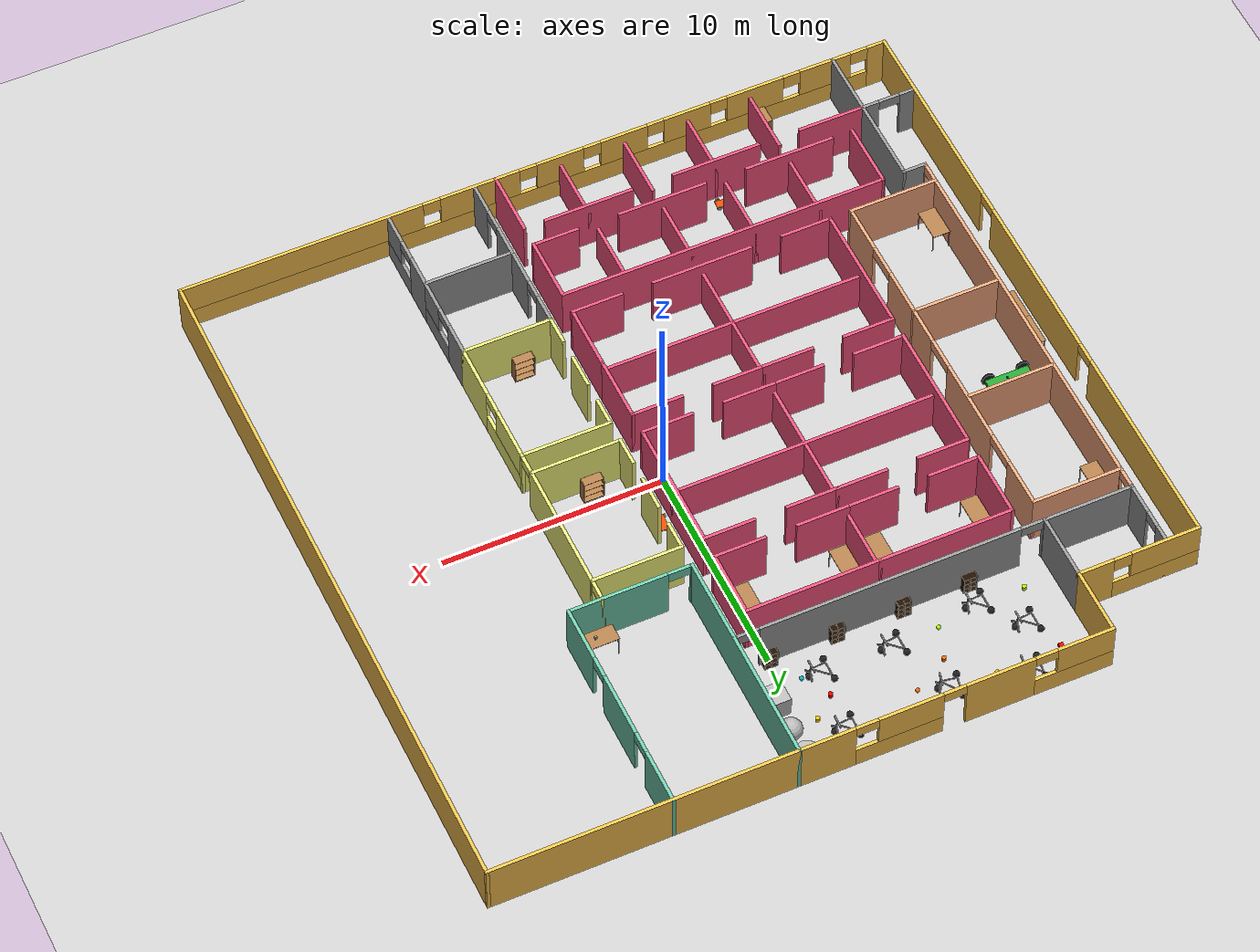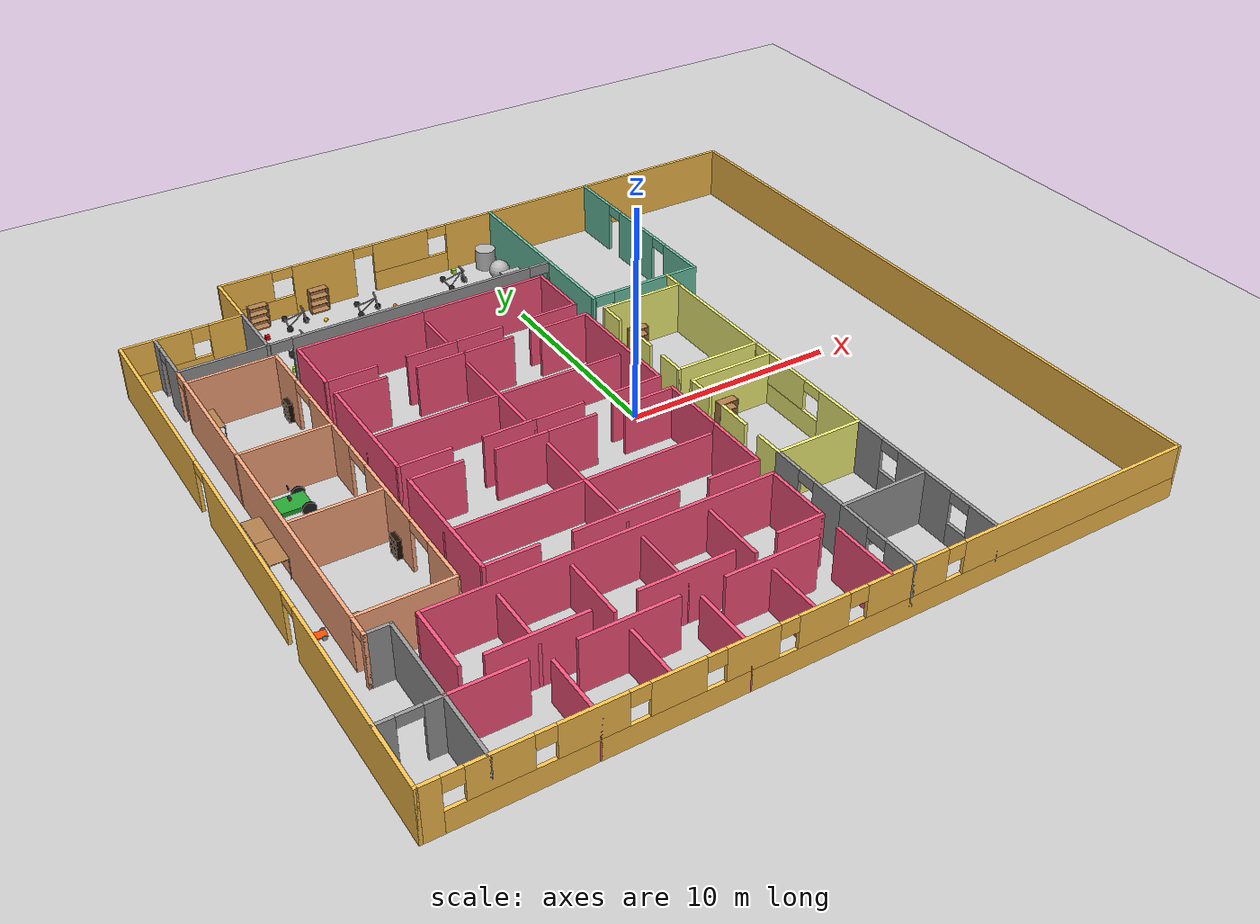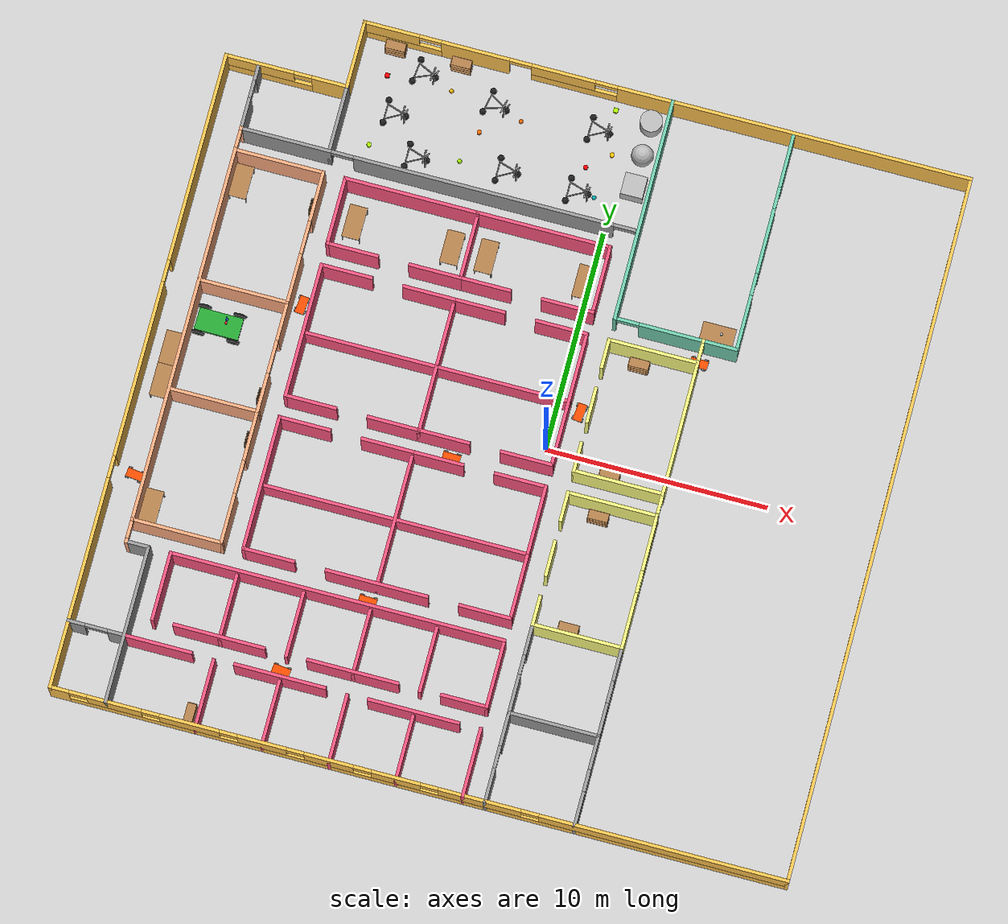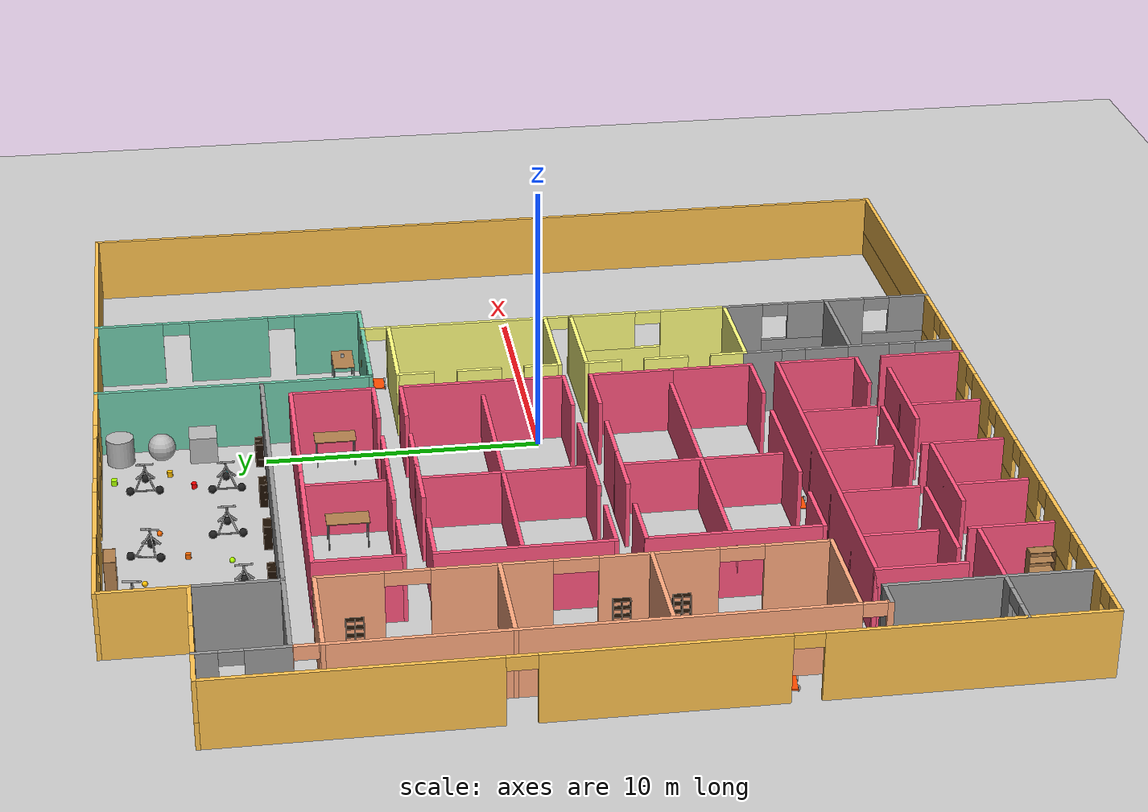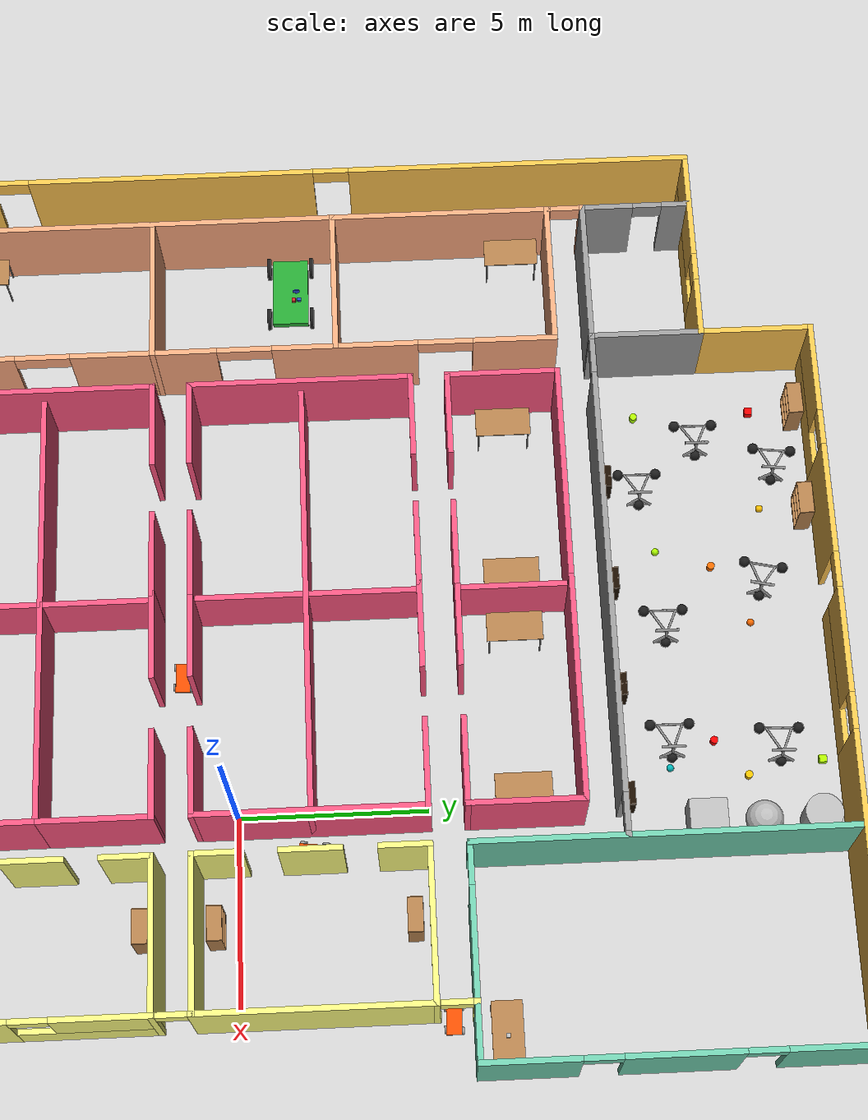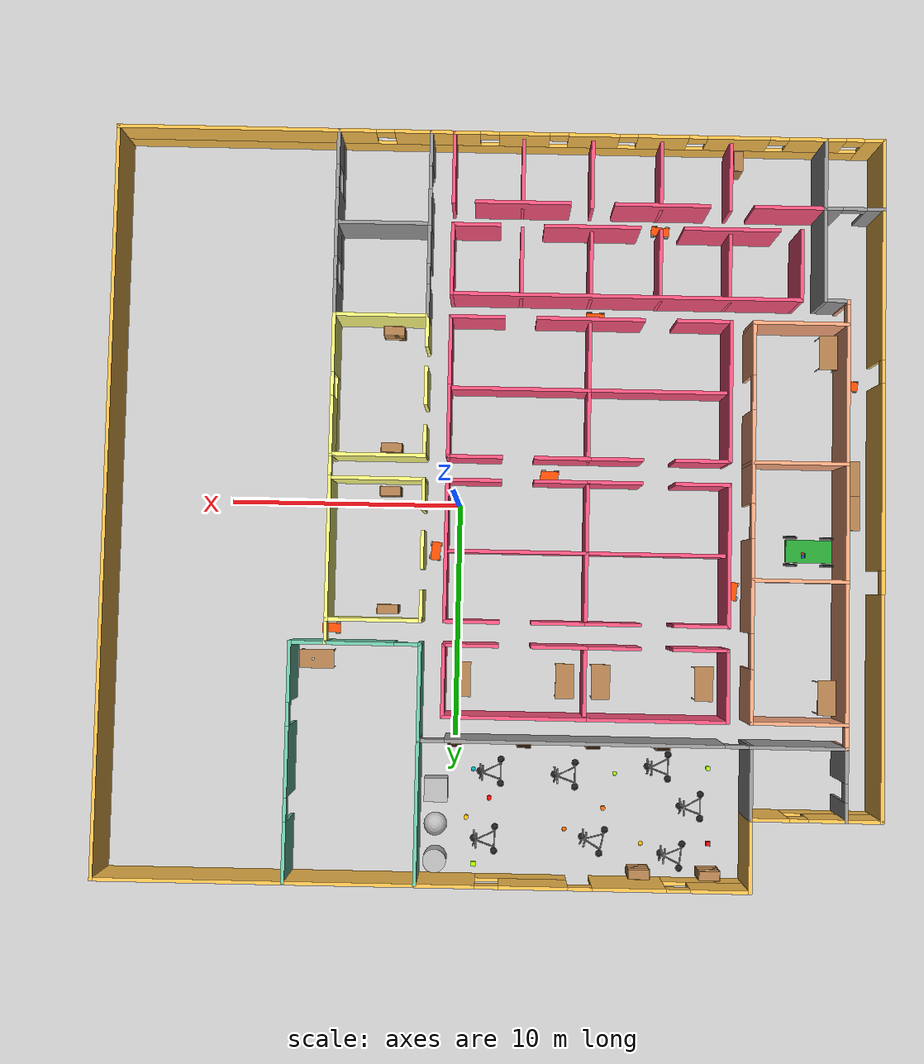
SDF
<sdf version="1.6">
 <world name="default">
  <plugin name="myWorld" filename="libmyWorld.so"/>
  <light name="sun" type="directional">
   <pose>0 0 10 0 -0 0</pose>
   <diffuse>0.8 0.8 0.8 1</diffuse>
   <specular>0.1 0.1 0.1 1</specular>
   <attenuation>
    <range>1000</range>
    <constant>0.9</constant>
    <linear>0.01</linear>
    <quadratic>0.001</quadratic>
   </attenuation>
   <direction>-0.5 0.5 -1</direction>
  </light>
  <model name="ground_plane">
   <static>1</static>
   <link name="link">
    <collision name="collision">
     <geometry><plane><normal>0 0 1</normal><size>100 100</size></plane></geometry>
     <surface><friction><ode><mu>100</mu><mu2>50</mu2></ode></friction></surface>
    </collision>
    <visual name="visual">
     <cast_shadows>0</cast_shadows>
     <geometry><plane><normal>0 0 1</normal><size>100 100</size></plane></geometry>
     <material>
      <script><uri>file://media/materials/scripts/gazebo.material</uri><name>Gazebo/Grey</name></script>
     </material>
    </visual>
   </link>
  </model>
  <gravity>0 0 -9.8</gravity>
  <magnetic_field>6e-06 2.3e-05 -4.2e-05</magnetic_field>
  <atmosphere type="adiabatic"/>
  <physics name="default_physics" default="0" type="ode">
   <max_step_size>0.001</max_step_size>
   <real_time_factor>1</real_time_factor>
   <real_time_update_rate>1000</real_time_update_rate>
  </physics>
  <scene><ambient>0.4 0.4 0.4 1</ambient><background>0.7 0.7 0.7 1</background><shadows>1</shadows></scene>
  <spherical_coordinates>
   <surface_model>EARTH_WGS84</surface_model>
   <latitude_deg>0</latitude_deg>
   <longitude_deg>0</longitude_deg>
   <elevation>0</elevation>
   <heading_deg>0</heading_deg>
  </spherical_coordinates>
  <model name="myWorld">
   <pose>-1.5 0 0 0 -0 0</pose>
   <link name="Wall_0">
    <pose>0 -16 0 0 -0 0</pose>
    <visual name="Wall_0_Visual_0">
     <pose>-16.1125 0 1.25 0 -0 0</pose>
     <geometry><box><size>0.925 0.15 2.5</size></box></geometry>
     <material>
      <script><uri>file://media/materials/scripts/gazebo.material</uri><name>Gazebo/Grey</name></script>
      <ambient>1 0.764706 0.305882 1</ambient>
     </material>
     <meta><layer>0</layer></meta>
    </visual>
    <collision name="Wall_0_Collision_0">
     <geometry><box><size>0.925 0.15 2.5</size></box></geometry>
     <pose>-16.1125 0 1.25 0 -0 0</pose>
    </collision>
    <visual name="Wall_0_Visual_1">
     <pose>0.4625 0 0.5 0 -0 0</pose>
     <geometry><box><size>32.225 0.15 1</size></box></geometry>
     <material>
      <script><uri>file://media/materials/scripts/gazebo.material</uri><name>Gazebo/Grey</name></script>
      <ambient>1 0.764706 0.305882 1</ambient>
     </material>
     <meta><layer>0</layer></meta>
    </visual>
    <collision name="Wall_0_Collision_1">
     <geometry><box><size>32.225 0.15 1</size></box></geometry>
     <pose>0.4625 0 0.5 0 -0 0</pose>
    </collision>
    <visual name="Wall_0_Visual_2">
     <pose>-13.625 0 1.75 0 -0 0</pose>
     <geometry><box><size>2.45 0.15 1.5</size></box></geometry>
     <material>
      <script><uri>file://media/materials/scripts/gazebo.material</uri><name>Gazebo/Grey</name></script>
      <ambient>1 0.764706 0.305882 1</ambient>
     </material>
     <meta><layer>0</layer></meta>
    </visual>
    <collision name="Wall_0_Collision_2">
     <geometry><box><size>2.45 0.15 1.5</size></box></geometry>
     <pose>-13.625 0 1.75 0 -0 0</pose>
    </collision>
    <visual name="Wall_0_Visual_3">
     <pose>-10.25 0 1.75 0 -0 0</pose>
     <geometry><box><size>2.7 0.15 1.5</size></box></geometry>
     <material>
      <script><uri>file://media/materials/scripts/gazebo.material</uri><name>Gazebo/Grey</name></script>
      <ambient>1 0.764706 0.305882 1</ambient>
     </material>
     <meta><layer>0</layer></meta>
    </visual>
    <collision name="Wall_0_Collision_3">
     <geometry><box><size>2.7 0.15 1.5</size></box></geometry>
     <pose>-10.25 0 1.75 0 -0 0</pose>
    </collision>
    <visual name="Wall_0_Visual_4">
     <pose>-7 0 1.75 0 -0 0</pose>
     <geometry><box><size>2.2 0.15 1.5</size></box></geometry>
     <material>
      <script><uri>file://media/materials/scripts/gazebo.material</uri><name>Gazebo/Grey</name></script>
      <ambient>1 0.764706 0.305882 1</ambient>
     </material>
     <meta><layer>0</layer></meta>
    </visual>
    <collision name="Wall_0_Collision_4">
     <geometry><box><size>2.2 0.15 1.5</size></box></geometry>
     <pose>-7 0 1.75 0 -0 0</pose>
    </collision>
    <visual name="Wall_0_Visual_5">
     <pose>-4 0 1.75 0 -0 0</pose>
     <geometry><box><size>2.2 0.15 1.5</size></box></geometry>
     <material>
      <script><uri>file://media/materials/scripts/gazebo.material</uri><name>Gazebo/Grey</name></script>
      <ambient>1 0.764706 0.305882 1</ambient>
     </material>
     <meta><layer>0</layer></meta>
    </visual>
    <collision name="Wall_0_Collision_5">
     <geometry><box><size>2.2 0.15 1.5</size></box></geometry>
     <pose>-4 0 1.75 0 -0 0</pose>
    </collision>
    <visual name="Wall_0_Visual_6">
     <pose>-1 0 1.75 0 -0 0</pose>
     <geometry><box><size>2.2 0.15 1.5</size></box></geometry>
     <material>
      <script><uri>file://media/materials/scripts/gazebo.material</uri><name>Gazebo/Grey</name></script>
      <ambient>1 0.764706 0.305882 1</ambient>
     </material>
     <meta><layer>0</layer></meta>
    </visual>
    <collision name="Wall_0_Collision_6">
     <geometry><box><size>2.2 0.15 1.5</size></box></geometry>
     <pose>-1 0 1.75 0 -0 0</pose>
    </collision>
    <visual name="Wall_0_Visual_7">
     <pose>2.75 0 1.75 0 -0 0</pose>
     <geometry><box><size>3.7 0.15 1.5</size></box></geometry>
     <material>
      <script><uri>file://media/materials/scripts/gazebo.material</uri><name>Gazebo/Grey</name></script>
      <ambient>1 0.764706 0.305882 1</ambient>
     </material>
     <meta><layer>0</layer></meta>
    </visual>
    <collision name="Wall_0_Collision_7">
     <geometry><box><size>3.7 0.15 1.5</size></box></geometry>
     <pose>2.75 0 1.75 0 -0 0</pose>
    </collision>
    <visual name="Wall_0_Visual_8">
     <pose>10.9875 0 1.75 0 -0 0</pose>
     <geometry><box><size>11.175 0.15 1.5</size></box></geometry>
     <material>
      <script><uri>file://media/materials/scripts/gazebo.material</uri><name>Gazebo/Grey</name></script>
      <ambient>1 0.764706 0.305882 1</ambient>
     </material>
     <meta><layer>0</layer></meta>
    </visual>
    <collision name="Wall_0_Collision_8">
     <geometry><box><size>11.175 0.15 1.5</size></box></geometry>
     <pose>10.9875 0 1.75 0 -0 0</pose>
    </collision>
    <visual name="Wall_0_Visual_9">
     <pose>-15.25 0 2.15 0 -0 0</pose>
     <geometry><box><size>0.8 0.15 0.7</size></box></geometry>
     <material>
      <script><uri>file://media/materials/scripts/gazebo.material</uri><name>Gazebo/Grey</name></script>
      <ambient>1 0.764706 0.305882 1</ambient>
     </material>
     <meta><layer>0</layer></meta>
    </visual>
    <collision name="Wall_0_Collision_9">
     <geometry><box><size>0.8 0.15 0.7</size></box></geometry>
     <pose>-15.25 0 2.15 0 -0 0</pose>
    </collision>
    <visual name="Wall_0_Visual_10">
     <pose>-12 0 2.15 0 -0 0</pose>
     <geometry><box><size>0.8 0.15 0.7</size></box></geometry>
     <material>
      <script><uri>file://media/materials/scripts/gazebo.material</uri><name>Gazebo/Grey</name></script>
      <ambient>1 0.764706 0.305882 1</ambient>
     </material>
     <meta><layer>0</layer></meta>
    </visual>
    <collision name="Wall_0_Collision_10">
     <geometry><box><size>0.8 0.15 0.7</size></box></geometry>
     <pose>-12 0 2.15 0 -0 0</pose>
    </collision>
    <visual name="Wall_0_Visual_11">
     <pose>-8.5 0 2.15 0 -0 0</pose>
     <geometry><box><size>0.8 0.15 0.7</size></box></geometry>
     <material>
      <script><uri>file://media/materials/scripts/gazebo.material</uri><name>Gazebo/Grey</name></script>
      <ambient>1 0.764706 0.305882 1</ambient>
     </material>
     <meta><layer>0</layer></meta>
    </visual>
    <collision name="Wall_0_Collision_11">
     <geometry><box><size>0.8 0.15 0.7</size></box></geometry>
     <pose>-8.5 0 2.15 0 -0 0</pose>
    </collision>
    <visual name="Wall_0_Visual_12">
     <pose>-5.5 0 2.15 0 -0 0</pose>
     <geometry><box><size>0.8 0.15 0.7</size></box></geometry>
     <material>
      <script><uri>file://media/materials/scripts/gazebo.material</uri><name>Gazebo/Grey</name></script>
      <ambient>1 0.764706 0.305882 1</ambient>
     </material>
     <meta><layer>0</layer></meta>
    </visual>
    <collision name="Wall_0_Collision_12">
     <geometry><box><size>0.8 0.15 0.7</size></box></geometry>
     <pose>-5.5 0 2.15 0 -0 0</pose>
    </collision>
    <visual name="Wall_0_Visual_13">
     <pose>-2.5 0 2.15 0 -0 0</pose>
     <geometry><box><size>0.8 0.15 0.7</size></box></geometry>
     <material>
      <script><uri>file://media/materials/scripts/gazebo.material</uri><name>Gazebo/Grey</name></script>
      <ambient>1 0.764706 0.305882 1</ambient>
     </material>
     <meta><layer>0</layer></meta>
    </visual>
    <collision name="Wall_0_Collision_13">
     <geometry><box><size>0.8 0.15 0.7</size></box></geometry>
     <pose>-2.5 0 2.15 0 -0 0</pose>
    </collision>
    <visual name="Wall_0_Visual_14">
     <pose>0.5 0 2.15 0 -0 0</pose>
     <geometry><box><size>0.8 0.15 0.7</size></box></geometry>
     <material>
      <script><uri>file://media/materials/scripts/gazebo.material</uri><name>Gazebo/Grey</name></script>
      <ambient>1 0.764706 0.305882 1</ambient>
     </material>
     <meta><layer>0</layer></meta>
    </visual>
    <collision name="Wall_0_Collision_14">
     <geometry><box><size>0.8 0.15 0.7</size></box></geometry>
     <pose>0.5 0 2.15 0 -0 0</pose>
    </collision>
    <visual name="Wall_0_Visual_15">
     <pose>5 0 2.15 0 -0 0</pose>
     <geometry><box><size>0.8 0.15 0.7</size></box></geometry>
     <material>
      <script><uri>file://media/materials/scripts/gazebo.material</uri><name>Gazebo/Grey</name></script>
      <ambient>1 0.764706 0.305882 1</ambient>
     </material>
     <meta><layer>0</layer></meta>
    </visual>
    <collision name="Wall_0_Collision_15">
     <geometry><box><size>0.8 0.15 0.7</size></box></geometry>
     <pose>5 0 2.15 0 -0 0</pose>
    </collision>
   </link>
   <link name="Wall_10">
    <pose>-16.5 -1.5 0 0 0 -1.5708</pose>
    <visual name="Wall_10_Visual_0">
     <pose>-9.7875 0 1.25 0 -0 0</pose>
     <geometry><box><size>9.575 0.15 2.5</size></box></geometry>
     <material>
      <script><uri>file://media/materials/scripts/gazebo.material</uri><name>Gazebo/Grey</name></script>
      <ambient>1 0.764706 0.305882 1</ambient>
     </material>
     <meta><layer>0</layer></meta>
    </visual>
    <collision name="Wall_10_Collision_0">
     <geometry><box><size>9.575 0.15 2.5</size></box></geometry>
     <pose>-9.7875 0 1.25 0 -0 0</pose>
    </collision>
    <visual name="Wall_10_Visual_1">
     <pose>0 0 1.25 0 -0 0</pose>
     <geometry><box><size>8 0.15 2.5</size></box></geometry>
     <material>
      <script><uri>file://media/materials/scripts/gazebo.material</uri><name>Gazebo/Grey</name></script>
      <ambient>1 0.764706 0.305882 1</ambient>
     </material>
     <meta><layer>0</layer></meta>
    </visual>
    <collision name="Wall_10_Collision_1">
     <geometry><box><size>8 0.15 2.5</size></box></geometry>
     <pose>0 0 1.25 0 -0 0</pose>
    </collision>
    <visual name="Wall_10_Visual_2">
     <pose>9.7875 0 1.25 0 -0 0</pose>
     <geometry><box><size>9.575 0.15 2.5</size></box></geometry>
     <material>
      <script><uri>file://media/materials/scripts/gazebo.material</uri><name>Gazebo/Grey</name></script>
      <ambient>1 0.764706 0.305882 1</ambient>
     </material>
     <meta><layer>0</layer></meta>
    </visual>
    <collision name="Wall_10_Collision_2">
     <geometry><box><size>9.575 0.15 2.5</size></box></geometry>
     <pose>9.7875 0 1.25 0 -0 0</pose>
    </collision>
    <visual name="Wall_10_Visual_3">
     <pose>-4.5 0 2.25 0 -0 0</pose>
     <geometry><box><size>1 0.15 0.5</size></box></geometry>
     <material>
      <script><uri>file://media/materials/scripts/gazebo.material</uri><name>Gazebo/Grey</name></script>
      <ambient>1 0.764706 0.305882 1</ambient>
     </material>
     <meta><layer>0</layer></meta>
    </visual>
    <collision name="Wall_10_Collision_3">
     <geometry><box><size>1 0.15 0.5</size></box></geometry>
     <pose>-4.5 0 2.25 0 -0 0</pose>
    </collision>
    <visual name="Wall_10_Visual_4">
     <pose>4.5 0 2.25 0 -0 0</pose>
     <geometry><box><size>1 0.15 0.5</size></box></geometry>
     <material>
      <script><uri>file://media/materials/scripts/gazebo.material</uri><name>Gazebo/Grey</name></script>
      <ambient>1 0.764706 0.305882 1</ambient>
     </material>
     <meta><layer>0</layer></meta>
    </visual>
    <collision name="Wall_10_Collision_4">
     <geometry><box><size>1 0.15 0.5</size></box></geometry>
     <pose>4.5 0 2.25 0 -0 0</pose>
    </collision>
   </link>
   <link name="Wall_100">
    <collision name="Wall_100_Collision">
     <geometry><box><size>15.15 0.15 2.5</size></box></geometry>
     <pose>0 0 1.25 0 -0 0</pose>
    </collision>
    <visual name="Wall_100_Visual">
     <pose>0 0 1.25 0 -0 0</pose>
     <geometry><box><size>15.15 0.15 2.5</size></box></geometry>
     <material>
      <script><uri>file://media/materials/scripts/gazebo.material</uri><name>Gazebo/Grey</name></script>
      <ambient>1 0.333333 0.498039 1</ambient>
     </material>
     <meta><layer>0</layer></meta>
    </visual>
    <pose>-5.5 -9 0 0 -0 0</pose>
   </link>
   <link name="Wall_102">
    <collision name="Wall_102_Collision">
     <geometry><box><size>3.15 0.15 2</size></box></geometry>
     <pose>0 0 1 0 -0 0</pose>
    </collision>
    <visual name="Wall_102_Visual">
     <pose>0 0 1 0 -0 0</pose>
     <geometry><box><size>3.15 0.15 2</size></box></geometry>
     <material>
      <script><uri>file://media/materials/scripts/gazebo.material</uri><name>Gazebo/Grey</name></script>
      <ambient>1 0.333333 0.498039 1</ambient>
     </material>
     <meta><layer>0</layer></meta>
    </visual>
    <pose>-10 -10.5 0 0 0 -1.5708</pose>
   </link>
   <link name="Wall_104">
    <collision name="Wall_104_Collision">
     <geometry><box><size>3.15 0.15 2</size></box></geometry>
     <pose>0 0 1 0 -0 0</pose>
    </collision>
    <visual name="Wall_104_Visual">
     <pose>0 0 1 0 -0 0</pose>
     <geometry><box><size>3.15 0.15 2</size></box></geometry>
     <material>
      <script><uri>file://media/materials/scripts/gazebo.material</uri><name>Gazebo/Grey</name></script>
      <ambient>1 0.333333 0.498039 1</ambient>
     </material>
     <meta><layer>0</layer></meta>
    </visual>
    <pose>-7 -10.5 0 0 0 -1.5708</pose>
   </link>
   <link name="Wall_106">
    <collision name="Wall_106_Collision">
     <geometry><box><size>3.15 0.15 2</size></box></geometry>
     <pose>0 0 1 0 -0 0</pose>
    </collision>
    <visual name="Wall_106_Visual">
     <pose>0 0 1 0 -0 0</pose>
     <geometry><box><size>3.15 0.15 2</size></box></geometry>
     <material>
      <script><uri>file://media/materials/scripts/gazebo.material</uri><name>Gazebo/Grey</name></script>
      <ambient>1 0.333333 0.498039 1</ambient>
     </material>
     <meta><layer>0</layer></meta>
    </visual>
    <pose>-4 -10.5 0 0 0 -1.5708</pose>
   </link>
   <link name="Wall_108">
    <collision name="Wall_108_Collision">
     <geometry><box><size>3.15 0.15 2</size></box></geometry>
     <pose>0 0 1 0 -0 0</pose>
    </collision>
    <visual name="Wall_108_Visual">
     <pose>0 0 1 0 -0 0</pose>
     <geometry><box><size>3.15 0.15 2</size></box></geometry>
     <material>
      <script><uri>file://media/materials/scripts/gazebo.material</uri><name>Gazebo/Grey</name></script>
      <ambient>1 0.333333 0.498039 1</ambient>
     </material>
     <meta><layer>0</layer></meta>
    </visual>
    <pose>-1 -10.5 0 0 0 -1.5708</pose>
   </link>
   <link name="Wall_110">
    <collision name="Wall_110_Collision">
     <geometry><box><size>3.15 0.15 2.5</size></box></geometry>
     <pose>0 0 1.25 0 -0 0</pose>
    </collision>
    <visual name="Wall_110_Visual">
     <pose>0 0 1.25 0 -0 0</pose>
     <geometry><box><size>3.15 0.15 2.5</size></box></geometry>
     <material>
      <script><uri>file://media/materials/scripts/gazebo.material</uri><name>Gazebo/Grey</name></script>
      <ambient>1 0.333333 0.498039 1</ambient>
     </material>
     <meta><layer>0</layer></meta>
    </visual>
    <pose>2 -10.5 0 0 0 -1.5708</pose>
   </link>
   <link name="Wall_114">
    <collision name="Wall_114_Collision">
     <geometry><box><size>3.15 0.15 2.5</size></box></geometry>
     <pose>0 0 1.25 0 -0 0</pose>
    </collision>
    <visual name="Wall_114_Visual">
     <pose>0 0 1.25 0 -0 0</pose>
     <geometry><box><size>3.15 0.15 2.5</size></box></geometry>
     <material>
      <script><uri>file://media/materials/scripts/gazebo.material</uri><name>Gazebo/Grey</name></script>
      <ambient>1 0.333333 0.498039 1</ambient>
     </material>
     <meta><layer>0</layer></meta>
    </visual>
    <pose>-13 -10.5 0 0 0 -1.5708</pose>
   </link>
   <link name="Wall_116">
    <collision name="Wall_116_Collision">
     <geometry><box><size>4.15 0.15 2.5</size></box></geometry>
     <pose>0 0 1.25 0 -0 0</pose>
    </collision>
    <visual name="Wall_116_Visual">
     <pose>0 0 1.25 0 -0 0</pose>
     <geometry><box><size>4.15 0.15 2.5</size></box></geometry>
     <material>
      <script><uri>file://media/materials/scripts/gazebo.material</uri><name>Gazebo/Grey</name></script>
      <ambient>1 0.333333 0.498039 1</ambient>
     </material>
     <meta><layer>0</layer></meta>
    </visual>
    <pose>-10 -12 0 0 -0 0</pose>
   </link>
   <link name="Wall_118">
    <collision name="Wall_118_Collision">
     <geometry><box><size>4.15 0.15 2.5</size></box></geometry>
     <pose>0 0 1.25 0 -0 0</pose>
    </collision>
    <visual name="Wall_118_Visual">
     <pose>0 0 1.25 0 -0 0</pose>
     <geometry><box><size>4.15 0.15 2.5</size></box></geometry>
     <material>
      <script><uri>file://media/materials/scripts/gazebo.material</uri><name>Gazebo/Grey</name></script>
      <ambient>1 0.333333 0.498039 1</ambient>
     </material>
     <meta><layer>0</layer></meta>
    </visual>
    <pose>-4 -12 0 0 -0 0</pose>
   </link>
   <link name="Wall_12">
    <pose>-15 11.5 0 0 0 -1.5708</pose>
    <visual name="Wall_12_Visual_0">
     <pose>-1.1475 0 1.25 0 -0 0</pose>
     <geometry><box><size>0.855 0.15 2.5</size></box></geometry>
     <material>
      <script><uri>file://media/materials/scripts/gazebo.material</uri><name>Gazebo/Grey</name></script>
      <ambient>1 1 1 1</ambient>
     </material>
     <meta><layer>0</layer></meta>
    </visual>
    <collision name="Wall_12_Collision_0">
     <geometry><box><size>0.855 0.15 2.5</size></box></geometry>
     <pose>-1.1475 0 1.25 0 -0 0</pose>
    </collision>
    <visual name="Wall_12_Visual_1">
     <pose>0.8275 0 1.25 0 -0 0</pose>
     <geometry><box><size>1.495 0.15 2.5</size></box></geometry>
     <material>
      <script><uri>file://media/materials/scripts/gazebo.material</uri><name>Gazebo/Grey</name></script>
      <ambient>1 1 1 1</ambient>
     </material>
     <meta><layer>0</layer></meta>
    </visual>
    <collision name="Wall_12_Collision_1">
     <geometry><box><size>1.495 0.15 2.5</size></box></geometry>
     <pose>0.8275 0 1.25 0 -0 0</pose>
    </collision>
    <visual name="Wall_12_Visual_2">
     <pose>-0.32 0 2.25 0 -0 0</pose>
     <geometry><box><size>0.8 0.15 0.5</size></box></geometry>
     <material>
      <script><uri>file://media/materials/scripts/gazebo.material</uri><name>Gazebo/Grey</name></script>
      <ambient>1 1 1 1</ambient>
     </material>
     <meta><layer>0</layer></meta>
    </visual>
    <collision name="Wall_12_Collision_2">
     <geometry><box><size>0.8 0.15 0.5</size></box></geometry>
     <pose>-0.32 0 2.25 0 -0 0</pose>
    </collision>
   </link>
   <link name="Wall_120">
    <collision name="Wall_120_Collision">
     <geometry><box><size>2.15 0.15 2.5</size></box></geometry>
     <pose>0 0 1.25 0 -0 0</pose>
    </collision>
    <visual name="Wall_120_Visual">
     <pose>0 0 1.25 0 -0 0</pose>
     <geometry><box><size>2.15 0.15 2.5</size></box></geometry>
     <material>
      <script><uri>file://media/materials/scripts/gazebo.material</uri><name>Gazebo/Grey</name></script>
      <ambient>1 0.333333 0.498039 1</ambient>
     </material>
     <meta><layer>0</layer></meta>
    </visual>
    <pose>1 -12 0 0 -0 0</pose>
   </link>
   <link name="Wall_126">
    <collision name="Wall_126_Collision">
     <geometry><box><size>6.15 0.15 2</size></box></geometry>
     <pose>0 0 1 0 -0 0</pose>
    </collision>
    <visual name="Wall_126_Visual">
     <pose>0 0 1 0 -0 0</pose>
     <geometry><box><size>6.15 0.15 2</size></box></geometry>
     <material>
      <script><uri>file://media/materials/scripts/gazebo.material</uri><name>Gazebo/Grey</name></script>
      <ambient>1 0.333333 0.498039 1</ambient>
     </material>
     <meta><layer>0</layer></meta>
    </visual>
    <pose>-1 -5 0 0 -0 0</pose>
   </link>
   <link name="Wall_127">
    <collision name="Wall_127_Collision">
     <geometry><box><size>3.15 0.15 2.5</size></box></geometry>
     <pose>0 0 1.25 0 -0 0</pose>
    </collision>
    <visual name="Wall_127_Visual">
     <pose>0 0 1.25 0 -0 0</pose>
     <geometry><box><size>3.15 0.15 2.5</size></box></geometry>
     <material>
      <script><uri>file://media/materials/scripts/gazebo.material</uri><name>Gazebo/Grey</name></script>
      <ambient>1 0.333333 0.498039 1</ambient>
     </material>
     <meta><layer>0</layer></meta>
    </visual>
    <pose>2 -6.5 0 0 0 -1.5708</pose>
   </link>
   <link name="Wall_128">
    <collision name="Wall_128_Collision">
     <geometry><box><size>2.4 0.15 2.5</size></box></geometry>
     <pose>0 0 1.25 0 -0 0</pose>
    </collision>
    <visual name="Wall_128_Visual">
     <pose>0 0 1.25 0 -0 0</pose>
     <geometry><box><size>2.4 0.15 2.5</size></box></geometry>
     <material>
      <script><uri>file://media/materials/scripts/gazebo.material</uri><name>Gazebo/Grey</name></script>
      <ambient>1 0.333333 0.498039 1</ambient>
     </material>
     <meta><layer>0</layer></meta>
    </visual>
    <pose>0.875 -8 0 0 -0 3.14159</pose>
   </link>
   <link name="Wall_130">
    <collision name="Wall_130_Collision">
     <geometry><box><size>2.4 0.15 2.5</size></box></geometry>
     <pose>0 0 1.25 0 -0 0</pose>
    </collision>
    <visual name="Wall_130_Visual">
     <pose>0 0 1.25 0 -0 0</pose>
     <geometry><box><size>2.4 0.15 2.5</size></box></geometry>
     <material>
      <script><uri>file://media/materials/scripts/gazebo.material</uri><name>Gazebo/Grey</name></script>
      <ambient>1 0.333333 0.498039 1</ambient>
     </material>
     <meta><layer>0</layer></meta>
    </visual>
    <pose>-2.875 -2 0 0 -0 0</pose>
   </link>
   <link name="Wall_132">
    <collision name="Wall_132_Collision">
     <geometry><box><size>2.4 0.15 2.5</size></box></geometry>
     <pose>0 0 1.25 0 -0 0</pose>
    </collision>
    <visual name="Wall_132_Visual">
     <pose>0 0 1.25 0 -0 0</pose>
     <geometry><box><size>2.4 0.15 2.5</size></box></geometry>
     <material>
      <script><uri>file://media/materials/scripts/gazebo.material</uri><name>Gazebo/Grey</name></script>
      <ambient>1 0.333333 0.498039 1</ambient>
     </material>
     <meta><layer>0</layer></meta>
    </visual>
    <pose>0.875 -2 0 0 -0 0</pose>
   </link>
   <link name="Wall_133">
    <collision name="Wall_133_Collision">
     <geometry><box><size>3.15 0.15 2.5</size></box></geometry>
     <pose>0 0 1.25 0 -0 0</pose>
    </collision>
    <visual name="Wall_133_Visual">
     <pose>0 0 1.25 0 -0 0</pose>
     <geometry><box><size>3.15 0.15 2.5</size></box></geometry>
     <material>
      <script><uri>file://media/materials/scripts/gazebo.material</uri><name>Gazebo/Grey</name></script>
      <ambient>1 0.333333 0.498039 1</ambient>
     </material>
     <meta><layer>0</layer></meta>
    </visual>
    <pose>2 -3.5 0 0 0 -1.5708</pose>
   </link>
   <link name="Wall_135">
    <collision name="Wall_135_Collision">
     <geometry><box><size>2.4 0.15 2.5</size></box></geometry>
     <pose>0 0 1.25 0 -0 0</pose>
    </collision>
    <visual name="Wall_135_Visual">
     <pose>0 0 1.25 0 -0 0</pose>
     <geometry><box><size>2.4 0.15 2.5</size></box></geometry>
     <material>
      <script><uri>file://media/materials/scripts/gazebo.material</uri><name>Gazebo/Grey</name></script>
      <ambient>1 0.333333 0.498039 1</ambient>
     </material>
     <meta><layer>0</layer></meta>
    </visual>
    <pose>-2.875 5 0 0 -0 0</pose>
   </link>
   <link name="Wall_137">
    <collision name="Wall_137_Collision">
     <geometry><box><size>2.4 0.15 2.5</size></box></geometry>
     <pose>0 0 1.25 0 -0 0</pose>
    </collision>
    <visual name="Wall_137_Visual">
     <pose>0 0 1.25 0 -0 0</pose>
     <geometry><box><size>2.4 0.15 2.5</size></box></geometry>
     <material>
      <script><uri>file://media/materials/scripts/gazebo.material</uri><name>Gazebo/Grey</name></script>
      <ambient>1 0.333333 0.498039 1</ambient>
     </material>
     <meta><layer>0</layer></meta>
    </visual>
    <pose>0.875 5 0 0 -0 0</pose>
   </link>
   <link name="Wall_138">
    <collision name="Wall_138_Collision">
     <geometry><box><size>6.15 0.15 2.5</size></box></geometry>
     <pose>0 0 1.25 0 -0 0</pose>
    </collision>
    <visual name="Wall_138_Visual">
     <pose>0 0 1.25 0 -0 0</pose>
     <geometry><box><size>6.15 0.15 2.5</size></box></geometry>
     <material>
      <script><uri>file://media/materials/scripts/gazebo.material</uri><name>Gazebo/Grey</name></script>
      <ambient>1 0.333333 0.498039 1</ambient>
     </material>
     <meta><layer>0</layer></meta>
    </visual>
    <pose>2 2 0 0 0 -1.5708</pose>
   </link>
   <link name="Wall_139">
    <collision name="Wall_139_Collision">
     <geometry><box><size>2.4 0.15 2.5</size></box></geometry>
     <pose>0 0 1.25 0 -0 0</pose>
    </collision>
    <visual name="Wall_139_Visual">
     <pose>0 0 1.25 0 -0 0</pose>
     <geometry><box><size>2.4 0.15 2.5</size></box></geometry>
     <material>
      <script><uri>file://media/materials/scripts/gazebo.material</uri><name>Gazebo/Grey</name></script>
      <ambient>1 0.333333 0.498039 1</ambient>
     </material>
     <meta><layer>0</layer></meta>
    </visual>
    <pose>0.875 -1 0 0 -0 3.14159</pose>
   </link>
   <link name="Wall_14">
    <pose>-15 0.5 0 0 0 -1.5708</pose>
    <visual name="Wall_14_Visual_0">
     <pose>-9.4925 0 1.25 0 -0 0</pose>
     <geometry><box><size>0.165 0.15 2.5</size></box></geometry>
     <material>
      <script><uri>file://media/materials/scripts/gazebo.material</uri><name>Gazebo/Grey</name></script>
      <ambient>1 0.666667 0.498039 1</ambient>
     </material>
     <meta><layer>0</layer></meta>
    </visual>
    <collision name="Wall_14_Collision_0">
     <geometry><box><size>0.165 0.15 2.5</size></box></geometry>
     <pose>-9.4925 0 1.25 0 -0 0</pose>
    </collision>
    <visual name="Wall_14_Visual_1">
     <pose>-0.025 0 1.25 0 -0 0</pose>
     <geometry><box><size>17.17 0.15 2.5</size></box></geometry>
     <material>
      <script><uri>file://media/materials/scripts/gazebo.material</uri><name>Gazebo/Grey</name></script>
      <ambient>1 0.666667 0.498039 1</ambient>
     </material>
     <meta><layer>0</layer></meta>
    </visual>
    <collision name="Wall_14_Collision_1">
     <geometry><box><size>17.17 0.15 2.5</size></box></geometry>
     <pose>-0.025 0 1.25 0 -0 0</pose>
    </collision>
    <visual name="Wall_14_Visual_2">
     <pose>9.4675 0 1.25 0 -0 0</pose>
     <geometry><box><size>0.215 0.15 2.5</size></box></geometry>
     <material>
      <script><uri>file://media/materials/scripts/gazebo.material</uri><name>Gazebo/Grey</name></script>
      <ambient>1 0.666667 0.498039 1</ambient>
     </material>
     <meta><layer>0</layer></meta>
    </visual>
    <collision name="Wall_14_Collision_2">
     <geometry><box><size>0.215 0.15 2.5</size></box></geometry>
     <pose>9.4675 0 1.25 0 -0 0</pose>
    </collision>
    <visual name="Wall_14_Visual_3">
     <pose>-9.01 0 2.25 0 -0 0</pose>
     <geometry><box><size>0.8 0.15 0.5</size></box></geometry>
     <material>
      <script><uri>file://media/materials/scripts/gazebo.material</uri><name>Gazebo/Grey</name></script>
      <ambient>1 0.666667 0.498039 1</ambient>
     </material>
     <meta><layer>0</layer></meta>
    </visual>
    <collision name="Wall_14_Collision_3">
     <geometry><box><size>0.8 0.15 0.5</size></box></geometry>
     <pose>-9.01 0 2.25 0 -0 0</pose>
    </collision>
    <visual name="Wall_14_Visual_4">
     <pose>8.96 0 2.25 0 -0 0</pose>
     <geometry><box><size>0.8 0.15 0.5</size></box></geometry>
     <material>
      <script><uri>file://media/materials/scripts/gazebo.material</uri><name>Gazebo/Grey</name></script>
      <ambient>1 0.666667 0.498039 1</ambient>
     </material>
     <meta><layer>0</layer></meta>
    </visual>
    <collision name="Wall_14_Collision_4">
     <geometry><box><size>0.8 0.15 0.5</size></box></geometry>
     <pose>8.96 0 2.25 0 -0 0</pose>
    </collision>
   </link>
   <link name="Wall_141">
    <collision name="Wall_141_Collision">
     <geometry><box><size>2.4 0.15 2.5</size></box></geometry>
     <pose>0 0 1.25 0 -0 0</pose>
    </collision>
    <visual name="Wall_141_Visual">
     <pose>0 0 1.25 0 -0 0</pose>
     <geometry><box><size>2.4 0.15 2.5</size></box></geometry>
     <material>
      <script><uri>file://media/materials/scripts/gazebo.material</uri><name>Gazebo/Grey</name></script>
      <ambient>1 0.333333 0.498039 1</ambient>
     </material>
     <meta><layer>0</layer></meta>
    </visual>
    <pose>-2.875 -1 0 0 -0 0</pose>
   </link>
   <link name="Wall_143">
    <collision name="Wall_143_Collision">
     <geometry><box><size>6.15 0.15 2.5</size></box></geometry>
     <pose>0 0 1.25 0 -0 0</pose>
    </collision>
    <visual name="Wall_143_Visual">
     <pose>0 0 1.25 0 -0 0</pose>
     <geometry><box><size>6.15 0.15 2.5</size></box></geometry>
     <material>
      <script><uri>file://media/materials/scripts/gazebo.material</uri><name>Gazebo/Grey</name></script>
      <ambient>1 0.333333 0.498039 1</ambient>
     </material>
     <meta><layer>0</layer></meta>
    </visual>
    <pose>-1 9 0 0 -0 0</pose>
   </link>
   <link name="Wall_144">
    <collision name="Wall_144_Collision">
     <geometry><box><size>3.15 0.15 2.5</size></box></geometry>
     <pose>0 0 1.25 0 -0 0</pose>
    </collision>
    <visual name="Wall_144_Visual">
     <pose>0 0 1.25 0 -0 0</pose>
     <geometry><box><size>3.15 0.15 2.5</size></box></geometry>
     <material>
      <script><uri>file://media/materials/scripts/gazebo.material</uri><name>Gazebo/Grey</name></script>
      <ambient>1 0.333333 0.498039 1</ambient>
     </material>
     <meta><layer>0</layer></meta>
    </visual>
    <pose>2 7.5 0 0 0 -1.5708</pose>
   </link>
   <link name="Wall_145">
    <collision name="Wall_145_Collision">
     <geometry><box><size>2.4 0.15 2.5</size></box></geometry>
     <pose>0 0 1.25 0 -0 0</pose>
    </collision>
    <visual name="Wall_145_Visual">
     <pose>0 0 1.25 0 -0 0</pose>
     <geometry><box><size>2.4 0.15 2.5</size></box></geometry>
     <material>
      <script><uri>file://media/materials/scripts/gazebo.material</uri><name>Gazebo/Grey</name></script>
      <ambient>1 0.333333 0.498039 1</ambient>
     </material>
     <meta><layer>0</layer></meta>
    </visual>
    <pose>0.875 6 0 0 -0 3.14159</pose>
   </link>
   <link name="Wall_147">
    <collision name="Wall_147_Collision">
     <geometry><box><size>2.4 0.15 2.5</size></box></geometry>
     <pose>0 0 1.25 0 -0 0</pose>
    </collision>
    <visual name="Wall_147_Visual">
     <pose>0 0 1.25 0 -0 0</pose>
     <geometry><box><size>2.4 0.15 2.5</size></box></geometry>
     <material>
      <script><uri>file://media/materials/scripts/gazebo.material</uri><name>Gazebo/Grey</name></script>
      <ambient>1 0.333333 0.498039 1</ambient>
     </material>
     <meta><layer>0</layer></meta>
    </visual>
    <pose>-2.875 6 0 0 -0 0</pose>
   </link>
   <link name="Wall_149">
    <collision name="Wall_149_Collision">
     <geometry><box><size>4.15 0.15 2.5</size></box></geometry>
     <pose>0 0 1.25 0 -0 0</pose>
    </collision>
    <visual name="Wall_149_Visual">
     <pose>0 0 1.25 0 -0 0</pose>
     <geometry><box><size>4.15 0.15 2.5</size></box></geometry>
     <material>
      <script><uri>file://media/materials/scripts/gazebo.material</uri><name>Gazebo/Grey</name></script>
      <ambient>1 0.666667 0.498039 1</ambient>
     </material>
     <meta><layer>0</layer></meta>
    </visual>
    <pose>-13 3 0 0 -0 0</pose>
   </link>
   <link name="Wall_151">
    <pose>3 -14 0 0 -0 1.5708</pose>
    <visual name="Wall_151_Visual_0">
     <pose>-1.2875 0 1.25 0 -0 0</pose>
     <geometry><box><size>1.575 0.15 2.5</size></box></geometry>
     <material>
      <script><uri>file://media/materials/scripts/gazebo.material</uri><name>Gazebo/Grey</name></script>
      <ambient>1 1 1 1</ambient>
     </material>
     <meta><layer>0</layer></meta>
    </visual>
    <collision name="Wall_151_Collision_0">
     <geometry><box><size>1.575 0.15 2.5</size></box></geometry>
     <pose>-1.2875 0 1.25 0 -0 0</pose>
    </collision>
    <visual name="Wall_151_Visual_1">
     <pose>1.2875 0 1.25 0 -0 0</pose>
     <geometry><box><size>1.575 0.15 2.5</size></box></geometry>
     <material>
      <script><uri>file://media/materials/scripts/gazebo.material</uri><name>Gazebo/Grey</name></script>
      <ambient>1 1 1 1</ambient>
     </material>
     <meta><layer>0</layer></meta>
    </visual>
    <collision name="Wall_151_Collision_1">
     <geometry><box><size>1.575 0.15 2.5</size></box></geometry>
     <pose>1.2875 0 1.25 0 -0 0</pose>
    </collision>
    <visual name="Wall_151_Visual_2">
     <pose>0 0 2.25 0 -0 0</pose>
     <geometry><box><size>1 0.15 0.5</size></box></geometry>
     <material>
      <script><uri>file://media/materials/scripts/gazebo.material</uri><name>Gazebo/Grey</name></script>
      <ambient>1 1 1 1</ambient>
     </material>
     <meta><layer>0</layer></meta>
    </visual>
    <collision name="Wall_151_Collision_2">
     <geometry><box><size>1 0.15 0.5</size></box></geometry>
     <pose>0 0 2.25 0 -0 0</pose>
    </collision>
   </link>
   <link name="Wall_152">
    <collision name="Wall_152_Collision">
     <geometry><box><size>4.15 0.15 2.5</size></box></geometry>
     <pose>0 0 1.25 0 -0 0</pose>
    </collision>
    <visual name="Wall_152_Visual">
     <pose>0 0 1.25 0 -0 0</pose>
     <geometry><box><size>4.15 0.15 2.5</size></box></geometry>
     <material>
      <script><uri>file://media/materials/scripts/gazebo.material</uri><name>Gazebo/Grey</name></script>
      <ambient>1 1 1 1</ambient>
     </material>
     <meta><layer>0</layer></meta>
    </visual>
    <pose>5 -12 0 0 -0 0</pose>
   </link>
   <link name="Wall_153">
    <pose>7 -14 0 0 0 -1.5708</pose>
    <visual name="Wall_153_Visual_0">
     <pose>-1.2825 0 1.25 0 -0 0</pose>
     <geometry><box><size>1.585 0.15 2.5</size></box></geometry>
     <material>
      <script><uri>file://media/materials/scripts/gazebo.material</uri><name>Gazebo/Grey</name></script>
      <ambient>1 1 1 1</ambient>
     </material>
     <meta><layer>0</layer></meta>
    </visual>
    <collision name="Wall_153_Collision_0">
     <geometry><box><size>1.585 0.15 2.5</size></box></geometry>
     <pose>-1.2825 0 1.25 0 -0 0</pose>
    </collision>
    <visual name="Wall_153_Visual_1">
     <pose>0.7925 0 0.5 0 -0 0</pose>
     <geometry><box><size>2.565 0.15 1</size></box></geometry>
     <material>
      <script><uri>file://media/materials/scripts/gazebo.material</uri><name>Gazebo/Grey</name></script>
      <ambient>1 1 1 1</ambient>
     </material>
     <meta><layer>0</layer></meta>
    </visual>
    <collision name="Wall_153_Collision_1">
     <geometry><box><size>2.565 0.15 1</size></box></geometry>
     <pose>0.7925 0 0.5 0 -0 0</pose>
    </collision>
    <visual name="Wall_153_Visual_2">
     <pose>1.2925 0 1.75 0 -0 0</pose>
     <geometry><box><size>1.565 0.15 1.5</size></box></geometry>
     <material>
      <script><uri>file://media/materials/scripts/gazebo.material</uri><name>Gazebo/Grey</name></script>
      <ambient>1 1 1 1</ambient>
     </material>
     <meta><layer>0</layer></meta>
    </visual>
    <collision name="Wall_153_Collision_2">
     <geometry><box><size>1.565 0.15 1.5</size></box></geometry>
     <pose>1.2925 0 1.75 0 -0 0</pose>
    </collision>
    <visual name="Wall_153_Visual_3">
     <pose>0.01 0 2.25 0 -0 0</pose>
     <geometry><box><size>1 0.15 0.5</size></box></geometry>
     <material>
      <script><uri>file://media/materials/scripts/gazebo.material</uri><name>Gazebo/Grey</name></script>
      <ambient>1 1 1 1</ambient>
     </material>
     <meta><layer>0</layer></meta>
    </visual>
    <collision name="Wall_153_Collision_3">
     <geometry><box><size>1 0.15 0.5</size></box></geometry>
     <pose>0.01 0 2.25 0 -0 0</pose>
    </collision>
   </link>
   <link name="Wall_157">
    <pose>3 -10 0 0 -0 1.5708</pose>
    <visual name="Wall_157_Visual_0">
     <pose>-1.1775 0 1.25 0 -0 0</pose>
     <geometry><box><size>1.795 0.15 2.5</size></box></geometry>
     <material>
      <script><uri>file://media/materials/scripts/gazebo.material</uri><name>Gazebo/Grey</name></script>
      <ambient>1 1 1 1</ambient>
     </material>
     <meta><layer>0</layer></meta>
    </visual>
    <collision name="Wall_157_Collision_0">
     <geometry><box><size>1.795 0.15 2.5</size></box></geometry>
     <pose>-1.1775 0 1.25 0 -0 0</pose>
    </collision>
    <visual name="Wall_157_Visual_1">
     <pose>1.3475 0 1.25 0 -0 0</pose>
     <geometry><box><size>1.455 0.15 2.5</size></box></geometry>
     <material>
      <script><uri>file://media/materials/scripts/gazebo.material</uri><name>Gazebo/Grey</name></script>
      <ambient>1 1 1 1</ambient>
     </material>
     <meta><layer>0</layer></meta>
    </visual>
    <collision name="Wall_157_Collision_1">
     <geometry><box><size>1.455 0.15 2.5</size></box></geometry>
     <pose>1.3475 0 1.25 0 -0 0</pose>
    </collision>
    <visual name="Wall_157_Visual_2">
     <pose>0.17 0 2.25 0 -0 0</pose>
     <geometry><box><size>0.9 0.15 0.5</size></box></geometry>
     <material>
      <script><uri>file://media/materials/scripts/gazebo.material</uri><name>Gazebo/Grey</name></script>
      <ambient>1 1 1 1</ambient>
     </material>
     <meta><layer>0</layer></meta>
    </visual>
    <collision name="Wall_157_Collision_2">
     <geometry><box><size>0.9 0.15 0.5</size></box></geometry>
     <pose>0.17 0 2.25 0 -0 0</pose>
    </collision>
   </link>
   <link name="Wall_158">
    <collision name="Wall_158_Collision">
     <geometry><box><size>4.15 0.15 2.5</size></box></geometry>
     <pose>0 0 1.25 0 -0 0</pose>
    </collision>
    <visual name="Wall_158_Visual">
     <pose>0 0 1.25 0 -0 0</pose>
     <geometry><box><size>4.15 0.15 2.5</size></box></geometry>
     <material>
      <script><uri>file://media/materials/scripts/gazebo.material</uri><name>Gazebo/Grey</name></script>
      <ambient>1 1 0.498039 1</ambient>
     </material>
     <meta><layer>0</layer></meta>
    </visual>
    <pose>5 -8 0 0 -0 0</pose>
   </link>
   <link name="Wall_159">
    <pose>7 -10 0 0 0 -1.5708</pose>
    <visual name="Wall_159_Visual_0">
     <pose>-1.2875 0 1.25 0 -0 0</pose>
     <geometry><box><size>1.575 0.15 2.5</size></box></geometry>
     <material>
      <script><uri>file://media/materials/scripts/gazebo.material</uri><name>Gazebo/Grey</name></script>
      <ambient>1 1 1 1</ambient>
     </material>
     <meta><layer>0</layer></meta>
    </visual>
    <collision name="Wall_159_Collision_0">
     <geometry><box><size>1.575 0.15 2.5</size></box></geometry>
     <pose>-1.2875 0 1.25 0 -0 0</pose>
    </collision>
    <visual name="Wall_159_Visual_1">
     <pose>0.7875 0 0.5 0 -0 0</pose>
     <geometry><box><size>2.575 0.15 1</size></box></geometry>
     <material>
      <script><uri>file://media/materials/scripts/gazebo.material</uri><name>Gazebo/Grey</name></script>
      <ambient>1 1 1 1</ambient>
     </material>
     <meta><layer>0</layer></meta>
    </visual>
    <collision name="Wall_159_Collision_1">
     <geometry><box><size>2.575 0.15 1</size></box></geometry>
     <pose>0.7875 0 0.5 0 -0 0</pose>
    </collision>
    <visual name="Wall_159_Visual_2">
     <pose>1.2875 0 1.75 0 -0 0</pose>
     <geometry><box><size>1.575 0.15 1.5</size></box></geometry>
     <material>
      <script><uri>file://media/materials/scripts/gazebo.material</uri><name>Gazebo/Grey</name></script>
      <ambient>1 1 1 1</ambient>
     </material>
     <meta><layer>0</layer></meta>
    </visual>
    <collision name="Wall_159_Collision_2">
     <geometry><box><size>1.575 0.15 1.5</size></box></geometry>
     <pose>1.2875 0 1.75 0 -0 0</pose>
    </collision>
    <visual name="Wall_159_Visual_3">
     <pose>0 0 2.25 0 -0 0</pose>
     <geometry><box><size>1 0.15 0.5</size></box></geometry>
     <material>
      <script><uri>file://media/materials/scripts/gazebo.material</uri><name>Gazebo/Grey</name></script>
      <ambient>1 1 1 1</ambient>
     </material>
     <meta><layer>0</layer></meta>
    </visual>
    <collision name="Wall_159_Collision_3">
     <geometry><box><size>1 0.15 0.5</size></box></geometry>
     <pose>0 0 2.25 0 -0 0</pose>
    </collision>
   </link>
   <link name="Wall_16">
    <collision name="Wall_16_Collision">
     <geometry><box><size>7.15 0.15 2.5</size></box></geometry>
     <pose>0 0 1.25 0 -0 0</pose>
    </collision>
    <visual name="Wall_16_Visual">
     <pose>0 0 1.25 0 -0 0</pose>
     <geometry><box><size>7.15 0.15 2.5</size></box></geometry>
     <material>
      <script><uri>file://media/materials/scripts/gazebo.material</uri><name>Gazebo/Grey</name></script>
      <ambient>1 1 1 1</ambient>
     </material>
     <meta><layer>0</layer></meta>
    </visual>
    <pose>-14 -12.5 0 0 0 -1.5708</pose>
   </link>
   <link name="Wall_161">
    <pose>7 -5 0 0 -0 1.5708</pose>
    <visual name="Wall_161_Visual_0">
     <pose>-1.7875 0 1.25 0 -0 0</pose>
     <geometry><box><size>2.575 0.15 2.5</size></box></geometry>
     <material>
      <script><uri>file://media/materials/scripts/gazebo.material</uri><name>Gazebo/Grey</name></script>
      <ambient>1 1 0.498039 1</ambient>
     </material>
     <meta><layer>0</layer></meta>
    </visual>
    <collision name="Wall_161_Collision_0">
     <geometry><box><size>2.575 0.15 2.5</size></box></geometry>
     <pose>-1.7875 0 1.25 0 -0 0</pose>
    </collision>
    <visual name="Wall_161_Visual_1">
     <pose>1.2875 0 0.5 0 -0 0</pose>
     <geometry><box><size>3.575 0.15 1</size></box></geometry>
     <material>
      <script><uri>file://media/materials/scripts/gazebo.material</uri><name>Gazebo/Grey</name></script>
      <ambient>1 1 0.498039 1</ambient>
     </material>
     <meta><layer>0</layer></meta>
    </visual>
    <collision name="Wall_161_Collision_1">
     <geometry><box><size>3.575 0.15 1</size></box></geometry>
     <pose>1.2875 0 0.5 0 -0 0</pose>
    </collision>
    <visual name="Wall_161_Visual_2">
     <pose>1.7875 0 1.75 0 -0 0</pose>
     <geometry><box><size>2.575 0.15 1.5</size></box></geometry>
     <material>
      <script><uri>file://media/materials/scripts/gazebo.material</uri><name>Gazebo/Grey</name></script>
      <ambient>1 1 0.498039 1</ambient>
     </material>
     <meta><layer>0</layer></meta>
    </visual>
    <collision name="Wall_161_Collision_2">
     <geometry><box><size>2.575 0.15 1.5</size></box></geometry>
     <pose>1.7875 0 1.75 0 -0 0</pose>
    </collision>
    <visual name="Wall_161_Visual_3">
     <pose>1.7875 0 1.75 0 -0 0</pose>
     <geometry><box><size>2.575 0.15 1.5</size></box></geometry>
     <material>
      <script><uri>file://media/materials/scripts/gazebo.material</uri><name>Gazebo/Grey</name></script>
      <ambient>1 1 0.498039 1</ambient>
     </material>
     <meta><layer>0</layer></meta>
    </visual>
    <collision name="Wall_161_Collision_3">
     <geometry><box><size>2.575 0.15 1.5</size></box></geometry>
     <pose>1.7875 0 1.75 0 -0 0</pose>
    </collision>
    <visual name="Wall_161_Visual_4">
     <pose>0 0 2.25 0 -0 0</pose>
     <geometry><box><size>1 0.15 0.5</size></box></geometry>
     <material>
      <script><uri>file://media/materials/scripts/gazebo.material</uri><name>Gazebo/Grey</name></script>
      <ambient>1 1 0.498039 1</ambient>
     </material>
     <meta><layer>0</layer></meta>
    </visual>
    <collision name="Wall_161_Collision_4">
     <geometry><box><size>1 0.15 0.5</size></box></geometry>
     <pose>0 0 2.25 0 -0 0</pose>
    </collision>
   </link>
   <link name="Wall_163">
    <collision name="Wall_163_Collision">
     <geometry><box><size>4.15 0.15 2.5</size></box></geometry>
     <pose>0 0 1.25 0 -0 0</pose>
    </collision>
    <visual name="Wall_163_Visual">
     <pose>0 0 1.25 0 -0 0</pose>
     <geometry><box><size>4.15 0.15 2.5</size></box></geometry>
     <material>
      <script><uri>file://media/materials/scripts/gazebo.material</uri><name>Gazebo/Grey</name></script>
      <ambient>1 1 0.498039 1</ambient>
     </material>
     <meta><layer>0</layer></meta>
    </visual>
    <pose>5 -2 0 0 -0 3.14159</pose>
   </link>
   <link name="Wall_165">
    <collision name="Wall_165_Collision">
     <geometry><box><size>1.4 0.15 2.5</size></box></geometry>
     <pose>0 0 1.25 0 -0 0</pose>
    </collision>
    <visual name="Wall_165_Visual">
     <pose>0 0 1.25 0 -0 0</pose>
     <geometry><box><size>1.4 0.15 2.5</size></box></geometry>
     <material>
      <script><uri>file://media/materials/scripts/gazebo.material</uri><name>Gazebo/Grey</name></script>
      <ambient>1 1 0.498039 1</ambient>
     </material>
     <meta><layer>0</layer></meta>
    </visual>
    <pose>3 -2.625 0 0 0 -1.5708</pose>
   </link>
   <link name="Wall_167">
    <collision name="Wall_167_Collision">
     <geometry><box><size>1.65 0.15 2.5</size></box></geometry>
     <pose>0 0 1.25 0 -0 0</pose>
    </collision>
    <visual name="Wall_167_Visual">
     <pose>0 0 1.25 0 -0 0</pose>
     <geometry><box><size>1.65 0.15 2.5</size></box></geometry>
     <material>
      <script><uri>file://media/materials/scripts/gazebo.material</uri><name>Gazebo/Grey</name></script>
      <ambient>1 1 0.498039 1</ambient>
     </material>
     <meta><layer>0</layer></meta>
    </visual>
    <pose>3 -5 0 0 0 -1.5708</pose>
   </link>
   <link name="Wall_169">
    <collision name="Wall_169_Collision">
     <geometry><box><size>1.4 0.15 2.5</size></box></geometry>
     <pose>0 0 1.25 0 -0 0</pose>
    </collision>
    <visual name="Wall_169_Visual">
     <pose>0 0 1.25 0 -0 0</pose>
     <geometry><box><size>1.4 0.15 2.5</size></box></geometry>
     <material>
      <script><uri>file://media/materials/scripts/gazebo.material</uri><name>Gazebo/Grey</name></script>
      <ambient>1 1 0.498039 1</ambient>
     </material>
     <meta><layer>0</layer></meta>
    </visual>
    <pose>3 -7.375 0 0 -0 1.5708</pose>
   </link>
   <link name="Wall_171">
    <pose>7 2 0 0 -0 1.5708</pose>
    <visual name="Wall_171_Visual_0">
     <pose>-3.9875 0 1.25 0 -0 0</pose>
     <geometry><box><size>0.175 0.15 2.5</size></box></geometry>
     <material>
      <script><uri>file://media/materials/scripts/gazebo.material</uri><name>Gazebo/Grey</name></script>
      <ambient>1 1 0.498039 1</ambient>
     </material>
     <meta><layer>0</layer></meta>
    </visual>
    <collision name="Wall_171_Collision_0">
     <geometry><box><size>0.175 0.15 2.5</size></box></geometry>
     <pose>-3.9875 0 1.25 0 -0 0</pose>
    </collision>
    <visual name="Wall_171_Visual_1">
     <pose>-0 0 1.25 0 -0 0</pose>
     <geometry><box><size>6.2 0.15 2.5</size></box></geometry>
     <material>
      <script><uri>file://media/materials/scripts/gazebo.material</uri><name>Gazebo/Grey</name></script>
      <ambient>1 1 0.498039 1</ambient>
     </material>
     <meta><layer>0</layer></meta>
    </visual>
    <collision name="Wall_171_Collision_1">
     <geometry><box><size>6.2 0.15 2.5</size></box></geometry>
     <pose>-0 0 1.25 0 -0 0</pose>
    </collision>
    <visual name="Wall_171_Visual_2">
     <pose>3.9875 0 1.25 0 -0 0</pose>
     <geometry><box><size>0.175 0.15 2.5</size></box></geometry>
     <material>
      <script><uri>file://media/materials/scripts/gazebo.material</uri><name>Gazebo/Grey</name></script>
      <ambient>1 1 0.498039 1</ambient>
     </material>
     <meta><layer>0</layer></meta>
    </visual>
    <collision name="Wall_171_Collision_2">
     <geometry><box><size>0.175 0.15 2.5</size></box></geometry>
     <pose>3.9875 0 1.25 0 -0 0</pose>
    </collision>
    <visual name="Wall_171_Visual_3">
     <pose>-3.5 0 2.25 0 -0 0</pose>
     <geometry><box><size>0.8 0.15 0.5</size></box></geometry>
     <material>
      <script><uri>file://media/materials/scripts/gazebo.material</uri><name>Gazebo/Grey</name></script>
      <ambient>1 1 0.498039 1</ambient>
     </material>
     <meta><layer>0</layer></meta>
    </visual>
    <collision name="Wall_171_Collision_3">
     <geometry><box><size>0.8 0.15 0.5</size></box></geometry>
     <pose>-3.5 0 2.25 0 -0 0</pose>
    </collision>
    <visual name="Wall_171_Visual_4">
     <pose>3.5 0 2.25 0 -0 0</pose>
     <geometry><box><size>0.8 0.15 0.5</size></box></geometry>
     <material>
      <script><uri>file://media/materials/scripts/gazebo.material</uri><name>Gazebo/Grey</name></script>
      <ambient>1 1 0.498039 1</ambient>
     </material>
     <meta><layer>0</layer></meta>
    </visual>
    <collision name="Wall_171_Collision_4">
     <geometry><box><size>0.8 0.15 0.5</size></box></geometry>
     <pose>3.5 0 2.25 0 -0 0</pose>
    </collision>
   </link>
   <link name="Wall_173">
    <collision name="Wall_173_Collision">
     <geometry><box><size>4.15 0.15 2.5</size></box></geometry>
     <pose>0 0 1.25 0 -0 0</pose>
    </collision>
    <visual name="Wall_173_Visual">
     <pose>0 0 1.25 0 -0 0</pose>
     <geometry><box><size>4.15 0.15 2.5</size></box></geometry>
     <material>
      <script><uri>file://media/materials/scripts/gazebo.material</uri><name>Gazebo/Grey</name></script>
      <ambient>1 1 0.498039 1</ambient>
     </material>
     <meta><layer>0</layer></meta>
    </visual>
    <pose>5 -1 0 0 -0 0</pose>
   </link>
   <link name="Wall_175">
    <collision name="Wall_175_Collision">
     <geometry><box><size>4.15 0.15 2.5</size></box></geometry>
     <pose>0 0 1.25 0 -0 0</pose>
    </collision>
    <visual name="Wall_175_Visual">
     <pose>0 0 1.25 0 -0 0</pose>
     <geometry><box><size>4.15 0.15 2.5</size></box></geometry>
     <material>
      <script><uri>file://media/materials/scripts/gazebo.material</uri><name>Gazebo/Grey</name></script>
      <ambient>1 1 0.498039 1</ambient>
     </material>
     <meta><layer>0</layer></meta>
    </visual>
    <pose>5 5 0 0 -0 3.14159</pose>
   </link>
   <link name="Wall_178">
    <collision name="Wall_178_Collision">
     <geometry><box><size>1.4 0.15 2.5</size></box></geometry>
     <pose>0 0 1.25 0 -0 0</pose>
    </collision>
    <visual name="Wall_178_Visual">
     <pose>0 0 1.25 0 -0 0</pose>
     <geometry><box><size>1.4 0.15 2.5</size></box></geometry>
     <material>
      <script><uri>file://media/materials/scripts/gazebo.material</uri><name>Gazebo/Grey</name></script>
      <ambient>1 1 0.498039 1</ambient>
     </material>
     <meta><layer>0</layer></meta>
    </visual>
    <pose>3 4.375 0 0 0 -1.5708</pose>
   </link>
   <link name="Wall_18">
    <pose>-15.25 -13 0 0 -0 0</pose>
    <visual name="Wall_18_Visual_0">
     <pose>-0.9125 0 1.25 0 -0 0</pose>
     <geometry><box><size>0.825 0.15 2.5</size></box></geometry>
     <material>
      <script><uri>file://media/materials/scripts/gazebo.material</uri><name>Gazebo/Grey</name></script>
      <ambient>1 1 1 1</ambient>
     </material>
     <meta><layer>0</layer></meta>
    </visual>
    <collision name="Wall_18_Collision_0">
     <geometry><box><size>0.825 0.15 2.5</size></box></geometry>
     <pose>-0.9125 0 1.25 0 -0 0</pose>
    </collision>
    <visual name="Wall_18_Visual_1">
     <pose>0.9125 0 1.25 0 -0 0</pose>
     <geometry><box><size>0.825 0.15 2.5</size></box></geometry>
     <material>
      <script><uri>file://media/materials/scripts/gazebo.material</uri><name>Gazebo/Grey</name></script>
      <ambient>1 1 1 1</ambient>
     </material>
     <meta><layer>0</layer></meta>
    </visual>
    <collision name="Wall_18_Collision_1">
     <geometry><box><size>0.825 0.15 2.5</size></box></geometry>
     <pose>0.9125 0 1.25 0 -0 0</pose>
    </collision>
    <visual name="Wall_18_Visual_2">
     <pose>0 0 2.25 0 -0 0</pose>
     <geometry><box><size>1 0.15 0.5</size></box></geometry>
     <material>
      <script><uri>file://media/materials/scripts/gazebo.material</uri><name>Gazebo/Grey</name></script>
      <ambient>1 1 1 1</ambient>
     </material>
     <meta><layer>0</layer></meta>
    </visual>
    <collision name="Wall_18_Collision_2">
     <geometry><box><size>1 0.15 0.5</size></box></geometry>
     <pose>0 0 2.25 0 -0 0</pose>
    </collision>
   </link>
   <link name="Wall_180">
    <collision name="Wall_180_Collision">
     <geometry><box><size>1.4 0.15 2.5</size></box></geometry>
     <pose>0 0 1.25 0 -0 0</pose>
    </collision>
    <visual name="Wall_180_Visual">
     <pose>0 0 1.25 0 -0 0</pose>
     <geometry><box><size>1.4 0.15 2.5</size></box></geometry>
     <material>
      <script><uri>file://media/materials/scripts/gazebo.material</uri><name>Gazebo/Grey</name></script>
      <ambient>1 1 0.498039 1</ambient>
     </material>
     <meta><layer>0</layer></meta>
    </visual>
    <pose>3 -0.375 0 0 -0 1.5708</pose>
   </link>
   <link name="Wall_182">
    <collision name="Wall_182_Collision">
     <geometry><box><size>1.65 0.15 2.5</size></box></geometry>
     <pose>0 0 1.25 0 -0 0</pose>
    </collision>
    <visual name="Wall_182_Visual">
     <pose>0 0 1.25 0 -0 0</pose>
     <geometry><box><size>1.65 0.15 2.5</size></box></geometry>
     <material>
      <script><uri>file://media/materials/scripts/gazebo.material</uri><name>Gazebo/Grey</name></script>
      <ambient>1 1 0.498039 1</ambient>
     </material>
     <meta><layer>0</layer></meta>
    </visual>
    <pose>3 2 0 0 -0 1.5708</pose>
   </link>
   <link name="Wall_184">
    <pose>5.75 6 0 0 -0 3.14159</pose>
    <visual name="Wall_184_Visual_0">
     <pose>-0.5875 0 1.25 0 -0 0</pose>
     <geometry><box><size>4.475 0.15 2.5</size></box></geometry>
     <material>
      <script><uri>file://media/materials/scripts/gazebo.material</uri><name>Gazebo/Grey</name></script>
      <ambient>0.435294 0.796078 0.67451 1</ambient>
     </material>
     <meta><layer>0</layer></meta>
    </visual>
    <collision name="Wall_184_Collision_0">
     <geometry><box><size>4.475 0.15 2.5</size></box></geometry>
     <pose>-0.5875 0 1.25 0 -0 0</pose>
    </collision>
    <visual name="Wall_184_Visual_1">
     <pose>2.7375 0 1.25 0 -0 0</pose>
     <geometry><box><size>0.175 0.15 2.5</size></box></geometry>
     <material>
      <script><uri>file://media/materials/scripts/gazebo.material</uri><name>Gazebo/Grey</name></script>
      <ambient>0.435294 0.796078 0.67451 1</ambient>
     </material>
     <meta><layer>0</layer></meta>
    </visual>
    <collision name="Wall_184_Collision_1">
     <geometry><box><size>0.175 0.15 2.5</size></box></geometry>
     <pose>2.7375 0 1.25 0 -0 0</pose>
    </collision>
    <visual name="Wall_184_Visual_2">
     <pose>2.15 0 2.25 0 -0 0</pose>
     <geometry><box><size>1 0.15 0.5</size></box></geometry>
     <material>
      <script><uri>file://media/materials/scripts/gazebo.material</uri><name>Gazebo/Grey</name></script>
      <ambient>0.435294 0.796078 0.67451 1</ambient>
     </material>
     <meta><layer>0</layer></meta>
    </visual>
    <collision name="Wall_184_Collision_2">
     <geometry><box><size>1 0.15 0.5</size></box></geometry>
     <pose>2.15 0 2.25 0 -0 0</pose>
    </collision>
   </link>
   <link name="Wall_185">
    <collision name="Wall_185_Collision">
     <geometry><box><size>10.15 0.15 2.5</size></box></geometry>
     <pose>0 0 1.25 0 -0 0</pose>
    </collision>
    <visual name="Wall_185_Visual">
     <pose>0 0 1.25 0 -0 0</pose>
     <geometry><box><size>10.15 0.15 2.5</size></box></geometry>
     <material>
      <script><uri>file://media/materials/scripts/gazebo.material</uri><name>Gazebo/Grey</name></script>
      <ambient>0.435294 0.796078 0.67451 1</ambient>
     </material>
     <meta><layer>0</layer></meta>
    </visual>
    <pose>3 11 0 0 -0 1.5708</pose>
   </link>
   <link name="Wall_187">
    <pose>8.5 11 0 0 -0 1.5708</pose>
    <visual name="Wall_187_Visual_0">
     <pose>-3.7875 0 1.25 0 -0 0</pose>
     <geometry><box><size>2.575 0.15 2.5</size></box></geometry>
     <material>
      <script><uri>file://media/materials/scripts/gazebo.material</uri><name>Gazebo/Grey</name></script>
      <ambient>0.435294 0.796078 0.67451 1</ambient>
     </material>
     <meta><layer>0</layer></meta>
    </visual>
    <collision name="Wall_187_Collision_0">
     <geometry><box><size>2.575 0.15 2.5</size></box></geometry>
     <pose>-3.7875 0 1.25 0 -0 0</pose>
    </collision>
    <visual name="Wall_187_Visual_1">
     <pose>0 0 1.25 0 -0 0</pose>
     <geometry><box><size>3 0.15 2.5</size></box></geometry>
     <material>
      <script><uri>file://media/materials/scripts/gazebo.material</uri><name>Gazebo/Grey</name></script>
      <ambient>0.435294 0.796078 0.67451 1</ambient>
     </material>
     <meta><layer>0</layer></meta>
    </visual>
    <collision name="Wall_187_Collision_1">
     <geometry><box><size>3 0.15 2.5</size></box></geometry>
     <pose>0 0 1.25 0 -0 0</pose>
    </collision>
    <visual name="Wall_187_Visual_2">
     <pose>3.7875 0 1.25 0 -0 0</pose>
     <geometry><box><size>2.575 0.15 2.5</size></box></geometry>
     <material>
      <script><uri>file://media/materials/scripts/gazebo.material</uri><name>Gazebo/Grey</name></script>
      <ambient>0.435294 0.796078 0.67451 1</ambient>
     </material>
     <meta><layer>0</layer></meta>
    </visual>
    <collision name="Wall_187_Collision_2">
     <geometry><box><size>2.575 0.15 2.5</size></box></geometry>
     <pose>3.7875 0 1.25 0 -0 0</pose>
    </collision>
    <visual name="Wall_187_Visual_3">
     <pose>-2 0 2.25 0 -0 0</pose>
     <geometry><box><size>1 0.15 0.5</size></box></geometry>
     <material>
      <script><uri>file://media/materials/scripts/gazebo.material</uri><name>Gazebo/Grey</name></script>
      <ambient>0.435294 0.796078 0.67451 1</ambient>
     </material>
     <meta><layer>0</layer></meta>
    </visual>
    <collision name="Wall_187_Collision_3">
     <geometry><box><size>1 0.15 0.5</size></box></geometry>
     <pose>-2 0 2.25 0 -0 0</pose>
    </collision>
    <visual name="Wall_187_Visual_4">
     <pose>2 0 2.25 0 -0 0</pose>
     <geometry><box><size>1 0.15 0.5</size></box></geometry>
     <material>
      <script><uri>file://media/materials/scripts/gazebo.material</uri><name>Gazebo/Grey</name></script>
      <ambient>0.435294 0.796078 0.67451 1</ambient>
     </material>
     <meta><layer>0</layer></meta>
    </visual>
    <collision name="Wall_187_Collision_4">
     <geometry><box><size>1 0.15 0.5</size></box></geometry>
     <pose>2 0 2.25 0 -0 0</pose>
    </collision>
   </link>
   <link name="Wall_2">
    <collision name="Wall_2_Collision">
     <geometry><box><size>32.15 0.15 2.5</size></box></geometry>
     <pose>0 0 1.25 0 -0 0</pose>
    </collision>
    <visual name="Wall_2_Visual">
     <pose>0 0 1.25 0 -0 0</pose>
     <geometry><box><size>32.15 0.15 2.5</size></box></geometry>
     <material>
      <script><uri>file://media/materials/scripts/gazebo.material</uri><name>Gazebo/Grey</name></script>
      <ambient>1 0.764706 0.305882 1</ambient>
     </material>
     <meta><layer>0</layer></meta>
    </visual>
    <pose>16.5 0 0 0 -0 1.5708</pose>
   </link>
   <link name="Wall_20">
    <collision name="Wall_20_Collision">
     <geometry><box><size>3.15 0.15 2.5</size></box></geometry>
     <pose>0 0 1.25 0 -0 0</pose>
    </collision>
    <visual name="Wall_20_Visual">
     <pose>0 0 1.25 0 -0 0</pose>
     <geometry><box><size>3.15 0.15 2.5</size></box></geometry>
     <material>
      <script><uri>file://media/materials/scripts/gazebo.material</uri><name>Gazebo/Grey</name></script>
      <ambient>1 1 1 1</ambient>
     </material>
     <meta><layer>0</layer></meta>
    </visual>
    <pose>-11 11.5 0 0 0 -1.5708</pose>
   </link>
   <link name="Wall_26">
    <pose>-11 0.5 0 0 0 -1.5708</pose>
    <visual name="Wall_26_Visual_0">
     <pose>-7.4125 0 1.25 0 -0 0</pose>
     <geometry><box><size>2.325 0.15 2.5</size></box></geometry>
     <material>
      <script><uri>file://media/materials/scripts/gazebo.material</uri><name>Gazebo/Grey</name></script>
      <ambient>1 0.666667 0.498039 1</ambient>
     </material>
     <meta><layer>0</layer></meta>
    </visual>
    <collision name="Wall_26_Collision_0">
     <geometry><box><size>2.325 0.15 2.5</size></box></geometry>
     <pose>-7.4125 0 1.25 0 -0 0</pose>
    </collision>
    <visual name="Wall_26_Visual_1">
     <pose>-2.75 0 1.25 0 -0 0</pose>
     <geometry><box><size>4 0.15 2.5</size></box></geometry>
     <material>
      <script><uri>file://media/materials/scripts/gazebo.material</uri><name>Gazebo/Grey</name></script>
      <ambient>1 0.666667 0.498039 1</ambient>
     </material>
     <meta><layer>0</layer></meta>
    </visual>
    <collision name="Wall_26_Collision_1">
     <geometry><box><size>4 0.15 2.5</size></box></geometry>
     <pose>-2.75 0 1.25 0 -0 0</pose>
    </collision>
    <visual name="Wall_26_Visual_2">
     <pose>2.75 0 1.25 0 -0 0</pose>
     <geometry><box><size>4 0.15 2.5</size></box></geometry>
     <material>
      <script><uri>file://media/materials/scripts/gazebo.material</uri><name>Gazebo/Grey</name></script>
      <ambient>1 0.666667 0.498039 1</ambient>
     </material>
     <meta><layer>0</layer></meta>
    </visual>
    <collision name="Wall_26_Collision_2">
     <geometry><box><size>4 0.15 2.5</size></box></geometry>
     <pose>2.75 0 1.25 0 -0 0</pose>
    </collision>
    <visual name="Wall_26_Visual_3">
     <pose>7.4125 0 1.25 0 -0 0</pose>
     <geometry><box><size>2.325 0.15 2.5</size></box></geometry>
     <material>
      <script><uri>file://media/materials/scripts/gazebo.material</uri><name>Gazebo/Grey</name></script>
      <ambient>1 0.666667 0.498039 1</ambient>
     </material>
     <meta><layer>0</layer></meta>
    </visual>
    <collision name="Wall_26_Collision_3">
     <geometry><box><size>2.325 0.15 2.5</size></box></geometry>
     <pose>7.4125 0 1.25 0 -0 0</pose>
    </collision>
    <visual name="Wall_26_Visual_4">
     <pose>-5.5 0 2.25 0 -0 0</pose>
     <geometry><box><size>1.5 0.15 0.5</size></box></geometry>
     <material>
      <script><uri>file://media/materials/scripts/gazebo.material</uri><name>Gazebo/Grey</name></script>
      <ambient>1 0.666667 0.498039 1</ambient>
     </material>
     <meta><layer>0</layer></meta>
    </visual>
    <collision name="Wall_26_Collision_4">
     <geometry><box><size>1.5 0.15 0.5</size></box></geometry>
     <pose>-5.5 0 2.25 0 -0 0</pose>
    </collision>
    <visual name="Wall_26_Visual_5">
     <pose>0 0 2.25 0 -0 0</pose>
     <geometry><box><size>1.5 0.15 0.5</size></box></geometry>
     <material>
      <script><uri>file://media/materials/scripts/gazebo.material</uri><name>Gazebo/Grey</name></script>
      <ambient>1 0.666667 0.498039 1</ambient>
     </material>
     <meta><layer>0</layer></meta>
    </visual>
    <collision name="Wall_26_Collision_5">
     <geometry><box><size>1.5 0.15 0.5</size></box></geometry>
     <pose>0 0 2.25 0 -0 0</pose>
    </collision>
    <visual name="Wall_26_Visual_6">
     <pose>5.5 0 2.25 0 -0 0</pose>
     <geometry><box><size>1.5 0.15 0.5</size></box></geometry>
     <material>
      <script><uri>file://media/materials/scripts/gazebo.material</uri><name>Gazebo/Grey</name></script>
      <ambient>1 0.666667 0.498039 1</ambient>
     </material>
     <meta><layer>0</layer></meta>
    </visual>
    <collision name="Wall_26_Collision_6">
     <geometry><box><size>1.5 0.15 0.5</size></box></geometry>
     <pose>5.5 0 2.25 0 -0 0</pose>
    </collision>
   </link>
   <link name="Wall_28">
    <collision name="Wall_28_Collision">
     <geometry><box><size>4.15 0.15 2.5</size></box></geometry>
     <pose>0 0 1.25 0 -0 0</pose>
    </collision>
    <visual name="Wall_28_Visual">
     <pose>0 0 1.25 0 -0 0</pose>
     <geometry><box><size>4.15 0.15 2.5</size></box></geometry>
     <material>
      <script><uri>file://media/materials/scripts/gazebo.material</uri><name>Gazebo/Grey</name></script>
      <ambient>1 0.666667 0.498039 1</ambient>
     </material>
     <meta><layer>0</layer></meta>
    </visual>
    <pose>-13 -2 0 0 -0 0</pose>
   </link>
   <link name="Wall_32">
    <collision name="Wall_32_Collision">
     <geometry><box><size>4.15 0.15 2.5</size></box></geometry>
     <pose>0 0 1.25 0 -0 0</pose>
    </collision>
    <visual name="Wall_32_Visual">
     <pose>0 0 1.25 0 -0 0</pose>
     <geometry><box><size>4.15 0.15 2.5</size></box></geometry>
     <material>
      <script><uri>file://media/materials/scripts/gazebo.material</uri><name>Gazebo/Grey</name></script>
      <ambient>1 0.666667 0.498039 1</ambient>
     </material>
     <meta><layer>0</layer></meta>
    </visual>
    <pose>-13 -8 0 0 -0 0</pose>
   </link>
   <link name="Wall_34">
    <collision name="Wall_34_Collision">
     <geometry><box><size>1.15 0.15 2.5</size></box></geometry>
     <pose>0 0 1.25 0 -0 0</pose>
    </collision>
    <visual name="Wall_34_Visual">
     <pose>0 0 1.25 0 -0 0</pose>
     <geometry><box><size>1.15 0.15 2.5</size></box></geometry>
     <material>
      <script><uri>file://media/materials/scripts/gazebo.material</uri><name>Gazebo/Grey</name></script>
      <ambient>1 1 1 1</ambient>
     </material>
     <meta><layer>0</layer></meta>
    </visual>
    <pose>-14.5 -9 0 0 -0 0</pose>
   </link>
   <link name="Wall_38">
    <collision name="Wall_38_Collision">
     <geometry><box><size>3.15 0.15 2.5</size></box></geometry>
     <pose>0 0 1.25 0 -0 0</pose>
    </collision>
    <visual name="Wall_38_Visual">
     <pose>0 0 1.25 0 -0 0</pose>
     <geometry><box><size>3.15 0.15 2.5</size></box></geometry>
     <material>
      <script><uri>file://media/materials/scripts/gazebo.material</uri><name>Gazebo/Grey</name></script>
      <ambient>1 0.333333 0.498039 1</ambient>
     </material>
     <meta><layer>0</layer></meta>
    </visual>
    <pose>-12.5 -13 0 0 -0 0</pose>
   </link>
   <link name="Wall_4">
    <pose>2.75 16 0 0 -0 3.14159</pose>
    <visual name="Wall_4_Visual_0">
     <pose>-5.7875 0 1.25 0 -0 0</pose>
     <geometry><box><size>16.075 0.15 2.5</size></box></geometry>
     <material>
      <script><uri>file://media/materials/scripts/gazebo.material</uri><name>Gazebo/Grey</name></script>
      <ambient>1 0.764706 0.305882 1</ambient>
     </material>
     <meta><layer>0</layer></meta>
    </visual>
    <collision name="Wall_4_Collision_0">
     <geometry><box><size>16.075 0.15 2.5</size></box></geometry>
     <pose>-5.7875 0 1.25 0 -0 0</pose>
    </collision>
    <visual name="Wall_4_Visual_1">
     <pose>8.69912 0 1.25 0 -0 0</pose>
     <geometry><box><size>3.10175 0.15 2.5</size></box></geometry>
     <material>
      <script><uri>file://media/materials/scripts/gazebo.material</uri><name>Gazebo/Grey</name></script>
      <ambient>1 0.764706 0.305882 1</ambient>
     </material>
     <meta><layer>0</layer></meta>
    </visual>
    <collision name="Wall_4_Collision_1">
     <geometry><box><size>3.10175 0.15 2.5</size></box></geometry>
     <pose>8.69912 0 1.25 0 -0 0</pose>
    </collision>
    <visual name="Wall_4_Visual_2">
     <pose>4.19912 0 0.5 0 -0 0</pose>
     <geometry><box><size>3.89825 0.15 1</size></box></geometry>
     <material>
      <script><uri>file://media/materials/scripts/gazebo.material</uri><name>Gazebo/Grey</name></script>
      <ambient>1 0.764706 0.305882 1</ambient>
     </material>
     <meta><layer>0</layer></meta>
    </visual>
    <collision name="Wall_4_Collision_2">
     <geometry><box><size>3.89825 0.15 1</size></box></geometry>
     <pose>4.19912 0 0.5 0 -0 0</pose>
    </collision>
    <visual name="Wall_4_Visual_3">
     <pose>12.0375 0 0.5 0 -0 0</pose>
     <geometry><box><size>3.575 0.15 1</size></box></geometry>
     <material>
      <script><uri>file://media/materials/scripts/gazebo.material</uri><name>Gazebo/Grey</name></script>
      <ambient>1 0.764706 0.305882 1</ambient>
     </material>
     <meta><layer>0</layer></meta>
    </visual>
    <collision name="Wall_4_Collision_3">
     <geometry><box><size>3.575 0.15 1</size></box></geometry>
     <pose>12.0375 0 0.5 0 -0 0</pose>
    </collision>
    <visual name="Wall_4_Visual_4">
     <pose>4.69912 0 1.75 0 -0 0</pose>
     <geometry><box><size>2.89825 0.15 1.5</size></box></geometry>
     <material>
      <script><uri>file://media/materials/scripts/gazebo.material</uri><name>Gazebo/Grey</name></script>
      <ambient>1 0.764706 0.305882 1</ambient>
     </material>
     <meta><layer>0</layer></meta>
    </visual>
    <collision name="Wall_4_Collision_4">
     <geometry><box><size>2.89825 0.15 1.5</size></box></geometry>
     <pose>4.69912 0 1.75 0 -0 0</pose>
    </collision>
    <visual name="Wall_4_Visual_5">
     <pose>4.69912 0 1.75 0 -0 0</pose>
     <geometry><box><size>2.89825 0.15 1.5</size></box></geometry>
     <material>
      <script><uri>file://media/materials/scripts/gazebo.material</uri><name>Gazebo/Grey</name></script>
      <ambient>1 0.764706 0.305882 1</ambient>
     </material>
     <meta><layer>0</layer></meta>
    </visual>
    <collision name="Wall_4_Collision_5">
     <geometry><box><size>2.89825 0.15 1.5</size></box></geometry>
     <pose>4.69912 0 1.75 0 -0 0</pose>
    </collision>
    <visual name="Wall_4_Visual_6">
     <pose>12.5375 0 1.75 0 -0 0</pose>
     <geometry><box><size>2.575 0.15 1.5</size></box></geometry>
     <material>
      <script><uri>file://media/materials/scripts/gazebo.material</uri><name>Gazebo/Grey</name></script>
      <ambient>1 0.764706 0.305882 1</ambient>
     </material>
     <meta><layer>0</layer></meta>
    </visual>
    <collision name="Wall_4_Collision_6">
     <geometry><box><size>2.575 0.15 1.5</size></box></geometry>
     <pose>12.5375 0 1.75 0 -0 0</pose>
    </collision>
    <visual name="Wall_4_Visual_7">
     <pose>2.75 0 2.25 0 -0 0</pose>
     <geometry><box><size>1 0.15 0.5</size></box></geometry>
     <material>
      <script><uri>file://media/materials/scripts/gazebo.material</uri><name>Gazebo/Grey</name></script>
      <ambient>1 0.764706 0.305882 1</ambient>
     </material>
     <meta><layer>0</layer></meta>
    </visual>
    <collision name="Wall_4_Collision_7">
     <geometry><box><size>1 0.15 0.5</size></box></geometry>
     <pose>2.75 0 2.25 0 -0 0</pose>
    </collision>
    <visual name="Wall_4_Visual_8">
     <pose>10.75 0 2.25 0 -0 0</pose>
     <geometry><box><size>1 0.15 0.5</size></box></geometry>
     <material>
      <script><uri>file://media/materials/scripts/gazebo.material</uri><name>Gazebo/Grey</name></script>
      <ambient>1 0.764706 0.305882 1</ambient>
     </material>
     <meta><layer>0</layer></meta>
    </visual>
    <collision name="Wall_4_Collision_8">
     <geometry><box><size>1 0.15 0.5</size></box></geometry>
     <pose>10.75 0 2.25 0 -0 0</pose>
    </collision>
    <visual name="Wall_4_Visual_9">
     <pose>6.64825 0 2.25 0 -0 0</pose>
     <geometry><box><size>1 0.15 0.5</size></box></geometry>
     <material>
      <script><uri>file://media/materials/scripts/gazebo.material</uri><name>Gazebo/Grey</name></script>
      <ambient>1 0.764706 0.305882 1</ambient>
     </material>
     <meta><layer>0</layer></meta>
    </visual>
    <collision name="Wall_4_Collision_9">
     <geometry><box><size>1 0.15 0.5</size></box></geometry>
     <pose>6.64825 0 2.25 0 -0 0</pose>
    </collision>
    <visual name="Wall_4_Visual_10">
     <pose>6.64825 0 2.25 0 -0 0</pose>
     <geometry><box><size>1 0.15 0.5</size></box></geometry>
     <material>
      <script><uri>file://media/materials/scripts/gazebo.material</uri><name>Gazebo/Grey</name></script>
      <ambient>1 0.764706 0.305882 1</ambient>
     </material>
     <meta><layer>0</layer></meta>
    </visual>
    <collision name="Wall_4_Collision_10">
     <geometry><box><size>1 0.15 0.5</size></box></geometry>
     <pose>6.64825 0 2.25 0 -0 0</pose>
    </collision>
   </link>
   <link name="Wall_42">
    <pose>-6 10 0 0 -0 0</pose>
    <visual name="Wall_42_Visual_0">
     <pose>-6.9875 0 1.25 0 -0 0</pose>
     <geometry><box><size>4.175 0.15 2.5</size></box></geometry>
     <material>
      <script><uri>file://media/materials/scripts/gazebo.material</uri><name>Gazebo/Grey</name></script>
      <ambient>1 1 1 1</ambient>
     </material>
     <meta><layer>0</layer></meta>
    </visual>
    <collision name="Wall_42_Collision_0">
     <geometry><box><size>4.175 0.15 2.5</size></box></geometry>
     <pose>-6.9875 0 1.25 0 -0 0</pose>
    </collision>
    <visual name="Wall_42_Visual_1">
     <pose>2 0 1.25 0 -0 0</pose>
     <geometry><box><size>11.8 0.15 2.5</size></box></geometry>
     <material>
      <script><uri>file://media/materials/scripts/gazebo.material</uri><name>Gazebo/Grey</name></script>
      <ambient>1 1 1 1</ambient>
     </material>
     <meta><layer>0</layer></meta>
    </visual>
    <collision name="Wall_42_Collision_1">
     <geometry><box><size>11.8 0.15 2.5</size></box></geometry>
     <pose>2 0 1.25 0 -0 0</pose>
    </collision>
    <visual name="Wall_42_Visual_2">
     <pose>8.9875 0 1.25 0 -0 0</pose>
     <geometry><box><size>0.175 0.15 2.5</size></box></geometry>
     <material>
      <script><uri>file://media/materials/scripts/gazebo.material</uri><name>Gazebo/Grey</name></script>
      <ambient>1 1 1 1</ambient>
     </material>
     <meta><layer>0</layer></meta>
    </visual>
    <collision name="Wall_42_Collision_2">
     <geometry><box><size>0.175 0.15 2.5</size></box></geometry>
     <pose>8.9875 0 1.25 0 -0 0</pose>
    </collision>
    <visual name="Wall_42_Visual_3">
     <pose>-4.4 0 2.25 0 -0 0</pose>
     <geometry><box><size>1 0.15 0.5</size></box></geometry>
     <material>
      <script><uri>file://media/materials/scripts/gazebo.material</uri><name>Gazebo/Grey</name></script>
      <ambient>1 1 1 1</ambient>
     </material>
     <meta><layer>0</layer></meta>
    </visual>
    <collision name="Wall_42_Collision_3">
     <geometry><box><size>1 0.15 0.5</size></box></geometry>
     <pose>-4.4 0 2.25 0 -0 0</pose>
    </collision>
    <visual name="Wall_42_Visual_4">
     <pose>8.4 0 2.25 0 -0 0</pose>
     <geometry><box><size>1 0.15 0.5</size></box></geometry>
     <material>
      <script><uri>file://media/materials/scripts/gazebo.material</uri><name>Gazebo/Grey</name></script>
      <ambient>1 1 1 1</ambient>
     </material>
     <meta><layer>0</layer></meta>
    </visual>
    <collision name="Wall_42_Collision_4">
     <geometry><box><size>1 0.15 0.5</size></box></geometry>
     <pose>8.4 0 2.25 0 -0 0</pose>
    </collision>
   </link>
   <link name="Wall_44">
    <collision name="Wall_44_Collision">
     <geometry><box><size>4.15 0.15 2.5</size></box></geometry>
     <pose>0 0 1.25 0 -0 0</pose>
    </collision>
    <visual name="Wall_44_Visual">
     <pose>0 0 1.25 0 -0 0</pose>
     <geometry><box><size>4.15 0.15 2.5</size></box></geometry>
     <material>
      <script><uri>file://media/materials/scripts/gazebo.material</uri><name>Gazebo/Grey</name></script>
      <ambient>1 0.666667 0.498039 1</ambient>
     </material>
     <meta><layer>0</layer></meta>
    </visual>
    <pose>-13 9 0 0 -0 0</pose>
   </link>
   <link name="Wall_46">
    <collision name="Wall_46_Collision">
     <geometry><box><size>6.15 0.15 2.5</size></box></geometry>
     <pose>0 0 1.25 0 -0 0</pose>
    </collision>
    <visual name="Wall_46_Visual">
     <pose>0 0 1.25 0 -0 0</pose>
     <geometry><box><size>6.15 0.15 2.5</size></box></geometry>
     <material>
      <script><uri>file://media/materials/scripts/gazebo.material</uri><name>Gazebo/Grey</name></script>
      <ambient>1 0.333333 0.498039 1</ambient>
     </material>
     <meta><layer>0</layer></meta>
    </visual>
    <pose>-10 -5 0 0 -0 1.5708</pose>
   </link>
   <link name="Wall_48">
    <collision name="Wall_48_Collision">
     <geometry><box><size>6.15 0.15 2</size></box></geometry>
     <pose>0 0 1 0 -0 0</pose>
    </collision>
    <visual name="Wall_48_Visual">
     <pose>0 0 1 0 -0 0</pose>
     <geometry><box><size>6.15 0.15 2</size></box></geometry>
     <material>
      <script><uri>file://media/materials/scripts/gazebo.material</uri><name>Gazebo/Grey</name></script>
      <ambient>1 0.333333 0.498039 1</ambient>
     </material>
     <meta><layer>0</layer></meta>
    </visual>
    <pose>-4 -5 0 0 -0 1.5708</pose>
   </link>
   <link name="Wall_50">
    <collision name="Wall_50_Collision">
     <geometry><box><size>3.15 0.15 2</size></box></geometry>
     <pose>0 0 1 0 -0 0</pose>
    </collision>
    <visual name="Wall_50_Visual">
     <pose>0 0 1 0 -0 0</pose>
     <geometry><box><size>3.15 0.15 2</size></box></geometry>
     <material>
      <script><uri>file://media/materials/scripts/gazebo.material</uri><name>Gazebo/Grey</name></script>
      <ambient>1 0.333333 0.498039 1</ambient>
     </material>
     <meta><layer>0</layer></meta>
    </visual>
    <pose>-10 -14.5 0 0 -0 1.5708</pose>
   </link>
   <link name="Wall_52">
    <collision name="Wall_52_Collision">
     <geometry><box><size>3.15 0.15 2</size></box></geometry>
     <pose>0 0 1 0 -0 0</pose>
    </collision>
    <visual name="Wall_52_Visual">
     <pose>0 0 1 0 -0 0</pose>
     <geometry><box><size>3.15 0.15 2</size></box></geometry>
     <material>
      <script><uri>file://media/materials/scripts/gazebo.material</uri><name>Gazebo/Grey</name></script>
      <ambient>1 0.333333 0.498039 1</ambient>
     </material>
     <meta><layer>0</layer></meta>
    </visual>
    <pose>-7 -14.5 0 0 -0 1.5708</pose>
   </link>
   <link name="Wall_57">
    <collision name="Wall_57_Collision">
     <geometry><box><size>3.15 0.15 2</size></box></geometry>
     <pose>0 0 1 0 -0 0</pose>
    </collision>
    <visual name="Wall_57_Visual">
     <pose>0 0 1 0 -0 0</pose>
     <geometry><box><size>3.15 0.15 2</size></box></geometry>
     <material>
      <script><uri>file://media/materials/scripts/gazebo.material</uri><name>Gazebo/Grey</name></script>
      <ambient>1 0.333333 0.498039 1</ambient>
     </material>
     <meta><layer>0</layer></meta>
    </visual>
    <pose>-4 -14.5 0 0 -0 1.5708</pose>
   </link>
   <link name="Wall_59">
    <collision name="Wall_59_Collision">
     <geometry><box><size>4.15 0.15 2.5</size></box></geometry>
     <pose>0 0 1.25 0 -0 0</pose>
    </collision>
    <visual name="Wall_59_Visual">
     <pose>0 0 1.25 0 -0 0</pose>
     <geometry><box><size>4.15 0.15 2.5</size></box></geometry>
     <material>
      <script><uri>file://media/materials/scripts/gazebo.material</uri><name>Gazebo/Grey</name></script>
      <ambient>1 0.333333 0.498039 1</ambient>
     </material>
     <meta><layer>0</layer></meta>
    </visual>
    <pose>-7 -13 0 0 -0 0</pose>
   </link>
   <link name="Wall_6">
    <collision name="Wall_6_Collision">
     <geometry><box><size>3.15 0.15 2.5</size></box></geometry>
     <pose>0 0 1.25 0 -0 0</pose>
    </collision>
    <visual name="Wall_6_Visual">
     <pose>0 0 1.25 0 -0 0</pose>
     <geometry><box><size>3.15 0.15 2.5</size></box></geometry>
     <material>
      <script><uri>file://media/materials/scripts/gazebo.material</uri><name>Gazebo/Grey</name></script>
      <ambient>1 0.764706 0.305882 1</ambient>
     </material>
     <meta><layer>0</layer></meta>
    </visual>
    <pose>-11 14.5 0 0 0 -1.5708</pose>
   </link>
   <link name="Wall_64">
    <collision name="Wall_64_Collision">
     <geometry><box><size>3.15 0.15 2</size></box></geometry>
     <pose>0 0 1 0 -0 0</pose>
    </collision>
    <visual name="Wall_64_Visual">
     <pose>0 0 1 0 -0 0</pose>
     <geometry><box><size>3.15 0.15 2</size></box></geometry>
     <material>
      <script><uri>file://media/materials/scripts/gazebo.material</uri><name>Gazebo/Grey</name></script>
      <ambient>1 0.333333 0.498039 1</ambient>
     </material>
     <meta><layer>0</layer></meta>
    </visual>
    <pose>-1 -14.5 0 0 -0 1.5708</pose>
   </link>
   <link name="Wall_68">
    <collision name="Wall_68_Collision">
     <geometry><box><size>4.15 0.15 2.5</size></box></geometry>
     <pose>0 0 1.25 0 -0 0</pose>
    </collision>
    <visual name="Wall_68_Visual">
     <pose>0 0 1.25 0 -0 0</pose>
     <geometry><box><size>4.15 0.15 2.5</size></box></geometry>
     <material>
      <script><uri>file://media/materials/scripts/gazebo.material</uri><name>Gazebo/Grey</name></script>
      <ambient>1 0.333333 0.498039 1</ambient>
     </material>
     <meta><layer>0</layer></meta>
    </visual>
    <pose>-1 -13 0 0 -0 0</pose>
   </link>
   <link name="Wall_70">
    <collision name="Wall_70_Collision">
     <geometry><box><size>3.15 0.15 2.5</size></box></geometry>
     <pose>0 0 1.25 0 -0 0</pose>
    </collision>
    <visual name="Wall_70_Visual">
     <pose>0 0 1.25 0 -0 0</pose>
     <geometry><box><size>3.15 0.15 2.5</size></box></geometry>
     <material>
      <script><uri>file://media/materials/scripts/gazebo.material</uri><name>Gazebo/Grey</name></script>
      <ambient>1 0.333333 0.498039 1</ambient>
     </material>
     <meta><layer>0</layer></meta>
    </visual>
    <pose>2 -14.5 0 0 -0 1.5708</pose>
   </link>
   <link name="Wall_72">
    <collision name="Wall_72_Collision">
     <geometry><box><size>6.15 0.15 2</size></box></geometry>
     <pose>0 0 1 0 -0 0</pose>
    </collision>
    <visual name="Wall_72_Visual">
     <pose>0 0 1 0 -0 0</pose>
     <geometry><box><size>6.15 0.15 2</size></box></geometry>
     <material>
      <script><uri>file://media/materials/scripts/gazebo.material</uri><name>Gazebo/Grey</name></script>
      <ambient>1 0.333333 0.498039 1</ambient>
     </material>
     <meta><layer>0</layer></meta>
    </visual>
    <pose>-7 -5 0 0 -0 0</pose>
   </link>
   <link name="Wall_74">
    <collision name="Wall_74_Collision">
     <geometry><box><size>2.4 0.15 2.5</size></box></geometry>
     <pose>0 0 1.25 0 -0 0</pose>
    </collision>
    <visual name="Wall_74_Visual">
     <pose>0 0 1.25 0 -0 0</pose>
     <geometry><box><size>2.4 0.15 2.5</size></box></geometry>
     <material>
      <script><uri>file://media/materials/scripts/gazebo.material</uri><name>Gazebo/Grey</name></script>
      <ambient>1 0.333333 0.498039 1</ambient>
     </material>
     <meta><layer>0</layer></meta>
    </visual>
    <pose>-8.875 -8 0 0 -0 0</pose>
   </link>
   <link name="Wall_76">
    <collision name="Wall_76_Collision">
     <geometry><box><size>4.65 0.15 2.5</size></box></geometry>
     <pose>0 0 1.25 0 -0 0</pose>
    </collision>
    <visual name="Wall_76_Visual">
     <pose>0 0 1.25 0 -0 0</pose>
     <geometry><box><size>4.65 0.15 2.5</size></box></geometry>
     <material>
      <script><uri>file://media/materials/scripts/gazebo.material</uri><name>Gazebo/Grey</name></script>
      <ambient>1 0.333333 0.498039 1</ambient>
     </material>
     <meta><layer>0</layer></meta>
    </visual>
    <pose>-4 -8 0 0 -0 0</pose>
   </link>
   <link name="Wall_78">
    <collision name="Wall_78_Collision">
     <geometry><box><size>2.4 0.15 2.5</size></box></geometry>
     <pose>0 0 1.25 0 -0 0</pose>
    </collision>
    <visual name="Wall_78_Visual">
     <pose>0 0 1.25 0 -0 0</pose>
     <geometry><box><size>2.4 0.15 2.5</size></box></geometry>
     <material>
      <script><uri>file://media/materials/scripts/gazebo.material</uri><name>Gazebo/Grey</name></script>
      <ambient>1 0.333333 0.498039 1</ambient>
     </material>
     <meta><layer>0</layer></meta>
    </visual>
    <pose>-8.875 -2 0 0 -0 0</pose>
   </link>
   <link name="Wall_8">
    <pose>-13.75 13 0 0 -0 3.14159</pose>
    <visual name="Wall_8_Visual_0">
     <pose>-1.9875 0 1.25 0 -0 0</pose>
     <geometry><box><size>1.675 0.15 2.5</size></box></geometry>
     <material>
      <script><uri>file://media/materials/scripts/gazebo.material</uri><name>Gazebo/Grey</name></script>
      <ambient>1 0.764706 0.305882 1</ambient>
     </material>
     <meta><layer>0</layer></meta>
    </visual>
    <collision name="Wall_8_Collision_0">
     <geometry><box><size>1.675 0.15 2.5</size></box></geometry>
     <pose>-1.9875 0 1.25 0 -0 0</pose>
    </collision>
    <visual name="Wall_8_Visual_1">
     <pose>0.8375 0 0.5 0 -0 0</pose>
     <geometry><box><size>3.975 0.15 1</size></box></geometry>
     <material>
      <script><uri>file://media/materials/scripts/gazebo.material</uri><name>Gazebo/Grey</name></script>
      <ambient>1 0.764706 0.305882 1</ambient>
     </material>
     <meta><layer>0</layer></meta>
    </visual>
    <collision name="Wall_8_Collision_1">
     <geometry><box><size>3.975 0.15 1</size></box></geometry>
     <pose>0.8375 0 0.5 0 -0 0</pose>
    </collision>
    <visual name="Wall_8_Visual_2">
     <pose>1.2375 0 1.75 0 -0 0</pose>
     <geometry><box><size>3.175 0.15 1.5</size></box></geometry>
     <material>
      <script><uri>file://media/materials/scripts/gazebo.material</uri><name>Gazebo/Grey</name></script>
      <ambient>1 0.764706 0.305882 1</ambient>
     </material>
     <meta><layer>0</layer></meta>
    </visual>
    <collision name="Wall_8_Collision_2">
     <geometry><box><size>3.175 0.15 1.5</size></box></geometry>
     <pose>1.2375 0 1.75 0 -0 0</pose>
    </collision>
    <visual name="Wall_8_Visual_3">
     <pose>-0.75 0 2.15 0 -0 0</pose>
     <geometry><box><size>0.8 0.15 0.7</size></box></geometry>
     <material>
      <script><uri>file://media/materials/scripts/gazebo.material</uri><name>Gazebo/Grey</name></script>
      <ambient>1 0.764706 0.305882 1</ambient>
     </material>
     <meta><layer>0</layer></meta>
    </visual>
    <collision name="Wall_8_Collision_3">
     <geometry><box><size>0.8 0.15 0.7</size></box></geometry>
     <pose>-0.75 0 2.15 0 -0 0</pose>
    </collision>
   </link>
   <link name="Wall_80">
    <collision name="Wall_80_Collision">
     <geometry><box><size>2.4 0.15 2.5</size></box></geometry>
     <pose>0 0 1.25 0 -0 0</pose>
    </collision>
    <visual name="Wall_80_Visual">
     <pose>0 0 1.25 0 -0 0</pose>
     <geometry><box><size>2.4 0.15 2.5</size></box></geometry>
     <material>
      <script><uri>file://media/materials/scripts/gazebo.material</uri><name>Gazebo/Grey</name></script>
      <ambient>1 0.333333 0.498039 1</ambient>
     </material>
     <meta><layer>0</layer></meta>
    </visual>
    <pose>-5.125 -2 0 0 -0 0</pose>
   </link>
   <link name="Wall_82">
    <collision name="Wall_82_Collision">
     <geometry><box><size>2.4 0.15 2.5</size></box></geometry>
     <pose>0 0 1.25 0 -0 0</pose>
    </collision>
    <visual name="Wall_82_Visual">
     <pose>0 0 1.25 0 -0 0</pose>
     <geometry><box><size>2.4 0.15 2.5</size></box></geometry>
     <material>
      <script><uri>file://media/materials/scripts/gazebo.material</uri><name>Gazebo/Grey</name></script>
      <ambient>1 0.333333 0.498039 1</ambient>
     </material>
     <meta><layer>0</layer></meta>
    </visual>
    <pose>-5.125 -1 0 0 -0 0</pose>
   </link>
   <link name="Wall_83">
    <collision name="Wall_83_Collision">
     <geometry><box><size>6.15 0.15 2</size></box></geometry>
     <pose>0 0 1 0 -0 0</pose>
    </collision>
    <visual name="Wall_83_Visual">
     <pose>0 0 1 0 -0 0</pose>
     <geometry><box><size>6.15 0.15 2</size></box></geometry>
     <material>
      <script><uri>file://media/materials/scripts/gazebo.material</uri><name>Gazebo/Grey</name></script>
      <ambient>1 0.333333 0.498039 1</ambient>
     </material>
     <meta><layer>0</layer></meta>
    </visual>
    <pose>-4 2 0 0 -0 1.5708</pose>
   </link>
   <link name="Wall_86">
    <collision name="Wall_86_Collision">
     <geometry><box><size>12.15 0.15 2</size></box></geometry>
     <pose>0 0 1 0 -0 0</pose>
    </collision>
    <visual name="Wall_86_Visual">
     <pose>0 0 1 0 -0 0</pose>
     <geometry><box><size>12.15 0.15 2</size></box></geometry>
     <material>
      <script><uri>file://media/materials/scripts/gazebo.material</uri><name>Gazebo/Grey</name></script>
      <ambient>1 0.333333 0.498039 1</ambient>
     </material>
     <meta><layer>0</layer></meta>
    </visual>
    <pose>-4 2 0 0 -0 0</pose>
   </link>
   <link name="Wall_88">
    <collision name="Wall_88_Collision">
     <geometry><box><size>2.4 0.15 2.5</size></box></geometry>
     <pose>0 0 1.25 0 -0 0</pose>
    </collision>
    <visual name="Wall_88_Visual">
     <pose>0 0 1.25 0 -0 0</pose>
     <geometry><box><size>2.4 0.15 2.5</size></box></geometry>
     <material>
      <script><uri>file://media/materials/scripts/gazebo.material</uri><name>Gazebo/Grey</name></script>
      <ambient>1 0.333333 0.498039 1</ambient>
     </material>
     <meta><layer>0</layer></meta>
    </visual>
    <pose>-8.875 -1 0 0 -0 3.14159</pose>
   </link>
   <link name="Wall_89">
    <collision name="Wall_89_Collision">
     <geometry><box><size>6.15 0.15 2.5</size></box></geometry>
     <pose>0 0 1.25 0 -0 0</pose>
    </collision>
    <visual name="Wall_89_Visual">
     <pose>0 0 1.25 0 -0 0</pose>
     <geometry><box><size>6.15 0.15 2.5</size></box></geometry>
     <material>
      <script><uri>file://media/materials/scripts/gazebo.material</uri><name>Gazebo/Grey</name></script>
      <ambient>1 0.333333 0.498039 1</ambient>
     </material>
     <meta><layer>0</layer></meta>
    </visual>
    <pose>-10 2 0 0 -0 1.5708</pose>
   </link>
   <link name="Wall_90">
    <collision name="Wall_90_Collision">
     <geometry><box><size>2.4 0.15 2.5</size></box></geometry>
     <pose>0 0 1.25 0 -0 0</pose>
    </collision>
    <visual name="Wall_90_Visual">
     <pose>0 0 1.25 0 -0 0</pose>
     <geometry><box><size>2.4 0.15 2.5</size></box></geometry>
     <material>
      <script><uri>file://media/materials/scripts/gazebo.material</uri><name>Gazebo/Grey</name></script>
      <ambient>1 0.333333 0.498039 1</ambient>
     </material>
     <meta><layer>0</layer></meta>
    </visual>
    <pose>-8.875 5 0 0 -0 0</pose>
   </link>
   <link name="Wall_92">
    <collision name="Wall_92_Collision">
     <geometry><box><size>2.4 0.15 2.5</size></box></geometry>
     <pose>0 0 1.25 0 -0 0</pose>
    </collision>
    <visual name="Wall_92_Visual">
     <pose>0 0 1.25 0 -0 0</pose>
     <geometry><box><size>2.4 0.15 2.5</size></box></geometry>
     <material>
      <script><uri>file://media/materials/scripts/gazebo.material</uri><name>Gazebo/Grey</name></script>
      <ambient>1 0.333333 0.498039 1</ambient>
     </material>
     <meta><layer>0</layer></meta>
    </visual>
    <pose>-5.125 5 0 0 -0 0</pose>
   </link>
   <link name="Wall_94">
    <collision name="Wall_94_Collision">
     <geometry><box><size>2.4 0.15 2.5</size></box></geometry>
     <pose>0 0 1.25 0 -0 0</pose>
    </collision>
    <visual name="Wall_94_Visual">
     <pose>0 0 1.25 0 -0 0</pose>
     <geometry><box><size>2.4 0.15 2.5</size></box></geometry>
     <material>
      <script><uri>file://media/materials/scripts/gazebo.material</uri><name>Gazebo/Grey</name></script>
      <ambient>1 0.333333 0.498039 1</ambient>
     </material>
     <meta><layer>0</layer></meta>
    </visual>
    <pose>-8.875 6 0 0 -0 3.14159</pose>
   </link>
   <link name="Wall_95">
    <collision name="Wall_95_Collision">
     <geometry><box><size>3.15 0.15 2.5</size></box></geometry>
     <pose>0 0 1.25 0 -0 0</pose>
    </collision>
    <visual name="Wall_95_Visual">
     <pose>0 0 1.25 0 -0 0</pose>
     <geometry><box><size>3.15 0.15 2.5</size></box></geometry>
     <material>
      <script><uri>file://media/materials/scripts/gazebo.material</uri><name>Gazebo/Grey</name></script>
      <ambient>1 0.333333 0.498039 1</ambient>
     </material>
     <meta><layer>0</layer></meta>
    </visual>
    <pose>-10 7.5 0 0 -0 1.5708</pose>
   </link>
   <link name="Wall_96">
    <collision name="Wall_96_Collision">
     <geometry><box><size>6.15 0.15 2.5</size></box></geometry>
     <pose>0 0 1.25 0 -0 0</pose>
    </collision>
    <visual name="Wall_96_Visual">
     <pose>0 0 1.25 0 -0 0</pose>
     <geometry><box><size>6.15 0.15 2.5</size></box></geometry>
     <material>
      <script><uri>file://media/materials/scripts/gazebo.material</uri><name>Gazebo/Grey</name></script>
      <ambient>1 0.333333 0.498039 1</ambient>
     </material>
     <meta><layer>0</layer></meta>
    </visual>
    <pose>-7 9 0 0 -0 0</pose>
   </link>
   <link name="Wall_97">
    <collision name="Wall_97_Collision">
     <geometry><box><size>3.15 0.15 2</size></box></geometry>
     <pose>0 0 1 0 -0 0</pose>
    </collision>
    <visual name="Wall_97_Visual">
     <pose>0 0 1 0 -0 0</pose>
     <geometry><box><size>3.15 0.15 2</size></box></geometry>
     <material>
      <script><uri>file://media/materials/scripts/gazebo.material</uri><name>Gazebo/Grey</name></script>
      <ambient>1 0.333333 0.498039 1</ambient>
     </material>
     <meta><layer>0</layer></meta>
    </visual>
    <pose>-4 7.5 0 0 0 -1.5708</pose>
   </link>
   <link name="Wall_98">
    <collision name="Wall_98_Collision">
     <geometry><box><size>2.4 0.15 2.5</size></box></geometry>
     <pose>0 0 1.25 0 -0 0</pose>
    </collision>
    <visual name="Wall_98_Visual">
     <pose>0 0 1.25 0 -0 0</pose>
     <geometry><box><size>2.4 0.15 2.5</size></box></geometry>
     <material>
      <script><uri>file://media/materials/scripts/gazebo.material</uri><name>Gazebo/Grey</name></script>
      <ambient>1 0.333333 0.498039 1</ambient>
     </material>
     <meta><layer>0</layer></meta>
    </visual>
    <pose>-5.125 6 0 0 -0 3.14159</pose>
   </link>
   <static>1</static>
  </model>
  <model name="bookshelf">
   <static>1</static>
   <link name="link">
    <inertial><mass>1</mass></inertial>
    <collision name="back">
     <pose>0 0.005 0.6 0 -0 0</pose>
     <geometry><box><size>0.9 0.01 1.2</size></box></geometry>
    </collision>
    <visual name="visual1">
     <pose>0 0.005 0.6 0 -0 0</pose>
     <geometry><box><size>0.9 0.01 1.2</size></box></geometry>
     <material>
      <script><uri>file://media/materials/scripts/gazebo.material</uri><name>Gazebo/Wood</name></script>
     </material>
    </visual>
    <collision name="left_side">
     <pose>0.45 -0.195 0.6 0 -0 0</pose>
     <geometry><box><size>0.02 0.4 1.2</size></box></geometry>
    </collision>
    <visual name="visual2">
     <pose>0.45 -0.195 0.6 0 -0 0</pose>
     <geometry><box><size>0.02 0.4 1.2</size></box></geometry>
     <material>
      <script><uri>file://media/materials/scripts/gazebo.material</uri><name>Gazebo/Wood</name></script>
     </material>
    </visual>
    <collision name="right_side">
     <pose>-0.45 -0.195 0.6 0 -0 0</pose>
     <geometry><box><size>0.02 0.4 1.2</size></box></geometry>
    </collision>
    <visual name="visual3">
     <pose>-0.45 -0.195 0.6 0 -0 0</pose>
     <geometry><box><size>0.02 0.4 1.2</size></box></geometry>
     <material>
      <script><uri>file://media/materials/scripts/gazebo.material</uri><name>Gazebo/Wood</name></script>
     </material>
    </visual>
    <collision name="bottom">
     <pose>0 -0.195 0.03 0 -0 0</pose>
     <geometry><box><size>0.88 0.4 0.06</size></box></geometry>
    </collision>
    <visual name="visual4">
     <pose>0 -0.195 0.03 0 -0 0</pose>
     <geometry><box><size>0.88 0.4 0.06</size></box></geometry>
     <material>
      <script><uri>file://media/materials/scripts/gazebo.material</uri><name>Gazebo/Wood</name></script>
     </material>
    </visual>
    <collision name="top">
     <pose>0 -0.195 1.19 0 -0 0</pose>
     <geometry><box><size>0.88 0.4 0.02</size></box></geometry>
    </collision>
    <visual name="visual5">
     <pose>0 -0.195 1.19 0 -0 0</pose>
     <geometry><box><size>0.88 0.4 0.02</size></box></geometry>
     <material>
      <script><uri>file://media/materials/scripts/gazebo.material</uri><name>Gazebo/Wood</name></script>
     </material>
    </visual>
    <collision name="low_shelf">
     <pose>0 -0.195 0.43 0 -0 0</pose>
     <geometry><box><size>0.88 0.4 0.02</size></box></geometry>
    </collision>
    <visual name="visual6">
     <pose>0 -0.195 0.43 0 -0 0</pose>
     <geometry><box><size>0.88 0.4 0.02</size></box></geometry>
     <material>
      <script><uri>file://media/materials/scripts/gazebo.material</uri><name>Gazebo/Wood</name></script>
     </material>
    </visual>
    <collision name="high_shelf">
     <pose>0 -0.195 0.8 0 -0 0</pose>
     <geometry><box><size>0.88 0.4 0.02</size></box></geometry>
    </collision>
    <visual name="visual7">
     <pose>0 -0.195 0.8 0 -0 0</pose>
     <geometry><box><size>0.88 0.4 0.02</size></box></geometry>
     <material>
      <script><uri>file://media/materials/scripts/gazebo.material</uri><name>Gazebo/Wood</name></script>
     </material>
    </visual>
   </link>
   <pose>3 4.75 0 0 -0 0</pose>
  </model>
  <model name="bookshelf_clone">
   <static>1</static>
   <link name="link">
    <inertial><mass>1</mass></inertial>
    <collision name="back">
     <pose>0 0.005 0.6 0 -0 0</pose>
     <geometry><box><size>0.9 0.01 1.2</size></box></geometry>
    </collision>
    <visual name="visual1">
     <pose>0 0.005 0.6 0 -0 0</pose>
     <geometry><box><size>0.9 0.01 1.2</size></box></geometry>
     <material>
      <script><uri>file://media/materials/scripts/gazebo.material</uri><name>Gazebo/Wood</name></script>
     </material>
    </visual>
    <collision name="left_side">
     <pose>0.45 -0.195 0.6 0 -0 0</pose>
     <geometry><box><size>0.02 0.4 1.2</size></box></geometry>
    </collision>
    <visual name="visual2">
     <pose>0.45 -0.195 0.6 0 -0 0</pose>
     <geometry><box><size>0.02 0.4 1.2</size></box></geometry>
     <material>
      <script><uri>file://media/materials/scripts/gazebo.material</uri><name>Gazebo/Wood</name></script>
     </material>
    </visual>
    <collision name="right_side">
     <pose>-0.45 -0.195 0.6 0 -0 0</pose>
     <geometry><box><size>0.02 0.4 1.2</size></box></geometry>
    </collision>
    <visual name="visual3">
     <pose>-0.45 -0.195 0.6 0 -0 0</pose>
     <geometry><box><size>0.02 0.4 1.2</size></box></geometry>
     <material>
      <script><uri>file://media/materials/scripts/gazebo.material</uri><name>Gazebo/Wood</name></script>
     </material>
    </visual>
    <collision name="bottom">
     <pose>0 -0.195 0.03 0 -0 0</pose>
     <geometry><box><size>0.88 0.4 0.06</size></box></geometry>
    </collision>
    <visual name="visual4">
     <pose>0 -0.195 0.03 0 -0 0</pose>
     <geometry><box><size>0.88 0.4 0.06</size></box></geometry>
     <material>
      <script><uri>file://media/materials/scripts/gazebo.material</uri><name>Gazebo/Wood</name></script>
     </material>
    </visual>
    <collision name="top">
     <pose>0 -0.195 1.19 0 -0 0</pose>
     <geometry><box><size>0.88 0.4 0.02</size></box></geometry>
    </collision>
    <visual name="visual5">
     <pose>0 -0.195 1.19 0 -0 0</pose>
     <geometry><box><size>0.88 0.4 0.02</size></box></geometry>
     <material>
      <script><uri>file://media/materials/scripts/gazebo.material</uri><name>Gazebo/Wood</name></script>
     </material>
    </visual>
    <collision name="low_shelf">
     <pose>0 -0.195 0.43 0 -0 0</pose>
     <geometry><box><size>0.88 0.4 0.02</size></box></geometry>
    </collision>
    <visual name="visual6">
     <pose>0 -0.195 0.43 0 -0 0</pose>
     <geometry><box><size>0.88 0.4 0.02</size></box></geometry>
     <material>
      <script><uri>file://media/materials/scripts/gazebo.material</uri><name>Gazebo/Wood</name></script>
     </material>
    </visual>
    <collision name="high_shelf">
     <pose>0 -0.195 0.8 0 -0 0</pose>
     <geometry><box><size>0.88 0.4 0.02</size></box></geometry>
    </collision>
    <visual name="visual7">
     <pose>0 -0.195 0.8 0 -0 0</pose>
     <geometry><box><size>0.88 0.4 0.02</size></box></geometry>
     <material>
      <script><uri>file://media/materials/scripts/gazebo.material</uri><name>Gazebo/Wood</name></script>
     </material>
    </visual>
   </link>
   <pose>3 -2.25 0 0 -0 0</pose>
  </model>
  <model name="bookshelf_clone_0">
   <static>1</static>
   <link name="link">
    <inertial><mass>1</mass></inertial>
    <collision name="back">
     <pose>0 0.005 0.6 0 -0 0</pose>
     <geometry><box><size>0.9 0.01 1.2</size></box></geometry>
    </collision>
    <visual name="visual1">
     <pose>0 0.005 0.6 0 -0 0</pose>
     <geometry><box><size>0.9 0.01 1.2</size></box></geometry>
     <material>
      <script><uri>file://media/materials/scripts/gazebo.material</uri><name>Gazebo/Wood</name></script>
     </material>
    </visual>
    <collision name="left_side">
     <pose>0.45 -0.195 0.6 0 -0 0</pose>
     <geometry><box><size>0.02 0.4 1.2</size></box></geometry>
    </collision>
    <visual name="visual2">
     <pose>0.45 -0.195 0.6 0 -0 0</pose>
     <geometry><box><size>0.02 0.4 1.2</size></box></geometry>
     <material>
      <script><uri>file://media/materials/scripts/gazebo.material</uri><name>Gazebo/Wood</name></script>
     </material>
    </visual>
    <collision name="right_side">
     <pose>-0.45 -0.195 0.6 0 -0 0</pose>
     <geometry><box><size>0.02 0.4 1.2</size></box></geometry>
    </collision>
    <visual name="visual3">
     <pose>-0.45 -0.195 0.6 0 -0 0</pose>
     <geometry><box><size>0.02 0.4 1.2</size></box></geometry>
     <material>
      <script><uri>file://media/materials/scripts/gazebo.material</uri><name>Gazebo/Wood</name></script>
     </material>
    </visual>
    <collision name="bottom">
     <pose>0 -0.195 0.03 0 -0 0</pose>
     <geometry><box><size>0.88 0.4 0.06</size></box></geometry>
    </collision>
    <visual name="visual4">
     <pose>0 -0.195 0.03 0 -0 0</pose>
     <geometry><box><size>0.88 0.4 0.06</size></box></geometry>
     <material>
      <script><uri>file://media/materials/scripts/gazebo.material</uri><name>Gazebo/Wood</name></script>
     </material>
    </visual>
    <collision name="top">
     <pose>0 -0.195 1.19 0 -0 0</pose>
     <geometry><box><size>0.88 0.4 0.02</size></box></geometry>
    </collision>
    <visual name="visual5">
     <pose>0 -0.195 1.19 0 -0 0</pose>
     <geometry><box><size>0.88 0.4 0.02</size></box></geometry>
     <material>
      <script><uri>file://media/materials/scripts/gazebo.material</uri><name>Gazebo/Wood</name></script>
     </material>
    </visual>
    <collision name="low_shelf">
     <pose>0 -0.195 0.43 0 -0 0</pose>
     <geometry><box><size>0.88 0.4 0.02</size></box></geometry>
    </collision>
    <visual name="visual6">
     <pose>0 -0.195 0.43 0 -0 0</pose>
     <geometry><box><size>0.88 0.4 0.02</size></box></geometry>
     <material>
      <script><uri>file://media/materials/scripts/gazebo.material</uri><name>Gazebo/Wood</name></script>
     </material>
    </visual>
    <collision name="high_shelf">
     <pose>0 -0.195 0.8 0 -0 0</pose>
     <geometry><box><size>0.88 0.4 0.02</size></box></geometry>
    </collision>
    <visual name="visual7">
     <pose>0 -0.195 0.8 0 -0 0</pose>
     <geometry><box><size>0.88 0.4 0.02</size></box></geometry>
     <material>
      <script><uri>file://media/materials/scripts/gazebo.material</uri><name>Gazebo/Wood</name></script>
     </material>
    </visual>
   </link>
   <pose>3 -0.75 0 0 0 -3.14159</pose>
  </model>
  <model name="bookshelf_clone_0_clone">
   <static>1</static>
   <link name="link">
    <inertial><mass>1</mass></inertial>
    <collision name="back">
     <pose>0 0.005 0.6 0 -0 0</pose>
     <geometry><box><size>0.9 0.01 1.2</size></box></geometry>
    </collision>
    <visual name="visual1">
     <pose>0 0.005 0.6 0 -0 0</pose>
     <geometry><box><size>0.9 0.01 1.2</size></box></geometry>
     <material>
      <script><uri>file://media/materials/scripts/gazebo.material</uri><name>Gazebo/Wood</name></script>
     </material>
    </visual>
    <collision name="left_side">
     <pose>0.45 -0.195 0.6 0 -0 0</pose>
     <geometry><box><size>0.02 0.4 1.2</size></box></geometry>
    </collision>
    <visual name="visual2">
     <pose>0.45 -0.195 0.6 0 -0 0</pose>
     <geometry><box><size>0.02 0.4 1.2</size></box></geometry>
     <material>
      <script><uri>file://media/materials/scripts/gazebo.material</uri><name>Gazebo/Wood</name></script>
     </material>
    </visual>
    <collision name="right_side">
     <pose>-0.45 -0.195 0.6 0 -0 0</pose>
     <geometry><box><size>0.02 0.4 1.2</size></box></geometry>
    </collision>
    <visual name="visual3">
     <pose>-0.45 -0.195 0.6 0 -0 0</pose>
     <geometry><box><size>0.02 0.4 1.2</size></box></geometry>
     <material>
      <script><uri>file://media/materials/scripts/gazebo.material</uri><name>Gazebo/Wood</name></script>
     </material>
    </visual>
    <collision name="bottom">
     <pose>0 -0.195 0.03 0 -0 0</pose>
     <geometry><box><size>0.88 0.4 0.06</size></box></geometry>
    </collision>
    <visual name="visual4">
     <pose>0 -0.195 0.03 0 -0 0</pose>
     <geometry><box><size>0.88 0.4 0.06</size></box></geometry>
     <material>
      <script><uri>file://media/materials/scripts/gazebo.material</uri><name>Gazebo/Wood</name></script>
     </material>
    </visual>
    <collision name="top">
     <pose>0 -0.195 1.19 0 -0 0</pose>
     <geometry><box><size>0.88 0.4 0.02</size></box></geometry>
    </collision>
    <visual name="visual5">
     <pose>0 -0.195 1.19 0 -0 0</pose>
     <geometry><box><size>0.88 0.4 0.02</size></box></geometry>
     <material>
      <script><uri>file://media/materials/scripts/gazebo.material</uri><name>Gazebo/Wood</name></script>
     </material>
    </visual>
    <collision name="low_shelf">
     <pose>0 -0.195 0.43 0 -0 0</pose>
     <geometry><box><size>0.88 0.4 0.02</size></box></geometry>
    </collision>
    <visual name="visual6">
     <pose>0 -0.195 0.43 0 -0 0</pose>
     <geometry><box><size>0.88 0.4 0.02</size></box></geometry>
     <material>
      <script><uri>file://media/materials/scripts/gazebo.material</uri><name>Gazebo/Wood</name></script>
     </material>
    </visual>
    <collision name="high_shelf">
     <pose>0 -0.195 0.8 0 -0 0</pose>
     <geometry><box><size>0.88 0.4 0.02</size></box></geometry>
    </collision>
    <visual name="visual7">
     <pose>0 -0.195 0.8 0 -0 0</pose>
     <geometry><box><size>0.88 0.4 0.02</size></box></geometry>
     <material>
      <script><uri>file://media/materials/scripts/gazebo.material</uri><name>Gazebo/Wood</name></script>
     </material>
    </visual>
   </link>
   <pose>3 -7.75 0 0 -0 3.14159</pose>
  </model>
  <model name="table">
   <static>1</static>
   <link name="link">
    <collision name="surface">
     <pose>0 0 1 0 -0 0</pose>
     <geometry><box><size>1.5 0.8 0.03</size></box></geometry>
     <surface><friction><ode><mu>0.6</mu><mu2>0.6</mu2></ode></friction></surface>
    </collision>
    <visual name="visual1">
     <pose>0 0 1 0 -0 0</pose>
     <geometry><box><size>1.5 0.8 0.03</size></box></geometry>
     <material>
      <script><uri>file://media/materials/scripts/gazebo.material</uri><name>Gazebo/Wood</name></script>
     </material>
    </visual>
    <collision name="front_left_leg">
     <pose>0.68 0.38 0.5 0 -0 0</pose>
     <geometry><cylinder><radius>0.02</radius><length>1</length></cylinder></geometry>
    </collision>
    <visual name="front_left_leg">
     <pose>0.68 0.38 0.5 0 -0 0</pose>
     <geometry><cylinder><radius>0.02</radius><length>1</length></cylinder></geometry>
     <material>
      <script><uri>file://media/materials/scripts/gazebo.material</uri><name>Gazebo/Grey</name></script>
     </material>
    </visual>
    <collision name="front_right_leg">
     <pose>0.68 -0.38 0.5 0 -0 0</pose>
     <geometry><cylinder><radius>0.02</radius><length>1</length></cylinder></geometry>
    </collision>
    <visual name="front_right_leg">
     <pose>0.68 -0.38 0.5 0 -0 0</pose>
     <geometry><cylinder><radius>0.02</radius><length>1</length></cylinder></geometry>
     <material>
      <script><uri>file://media/materials/scripts/gazebo.material</uri><name>Gazebo/Grey</name></script>
     </material>
    </visual>
    <collision name="back_right_leg">
     <pose>-0.68 -0.38 0.5 0 -0 0</pose>
     <geometry><cylinder><radius>0.02</radius><length>1</length></cylinder></geometry>
    </collision>
    <visual name="back_right_leg">
     <pose>-0.68 -0.38 0.5 0 -0 0</pose>
     <geometry><cylinder><radius>0.02</radius><length>1</length></cylinder></geometry>
     <material>
      <script><uri>file://media/materials/scripts/gazebo.material</uri><name>Gazebo/Grey</name></script>
     </material>
    </visual>
    <collision name="back_left_leg">
     <pose>-0.68 0.38 0.5 0 -0 0</pose>
     <geometry><cylinder><radius>0.02</radius><length>1</length></cylinder></geometry>
    </collision>
    <visual name="back_left_leg">
     <pose>-0.68 0.38 0.5 0 -0 0</pose>
     <geometry><cylinder><radius>0.02</radius><length>1</length></cylinder></geometry>
     <material>
      <script><uri>file://media/materials/scripts/gazebo.material</uri><name>Gazebo/Grey</name></script>
     </material>
    </visual>
   </link>
   <pose>6 6.75 0 0 -0 0</pose>
  </model>
  <model name="tea_box">
   <link name="link">
    <pose>0 0 0.075 0 -0 0</pose>
    <visual name="visual">
     <geometry><box><size>0.1 0.1 0.15</size></box></geometry>
     <material>
      <script>
       <uri>file://model/3DGEMS/food/tea_box/materials/scripts</uri>
       <uri>file://model/3DGEMS/food/tea_box/materials/textures</uri>
       <name>tea_pat</name>
      </script>
     </material>
    </visual>
    <collision name="collision"><geometry><box><size>0.1 0.1 0.15</size></box></geometry></collision>
   </link>
   <static>1</static>
   <pose>6.15 6.75 1.02 0 -0 0</pose>
  </model>
  <model name="sphere_yo">
   <link name="link_1">
    <pose>0 0 0.1 0 -0 0</pose>
    <inertial>
     <mass>1</mass>
     <inertia><ixx>0.1</ixx><ixy>0</ixy><ixz>0</ixz><iyy>0.1</iyy><iyz>0</iyz><izz>0.1</izz></inertia>
    </inertial>
    <visual name="visual">
     <geometry><sphere><radius>0.1</radius></sphere></geometry>
     <material>
      <lighting>1</lighting>
      <script><uri>file://media/materials/scripts/gazebo.material</uri><name>Gazebo/Grey</name></script>
      <ambient>1 0.749 0 1</ambient>
      <diffuse>1 0.749 0 1</diffuse>
      <specular>0 0 0 1</specular>
      <emissive>0 0 0 1</emissive>
      <shader type="vertex"><normal_map>__default__</normal_map></shader>
     </material>
    </visual>
    <collision name="collision">
     <geometry><sphere><radius>0.1</radius></sphere></geometry>
     <surface>
      <friction>
       <ode><mu>1</mu><mu2>1</mu2><fdir1>0 0 0</fdir1><slip1>0</slip1><slip2>0</slip2></ode>
       <torsional>
        <coefficient>1</coefficient>
        <patch_radius>0</patch_radius>
        <surface_radius>0</surface_radius>
        <use_patch_radius>1</use_patch_radius>
        <ode><slip>0</slip></ode>
       </torsional>
      </friction>
      <bounce><restitution_coefficient>0</restitution_coefficient><threshold>1e+06</threshold></bounce>
      <contact>
       <collide_without_contact>0</collide_without_contact>
       <collide_without_contact_bitmask>1</collide_without_contact_bitmask>
       <collide_bitmask>1</collide_bitmask>
       <ode>
        <soft_cfm>0</soft_cfm>
        <soft_erp>0.2</soft_erp>
        <kp>1e+13</kp>
        <kd>1</kd>
        <max_vel>0.01</max_vel>
        <min_depth>0</min_depth>
       </ode>
       <bullet>
        <split_impulse>1</split_impulse>
        <split_impulse_penetration_threshold>-0.01</split_impulse_penetration_threshold>
        <soft_cfm>0</soft_cfm>
        <soft_erp>0.2</soft_erp>
        <kp>1e+13</kp>
        <kd>1</kd>
       </bullet>
      </contact>
     </surface>
    </collision>
   </link>
   <static>1</static>
   <pose>-8.15794 14.4905 0 0 -0 0</pose>
  </model>
  <model name="cube_gy">
   <link name="link_2">
    <pose>0 0 0.1 0 -0 0</pose>
    <inertial>
     <mass>1</mass>
     <inertia>
      <ixx>0.166667</ixx>
      <ixy>0</ixy>
      <ixz>0</ixz>
      <iyy>0.166667</iyy>
      <iyz>0</iyz>
      <izz>0.166667</izz>
     </inertia>
    </inertial>
    <visual name="visual">
     <geometry><box><size>0.2 0.2 0.2</size></box></geometry>
     <material>
      <lighting>1</lighting>
      <script><uri>file://media/materials/scripts/gazebo.material</uri><name>Gazebo/Grey</name></script>
      <ambient>0.675 1 0 1</ambient>
      <diffuse>0.675 1 0 1</diffuse>
      <specular>0 0 0 1</specular>
      <emissive>0 0 0 1</emissive>
      <shader type="vertex"><normal_map>__default__</normal_map></shader>
     </material>
    </visual>
    <collision name="collision">
     <geometry><box><size>0.2 0.2 0.2</size></box></geometry>
     <surface>
      <friction>
       <ode><mu>1</mu><mu2>1</mu2><fdir1>0 0 0</fdir1><slip1>0</slip1><slip2>0</slip2></ode>
       <torsional>
        <coefficient>1</coefficient>
        <patch_radius>0</patch_radius>
        <surface_radius>0</surface_radius>
        <use_patch_radius>1</use_patch_radius>
        <ode><slip>0</slip></ode>
       </torsional>
      </friction>
      <bounce><restitution_coefficient>0</restitution_coefficient><threshold>1e+06</threshold></bounce>
      <contact>
       <collide_without_contact>0</collide_without_contact>
       <collide_without_contact_bitmask>1</collide_without_contact_bitmask>
       <collide_bitmask>1</collide_bitmask>
       <ode>
        <soft_cfm>0</soft_cfm>
        <soft_erp>0.2</soft_erp>
        <kp>1e+13</kp>
        <kd>1</kd>
        <max_vel>0.01</max_vel>
        <min_depth>0</min_depth>
       </ode>
       <bullet>
        <split_impulse>1</split_impulse>
        <split_impulse_penetration_threshold>-0.01</split_impulse_penetration_threshold>
        <soft_cfm>0</soft_cfm>
        <soft_erp>0.2</soft_erp>
        <kp>1e+13</kp>
        <kd>1</kd>
       </bullet>
      </contact>
     </surface>
    </collision>
   </link>
   <static>1</static>
   <pose>-0.915542 15.5 0 0 -0 0</pose>
  </model>
  <model name="table_0">
   <static>1</static>
   <link name="link">
    <collision name="surface">
     <pose>0 0 1 0 -0 0</pose>
     <geometry><box><size>1.5 0.8 0.03</size></box></geometry>
     <surface><friction><ode><mu>0.6</mu><mu2>0.6</mu2></ode></friction></surface>
    </collision>
    <visual name="visual1">
     <pose>0 0 1 0 -0 0</pose>
     <geometry><box><size>1.5 0.8 0.03</size></box></geometry>
     <material>
      <script><uri>file://media/materials/scripts/gazebo.material</uri><name>Gazebo/Wood</name></script>
     </material>
    </visual>
    <collision name="front_left_leg">
     <pose>0.68 0.38 0.5 0 -0 0</pose>
     <geometry><cylinder><radius>0.02</radius><length>1</length></cylinder></geometry>
    </collision>
    <visual name="front_left_leg">
     <pose>0.68 0.38 0.5 0 -0 0</pose>
     <geometry><cylinder><radius>0.02</radius><length>1</length></cylinder></geometry>
     <material>
      <script><uri>file://media/materials/scripts/gazebo.material</uri><name>Gazebo/Grey</name></script>
     </material>
    </visual>
    <collision name="front_right_leg">
     <pose>0.68 -0.38 0.5 0 -0 0</pose>
     <geometry><cylinder><radius>0.02</radius><length>1</length></cylinder></geometry>
    </collision>
    <visual name="front_right_leg">
     <pose>0.68 -0.38 0.5 0 -0 0</pose>
     <geometry><cylinder><radius>0.02</radius><length>1</length></cylinder></geometry>
     <material>
      <script><uri>file://media/materials/scripts/gazebo.material</uri><name>Gazebo/Grey</name></script>
     </material>
    </visual>
    <collision name="back_right_leg">
     <pose>-0.68 -0.38 0.5 0 -0 0</pose>
     <geometry><cylinder><radius>0.02</radius><length>1</length></cylinder></geometry>
    </collision>
    <visual name="back_right_leg">
     <pose>-0.68 -0.38 0.5 0 -0 0</pose>
     <geometry><cylinder><radius>0.02</radius><length>1</length></cylinder></geometry>
     <material>
      <script><uri>file://media/materials/scripts/gazebo.material</uri><name>Gazebo/Grey</name></script>
     </material>
    </visual>
    <collision name="back_left_leg">
     <pose>-0.68 0.38 0.5 0 -0 0</pose>
     <geometry><cylinder><radius>0.02</radius><length>1</length></cylinder></geometry>
    </collision>
    <visual name="back_left_leg">
     <pose>-0.68 0.38 0.5 0 -0 0</pose>
     <geometry><cylinder><radius>0.02</radius><length>1</length></cylinder></geometry>
     <material>
      <script><uri>file://media/materials/scripts/gazebo.material</uri><name>Gazebo/Grey</name></script>
     </material>
    </visual>
   </link>
   <pose>-10.7 7.5 0 0 -0 1.5708</pose>
  </model>
  <model name="table_0_clone">
   <static>1</static>
   <link name="link">
    <collision name="surface">
     <pose>0 0 1 0 -0 0</pose>
     <geometry><box><size>1.5 0.8 0.03</size></box></geometry>
     <surface><friction><ode><mu>0.6</mu><mu2>0.6</mu2></ode></friction></surface>
    </collision>
    <visual name="visual1">
     <pose>0 0 1 0 -0 0</pose>
     <geometry><box><size>1.5 0.8 0.03</size></box></geometry>
     <material>
      <script><uri>file://media/materials/scripts/gazebo.material</uri><name>Gazebo/Wood</name></script>
     </material>
    </visual>
    <collision name="front_left_leg">
     <pose>0.68 0.38 0.5 0 -0 0</pose>
     <geometry><cylinder><radius>0.02</radius><length>1</length></cylinder></geometry>
    </collision>
    <visual name="front_left_leg">
     <pose>0.68 0.38 0.5 0 -0 0</pose>
     <geometry><cylinder><radius>0.02</radius><length>1</length></cylinder></geometry>
     <material>
      <script><uri>file://media/materials/scripts/gazebo.material</uri><name>Gazebo/Grey</name></script>
     </material>
    </visual>
    <collision name="front_right_leg">
     <pose>0.68 -0.38 0.5 0 -0 0</pose>
     <geometry><cylinder><radius>0.02</radius><length>1</length></cylinder></geometry>
    </collision>
    <visual name="front_right_leg">
     <pose>0.68 -0.38 0.5 0 -0 0</pose>
     <geometry><cylinder><radius>0.02</radius><length>1</length></cylinder></geometry>
     <material>
      <script><uri>file://media/materials/scripts/gazebo.material</uri><name>Gazebo/Grey</name></script>
     </material>
    </visual>
    <collision name="back_right_leg">
     <pose>-0.68 -0.38 0.5 0 -0 0</pose>
     <geometry><cylinder><radius>0.02</radius><length>1</length></cylinder></geometry>
    </collision>
    <visual name="back_right_leg">
     <pose>-0.68 -0.38 0.5 0 -0 0</pose>
     <geometry><cylinder><radius>0.02</radius><length>1</length></cylinder></geometry>
     <material>
      <script><uri>file://media/materials/scripts/gazebo.material</uri><name>Gazebo/Grey</name></script>
     </material>
    </visual>
    <collision name="back_left_leg">
     <pose>-0.68 0.38 0.5 0 -0 0</pose>
     <geometry><cylinder><radius>0.02</radius><length>1</length></cylinder></geometry>
    </collision>
    <visual name="back_left_leg">
     <pose>-0.68 0.38 0.5 0 -0 0</pose>
     <geometry><cylinder><radius>0.02</radius><length>1</length></cylinder></geometry>
     <material>
      <script><uri>file://media/materials/scripts/gazebo.material</uri><name>Gazebo/Grey</name></script>
     </material>
    </visual>
   </link>
   <pose>-6.25 7.5 0 0 -0 1.5708</pose>
  </model>
  <model name="table_0_clone_0">
   <static>1</static>
   <link name="link">
    <collision name="surface">
     <pose>0 0 1 0 -0 0</pose>
     <geometry><box><size>1.5 0.8 0.03</size></box></geometry>
     <surface><friction><ode><mu>0.6</mu><mu2>0.6</mu2></ode></friction></surface>
    </collision>
    <visual name="visual1">
     <pose>0 0 1 0 -0 0</pose>
     <geometry><box><size>1.5 0.8 0.03</size></box></geometry>
     <material>
      <script><uri>file://media/materials/scripts/gazebo.material</uri><name>Gazebo/Wood</name></script>
     </material>
    </visual>
    <collision name="front_left_leg">
     <pose>0.68 0.38 0.5 0 -0 0</pose>
     <geometry><cylinder><radius>0.02</radius><length>1</length></cylinder></geometry>
    </collision>
    <visual name="front_left_leg">
     <pose>0.68 0.38 0.5 0 -0 0</pose>
     <geometry><cylinder><radius>0.02</radius><length>1</length></cylinder></geometry>
     <material>
      <script><uri>file://media/materials/scripts/gazebo.material</uri><name>Gazebo/Grey</name></script>
     </material>
    </visual>
    <collision name="front_right_leg">
     <pose>0.68 -0.38 0.5 0 -0 0</pose>
     <geometry><cylinder><radius>0.02</radius><length>1</length></cylinder></geometry>
    </collision>
    <visual name="front_right_leg">
     <pose>0.68 -0.38 0.5 0 -0 0</pose>
     <geometry><cylinder><radius>0.02</radius><length>1</length></cylinder></geometry>
     <material>
      <script><uri>file://media/materials/scripts/gazebo.material</uri><name>Gazebo/Grey</name></script>
     </material>
    </visual>
    <collision name="back_right_leg">
     <pose>-0.68 -0.38 0.5 0 -0 0</pose>
     <geometry><cylinder><radius>0.02</radius><length>1</length></cylinder></geometry>
    </collision>
    <visual name="back_right_leg">
     <pose>-0.68 -0.38 0.5 0 -0 0</pose>
     <geometry><cylinder><radius>0.02</radius><length>1</length></cylinder></geometry>
     <material>
      <script><uri>file://media/materials/scripts/gazebo.material</uri><name>Gazebo/Grey</name></script>
     </material>
    </visual>
    <collision name="back_left_leg">
     <pose>-0.68 0.38 0.5 0 -0 0</pose>
     <geometry><cylinder><radius>0.02</radius><length>1</length></cylinder></geometry>
    </collision>
    <visual name="back_left_leg">
     <pose>-0.68 0.38 0.5 0 -0 0</pose>
     <geometry><cylinder><radius>0.02</radius><length>1</length></cylinder></geometry>
     <material>
      <script><uri>file://media/materials/scripts/gazebo.material</uri><name>Gazebo/Grey</name></script>
     </material>
    </visual>
   </link>
   <pose>-4.7 7.5 0 0 -0 1.5708</pose>
  </model>
  <model name="table_0_clone_1">
   <static>1</static>
   <link name="link">
    <collision name="surface">
     <pose>0 0 1 0 -0 0</pose>
     <geometry><box><size>1.5 0.8 0.03</size></box></geometry>
     <surface><friction><ode><mu>0.6</mu><mu2>0.6</mu2></ode></friction></surface>
    </collision>
    <visual name="visual1">
     <pose>0 0 1 0 -0 0</pose>
     <geometry><box><size>1.5 0.8 0.03</size></box></geometry>
     <material>
      <script><uri>file://media/materials/scripts/gazebo.material</uri><name>Gazebo/Wood</name></script>
     </material>
    </visual>
    <collision name="front_left_leg">
     <pose>0.68 0.38 0.5 0 -0 0</pose>
     <geometry><cylinder><radius>0.02</radius><length>1</length></cylinder></geometry>
    </collision>
    <visual name="front_left_leg">
     <pose>0.68 0.38 0.5 0 -0 0</pose>
     <geometry><cylinder><radius>0.02</radius><length>1</length></cylinder></geometry>
     <material>
      <script><uri>file://media/materials/scripts/gazebo.material</uri><name>Gazebo/Grey</name></script>
     </material>
    </visual>
    <collision name="front_right_leg">
     <pose>0.68 -0.38 0.5 0 -0 0</pose>
     <geometry><cylinder><radius>0.02</radius><length>1</length></cylinder></geometry>
    </collision>
    <visual name="front_right_leg">
     <pose>0.68 -0.38 0.5 0 -0 0</pose>
     <geometry><cylinder><radius>0.02</radius><length>1</length></cylinder></geometry>
     <material>
      <script><uri>file://media/materials/scripts/gazebo.material</uri><name>Gazebo/Grey</name></script>
     </material>
    </visual>
    <collision name="back_right_leg">
     <pose>-0.68 -0.38 0.5 0 -0 0</pose>
     <geometry><cylinder><radius>0.02</radius><length>1</length></cylinder></geometry>
    </collision>
    <visual name="back_right_leg">
     <pose>-0.68 -0.38 0.5 0 -0 0</pose>
     <geometry><cylinder><radius>0.02</radius><length>1</length></cylinder></geometry>
     <material>
      <script><uri>file://media/materials/scripts/gazebo.material</uri><name>Gazebo/Grey</name></script>
     </material>
    </visual>
    <collision name="back_left_leg">
     <pose>-0.68 0.38 0.5 0 -0 0</pose>
     <geometry><cylinder><radius>0.02</radius><length>1</length></cylinder></geometry>
    </collision>
    <visual name="back_left_leg">
     <pose>-0.68 0.38 0.5 0 -0 0</pose>
     <geometry><cylinder><radius>0.02</radius><length>1</length></cylinder></geometry>
     <material>
      <script><uri>file://media/materials/scripts/gazebo.material</uri><name>Gazebo/Grey</name></script>
     </material>
    </visual>
   </link>
   <pose>-0.25 7.5 0 0 -0 1.5708</pose>
  </model>
  <model name="trisphere_cycle">
   <link name="frame">
    <pose>-0.408559 0 0.385023 0 -0.522021 0</pose>
    <inertial>
     <mass>10</mass>
     <inertia><ixx>0.228</ixx><iyy>0.743521</iyy><izz>0.965521</izz><ixy>0</ixy><ixz>0</ixz><iyz>0</iyz></inertia>
    </inertial>
    <collision name="axle_collision">
     <pose>-0.471335 0 0 1.5708 -0 0</pose>
     <geometry><cylinder><length>1.03923</length><radius>0.03</radius></cylinder></geometry>
    </collision>
    <visual name="axle_visual">
     <pose>-0.471335 0 0 1.5708 -0 0</pose>
     <geometry><cylinder><length>1.03923</length><radius>0.03</radius></cylinder></geometry>
     <material>
      <script><uri>file://media/materials/scripts/gazebo.material</uri><name>Gazebo/Grey</name></script>
     </material>
    </visual>
    <collision name="frame_left_collision">
     <pose>0 0.171552 0 -2.79253 1.57079 3.14159</pose>
     <geometry><cylinder><length>1.00317</length><radius>0.03</radius></cylinder></geometry>
    </collision>
    <visual name="frame_left_visual">
     <pose>0 0.171552 0 -2.79253 1.57079 3.14159</pose>
     <geometry><cylinder><length>1.00317</length><radius>0.03</radius></cylinder></geometry>
     <material>
      <script><uri>file://media/materials/scripts/gazebo.material</uri><name>Gazebo/Grey</name></script>
     </material>
    </visual>
    <collision name="frame_right_collision">
     <pose>0 -0.171552 0 2.79253 1.57079 -3.14159</pose>
     <geometry><cylinder><length>1.00317</length><radius>0.03</radius></cylinder></geometry>
    </collision>
    <visual name="frame_right_visual">
     <pose>0 -0.171552 0 2.79253 1.57079 -3.14159</pose>
     <geometry><cylinder><length>1.00317</length><radius>0.03</radius></cylinder></geometry>
     <material>
      <script><uri>file://media/materials/scripts/gazebo.material</uri><name>Gazebo/Grey</name></script>
     </material>
    </visual>
   </link>
   <link name="fork">
    <pose>0.041441 0 0.385023 0 -0.174533 0</pose>
    <inertial>
     <mass>3</mass>
     <inertia>
      <ixx>0.158203</ixx>
      <iyy>0.0583594</iyy>
      <izz>0.102656</izz>
      <ixy>0</ixy>
      <ixz>0</ixz>
      <iyz>0</iyz>
     </inertia>
    </inertial>
    <collision name="handlebars_collision">
     <pose>0 0 0.397748 1.5708 -0 0</pose>
     <geometry><cylinder><length>0.636396</length><radius>0.0375</radius></cylinder></geometry>
    </collision>
    <visual name="handlebars_visual">
     <pose>0 0 0.397748 1.5708 -0 0</pose>
     <geometry><cylinder><length>0.636396</length><radius>0.0375</radius></cylinder></geometry>
     <material>
      <script><uri>file://media/materials/scripts/gazebo.material</uri><name>Gazebo/Grey</name></script>
     </material>
    </visual>
    <collision name="headtube_collision">
     <pose>0 0 0.238649 0 -0 0</pose>
     <geometry><cylinder><length>0.318198</length><radius>0.0375</radius></cylinder></geometry>
    </collision>
    <visual name="headtube_visual">
     <pose>0 0 0.238649 0 -0 0</pose>
     <geometry><cylinder><length>0.318198</length><radius>0.0375</radius></cylinder></geometry>
     <material>
      <script><uri>file://media/materials/scripts/gazebo.material</uri><name>Gazebo/Grey</name></script>
     </material>
    </visual>
    <collision name="spindle_collision">
     <pose>0 0 -0.238649 1.5708 -0 0</pose>
     <geometry><cylinder><length>0.636396</length><radius>0.015</radius></cylinder></geometry>
    </collision>
    <visual name="spindle_visual">
     <pose>0 0 -0.238649 1.5708 -0 0</pose>
     <geometry><cylinder><length>0.636396</length><radius>0.015</radius></cylinder></geometry>
     <material>
      <script><uri>file://media/materials/scripts/gazebo.material</uri><name>Gazebo/Grey</name></script>
     </material>
    </visual>
    <collision name="fork_left_collision">
     <pose>0 0.159099 -0.07955 0.785398 -0 0</pose>
     <geometry><cylinder><length>0.45</length><radius>0.0375</radius></cylinder></geometry>
    </collision>
    <visual name="fork_left_visual">
     <pose>0 0.159099 -0.07955 0.785398 -0 0</pose>
     <geometry><cylinder><length>0.45</length><radius>0.0375</radius></cylinder></geometry>
     <material>
      <script><uri>file://media/materials/scripts/gazebo.material</uri><name>Gazebo/Grey</name></script>
     </material>
    </visual>
    <collision name="fork_right_collision">
     <pose>0 -0.159099 -0.07955 -0.785398 0 0</pose>
     <geometry><cylinder><length>0.45</length><radius>0.0375</radius></cylinder></geometry>
    </collision>
    <visual name="fork_right_visual">
     <pose>0 -0.159099 -0.07955 -0.785398 0 0</pose>
     <geometry><cylinder><length>0.45</length><radius>0.0375</radius></cylinder></geometry>
     <material>
      <script><uri>file://media/materials/scripts/gazebo.material</uri><name>Gazebo/Grey</name></script>
     </material>
    </visual>
   </link>
   <link name="wheel_front">
    <pose>0.082882 0 0.15 0 -0 0</pose>
    <inertial>
     <mass>0.5</mass>
     <inertia><ixx>0.0045</ixx><iyy>0.0045</iyy><izz>0.0045</izz><ixy>0</ixy><ixz>0</ixz><iyz>0</iyz></inertia>
    </inertial>
    <collision name="collision">
     <geometry><sphere><radius>0.15</radius></sphere></geometry>
     <surface><contact><ode><kp>1e+08</kp><kd>1</kd><min_depth>0.0005</min_depth></ode></contact></surface>
    </collision>
    <visual name="visual">
     <geometry><sphere><radius>0.15</radius></sphere></geometry>
     <material>
      <script><uri>file://media/materials/scripts/gazebo.material</uri><name>Gazebo/Black</name></script>
     </material>
    </visual>
   </link>
   <joint name="wheel_front_steer" type="revolute">
    <parent>frame</parent>
    <child>fork</child>
    <axis>
     <xyz>0 0 1</xyz>
     <limit><lower>-0.959931</lower><upper>0.959931</upper></limit>
     <use_parent_model_frame>0</use_parent_model_frame>
     <dynamics><spring_reference>0</spring_reference><spring_stiffness>0</spring_stiffness></dynamics>
    </axis>
   </joint>
   <joint name="wheel_front_spin" type="revolute">
    <parent>fork</parent>
    <child>wheel_front</child>
    <axis>
     <xyz>0 1 0</xyz>
     <use_parent_model_frame>0</use_parent_model_frame>
     <limit><lower>-1e+16</lower><upper>1e+16</upper></limit>
     <dynamics><spring_reference>0</spring_reference><spring_stiffness>0</spring_stiffness></dynamics>
    </axis>
   </joint>
   <link name="wheel_rear_left">
    <pose>-0.817118 0.519615 0.15 0 -0 0</pose>
    <inertial>
     <mass>0.5</mass>
     <inertia><ixx>0.0045</ixx><iyy>0.0045</iyy><izz>0.0045</izz><ixy>0</ixy><ixz>0</ixz><iyz>0</iyz></inertia>
    </inertial>
    <collision name="collision">
     <geometry><sphere><radius>0.15</radius></sphere></geometry>
     <surface><contact><ode><kp>1e+08</kp><kd>1</kd><min_depth>0.0005</min_depth></ode></contact></surface>
    </collision>
    <visual name="visual">
     <geometry><sphere><radius>0.15</radius></sphere></geometry>
     <material>
      <script><uri>file://media/materials/scripts/gazebo.material</uri><name>Gazebo/Black</name></script>
     </material>
    </visual>
   </link>
   <joint name="wheel_rear_left_spin" type="revolute">
    <parent>frame</parent>
    <child>wheel_rear_left</child>
    <axis>
     <xyz>0 1 0</xyz>
     <use_parent_model_frame>0</use_parent_model_frame>
     <limit><lower>-1e+16</lower><upper>1e+16</upper></limit>
     <dynamics><spring_reference>0</spring_reference><spring_stiffness>0</spring_stiffness></dynamics>
    </axis>
   </joint>
   <link name="wheel_rear_right">
    <pose>-0.817118 -0.519615 0.15 0 -0 0</pose>
    <inertial>
     <mass>0.5</mass>
     <inertia><ixx>0.0045</ixx><iyy>0.0045</iyy><izz>0.0045</izz><ixy>0</ixy><ixz>0</ixz><iyz>0</iyz></inertia>
    </inertial>
    <collision name="collision">
     <geometry><sphere><radius>0.15</radius></sphere></geometry>
     <surface><contact><ode><kp>1e+08</kp><kd>1</kd><min_depth>0.0005</min_depth></ode></contact></surface>
    </collision>
    <visual name="visual">
     <geometry><sphere><radius>0.15</radius></sphere></geometry>
     <material>
      <script><uri>file://media/materials/scripts/gazebo.material</uri><name>Gazebo/Black</name></script>
     </material>
    </visual>
   </link>
   <joint name="wheel_rear_right_spin" type="revolute">
    <parent>frame</parent>
    <child>wheel_rear_right</child>
    <axis>
     <xyz>0 1 0</xyz>
     <use_parent_model_frame>0</use_parent_model_frame>
     <limit><lower>-1e+16</lower><upper>1e+16</upper></limit>
     <dynamics><spring_reference>0</spring_reference><spring_stiffness>0</spring_stiffness></dynamics>
    </axis>
   </joint>
   <pose>-9.9042 12.8437 0.009989 -2e-06 5e-06 -0.005517</pose>
  </model>
  <model name="cylinder_yo">
   <link name="link_0">
    <pose>0 0 0.1 0 -0 0</pose>
    <inertial>
     <mass>1</mass>
     <inertia><ixx>0.145833</ixx><ixy>0</ixy><ixz>0</ixz><iyy>0.145833</iyy><iyz>0</iyz><izz>0.125</izz></inertia>
    </inertial>
    <visual name="visual">
     <geometry><cylinder><radius>0.1</radius><length>0.2</length></cylinder></geometry>
     <material>
      <lighting>1</lighting>
      <script><uri>file://media/materials/scripts/gazebo.material</uri><name>Gazebo/Grey</name></script>
      <ambient>1 0.749 0 1</ambient>
      <diffuse>1 0.749 0 1</diffuse>
      <specular>0 0 0 1</specular>
      <emissive>0 0 0 1</emissive>
      <shader type="vertex"><normal_map>__default__</normal_map></shader>
     </material>
    </visual>
    <collision name="collision">
     <geometry><cylinder><radius>0.1</radius><length>0.2</length></cylinder></geometry>
     <surface>
      <friction>
       <ode><mu>1</mu><mu2>1</mu2><fdir1>0 0 0</fdir1><slip1>0</slip1><slip2>0</slip2></ode>
       <torsional>
        <coefficient>1</coefficient>
        <patch_radius>0</patch_radius>
        <surface_radius>0</surface_radius>
        <use_patch_radius>1</use_patch_radius>
        <ode><slip>0</slip></ode>
       </torsional>
      </friction>
      <bounce><restitution_coefficient>0</restitution_coefficient><threshold>1e+06</threshold></bounce>
      <contact>
       <collide_without_contact>0</collide_without_contact>
       <collide_without_contact_bitmask>1</collide_without_contact_bitmask>
       <collide_bitmask>1</collide_bitmask>
       <ode>
        <soft_cfm>0</soft_cfm>
        <soft_erp>0.2</soft_erp>
        <kp>1e+13</kp>
        <kd>1</kd>
        <max_vel>0.01</max_vel>
        <min_depth>0</min_depth>
       </ode>
       <bullet>
        <split_impulse>1</split_impulse>
        <split_impulse_penetration_threshold>-0.01</split_impulse_penetration_threshold>
        <soft_cfm>0</soft_cfm>
        <soft_erp>0.2</soft_erp>
        <kp>1e+13</kp>
        <kd>1</kd>
       </bullet>
      </contact>
     </surface>
    </collision>
   </link>
   <static>1</static>
   <pose>-0.565713 13.5084 0 0 -0 0</pose>
  </model>
  <model name="cylinder_gy">
   <link name="link_0">
    <pose>0 0 0.1 0 -0 0</pose>
    <inertial>
     <mass>1</mass>
     <inertia><ixx>0.145833</ixx><ixy>0</ixy><ixz>0</ixz><iyy>0.145833</iyy><iyz>0</iyz><izz>0.125</izz></inertia>
    </inertial>
    <visual name="visual">
     <geometry><cylinder><radius>0.1</radius><length>0.2</length></cylinder></geometry>
     <material>
      <lighting>1</lighting>
      <script><uri>file://media/materials/scripts/gazebo.material</uri><name>Gazebo/Grey</name></script>
      <ambient>0.675 1 0 1</ambient>
      <diffuse>0.675 1 0 1</diffuse>
      <specular>0 0 0 1</specular>
      <emissive>0 0 0 1</emissive>
      <shader type="vertex"><normal_map>__default__</normal_map></shader>
     </material>
    </visual>
    <collision name="collision">
     <geometry><cylinder><radius>0.1</radius><length>0.2</length></cylinder></geometry>
     <surface>
      <friction>
       <ode><mu>1</mu><mu2>1</mu2><fdir1>0 0 0</fdir1><slip1>0</slip1><slip2>0</slip2></ode>
       <torsional>
        <coefficient>1</coefficient>
        <patch_radius>0</patch_radius>
        <surface_radius>0</surface_radius>
        <use_patch_radius>1</use_patch_radius>
        <ode><slip>0</slip></ode>
       </torsional>
      </friction>
      <bounce><restitution_coefficient>0</restitution_coefficient><threshold>1e+06</threshold></bounce>
      <contact>
       <collide_without_contact>0</collide_without_contact>
       <collide_without_contact_bitmask>1</collide_without_contact_bitmask>
       <collide_bitmask>1</collide_bitmask>
       <ode>
        <soft_cfm>0</soft_cfm>
        <soft_erp>0.2</soft_erp>
        <kp>1e+13</kp>
        <kd>1</kd>
        <max_vel>0.01</max_vel>
        <min_depth>0</min_depth>
       </ode>
       <bullet>
        <split_impulse>1</split_impulse>
        <split_impulse_penetration_threshold>-0.01</split_impulse_penetration_threshold>
        <soft_cfm>0</soft_cfm>
        <soft_erp>0.2</soft_erp>
        <kp>1e+13</kp>
        <kd>1</kd>
       </bullet>
      </contact>
     </surface>
    </collision>
   </link>
   <static>1</static>
   <pose>-11.0625 11.2076 0 0 -0 0</pose>
  </model>
  <model name="cylinder_or">
   <link name="link_0">
    <pose>0 0 0.1 0 -0 0</pose>
    <inertial>
     <mass>1</mass>
     <inertia><ixx>0.145833</ixx><ixy>0</ixy><ixz>0</ixz><iyy>0.145833</iyy><iyz>0</iyz><izz>0.125</izz></inertia>
    </inertial>
    <visual name="visual">
     <geometry><cylinder><radius>0.1</radius><length>0.2</length></cylinder></geometry>
     <material>
      <lighting>1</lighting>
      <script><uri>file://media/materials/scripts/gazebo.material</uri><name>Gazebo/Grey</name></script>
      <ambient>1 0.416 0 1</ambient>
      <diffuse>1 0.416 0 1</diffuse>
      <specular>0 0 0 1</specular>
      <emissive>0 0 0 1</emissive>
      <shader type="vertex"><normal_map>__default__</normal_map></shader>
     </material>
    </visual>
    <collision name="collision">
     <geometry><cylinder><radius>0.1</radius><length>0.2</length></cylinder></geometry>
     <surface>
      <friction>
       <ode><mu>1</mu><mu2>1</mu2><fdir1>0 0 0</fdir1><slip1>0</slip1><slip2>0</slip2></ode>
       <torsional>
        <coefficient>1</coefficient>
        <patch_radius>0</patch_radius>
        <surface_radius>0</surface_radius>
        <use_patch_radius>1</use_patch_radius>
        <ode><slip>0</slip></ode>
       </torsional>
      </friction>
      <bounce><restitution_coefficient>0</restitution_coefficient><threshold>1e+06</threshold></bounce>
      <contact>
       <collide_without_contact>0</collide_without_contact>
       <collide_without_contact_bitmask>1</collide_without_contact_bitmask>
       <collide_bitmask>1</collide_bitmask>
       <ode>
        <soft_cfm>0</soft_cfm>
        <soft_erp>0.2</soft_erp>
        <kp>1e+13</kp>
        <kd>1</kd>
        <max_vel>0.01</max_vel>
        <min_depth>0</min_depth>
       </ode>
       <bullet>
        <split_impulse>1</split_impulse>
        <split_impulse_penetration_threshold>-0.01</split_impulse_penetration_threshold>
        <soft_cfm>0</soft_cfm>
        <soft_erp>0.2</soft_erp>
        <kp>1e+13</kp>
        <kd>1</kd>
       </bullet>
      </contact>
     </surface>
    </collision>
   </link>
   <static>1</static>
   <pose>-6.5 13 0 0 -0 0</pose>
  </model>
  <model name="car">
   <link name="chassis">
    <pose>0 0 0.3 0 -0 0</pose>
    <collision name="collision"><geometry><box><size>2 1 0.2</size></box></geometry></collision>
    <visual name="visual">
     <geometry><box><size>2 1 0.2</size></box></geometry>
     <material>
      <script><uri>file://media/materials/scripts/gazebo.material</uri><name>Gazebo/Green</name></script>
     </material>
    </visual>
    <inertial>
     <inertia><ixx>1</ixx><ixy>0</ixy><ixz>0</ixz><iyy>1</iyy><iyz>0</iyz><izz>1</izz></inertia>
     <mass>1</mass>
    </inertial>
   </link>
   <link name="front_left_wheel">
    <pose>0.8 0.6 0.3 -0 1.5707 1.5707</pose>
    <collision name="collision">
     <geometry><cylinder><radius>0.3</radius><length>0.1</length></cylinder></geometry>
    </collision>
    <visual name="visual">
     <geometry><cylinder><radius>0.3</radius><length>0.1</length></cylinder></geometry>
     <material>
      <script><uri>file://media/materials/scripts/gazebo.material</uri><name>Gazebo/Black</name></script>
     </material>
    </visual>
    <inertial>
     <inertia><ixx>1</ixx><ixy>0</ixy><ixz>0</ixz><iyy>1</iyy><iyz>0</iyz><izz>1</izz></inertia>
     <mass>1</mass>
    </inertial>
   </link>
   <link name="front_right_wheel">
    <pose>0.8 -0.6 0.3 -0 1.5707 1.5707</pose>
    <collision name="collision">
     <geometry><cylinder><radius>0.3</radius><length>0.1</length></cylinder></geometry>
    </collision>
    <visual name="visual">
     <geometry><cylinder><radius>0.3</radius><length>0.1</length></cylinder></geometry>
     <material>
      <script><uri>file://media/materials/scripts/gazebo.material</uri><name>Gazebo/Black</name></script>
     </material>
    </visual>
    <inertial>
     <inertia><ixx>1</ixx><ixy>0</ixy><ixz>0</ixz><iyy>1</iyy><iyz>0</iyz><izz>1</izz></inertia>
     <mass>1</mass>
    </inertial>
   </link>
   <link name="back_right_wheel">
    <pose>-0.8 -0.6 0.3 -0 1.5707 1.5707</pose>
    <collision name="collision">
     <geometry><cylinder><radius>0.3</radius><length>0.1</length></cylinder></geometry>
    </collision>
    <visual name="visual">
     <geometry><cylinder><radius>0.3</radius><length>0.1</length></cylinder></geometry>
     <material>
      <script><uri>file://media/materials/scripts/gazebo.material</uri><name>Gazebo/Black</name></script>
     </material>
    </visual>
    <inertial>
     <inertia><ixx>1</ixx><ixy>0</ixy><ixz>0</ixz><iyy>1</iyy><iyz>0</iyz><izz>1</izz></inertia>
     <mass>1</mass>
    </inertial>
   </link>
   <link name="back_left_wheel">
    <pose>-0.8 0.6 0.3 -0 1.5707 1.5707</pose>
    <collision name="collision">
     <geometry><cylinder><radius>0.3</radius><length>0.1</length></cylinder></geometry>
    </collision>
    <visual name="visual">
     <geometry><cylinder><radius>0.3</radius><length>0.1</length></cylinder></geometry>
     <material>
      <script><uri>file://media/materials/scripts/gazebo.material</uri><name>Gazebo/Black</name></script>
     </material>
    </visual>
    <inertial>
     <inertia><ixx>1</ixx><ixy>0</ixy><ixz>0</ixz><iyy>1</iyy><iyz>0</iyz><izz>1</izz></inertia>
     <mass>1</mass>
    </inertial>
   </link>
   <link name="gas_pedal">
    <pose>0.3 0.1 0.5 0 -0 0</pose>
    <collision name="collision"><geometry><box><size>0.1 0.1 0.1</size></box></geometry></collision>
    <visual name="visual">
     <geometry><box><size>0.1 0.1 0.1</size></box></geometry>
     <material>
      <script><uri>file://media/materials/scripts/gazebo.material</uri><name>Gazebo/Red</name></script>
     </material>
    </visual>
    <inertial>
     <inertia><ixx>1</ixx><ixy>0</ixy><ixz>0</ixz><iyy>1</iyy><iyz>0</iyz><izz>1</izz></inertia>
     <mass>1</mass>
    </inertial>
   </link>
   <link name="brake_pedal">
    <pose>0.3 0.25 0.5 0 -0 0</pose>
    <collision name="collision"><geometry><box><size>0.1 0.1 0.1</size></box></geometry></collision>
    <visual name="visual">
     <geometry><box><size>0.1 0.1 0.1</size></box></geometry>
     <material>
      <script><uri>file://media/materials/scripts/gazebo.material</uri><name>Gazebo/Blue</name></script>
     </material>
    </visual>
    <inertial>
     <inertia><ixx>1</ixx><ixy>0</ixy><ixz>0</ixz><iyy>1</iyy><iyz>0</iyz><izz>1</izz></inertia>
     <mass>1</mass>
    </inertial>
   </link>
   <link name="steering_wheel">
    <pose>0.3 0.2 1 0 1.5707 0</pose>
    <collision name="collision">
     <geometry><cylinder><radius>0.1</radius><length>0.01</length></cylinder></geometry>
    </collision>
    <visual name="visual">
     <geometry><cylinder><radius>0.1</radius><length>0.01</length></cylinder></geometry>
     <material>
      <script><uri>file://media/materials/scripts/gazebo.material</uri><name>Gazebo/Blue</name></script>
     </material>
    </visual>
    <inertial>
     <inertia><ixx>1</ixx><ixy>0</ixy><ixz>0</ixz><iyy>1</iyy><iyz>0</iyz><izz>1</izz></inertia>
     <mass>1</mass>
    </inertial>
   </link>
   <joint name="gas_joint" type="prismatic">
    <parent>chassis</parent>
    <child>gas_pedal</child>
    <axis>
     <xyz>1 0 0</xyz>
     <limit><lower>0</lower><upper>0.2</upper></limit>
     <use_parent_model_frame>1</use_parent_model_frame>
     <dynamics><spring_reference>0</spring_reference><spring_stiffness>0</spring_stiffness></dynamics>
    </axis>
   </joint>
   <joint name="brake_joint" type="prismatic">
    <parent>chassis</parent>
    <child>brake_pedal</child>
    <axis>
     <xyz>1 0 0</xyz>
     <limit><lower>0</lower><upper>0.2</upper></limit>
     <use_parent_model_frame>1</use_parent_model_frame>
     <dynamics><spring_reference>0</spring_reference><spring_stiffness>0</spring_stiffness></dynamics>
    </axis>
   </joint>
   <joint name="steering_joint" type="revolute">
    <parent>chassis</parent>
    <child>steering_wheel</child>
    <axis>
     <xyz>1 0 0</xyz>
     <limit><lower>-7.853</lower><upper>7.853</upper></limit>
     <use_parent_model_frame>1</use_parent_model_frame>
     <dynamics><spring_reference>0</spring_reference><spring_stiffness>0</spring_stiffness></dynamics>
    </axis>
   </joint>
   <joint name="front_left_joint" type="revolute2">
    <parent>chassis</parent>
    <child>front_left_wheel</child>
    <axis>
     <xyz>0 0 1</xyz>
     <limit><lower>-0.000149468</lower><upper>-0.000149468</upper></limit>
     <use_parent_model_frame>1</use_parent_model_frame>
     <dynamics><spring_reference>0</spring_reference><spring_stiffness>0</spring_stiffness></dynamics>
    </axis>
    <axis2>
     <xyz>0 1 0</xyz>
     <use_parent_model_frame>1</use_parent_model_frame>
     <dynamics><spring_reference>0</spring_reference><spring_stiffness>0</spring_stiffness></dynamics>
    </axis2>
    <physics><ode><limit><cfm>0</cfm><erp>0.9</erp></limit></ode></physics>
   </joint>
   <joint name="front_right_joint" type="revolute2">
    <parent>chassis</parent>
    <child>front_right_wheel</child>
    <axis>
     <xyz>0 0 1</xyz>
     <limit><lower>-0.000149468</lower><upper>-0.000149468</upper></limit>
     <use_parent_model_frame>1</use_parent_model_frame>
     <dynamics><spring_reference>0</spring_reference><spring_stiffness>0</spring_stiffness></dynamics>
    </axis>
    <axis2>
     <xyz>0 1 0</xyz>
     <use_parent_model_frame>1</use_parent_model_frame>
     <dynamics><spring_reference>0</spring_reference><spring_stiffness>0</spring_stiffness></dynamics>
    </axis2>
    <physics><ode><limit><cfm>0</cfm><erp>0.9</erp></limit></ode></physics>
   </joint>
   <joint name="back_right_joint" type="revolute2">
    <parent>chassis</parent>
    <child>back_right_wheel</child>
    <axis>
     <xyz>0 0 1</xyz>
     <limit><lower>0</lower><upper>0</upper></limit>
     <use_parent_model_frame>1</use_parent_model_frame>
     <dynamics><spring_reference>0</spring_reference><spring_stiffness>0</spring_stiffness></dynamics>
    </axis>
    <axis2>
     <xyz>0 1 0</xyz>
     <use_parent_model_frame>1</use_parent_model_frame>
     <dynamics><spring_reference>0</spring_reference><spring_stiffness>0</spring_stiffness></dynamics>
    </axis2>
    <physics><ode><limit><cfm>0</cfm><erp>0.9</erp></limit></ode></physics>
   </joint>
   <joint name="back_left_joint" type="revolute2">
    <parent>chassis</parent>
    <child>back_left_wheel</child>
    <axis>
     <xyz>0 0 1</xyz>
     <limit><lower>0</lower><upper>0</upper></limit>
     <use_parent_model_frame>1</use_parent_model_frame>
     <dynamics><spring_reference>0</spring_reference><spring_stiffness>0</spring_stiffness></dynamics>
    </axis>
    <axis2>
     <xyz>0 1 0</xyz>
     <use_parent_model_frame>1</use_parent_model_frame>
     <dynamics><spring_reference>0</spring_reference><spring_stiffness>0</spring_stiffness></dynamics>
    </axis2>
    <physics><ode><limit><cfm>0</cfm><erp>0.9</erp></limit></ode></physics>
   </joint>
   <plugin name="vehicle" filename="libVehiclePlugin.so">
    <front_left>front_left_joint</front_left>
    <front_right>front_right_joint</front_right>
    <back_left>back_left_joint</back_left>
    <back_right>back_right_joint</back_right>
    <gas>gas_joint</gas>
    <brake>brake_joint</brake>
    <steering>steering_joint</steering>
    <front_power>10</front_power>
    <rear_power>10</rear_power>
    <tire_angle_range>0.5</tire_angle_range>
    <max_speed>10</max_speed>
    <aero_load>0.1</aero_load>
   </plugin>
   <pose>-15.3197 1.68718 0.00739 -0.000279 0.000924 -0.008648</pose>
  </model>
  <model name="sphere_gy">
   <link name="link_1">
    <pose>0 0 0.1 0 -0 0</pose>
    <inertial>
     <mass>1</mass>
     <inertia><ixx>0.1</ixx><ixy>0</ixy><ixz>0</ixz><iyy>0.1</iyy><iyz>0</iyz><izz>0.1</izz></inertia>
    </inertial>
    <visual name="visual">
     <geometry><sphere><radius>0.1</radius></sphere></geometry>
     <material>
      <lighting>1</lighting>
      <script><uri>file://media/materials/scripts/gazebo.material</uri><name>Gazebo/Grey</name></script>
      <ambient>0.675 1 0 1</ambient>
      <diffuse>0.675 1 0 1</diffuse>
      <specular>0 0 0 1</specular>
      <emissive>0 0 0 1</emissive>
      <shader type="vertex"><normal_map>__default__</normal_map></shader>
     </material>
    </visual>
    <collision name="collision">
     <geometry><sphere><radius>0.1</radius></sphere></geometry>
     <surface>
      <friction>
       <ode><mu>1</mu><mu2>1</mu2><fdir1>0 0 0</fdir1><slip1>0</slip1><slip2>0</slip2></ode>
       <torsional>
        <coefficient>1</coefficient>
        <patch_radius>0</patch_radius>
        <surface_radius>0</surface_radius>
        <use_patch_radius>1</use_patch_radius>
        <ode><slip>0</slip></ode>
       </torsional>
      </friction>
      <bounce><restitution_coefficient>0</restitution_coefficient><threshold>1e+06</threshold></bounce>
      <contact>
       <collide_without_contact>0</collide_without_contact>
       <collide_without_contact_bitmask>1</collide_without_contact_bitmask>
       <collide_bitmask>1</collide_bitmask>
       <ode>
        <soft_cfm>0</soft_cfm>
        <soft_erp>0.2</soft_erp>
        <kp>1e+13</kp>
        <kd>1</kd>
        <max_vel>0.01</max_vel>
        <min_depth>0</min_depth>
       </ode>
       <bullet>
        <split_impulse>1</split_impulse>
        <split_impulse_penetration_threshold>-0.01</split_impulse_penetration_threshold>
        <soft_cfm>0</soft_cfm>
        <soft_erp>0.2</soft_erp>
        <kp>1e+13</kp>
        <kd>1</kd>
       </bullet>
      </contact>
     </surface>
    </collision>
   </link>
   <static>1</static>
   <pose>-7 11.5155 0 0 -0 0</pose>
  </model>
  <model name="textured_shapes">
   <pose>0.749996 13.75 0.509992 -3e-06 2e-06 -1e-06</pose>
   <link name="box">
    <pose>0 -1.5 0 0 -0 0</pose>
    <collision name="collision"><geometry><box><size>1 1 1</size></box></geometry></collision>
    <visual name="visual">
     <geometry><box><size>1 1 1</size></box></geometry>
     <material>
      <script>
       <uri>model://textured_shapes/materials/scripts</uri>
       <uri>model://textured_shapes/materials/textures</uri>
       <name>TexturedShape/Squares</name>
      </script>
     </material>
    </visual>
    <inertial>
     <inertia><ixx>1</ixx><ixy>0</ixy><ixz>0</ixz><iyy>1</iyy><iyz>0</iyz><izz>1</izz></inertia>
     <mass>1</mass>
    </inertial>
   </link>
   <link name="sphere">
    <collision name="collision"><geometry><sphere><radius>0.5</radius></sphere></geometry></collision>
    <visual name="visual">
     <geometry><sphere><radius>0.5</radius></sphere></geometry>
     <material>
      <script>
       <uri>model://textured_shapes/materials/scripts</uri>
       <uri>model://textured_shapes/materials/textures</uri>
       <name>TexturedShape/Squares</name>
      </script>
     </material>
    </visual>
    <inertial>
     <inertia><ixx>1</ixx><ixy>0</ixy><ixz>0</ixz><iyy>1</iyy><iyz>0</iyz><izz>1</izz></inertia>
     <mass>1</mass>
    </inertial>
   </link>
   <link name="cylinder">
    <pose>0 1.5 0 0 -0 0</pose>
    <collision name="collision">
     <geometry><cylinder><radius>0.5</radius><length>1</length></cylinder></geometry>
    </collision>
    <visual name="visual">
     <geometry><cylinder><radius>0.5</radius><length>1</length></cylinder></geometry>
     <material>
      <script>
       <uri>model://textured_shapes/materials/scripts</uri>
       <uri>model://textured_shapes/materials/textures</uri>
       <name>TexturedShape/Squares</name>
      </script>
     </material>
    </visual>
    <inertial>
     <inertia><ixx>1</ixx><ixy>0</ixy><ixz>0</ixz><iyy>1</iyy><iyz>0</iyz><izz>1</izz></inertia>
     <mass>1</mass>
    </inertial>
   </link>
  </model>
  <model name="6_Cube_StorageE">
   <link name="Wall_0">
    <pose>0 0 0.01 0 -0 0</pose>
    <inertial>
     <mass>1.6201</mass>
     <inertia><ixx>0.0119</ixx><iyy>0.0631</iyy><izz>0.0513</izz><ixy>0</ixy><ixz>0</ixz><iyz>0</iyz></inertia>
    </inertial>
    <collision name="Wall_0_Collision"><geometry><box><size>0.616 0.296 0.02</size></box></geometry></collision>
    <visual name="Wall_0_Visual">
     <geometry><box><size>0.616 0.296 0.02</size></box></geometry>
     <material>
      <script><uri>file://media/materials/scripts/gazebo.material</uri><name>Gazebo/Grey</name></script>
      <ambient>0.105882 0.0509804 0 1</ambient>
     </material>
    </visual>
   </link>
   <joint name="0_2" type="fixed">
    <pose>-0.308 0 0 0 -0 0</pose>
    <parent>Wall_2</parent>
    <child>Wall_0</child>
    <axis>
     <xyz>1 0 0</xyz>
     <use_parent_model_frame>0</use_parent_model_frame>
     <limit><lower>-1e+16</lower><upper>1e+16</upper></limit>
    </axis>
   </joint>
   <joint name="0_12" type="fixed">
    <parent>Wall_12</parent>
    <child>Wall_0</child>
    <axis>
     <xyz>0 0 1</xyz>
     <use_parent_model_frame>0</use_parent_model_frame>
     <limit><lower>-1e+16</lower><upper>1e+16</upper></limit>
    </axis>
   </joint>
   <joint name="0_4" type="fixed">
    <pose>0.308 0 0 0 -0 0</pose>
    <parent>Wall_4</parent>
    <child>Wall_0</child>
    <axis>
     <xyz>1 0 0</xyz>
     <use_parent_model_frame>0</use_parent_model_frame>
     <limit><lower>-1e+16</lower><upper>1e+16</upper></limit>
    </axis>
   </joint>
   <link name="Wall_10">
    <pose>0 0 0.61 0 -0 0</pose>
    <inertial>
     <mass>1.6201</mass>
     <inertia><ixx>0.0119</ixx><iyy>0.0631</iyy><izz>0.0513</izz><ixy>0</ixy><ixz>0</ixz><iyz>0</iyz></inertia>
    </inertial>
    <collision name="Wall_10_Collision"><geometry><box><size>0.616 0.296 0.02</size></box></geometry></collision>
    <visual name="Wall_10_Visual">
     <geometry><box><size>0.616 0.296 0.02</size></box></geometry>
     <material>
      <script><uri>file://media/materials/scripts/gazebo.material</uri><name>Gazebo/Grey</name></script>
      <ambient>0.105882 0.0509804 0 1</ambient>
     </material>
    </visual>
   </link>
   <joint name="10_2" type="fixed">
    <pose>-0.308 0 0 0 -0 0</pose>
    <parent>Wall_2</parent>
    <child>Wall_10</child>
    <axis>
     <xyz>1 0 0</xyz>
     <use_parent_model_frame>0</use_parent_model_frame>
     <limit><lower>-1e+16</lower><upper>1e+16</upper></limit>
    </axis>
   </joint>
   <joint name="10_12" type="fixed">
    <parent>Wall_12</parent>
    <child>Wall_10</child>
    <axis>
     <xyz>0 0 1</xyz>
     <use_parent_model_frame>0</use_parent_model_frame>
     <limit><lower>-1e+16</lower><upper>1e+16</upper></limit>
    </axis>
   </joint>
   <joint name="10_4" type="fixed">
    <pose>0.308 0 0 0 -0 0</pose>
    <parent>Wall_4</parent>
    <child>Wall_10</child>
    <axis>
     <xyz>1 0 0</xyz>
     <use_parent_model_frame>0</use_parent_model_frame>
     <limit><lower>-1e+16</lower><upper>1e+16</upper></limit>
    </axis>
   </joint>
   <link name="Wall_12">
    <pose>0 0 0.4575 0 -0 0</pose>
    <inertial>
     <mass>2.4065</mass>
     <inertia><ixx>0.0177</ixx><iyy>0.1855</iyy><izz>0.168</izz><ixy>0</ixy><ixz>0</ixz><iyz>0</iyz></inertia>
    </inertial>
    <collision name="Wall_12_Collision"><geometry><box><size>0.02 0.296 0.915</size></box></geometry></collision>
    <visual name="Wall_12_Visual">
     <geometry><box><size>0.02 0.296 0.915</size></box></geometry>
     <material>
      <script><uri>file://media/materials/scripts/gazebo.material</uri><name>Gazebo/Grey</name></script>
      <ambient>0.105882 0.0509804 0 1</ambient>
     </material>
    </visual>
   </link>
   <link name="Wall_2">
    <pose>-0.298 0 0.4575 0 -0 0</pose>
    <inertial>
     <mass>2.4065</mass>
     <inertia><ixx>0.0177</ixx><iyy>0.1855</iyy><izz>0.168</izz><ixy>0</ixy><ixz>0</ixz><iyz>0</iyz></inertia>
    </inertial>
    <collision name="Wall_2_Collision"><geometry><box><size>0.02 0.296 0.915</size></box></geometry></collision>
    <visual name="Wall_2_Visual">
     <geometry><box><size>0.02 0.296 0.915</size></box></geometry>
     <material>
      <script><uri>file://media/materials/scripts/gazebo.material</uri><name>Gazebo/Grey</name></script>
      <ambient>0.105882 0.0509804 0 1</ambient>
     </material>
    </visual>
   </link>
   <link name="Wall_4">
    <pose>0.298 0 0.4575 0 -0 0</pose>
    <inertial>
     <mass>2.4065</mass>
     <inertia><ixx>0.0177</ixx><iyy>0.1855</iyy><izz>0.168</izz><ixy>0</ixy><ixz>0</ixz><iyz>0</iyz></inertia>
    </inertial>
    <collision name="Wall_4_Collision"><geometry><box><size>0.02 0.296 0.915</size></box></geometry></collision>
    <visual name="Wall_4_Visual">
     <geometry><box><size>0.02 0.296 0.915</size></box></geometry>
     <material>
      <script><uri>file://media/materials/scripts/gazebo.material</uri><name>Gazebo/Grey</name></script>
      <ambient>0.105882 0.0509804 0 1</ambient>
     </material>
    </visual>
   </link>
   <link name="Wall_6">
    <pose>0 0 0.905 0 -0 0</pose>
    <inertial>
     <mass>1.6201</mass>
     <inertia><ixx>0.0119</ixx><iyy>0.0631</iyy><izz>0.0513</izz><ixy>0</ixy><ixz>0</ixz><iyz>0</iyz></inertia>
    </inertial>
    <collision name="Wall_6_Collision"><geometry><box><size>0.616 0.296 0.02</size></box></geometry></collision>
    <visual name="Wall_6_Visual">
     <geometry><box><size>0.616 0.296 0.02</size></box></geometry>
     <material>
      <script><uri>file://media/materials/scripts/gazebo.material</uri><name>Gazebo/Grey</name></script>
      <ambient>0.105882 0.0509804 0 1</ambient>
     </material>
    </visual>
   </link>
   <joint name="6_2" type="fixed">
    <pose>-0.308 0 0 0 -0 0</pose>
    <parent>Wall_2</parent>
    <child>Wall_6</child>
    <axis>
     <xyz>2 0 0</xyz>
     <use_parent_model_frame>0</use_parent_model_frame>
     <limit><lower>-1e+16</lower><upper>1e+16</upper></limit>
    </axis>
   </joint>
   <joint name="6_12" type="fixed">
    <parent>Wall_12</parent>
    <child>Wall_6</child>
    <axis>
     <xyz>0 0 1</xyz>
     <use_parent_model_frame>0</use_parent_model_frame>
     <limit><lower>-1e+16</lower><upper>1e+16</upper></limit>
    </axis>
   </joint>
   <joint name="6_4" type="fixed">
    <pose>0.308 0 0 0 -0 0</pose>
    <parent>Wall_4</parent>
    <child>Wall_6</child>
    <axis>
     <xyz>1 0 0</xyz>
     <use_parent_model_frame>0</use_parent_model_frame>
     <limit><lower>-1e+16</lower><upper>1e+16</upper></limit>
    </axis>
   </joint>
   <link name="Wall_8">
    <pose>0 0 0.305 0 -0 0</pose>
    <inertial>
     <mass>1.6201</mass>
     <inertia><ixx>0.0119</ixx><iyy>0.0631</iyy><izz>0.0513</izz><ixy>0</ixy><ixz>0</ixz><iyz>0</iyz></inertia>
    </inertial>
    <collision name="Wall_8_Collision"><geometry><box><size>0.616 0.296 0.02</size></box></geometry></collision>
    <visual name="Wall_8_Visual">
     <geometry><box><size>0.616 0.296 0.02</size></box></geometry>
     <material>
      <script><uri>file://media/materials/scripts/gazebo.material</uri><name>Gazebo/Grey</name></script>
      <ambient>0.105882 0.0509804 0 1</ambient>
     </material>
    </visual>
   </link>
   <joint name="8_2" type="fixed">
    <pose>-0.308 0 0 0 -0 0</pose>
    <parent>Wall_2</parent>
    <child>Wall_8</child>
    <axis>
     <xyz>1 0 0</xyz>
     <use_parent_model_frame>0</use_parent_model_frame>
     <limit><lower>-1e+16</lower><upper>1e+16</upper></limit>
    </axis>
   </joint>
   <joint name="8_12" type="fixed">
    <parent>Wall_12</parent>
    <child>Wall_8</child>
    <axis>
     <xyz>0 0 1</xyz>
     <use_parent_model_frame>0</use_parent_model_frame>
     <limit><lower>-1e+16</lower><upper>1e+16</upper></limit>
    </axis>
   </joint>
   <joint name="8_4" type="fixed">
    <pose>0.308 0 0 0 -0 0</pose>
    <parent>Wall_4</parent>
    <child>Wall_8</child>
    <axis>
     <xyz>1 0 0</xyz>
     <use_parent_model_frame>0</use_parent_model_frame>
     <limit><lower>-1e+16</lower><upper>1e+16</upper></limit>
    </axis>
   </joint>
   <static>1</static>
   <pose>0 10.25 0 0 -0 0</pose>
  </model>
  <model name="trisphere_cycle_1">
   <link name="frame">
    <pose>-0.408559 0 0.385023 0 -0.522021 0</pose>
    <inertial>
     <mass>10</mass>
     <inertia><ixx>0.228</ixx><iyy>0.743521</iyy><izz>0.965521</izz><ixy>0</ixy><ixz>0</ixz><iyz>0</iyz></inertia>
    </inertial>
    <collision name="axle_collision">
     <pose>-0.471335 0 0 1.5708 -0 0</pose>
     <geometry><cylinder><length>1.03923</length><radius>0.03</radius></cylinder></geometry>
    </collision>
    <visual name="axle_visual">
     <pose>-0.471335 0 0 1.5708 -0 0</pose>
     <geometry><cylinder><length>1.03923</length><radius>0.03</radius></cylinder></geometry>
     <material>
      <script><uri>file://media/materials/scripts/gazebo.material</uri><name>Gazebo/Grey</name></script>
     </material>
    </visual>
    <collision name="frame_left_collision">
     <pose>0 0.171552 0 -2.79253 1.57079 3.14159</pose>
     <geometry><cylinder><length>1.00317</length><radius>0.03</radius></cylinder></geometry>
    </collision>
    <visual name="frame_left_visual">
     <pose>0 0.171552 0 -2.79253 1.57079 3.14159</pose>
     <geometry><cylinder><length>1.00317</length><radius>0.03</radius></cylinder></geometry>
     <material>
      <script><uri>file://media/materials/scripts/gazebo.material</uri><name>Gazebo/Grey</name></script>
     </material>
    </visual>
    <collision name="frame_right_collision">
     <pose>0 -0.171552 0 2.79253 1.57079 -3.14159</pose>
     <geometry><cylinder><length>1.00317</length><radius>0.03</radius></cylinder></geometry>
    </collision>
    <visual name="frame_right_visual">
     <pose>0 -0.171552 0 2.79253 1.57079 -3.14159</pose>
     <geometry><cylinder><length>1.00317</length><radius>0.03</radius></cylinder></geometry>
     <material>
      <script><uri>file://media/materials/scripts/gazebo.material</uri><name>Gazebo/Grey</name></script>
     </material>
    </visual>
   </link>
   <link name="fork">
    <pose>0.041441 0 0.385023 0 -0.174533 0</pose>
    <inertial>
     <mass>3</mass>
     <inertia>
      <ixx>0.158203</ixx>
      <iyy>0.0583594</iyy>
      <izz>0.102656</izz>
      <ixy>0</ixy>
      <ixz>0</ixz>
      <iyz>0</iyz>
     </inertia>
    </inertial>
    <collision name="handlebars_collision">
     <pose>0 0 0.397748 1.5708 -0 0</pose>
     <geometry><cylinder><length>0.636396</length><radius>0.0375</radius></cylinder></geometry>
    </collision>
    <visual name="handlebars_visual">
     <pose>0 0 0.397748 1.5708 -0 0</pose>
     <geometry><cylinder><length>0.636396</length><radius>0.0375</radius></cylinder></geometry>
     <material>
      <script><uri>file://media/materials/scripts/gazebo.material</uri><name>Gazebo/Grey</name></script>
     </material>
    </visual>
    <collision name="headtube_collision">
     <pose>0 0 0.238649 0 -0 0</pose>
     <geometry><cylinder><length>0.318198</length><radius>0.0375</radius></cylinder></geometry>
    </collision>
    <visual name="headtube_visual">
     <pose>0 0 0.238649 0 -0 0</pose>
     <geometry><cylinder><length>0.318198</length><radius>0.0375</radius></cylinder></geometry>
     <material>
      <script><uri>file://media/materials/scripts/gazebo.material</uri><name>Gazebo/Grey</name></script>
     </material>
    </visual>
    <collision name="spindle_collision">
     <pose>0 0 -0.238649 1.5708 -0 0</pose>
     <geometry><cylinder><length>0.636396</length><radius>0.015</radius></cylinder></geometry>
    </collision>
    <visual name="spindle_visual">
     <pose>0 0 -0.238649 1.5708 -0 0</pose>
     <geometry><cylinder><length>0.636396</length><radius>0.015</radius></cylinder></geometry>
     <material>
      <script><uri>file://media/materials/scripts/gazebo.material</uri><name>Gazebo/Grey</name></script>
     </material>
    </visual>
    <collision name="fork_left_collision">
     <pose>0 0.159099 -0.07955 0.785398 -0 0</pose>
     <geometry><cylinder><length>0.45</length><radius>0.0375</radius></cylinder></geometry>
    </collision>
    <visual name="fork_left_visual">
     <pose>0 0.159099 -0.07955 0.785398 -0 0</pose>
     <geometry><cylinder><length>0.45</length><radius>0.0375</radius></cylinder></geometry>
     <material>
      <script><uri>file://media/materials/scripts/gazebo.material</uri><name>Gazebo/Grey</name></script>
     </material>
    </visual>
    <collision name="fork_right_collision">
     <pose>0 -0.159099 -0.07955 -0.785398 0 0</pose>
     <geometry><cylinder><length>0.45</length><radius>0.0375</radius></cylinder></geometry>
    </collision>
    <visual name="fork_right_visual">
     <pose>0 -0.159099 -0.07955 -0.785398 0 0</pose>
     <geometry><cylinder><length>0.45</length><radius>0.0375</radius></cylinder></geometry>
     <material>
      <script><uri>file://media/materials/scripts/gazebo.material</uri><name>Gazebo/Grey</name></script>
     </material>
    </visual>
   </link>
   <link name="wheel_front">
    <pose>0.082882 0 0.15 0 -0 0</pose>
    <inertial>
     <mass>0.5</mass>
     <inertia><ixx>0.0045</ixx><iyy>0.0045</iyy><izz>0.0045</izz><ixy>0</ixy><ixz>0</ixz><iyz>0</iyz></inertia>
    </inertial>
    <collision name="collision">
     <geometry><sphere><radius>0.15</radius></sphere></geometry>
     <surface><contact><ode><kp>1e+08</kp><kd>1</kd><min_depth>0.0005</min_depth></ode></contact></surface>
    </collision>
    <visual name="visual">
     <geometry><sphere><radius>0.15</radius></sphere></geometry>
     <material>
      <script><uri>file://media/materials/scripts/gazebo.material</uri><name>Gazebo/Black</name></script>
     </material>
    </visual>
   </link>
   <joint name="wheel_front_steer" type="revolute">
    <parent>frame</parent>
    <child>fork</child>
    <axis>
     <xyz>0 0 1</xyz>
     <limit><lower>-0.959931</lower><upper>0.959931</upper></limit>
     <use_parent_model_frame>0</use_parent_model_frame>
     <dynamics><spring_reference>0</spring_reference><spring_stiffness>0</spring_stiffness></dynamics>
    </axis>
   </joint>
   <joint name="wheel_front_spin" type="revolute">
    <parent>fork</parent>
    <child>wheel_front</child>
    <axis>
     <xyz>0 1 0</xyz>
     <use_parent_model_frame>0</use_parent_model_frame>
     <limit><lower>-1e+16</lower><upper>1e+16</upper></limit>
     <dynamics><spring_reference>0</spring_reference><spring_stiffness>0</spring_stiffness></dynamics>
    </axis>
   </joint>
   <link name="wheel_rear_left">
    <pose>-0.817118 0.519615 0.15 0 -0 0</pose>
    <inertial>
     <mass>0.5</mass>
     <inertia><ixx>0.0045</ixx><iyy>0.0045</iyy><izz>0.0045</izz><ixy>0</ixy><ixz>0</ixz><iyz>0</iyz></inertia>
    </inertial>
    <collision name="collision">
     <geometry><sphere><radius>0.15</radius></sphere></geometry>
     <surface><contact><ode><kp>1e+08</kp><kd>1</kd><min_depth>0.0005</min_depth></ode></contact></surface>
    </collision>
    <visual name="visual">
     <geometry><sphere><radius>0.15</radius></sphere></geometry>
     <material>
      <script><uri>file://media/materials/scripts/gazebo.material</uri><name>Gazebo/Black</name></script>
     </material>
    </visual>
   </link>
   <joint name="wheel_rear_left_spin" type="revolute">
    <parent>frame</parent>
    <child>wheel_rear_left</child>
    <axis>
     <xyz>0 1 0</xyz>
     <use_parent_model_frame>0</use_parent_model_frame>
     <limit><lower>-1e+16</lower><upper>1e+16</upper></limit>
     <dynamics><spring_reference>0</spring_reference><spring_stiffness>0</spring_stiffness></dynamics>
    </axis>
   </joint>
   <link name="wheel_rear_right">
    <pose>-0.817118 -0.519615 0.15 0 -0 0</pose>
    <inertial>
     <mass>0.5</mass>
     <inertia><ixx>0.0045</ixx><iyy>0.0045</iyy><izz>0.0045</izz><ixy>0</ixy><ixz>0</ixz><iyz>0</iyz></inertia>
    </inertial>
    <collision name="collision">
     <geometry><sphere><radius>0.15</radius></sphere></geometry>
     <surface><contact><ode><kp>1e+08</kp><kd>1</kd><min_depth>0.0005</min_depth></ode></contact></surface>
    </collision>
    <visual name="visual">
     <geometry><sphere><radius>0.15</radius></sphere></geometry>
     <material>
      <script><uri>file://media/materials/scripts/gazebo.material</uri><name>Gazebo/Black</name></script>
     </material>
    </visual>
   </link>
   <joint name="wheel_rear_right_spin" type="revolute">
    <parent>frame</parent>
    <child>wheel_rear_right</child>
    <axis>
     <xyz>0 1 0</xyz>
     <use_parent_model_frame>0</use_parent_model_frame>
     <limit><lower>-1e+16</lower><upper>1e+16</upper></limit>
     <dynamics><spring_reference>0</spring_reference><spring_stiffness>0</spring_stiffness></dynamics>
    </axis>
   </joint>
   <pose>-8.4858 11.1644 0.009996 -1e-06 -3e-06 -0.008748</pose>
  </model>
  <model name="trisphere_cycle_2">
   <link name="frame">
    <pose>-0.408559 0 0.385023 0 -0.522021 0</pose>
    <inertial>
     <mass>10</mass>
     <inertia><ixx>0.228</ixx><iyy>0.743521</iyy><izz>0.965521</izz><ixy>0</ixy><ixz>0</ixz><iyz>0</iyz></inertia>
    </inertial>
    <collision name="axle_collision">
     <pose>-0.471335 0 0 1.5708 -0 0</pose>
     <geometry><cylinder><length>1.03923</length><radius>0.03</radius></cylinder></geometry>
    </collision>
    <visual name="axle_visual">
     <pose>-0.471335 0 0 1.5708 -0 0</pose>
     <geometry><cylinder><length>1.03923</length><radius>0.03</radius></cylinder></geometry>
     <material>
      <script><uri>file://media/materials/scripts/gazebo.material</uri><name>Gazebo/Grey</name></script>
     </material>
    </visual>
    <collision name="frame_left_collision">
     <pose>0 0.171552 0 -2.79253 1.57079 3.14159</pose>
     <geometry><cylinder><length>1.00317</length><radius>0.03</radius></cylinder></geometry>
    </collision>
    <visual name="frame_left_visual">
     <pose>0 0.171552 0 -2.79253 1.57079 3.14159</pose>
     <geometry><cylinder><length>1.00317</length><radius>0.03</radius></cylinder></geometry>
     <material>
      <script><uri>file://media/materials/scripts/gazebo.material</uri><name>Gazebo/Grey</name></script>
     </material>
    </visual>
    <collision name="frame_right_collision">
     <pose>0 -0.171552 0 2.79253 1.57079 -3.14159</pose>
     <geometry><cylinder><length>1.00317</length><radius>0.03</radius></cylinder></geometry>
    </collision>
    <visual name="frame_right_visual">
     <pose>0 -0.171552 0 2.79253 1.57079 -3.14159</pose>
     <geometry><cylinder><length>1.00317</length><radius>0.03</radius></cylinder></geometry>
     <material>
      <script><uri>file://media/materials/scripts/gazebo.material</uri><name>Gazebo/Grey</name></script>
     </material>
    </visual>
   </link>
   <link name="fork">
    <pose>0.041441 0 0.385023 0 -0.174533 0</pose>
    <inertial>
     <mass>3</mass>
     <inertia>
      <ixx>0.158203</ixx>
      <iyy>0.0583594</iyy>
      <izz>0.102656</izz>
      <ixy>0</ixy>
      <ixz>0</ixz>
      <iyz>0</iyz>
     </inertia>
    </inertial>
    <collision name="handlebars_collision">
     <pose>0 0 0.397748 1.5708 -0 0</pose>
     <geometry><cylinder><length>0.636396</length><radius>0.0375</radius></cylinder></geometry>
    </collision>
    <visual name="handlebars_visual">
     <pose>0 0 0.397748 1.5708 -0 0</pose>
     <geometry><cylinder><length>0.636396</length><radius>0.0375</radius></cylinder></geometry>
     <material>
      <script><uri>file://media/materials/scripts/gazebo.material</uri><name>Gazebo/Grey</name></script>
     </material>
    </visual>
    <collision name="headtube_collision">
     <pose>0 0 0.238649 0 -0 0</pose>
     <geometry><cylinder><length>0.318198</length><radius>0.0375</radius></cylinder></geometry>
    </collision>
    <visual name="headtube_visual">
     <pose>0 0 0.238649 0 -0 0</pose>
     <geometry><cylinder><length>0.318198</length><radius>0.0375</radius></cylinder></geometry>
     <material>
      <script><uri>file://media/materials/scripts/gazebo.material</uri><name>Gazebo/Grey</name></script>
     </material>
    </visual>
    <collision name="spindle_collision">
     <pose>0 0 -0.238649 1.5708 -0 0</pose>
     <geometry><cylinder><length>0.636396</length><radius>0.015</radius></cylinder></geometry>
    </collision>
    <visual name="spindle_visual">
     <pose>0 0 -0.238649 1.5708 -0 0</pose>
     <geometry><cylinder><length>0.636396</length><radius>0.015</radius></cylinder></geometry>
     <material>
      <script><uri>file://media/materials/scripts/gazebo.material</uri><name>Gazebo/Grey</name></script>
     </material>
    </visual>
    <collision name="fork_left_collision">
     <pose>0 0.159099 -0.07955 0.785398 -0 0</pose>
     <geometry><cylinder><length>0.45</length><radius>0.0375</radius></cylinder></geometry>
    </collision>
    <visual name="fork_left_visual">
     <pose>0 0.159099 -0.07955 0.785398 -0 0</pose>
     <geometry><cylinder><length>0.45</length><radius>0.0375</radius></cylinder></geometry>
     <material>
      <script><uri>file://media/materials/scripts/gazebo.material</uri><name>Gazebo/Grey</name></script>
     </material>
    </visual>
    <collision name="fork_right_collision">
     <pose>0 -0.159099 -0.07955 -0.785398 0 0</pose>
     <geometry><cylinder><length>0.45</length><radius>0.0375</radius></cylinder></geometry>
    </collision>
    <visual name="fork_right_visual">
     <pose>0 -0.159099 -0.07955 -0.785398 0 0</pose>
     <geometry><cylinder><length>0.45</length><radius>0.0375</radius></cylinder></geometry>
     <material>
      <script><uri>file://media/materials/scripts/gazebo.material</uri><name>Gazebo/Grey</name></script>
     </material>
    </visual>
   </link>
   <link name="wheel_front">
    <pose>0.082882 0 0.15 0 -0 0</pose>
    <inertial>
     <mass>0.5</mass>
     <inertia><ixx>0.0045</ixx><iyy>0.0045</iyy><izz>0.0045</izz><ixy>0</ixy><ixz>0</ixz><iyz>0</iyz></inertia>
    </inertial>
    <collision name="collision">
     <geometry><sphere><radius>0.15</radius></sphere></geometry>
     <surface><contact><ode><kp>1e+08</kp><kd>1</kd><min_depth>0.0005</min_depth></ode></contact></surface>
    </collision>
    <visual name="visual">
     <geometry><sphere><radius>0.15</radius></sphere></geometry>
     <material>
      <script><uri>file://media/materials/scripts/gazebo.material</uri><name>Gazebo/Black</name></script>
     </material>
    </visual>
   </link>
   <joint name="wheel_front_steer" type="revolute">
    <parent>frame</parent>
    <child>fork</child>
    <axis>
     <xyz>0 0 1</xyz>
     <limit><lower>-0.959931</lower><upper>0.959931</upper></limit>
     <use_parent_model_frame>0</use_parent_model_frame>
     <dynamics><spring_reference>0</spring_reference><spring_stiffness>0</spring_stiffness></dynamics>
    </axis>
   </joint>
   <joint name="wheel_front_spin" type="revolute">
    <parent>fork</parent>
    <child>wheel_front</child>
    <axis>
     <xyz>0 1 0</xyz>
     <use_parent_model_frame>0</use_parent_model_frame>
     <limit><lower>-1e+16</lower><upper>1e+16</upper></limit>
     <dynamics><spring_reference>0</spring_reference><spring_stiffness>0</spring_stiffness></dynamics>
    </axis>
   </joint>
   <link name="wheel_rear_left">
    <pose>-0.817118 0.519615 0.15 0 -0 0</pose>
    <inertial>
     <mass>0.5</mass>
     <inertia><ixx>0.0045</ixx><iyy>0.0045</iyy><izz>0.0045</izz><ixy>0</ixy><ixz>0</ixz><iyz>0</iyz></inertia>
    </inertial>
    <collision name="collision">
     <geometry><sphere><radius>0.15</radius></sphere></geometry>
     <surface><contact><ode><kp>1e+08</kp><kd>1</kd><min_depth>0.0005</min_depth></ode></contact></surface>
    </collision>
    <visual name="visual">
     <geometry><sphere><radius>0.15</radius></sphere></geometry>
     <material>
      <script><uri>file://media/materials/scripts/gazebo.material</uri><name>Gazebo/Black</name></script>
     </material>
    </visual>
   </link>
   <joint name="wheel_rear_left_spin" type="revolute">
    <parent>frame</parent>
    <child>wheel_rear_left</child>
    <axis>
     <xyz>0 1 0</xyz>
     <use_parent_model_frame>0</use_parent_model_frame>
     <limit><lower>-1e+16</lower><upper>1e+16</upper></limit>
     <dynamics><spring_reference>0</spring_reference><spring_stiffness>0</spring_stiffness></dynamics>
    </axis>
   </joint>
   <link name="wheel_rear_right">
    <pose>-0.817118 -0.519615 0.15 0 -0 0</pose>
    <inertial>
     <mass>0.5</mass>
     <inertia><ixx>0.0045</ixx><iyy>0.0045</iyy><izz>0.0045</izz><ixy>0</ixy><ixz>0</ixz><iyz>0</iyz></inertia>
    </inertial>
    <collision name="collision">
     <geometry><sphere><radius>0.15</radius></sphere></geometry>
     <surface><contact><ode><kp>1e+08</kp><kd>1</kd><min_depth>0.0005</min_depth></ode></contact></surface>
    </collision>
    <visual name="visual">
     <geometry><sphere><radius>0.15</radius></sphere></geometry>
     <material>
      <script><uri>file://media/materials/scripts/gazebo.material</uri><name>Gazebo/Black</name></script>
     </material>
    </visual>
   </link>
   <joint name="wheel_rear_right_spin" type="revolute">
    <parent>frame</parent>
    <child>wheel_rear_right</child>
    <axis>
     <xyz>0 1 0</xyz>
     <use_parent_model_frame>0</use_parent_model_frame>
     <limit><lower>-1e+16</lower><upper>1e+16</upper></limit>
     <dynamics><spring_reference>0</spring_reference><spring_stiffness>0</spring_stiffness></dynamics>
    </axis>
   </joint>
   <pose>-5.67625 14.2582 0.009988 2e-06 1e-06 -0.223009</pose>
  </model>
  <model name="trisphere_cycle_3">
   <link name="frame">
    <pose>-0.408559 0 0.385023 0 -0.522021 0</pose>
    <inertial>
     <mass>10</mass>
     <inertia><ixx>0.228</ixx><iyy>0.743521</iyy><izz>0.965521</izz><ixy>0</ixy><ixz>0</ixz><iyz>0</iyz></inertia>
    </inertial>
    <collision name="axle_collision">
     <pose>-0.471335 0 0 1.5708 -0 0</pose>
     <geometry><cylinder><length>1.03923</length><radius>0.03</radius></cylinder></geometry>
    </collision>
    <visual name="axle_visual">
     <pose>-0.471335 0 0 1.5708 -0 0</pose>
     <geometry><cylinder><length>1.03923</length><radius>0.03</radius></cylinder></geometry>
     <material>
      <script><uri>file://media/materials/scripts/gazebo.material</uri><name>Gazebo/Grey</name></script>
     </material>
    </visual>
    <collision name="frame_left_collision">
     <pose>0 0.171552 0 -2.79253 1.57079 3.14159</pose>
     <geometry><cylinder><length>1.00317</length><radius>0.03</radius></cylinder></geometry>
    </collision>
    <visual name="frame_left_visual">
     <pose>0 0.171552 0 -2.79253 1.57079 3.14159</pose>
     <geometry><cylinder><length>1.00317</length><radius>0.03</radius></cylinder></geometry>
     <material>
      <script><uri>file://media/materials/scripts/gazebo.material</uri><name>Gazebo/Grey</name></script>
     </material>
    </visual>
    <collision name="frame_right_collision">
     <pose>0 -0.171552 0 2.79253 1.57079 -3.14159</pose>
     <geometry><cylinder><length>1.00317</length><radius>0.03</radius></cylinder></geometry>
    </collision>
    <visual name="frame_right_visual">
     <pose>0 -0.171552 0 2.79253 1.57079 -3.14159</pose>
     <geometry><cylinder><length>1.00317</length><radius>0.03</radius></cylinder></geometry>
     <material>
      <script><uri>file://media/materials/scripts/gazebo.material</uri><name>Gazebo/Grey</name></script>
     </material>
    </visual>
   </link>
   <link name="fork">
    <pose>0.041441 0 0.385023 0 -0.174533 0</pose>
    <inertial>
     <mass>3</mass>
     <inertia>
      <ixx>0.158203</ixx>
      <iyy>0.0583594</iyy>
      <izz>0.102656</izz>
      <ixy>0</ixy>
      <ixz>0</ixz>
      <iyz>0</iyz>
     </inertia>
    </inertial>
    <collision name="handlebars_collision">
     <pose>0 0 0.397748 1.5708 -0 0</pose>
     <geometry><cylinder><length>0.636396</length><radius>0.0375</radius></cylinder></geometry>
    </collision>
    <visual name="handlebars_visual">
     <pose>0 0 0.397748 1.5708 -0 0</pose>
     <geometry><cylinder><length>0.636396</length><radius>0.0375</radius></cylinder></geometry>
     <material>
      <script><uri>file://media/materials/scripts/gazebo.material</uri><name>Gazebo/Grey</name></script>
     </material>
    </visual>
    <collision name="headtube_collision">
     <pose>0 0 0.238649 0 -0 0</pose>
     <geometry><cylinder><length>0.318198</length><radius>0.0375</radius></cylinder></geometry>
    </collision>
    <visual name="headtube_visual">
     <pose>0 0 0.238649 0 -0 0</pose>
     <geometry><cylinder><length>0.318198</length><radius>0.0375</radius></cylinder></geometry>
     <material>
      <script><uri>file://media/materials/scripts/gazebo.material</uri><name>Gazebo/Grey</name></script>
     </material>
    </visual>
    <collision name="spindle_collision">
     <pose>0 0 -0.238649 1.5708 -0 0</pose>
     <geometry><cylinder><length>0.636396</length><radius>0.015</radius></cylinder></geometry>
    </collision>
    <visual name="spindle_visual">
     <pose>0 0 -0.238649 1.5708 -0 0</pose>
     <geometry><cylinder><length>0.636396</length><radius>0.015</radius></cylinder></geometry>
     <material>
      <script><uri>file://media/materials/scripts/gazebo.material</uri><name>Gazebo/Grey</name></script>
     </material>
    </visual>
    <collision name="fork_left_collision">
     <pose>0 0.159099 -0.07955 0.785398 -0 0</pose>
     <geometry><cylinder><length>0.45</length><radius>0.0375</radius></cylinder></geometry>
    </collision>
    <visual name="fork_left_visual">
     <pose>0 0.159099 -0.07955 0.785398 -0 0</pose>
     <geometry><cylinder><length>0.45</length><radius>0.0375</radius></cylinder></geometry>
     <material>
      <script><uri>file://media/materials/scripts/gazebo.material</uri><name>Gazebo/Grey</name></script>
     </material>
    </visual>
    <collision name="fork_right_collision">
     <pose>0 -0.159099 -0.07955 -0.785398 0 0</pose>
     <geometry><cylinder><length>0.45</length><radius>0.0375</radius></cylinder></geometry>
    </collision>
    <visual name="fork_right_visual">
     <pose>0 -0.159099 -0.07955 -0.785398 0 0</pose>
     <geometry><cylinder><length>0.45</length><radius>0.0375</radius></cylinder></geometry>
     <material>
      <script><uri>file://media/materials/scripts/gazebo.material</uri><name>Gazebo/Grey</name></script>
     </material>
    </visual>
   </link>
   <link name="wheel_front">
    <pose>0.082882 0 0.15 0 -0 0</pose>
    <inertial>
     <mass>0.5</mass>
     <inertia><ixx>0.0045</ixx><iyy>0.0045</iyy><izz>0.0045</izz><ixy>0</ixy><ixz>0</ixz><iyz>0</iyz></inertia>
    </inertial>
    <collision name="collision">
     <geometry><sphere><radius>0.15</radius></sphere></geometry>
     <surface><contact><ode><kp>1e+08</kp><kd>1</kd><min_depth>0.0005</min_depth></ode></contact></surface>
    </collision>
    <visual name="visual">
     <geometry><sphere><radius>0.15</radius></sphere></geometry>
     <material>
      <script><uri>file://media/materials/scripts/gazebo.material</uri><name>Gazebo/Black</name></script>
     </material>
    </visual>
   </link>
   <joint name="wheel_front_steer" type="revolute">
    <parent>frame</parent>
    <child>fork</child>
    <axis>
     <xyz>0 0 1</xyz>
     <limit><lower>-0.959931</lower><upper>0.959931</upper></limit>
     <use_parent_model_frame>0</use_parent_model_frame>
     <dynamics><spring_reference>0</spring_reference><spring_stiffness>0</spring_stiffness></dynamics>
    </axis>
   </joint>
   <joint name="wheel_front_spin" type="revolute">
    <parent>fork</parent>
    <child>wheel_front</child>
    <axis>
     <xyz>0 1 0</xyz>
     <use_parent_model_frame>0</use_parent_model_frame>
     <limit><lower>-1e+16</lower><upper>1e+16</upper></limit>
     <dynamics><spring_reference>0</spring_reference><spring_stiffness>0</spring_stiffness></dynamics>
    </axis>
   </joint>
   <link name="wheel_rear_left">
    <pose>-0.817118 0.519615 0.15 0 -0 0</pose>
    <inertial>
     <mass>0.5</mass>
     <inertia><ixx>0.0045</ixx><iyy>0.0045</iyy><izz>0.0045</izz><ixy>0</ixy><ixz>0</ixz><iyz>0</iyz></inertia>
    </inertial>
    <collision name="collision">
     <geometry><sphere><radius>0.15</radius></sphere></geometry>
     <surface><contact><ode><kp>1e+08</kp><kd>1</kd><min_depth>0.0005</min_depth></ode></contact></surface>
    </collision>
    <visual name="visual">
     <geometry><sphere><radius>0.15</radius></sphere></geometry>
     <material>
      <script><uri>file://media/materials/scripts/gazebo.material</uri><name>Gazebo/Black</name></script>
     </material>
    </visual>
   </link>
   <joint name="wheel_rear_left_spin" type="revolute">
    <parent>frame</parent>
    <child>wheel_rear_left</child>
    <axis>
     <xyz>0 1 0</xyz>
     <use_parent_model_frame>0</use_parent_model_frame>
     <limit><lower>-1e+16</lower><upper>1e+16</upper></limit>
     <dynamics><spring_reference>0</spring_reference><spring_stiffness>0</spring_stiffness></dynamics>
    </axis>
   </joint>
   <link name="wheel_rear_right">
    <pose>-0.817118 -0.519615 0.15 0 -0 0</pose>
    <inertial>
     <mass>0.5</mass>
     <inertia><ixx>0.0045</ixx><iyy>0.0045</iyy><izz>0.0045</izz><ixy>0</ixy><ixz>0</ixz><iyz>0</iyz></inertia>
    </inertial>
    <collision name="collision">
     <geometry><sphere><radius>0.15</radius></sphere></geometry>
     <surface><contact><ode><kp>1e+08</kp><kd>1</kd><min_depth>0.0005</min_depth></ode></contact></surface>
    </collision>
    <visual name="visual">
     <geometry><sphere><radius>0.15</radius></sphere></geometry>
     <material>
      <script><uri>file://media/materials/scripts/gazebo.material</uri><name>Gazebo/Black</name></script>
     </material>
    </visual>
   </link>
   <joint name="wheel_rear_right_spin" type="revolute">
    <parent>frame</parent>
    <child>wheel_rear_right</child>
    <axis>
     <xyz>0 1 0</xyz>
     <use_parent_model_frame>0</use_parent_model_frame>
     <limit><lower>-1e+16</lower><upper>1e+16</upper></limit>
     <dynamics><spring_reference>0</spring_reference><spring_stiffness>0</spring_stiffness></dynamics>
    </axis>
   </joint>
   <pose>-9.07639 14.8893 0.009998 4e-06 -1e-05 -0.12385</pose>
  </model>
  <model name="bookshelf_0">
   <static>1</static>
   <link name="link">
    <inertial><mass>1</mass></inertial>
    <collision name="back">
     <pose>0 0.005 0.6 0 -0 0</pose>
     <geometry><box><size>0.9 0.01 1.2</size></box></geometry>
    </collision>
    <visual name="visual1">
     <pose>0 0.005 0.6 0 -0 0</pose>
     <geometry><box><size>0.9 0.01 1.2</size></box></geometry>
     <material>
      <script><uri>file://media/materials/scripts/gazebo.material</uri><name>Gazebo/Wood</name></script>
     </material>
    </visual>
    <collision name="left_side">
     <pose>0.45 -0.195 0.6 0 -0 0</pose>
     <geometry><box><size>0.02 0.4 1.2</size></box></geometry>
    </collision>
    <visual name="visual2">
     <pose>0.45 -0.195 0.6 0 -0 0</pose>
     <geometry><box><size>0.02 0.4 1.2</size></box></geometry>
     <material>
      <script><uri>file://media/materials/scripts/gazebo.material</uri><name>Gazebo/Wood</name></script>
     </material>
    </visual>
    <collision name="right_side">
     <pose>-0.45 -0.195 0.6 0 -0 0</pose>
     <geometry><box><size>0.02 0.4 1.2</size></box></geometry>
    </collision>
    <visual name="visual3">
     <pose>-0.45 -0.195 0.6 0 -0 0</pose>
     <geometry><box><size>0.02 0.4 1.2</size></box></geometry>
     <material>
      <script><uri>file://media/materials/scripts/gazebo.material</uri><name>Gazebo/Wood</name></script>
     </material>
    </visual>
    <collision name="bottom">
     <pose>0 -0.195 0.03 0 -0 0</pose>
     <geometry><box><size>0.88 0.4 0.06</size></box></geometry>
    </collision>
    <visual name="visual4">
     <pose>0 -0.195 0.03 0 -0 0</pose>
     <geometry><box><size>0.88 0.4 0.06</size></box></geometry>
     <material>
      <script><uri>file://media/materials/scripts/gazebo.material</uri><name>Gazebo/Wood</name></script>
     </material>
    </visual>
    <collision name="top">
     <pose>0 -0.195 1.19 0 -0 0</pose>
     <geometry><box><size>0.88 0.4 0.02</size></box></geometry>
    </collision>
    <visual name="visual5">
     <pose>0 -0.195 1.19 0 -0 0</pose>
     <geometry><box><size>0.88 0.4 0.02</size></box></geometry>
     <material>
      <script><uri>file://media/materials/scripts/gazebo.material</uri><name>Gazebo/Wood</name></script>
     </material>
    </visual>
    <collision name="low_shelf">
     <pose>0 -0.195 0.43 0 -0 0</pose>
     <geometry><box><size>0.88 0.4 0.02</size></box></geometry>
    </collision>
    <visual name="visual6">
     <pose>0 -0.195 0.43 0 -0 0</pose>
     <geometry><box><size>0.88 0.4 0.02</size></box></geometry>
     <material>
      <script><uri>file://media/materials/scripts/gazebo.material</uri><name>Gazebo/Wood</name></script>
     </material>
    </visual>
    <collision name="high_shelf">
     <pose>0 -0.195 0.8 0 -0 0</pose>
     <geometry><box><size>0.88 0.4 0.02</size></box></geometry>
    </collision>
    <visual name="visual7">
     <pose>0 -0.195 0.8 0 -0 0</pose>
     <geometry><box><size>0.88 0.4 0.02</size></box></geometry>
     <material>
      <script><uri>file://media/materials/scripts/gazebo.material</uri><name>Gazebo/Wood</name></script>
     </material>
    </visual>
   </link>
   <pose>-11 15.8062 0 0 -0 0</pose>
  </model>
  <model name="trisphere_cycle_4">
   <link name="frame">
    <pose>-0.408559 0 0.385023 0 -0.522021 0</pose>
    <inertial>
     <mass>10</mass>
     <inertia><ixx>0.228</ixx><iyy>0.743521</iyy><izz>0.965521</izz><ixy>0</ixy><ixz>0</ixz><iyz>0</iyz></inertia>
    </inertial>
    <collision name="axle_collision">
     <pose>-0.471335 0 0 1.5708 -0 0</pose>
     <geometry><cylinder><length>1.03923</length><radius>0.03</radius></cylinder></geometry>
    </collision>
    <visual name="axle_visual">
     <pose>-0.471335 0 0 1.5708 -0 0</pose>
     <geometry><cylinder><length>1.03923</length><radius>0.03</radius></cylinder></geometry>
     <material>
      <script><uri>file://media/materials/scripts/gazebo.material</uri><name>Gazebo/Grey</name></script>
     </material>
    </visual>
    <collision name="frame_left_collision">
     <pose>0 0.171552 0 -2.79253 1.57079 3.14159</pose>
     <geometry><cylinder><length>1.00317</length><radius>0.03</radius></cylinder></geometry>
    </collision>
    <visual name="frame_left_visual">
     <pose>0 0.171552 0 -2.79253 1.57079 3.14159</pose>
     <geometry><cylinder><length>1.00317</length><radius>0.03</radius></cylinder></geometry>
     <material>
      <script><uri>file://media/materials/scripts/gazebo.material</uri><name>Gazebo/Grey</name></script>
     </material>
    </visual>
    <collision name="frame_right_collision">
     <pose>0 -0.171552 0 2.79253 1.57079 -3.14159</pose>
     <geometry><cylinder><length>1.00317</length><radius>0.03</radius></cylinder></geometry>
    </collision>
    <visual name="frame_right_visual">
     <pose>0 -0.171552 0 2.79253 1.57079 -3.14159</pose>
     <geometry><cylinder><length>1.00317</length><radius>0.03</radius></cylinder></geometry>
     <material>
      <script><uri>file://media/materials/scripts/gazebo.material</uri><name>Gazebo/Grey</name></script>
     </material>
    </visual>
   </link>
   <link name="fork">
    <pose>0.041441 0 0.385023 0 -0.174533 0</pose>
    <inertial>
     <mass>3</mass>
     <inertia>
      <ixx>0.158203</ixx>
      <iyy>0.0583594</iyy>
      <izz>0.102656</izz>
      <ixy>0</ixy>
      <ixz>0</ixz>
      <iyz>0</iyz>
     </inertia>
    </inertial>
    <collision name="handlebars_collision">
     <pose>0 0 0.397748 1.5708 -0 0</pose>
     <geometry><cylinder><length>0.636396</length><radius>0.0375</radius></cylinder></geometry>
    </collision>
    <visual name="handlebars_visual">
     <pose>0 0 0.397748 1.5708 -0 0</pose>
     <geometry><cylinder><length>0.636396</length><radius>0.0375</radius></cylinder></geometry>
     <material>
      <script><uri>file://media/materials/scripts/gazebo.material</uri><name>Gazebo/Grey</name></script>
     </material>
    </visual>
    <collision name="headtube_collision">
     <pose>0 0 0.238649 0 -0 0</pose>
     <geometry><cylinder><length>0.318198</length><radius>0.0375</radius></cylinder></geometry>
    </collision>
    <visual name="headtube_visual">
     <pose>0 0 0.238649 0 -0 0</pose>
     <geometry><cylinder><length>0.318198</length><radius>0.0375</radius></cylinder></geometry>
     <material>
      <script><uri>file://media/materials/scripts/gazebo.material</uri><name>Gazebo/Grey</name></script>
     </material>
    </visual>
    <collision name="spindle_collision">
     <pose>0 0 -0.238649 1.5708 -0 0</pose>
     <geometry><cylinder><length>0.636396</length><radius>0.015</radius></cylinder></geometry>
    </collision>
    <visual name="spindle_visual">
     <pose>0 0 -0.238649 1.5708 -0 0</pose>
     <geometry><cylinder><length>0.636396</length><radius>0.015</radius></cylinder></geometry>
     <material>
      <script><uri>file://media/materials/scripts/gazebo.material</uri><name>Gazebo/Grey</name></script>
     </material>
    </visual>
    <collision name="fork_left_collision">
     <pose>0 0.159099 -0.07955 0.785398 -0 0</pose>
     <geometry><cylinder><length>0.45</length><radius>0.0375</radius></cylinder></geometry>
    </collision>
    <visual name="fork_left_visual">
     <pose>0 0.159099 -0.07955 0.785398 -0 0</pose>
     <geometry><cylinder><length>0.45</length><radius>0.0375</radius></cylinder></geometry>
     <material>
      <script><uri>file://media/materials/scripts/gazebo.material</uri><name>Gazebo/Grey</name></script>
     </material>
    </visual>
    <collision name="fork_right_collision">
     <pose>0 -0.159099 -0.07955 -0.785398 0 0</pose>
     <geometry><cylinder><length>0.45</length><radius>0.0375</radius></cylinder></geometry>
    </collision>
    <visual name="fork_right_visual">
     <pose>0 -0.159099 -0.07955 -0.785398 0 0</pose>
     <geometry><cylinder><length>0.45</length><radius>0.0375</radius></cylinder></geometry>
     <material>
      <script><uri>file://media/materials/scripts/gazebo.material</uri><name>Gazebo/Grey</name></script>
     </material>
    </visual>
   </link>
   <link name="wheel_front">
    <pose>0.082882 0 0.15 0 -0 0</pose>
    <inertial>
     <mass>0.5</mass>
     <inertia><ixx>0.0045</ixx><iyy>0.0045</iyy><izz>0.0045</izz><ixy>0</ixy><ixz>0</ixz><iyz>0</iyz></inertia>
    </inertial>
    <collision name="collision">
     <geometry><sphere><radius>0.15</radius></sphere></geometry>
     <surface><contact><ode><kp>1e+08</kp><kd>1</kd><min_depth>0.0005</min_depth></ode></contact></surface>
    </collision>
    <visual name="visual">
     <geometry><sphere><radius>0.15</radius></sphere></geometry>
     <material>
      <script><uri>file://media/materials/scripts/gazebo.material</uri><name>Gazebo/Black</name></script>
     </material>
    </visual>
   </link>
   <joint name="wheel_front_steer" type="revolute">
    <parent>frame</parent>
    <child>fork</child>
    <axis>
     <xyz>0 0 1</xyz>
     <limit><lower>-0.959931</lower><upper>0.959931</upper></limit>
     <use_parent_model_frame>0</use_parent_model_frame>
     <dynamics><spring_reference>0</spring_reference><spring_stiffness>0</spring_stiffness></dynamics>
    </axis>
   </joint>
   <joint name="wheel_front_spin" type="revolute">
    <parent>fork</parent>
    <child>wheel_front</child>
    <axis>
     <xyz>0 1 0</xyz>
     <use_parent_model_frame>0</use_parent_model_frame>
     <limit><lower>-1e+16</lower><upper>1e+16</upper></limit>
     <dynamics><spring_reference>0</spring_reference><spring_stiffness>0</spring_stiffness></dynamics>
    </axis>
   </joint>
   <link name="wheel_rear_left">
    <pose>-0.817118 0.519615 0.15 0 -0 0</pose>
    <inertial>
     <mass>0.5</mass>
     <inertia><ixx>0.0045</ixx><iyy>0.0045</iyy><izz>0.0045</izz><ixy>0</ixy><ixz>0</ixz><iyz>0</iyz></inertia>
    </inertial>
    <collision name="collision">
     <geometry><sphere><radius>0.15</radius></sphere></geometry>
     <surface><contact><ode><kp>1e+08</kp><kd>1</kd><min_depth>0.0005</min_depth></ode></contact></surface>
    </collision>
    <visual name="visual">
     <geometry><sphere><radius>0.15</radius></sphere></geometry>
     <material>
      <script><uri>file://media/materials/scripts/gazebo.material</uri><name>Gazebo/Black</name></script>
     </material>
    </visual>
   </link>
   <joint name="wheel_rear_left_spin" type="revolute">
    <parent>frame</parent>
    <child>wheel_rear_left</child>
    <axis>
     <xyz>0 1 0</xyz>
     <use_parent_model_frame>0</use_parent_model_frame>
     <limit><lower>-1e+16</lower><upper>1e+16</upper></limit>
     <dynamics><spring_reference>0</spring_reference><spring_stiffness>0</spring_stiffness></dynamics>
    </axis>
   </joint>
   <link name="wheel_rear_right">
    <pose>-0.817118 -0.519615 0.15 0 -0 0</pose>
    <inertial>
     <mass>0.5</mass>
     <inertia><ixx>0.0045</ixx><iyy>0.0045</iyy><izz>0.0045</izz><ixy>0</ixy><ixz>0</ixz><iyz>0</iyz></inertia>
    </inertial>
    <collision name="collision">
     <geometry><sphere><radius>0.15</radius></sphere></geometry>
     <surface><contact><ode><kp>1e+08</kp><kd>1</kd><min_depth>0.0005</min_depth></ode></contact></surface>
    </collision>
    <visual name="visual">
     <geometry><sphere><radius>0.15</radius></sphere></geometry>
     <material>
      <script><uri>file://media/materials/scripts/gazebo.material</uri><name>Gazebo/Black</name></script>
     </material>
    </visual>
   </link>
   <joint name="wheel_rear_right_spin" type="revolute">
    <parent>frame</parent>
    <child>wheel_rear_right</child>
    <axis>
     <xyz>0 1 0</xyz>
     <use_parent_model_frame>0</use_parent_model_frame>
     <limit><lower>-1e+16</lower><upper>1e+16</upper></limit>
     <dynamics><spring_reference>0</spring_reference><spring_stiffness>0</spring_stiffness></dynamics>
    </axis>
   </joint>
   <pose>-4.44799 11.589 0.009992 -1e-06 6e-06 -0.002659</pose>
  </model>
  <model name="trisphere_cycle_5">
   <link name="frame">
    <pose>-0.408559 0 0.385023 0 -0.522021 0</pose>
    <inertial>
     <mass>10</mass>
     <inertia><ixx>0.228</ixx><iyy>0.743521</iyy><izz>0.965521</izz><ixy>0</ixy><ixz>0</ixz><iyz>0</iyz></inertia>
    </inertial>
    <collision name="axle_collision">
     <pose>-0.471335 0 0 1.5708 -0 0</pose>
     <geometry><cylinder><length>1.03923</length><radius>0.03</radius></cylinder></geometry>
    </collision>
    <visual name="axle_visual">
     <pose>-0.471335 0 0 1.5708 -0 0</pose>
     <geometry><cylinder><length>1.03923</length><radius>0.03</radius></cylinder></geometry>
     <material>
      <script><uri>file://media/materials/scripts/gazebo.material</uri><name>Gazebo/Grey</name></script>
     </material>
    </visual>
    <collision name="frame_left_collision">
     <pose>0 0.171552 0 -2.79253 1.57079 3.14159</pose>
     <geometry><cylinder><length>1.00317</length><radius>0.03</radius></cylinder></geometry>
    </collision>
    <visual name="frame_left_visual">
     <pose>0 0.171552 0 -2.79253 1.57079 3.14159</pose>
     <geometry><cylinder><length>1.00317</length><radius>0.03</radius></cylinder></geometry>
     <material>
      <script><uri>file://media/materials/scripts/gazebo.material</uri><name>Gazebo/Grey</name></script>
     </material>
    </visual>
    <collision name="frame_right_collision">
     <pose>0 -0.171552 0 2.79253 1.57079 -3.14159</pose>
     <geometry><cylinder><length>1.00317</length><radius>0.03</radius></cylinder></geometry>
    </collision>
    <visual name="frame_right_visual">
     <pose>0 -0.171552 0 2.79253 1.57079 -3.14159</pose>
     <geometry><cylinder><length>1.00317</length><radius>0.03</radius></cylinder></geometry>
     <material>
      <script><uri>file://media/materials/scripts/gazebo.material</uri><name>Gazebo/Grey</name></script>
     </material>
    </visual>
   </link>
   <link name="fork">
    <pose>0.041441 0 0.385023 0 -0.174533 0</pose>
    <inertial>
     <mass>3</mass>
     <inertia>
      <ixx>0.158203</ixx>
      <iyy>0.0583594</iyy>
      <izz>0.102656</izz>
      <ixy>0</ixy>
      <ixz>0</ixz>
      <iyz>0</iyz>
     </inertia>
    </inertial>
    <collision name="handlebars_collision">
     <pose>0 0 0.397748 1.5708 -0 0</pose>
     <geometry><cylinder><length>0.636396</length><radius>0.0375</radius></cylinder></geometry>
    </collision>
    <visual name="handlebars_visual">
     <pose>0 0 0.397748 1.5708 -0 0</pose>
     <geometry><cylinder><length>0.636396</length><radius>0.0375</radius></cylinder></geometry>
     <material>
      <script><uri>file://media/materials/scripts/gazebo.material</uri><name>Gazebo/Grey</name></script>
     </material>
    </visual>
    <collision name="headtube_collision">
     <pose>0 0 0.238649 0 -0 0</pose>
     <geometry><cylinder><length>0.318198</length><radius>0.0375</radius></cylinder></geometry>
    </collision>
    <visual name="headtube_visual">
     <pose>0 0 0.238649 0 -0 0</pose>
     <geometry><cylinder><length>0.318198</length><radius>0.0375</radius></cylinder></geometry>
     <material>
      <script><uri>file://media/materials/scripts/gazebo.material</uri><name>Gazebo/Grey</name></script>
     </material>
    </visual>
    <collision name="spindle_collision">
     <pose>0 0 -0.238649 1.5708 -0 0</pose>
     <geometry><cylinder><length>0.636396</length><radius>0.015</radius></cylinder></geometry>
    </collision>
    <visual name="spindle_visual">
     <pose>0 0 -0.238649 1.5708 -0 0</pose>
     <geometry><cylinder><length>0.636396</length><radius>0.015</radius></cylinder></geometry>
     <material>
      <script><uri>file://media/materials/scripts/gazebo.material</uri><name>Gazebo/Grey</name></script>
     </material>
    </visual>
    <collision name="fork_left_collision">
     <pose>0 0.159099 -0.07955 0.785398 -0 0</pose>
     <geometry><cylinder><length>0.45</length><radius>0.0375</radius></cylinder></geometry>
    </collision>
    <visual name="fork_left_visual">
     <pose>0 0.159099 -0.07955 0.785398 -0 0</pose>
     <geometry><cylinder><length>0.45</length><radius>0.0375</radius></cylinder></geometry>
     <material>
      <script><uri>file://media/materials/scripts/gazebo.material</uri><name>Gazebo/Grey</name></script>
     </material>
    </visual>
    <collision name="fork_right_collision">
     <pose>0 -0.159099 -0.07955 -0.785398 0 0</pose>
     <geometry><cylinder><length>0.45</length><radius>0.0375</radius></cylinder></geometry>
    </collision>
    <visual name="fork_right_visual">
     <pose>0 -0.159099 -0.07955 -0.785398 0 0</pose>
     <geometry><cylinder><length>0.45</length><radius>0.0375</radius></cylinder></geometry>
     <material>
      <script><uri>file://media/materials/scripts/gazebo.material</uri><name>Gazebo/Grey</name></script>
     </material>
    </visual>
   </link>
   <link name="wheel_front">
    <pose>0.082882 0 0.15 0 -0 0</pose>
    <inertial>
     <mass>0.5</mass>
     <inertia><ixx>0.0045</ixx><iyy>0.0045</iyy><izz>0.0045</izz><ixy>0</ixy><ixz>0</ixz><iyz>0</iyz></inertia>
    </inertial>
    <collision name="collision">
     <geometry><sphere><radius>0.15</radius></sphere></geometry>
     <surface><contact><ode><kp>1e+08</kp><kd>1</kd><min_depth>0.0005</min_depth></ode></contact></surface>
    </collision>
    <visual name="visual">
     <geometry><sphere><radius>0.15</radius></sphere></geometry>
     <material>
      <script><uri>file://media/materials/scripts/gazebo.material</uri><name>Gazebo/Black</name></script>
     </material>
    </visual>
   </link>
   <joint name="wheel_front_steer" type="revolute">
    <parent>frame</parent>
    <child>fork</child>
    <axis>
     <xyz>0 0 1</xyz>
     <limit><lower>-0.959931</lower><upper>0.959931</upper></limit>
     <use_parent_model_frame>0</use_parent_model_frame>
     <dynamics><spring_reference>0</spring_reference><spring_stiffness>0</spring_stiffness></dynamics>
    </axis>
   </joint>
   <joint name="wheel_front_spin" type="revolute">
    <parent>fork</parent>
    <child>wheel_front</child>
    <axis>
     <xyz>0 1 0</xyz>
     <use_parent_model_frame>0</use_parent_model_frame>
     <limit><lower>-1e+16</lower><upper>1e+16</upper></limit>
     <dynamics><spring_reference>0</spring_reference><spring_stiffness>0</spring_stiffness></dynamics>
    </axis>
   </joint>
   <link name="wheel_rear_left">
    <pose>-0.817118 0.519615 0.15 0 -0 0</pose>
    <inertial>
     <mass>0.5</mass>
     <inertia><ixx>0.0045</ixx><iyy>0.0045</iyy><izz>0.0045</izz><ixy>0</ixy><ixz>0</ixz><iyz>0</iyz></inertia>
    </inertial>
    <collision name="collision">
     <geometry><sphere><radius>0.15</radius></sphere></geometry>
     <surface><contact><ode><kp>1e+08</kp><kd>1</kd><min_depth>0.0005</min_depth></ode></contact></surface>
    </collision>
    <visual name="visual">
     <geometry><sphere><radius>0.15</radius></sphere></geometry>
     <material>
      <script><uri>file://media/materials/scripts/gazebo.material</uri><name>Gazebo/Black</name></script>
     </material>
    </visual>
   </link>
   <joint name="wheel_rear_left_spin" type="revolute">
    <parent>frame</parent>
    <child>wheel_rear_left</child>
    <axis>
     <xyz>0 1 0</xyz>
     <use_parent_model_frame>0</use_parent_model_frame>
     <limit><lower>-1e+16</lower><upper>1e+16</upper></limit>
     <dynamics><spring_reference>0</spring_reference><spring_stiffness>0</spring_stiffness></dynamics>
    </axis>
   </joint>
   <link name="wheel_rear_right">
    <pose>-0.817118 -0.519615 0.15 0 -0 0</pose>
    <inertial>
     <mass>0.5</mass>
     <inertia><ixx>0.0045</ixx><iyy>0.0045</iyy><izz>0.0045</izz><ixy>0</ixy><ixz>0</ixz><iyz>0</iyz></inertia>
    </inertial>
    <collision name="collision">
     <geometry><sphere><radius>0.15</radius></sphere></geometry>
     <surface><contact><ode><kp>1e+08</kp><kd>1</kd><min_depth>0.0005</min_depth></ode></contact></surface>
    </collision>
    <visual name="visual">
     <geometry><sphere><radius>0.15</radius></sphere></geometry>
     <material>
      <script><uri>file://media/materials/scripts/gazebo.material</uri><name>Gazebo/Black</name></script>
     </material>
    </visual>
   </link>
   <joint name="wheel_rear_right_spin" type="revolute">
    <parent>frame</parent>
    <child>wheel_rear_right</child>
    <axis>
     <xyz>0 1 0</xyz>
     <use_parent_model_frame>0</use_parent_model_frame>
     <limit><lower>-1e+16</lower><upper>1e+16</upper></limit>
     <dynamics><spring_reference>0</spring_reference><spring_stiffness>0</spring_stiffness></dynamics>
    </axis>
   </joint>
   <pose>-0.99047 14.3885 0.009998 -1e-06 -1e-06 -0.030213</pose>
  </model>
  <model name="trisphere_cycle_0">
   <link name="frame">
    <pose>-0.408559 0 0.385023 0 -0.522021 0</pose>
    <inertial>
     <mass>10</mass>
     <inertia><ixx>0.228</ixx><iyy>0.743521</iyy><izz>0.965521</izz><ixy>0</ixy><ixz>0</ixz><iyz>0</iyz></inertia>
    </inertial>
    <collision name="axle_collision">
     <pose>-0.471335 0 0 1.5708 -0 0</pose>
     <geometry><cylinder><length>1.03923</length><radius>0.03</radius></cylinder></geometry>
    </collision>
    <visual name="axle_visual">
     <pose>-0.471335 0 0 1.5708 -0 0</pose>
     <geometry><cylinder><length>1.03923</length><radius>0.03</radius></cylinder></geometry>
     <material>
      <script><uri>file://media/materials/scripts/gazebo.material</uri><name>Gazebo/Grey</name></script>
     </material>
    </visual>
    <collision name="frame_left_collision">
     <pose>0 0.171552 0 -2.79253 1.57079 3.14159</pose>
     <geometry><cylinder><length>1.00317</length><radius>0.03</radius></cylinder></geometry>
    </collision>
    <visual name="frame_left_visual">
     <pose>0 0.171552 0 -2.79253 1.57079 3.14159</pose>
     <geometry><cylinder><length>1.00317</length><radius>0.03</radius></cylinder></geometry>
     <material>
      <script><uri>file://media/materials/scripts/gazebo.material</uri><name>Gazebo/Grey</name></script>
     </material>
    </visual>
    <collision name="frame_right_collision">
     <pose>0 -0.171552 0 2.79253 1.57079 -3.14159</pose>
     <geometry><cylinder><length>1.00317</length><radius>0.03</radius></cylinder></geometry>
    </collision>
    <visual name="frame_right_visual">
     <pose>0 -0.171552 0 2.79253 1.57079 -3.14159</pose>
     <geometry><cylinder><length>1.00317</length><radius>0.03</radius></cylinder></geometry>
     <material>
      <script><uri>file://media/materials/scripts/gazebo.material</uri><name>Gazebo/Grey</name></script>
     </material>
    </visual>
   </link>
   <link name="fork">
    <pose>0.041441 0 0.385023 0 -0.174533 0</pose>
    <inertial>
     <mass>3</mass>
     <inertia>
      <ixx>0.158203</ixx>
      <iyy>0.0583594</iyy>
      <izz>0.102656</izz>
      <ixy>0</ixy>
      <ixz>0</ixz>
      <iyz>0</iyz>
     </inertia>
    </inertial>
    <collision name="handlebars_collision">
     <pose>0 0 0.397748 1.5708 -0 0</pose>
     <geometry><cylinder><length>0.636396</length><radius>0.0375</radius></cylinder></geometry>
    </collision>
    <visual name="handlebars_visual">
     <pose>0 0 0.397748 1.5708 -0 0</pose>
     <geometry><cylinder><length>0.636396</length><radius>0.0375</radius></cylinder></geometry>
     <material>
      <script><uri>file://media/materials/scripts/gazebo.material</uri><name>Gazebo/Grey</name></script>
     </material>
    </visual>
    <collision name="headtube_collision">
     <pose>0 0 0.238649 0 -0 0</pose>
     <geometry><cylinder><length>0.318198</length><radius>0.0375</radius></cylinder></geometry>
    </collision>
    <visual name="headtube_visual">
     <pose>0 0 0.238649 0 -0 0</pose>
     <geometry><cylinder><length>0.318198</length><radius>0.0375</radius></cylinder></geometry>
     <material>
      <script><uri>file://media/materials/scripts/gazebo.material</uri><name>Gazebo/Grey</name></script>
     </material>
    </visual>
    <collision name="spindle_collision">
     <pose>0 0 -0.238649 1.5708 -0 0</pose>
     <geometry><cylinder><length>0.636396</length><radius>0.015</radius></cylinder></geometry>
    </collision>
    <visual name="spindle_visual">
     <pose>0 0 -0.238649 1.5708 -0 0</pose>
     <geometry><cylinder><length>0.636396</length><radius>0.015</radius></cylinder></geometry>
     <material>
      <script><uri>file://media/materials/scripts/gazebo.material</uri><name>Gazebo/Grey</name></script>
     </material>
    </visual>
    <collision name="fork_left_collision">
     <pose>0 0.159099 -0.07955 0.785398 -0 0</pose>
     <geometry><cylinder><length>0.45</length><radius>0.0375</radius></cylinder></geometry>
    </collision>
    <visual name="fork_left_visual">
     <pose>0 0.159099 -0.07955 0.785398 -0 0</pose>
     <geometry><cylinder><length>0.45</length><radius>0.0375</radius></cylinder></geometry>
     <material>
      <script><uri>file://media/materials/scripts/gazebo.material</uri><name>Gazebo/Grey</name></script>
     </material>
    </visual>
    <collision name="fork_right_collision">
     <pose>0 -0.159099 -0.07955 -0.785398 0 0</pose>
     <geometry><cylinder><length>0.45</length><radius>0.0375</radius></cylinder></geometry>
    </collision>
    <visual name="fork_right_visual">
     <pose>0 -0.159099 -0.07955 -0.785398 0 0</pose>
     <geometry><cylinder><length>0.45</length><radius>0.0375</radius></cylinder></geometry>
     <material>
      <script><uri>file://media/materials/scripts/gazebo.material</uri><name>Gazebo/Grey</name></script>
     </material>
    </visual>
   </link>
   <link name="wheel_front">
    <pose>0.082882 0 0.15 0 -0 0</pose>
    <inertial>
     <mass>0.5</mass>
     <inertia><ixx>0.0045</ixx><iyy>0.0045</iyy><izz>0.0045</izz><ixy>0</ixy><ixz>0</ixz><iyz>0</iyz></inertia>
    </inertial>
    <collision name="collision">
     <geometry><sphere><radius>0.15</radius></sphere></geometry>
     <surface><contact><ode><kp>1e+08</kp><kd>1</kd><min_depth>0.0005</min_depth></ode></contact></surface>
    </collision>
    <visual name="visual">
     <geometry><sphere><radius>0.15</radius></sphere></geometry>
     <material>
      <script><uri>file://media/materials/scripts/gazebo.material</uri><name>Gazebo/Black</name></script>
     </material>
    </visual>
   </link>
   <joint name="wheel_front_steer" type="revolute">
    <parent>frame</parent>
    <child>fork</child>
    <axis>
     <xyz>0 0 1</xyz>
     <limit><lower>-0.959931</lower><upper>0.959931</upper></limit>
     <use_parent_model_frame>0</use_parent_model_frame>
     <dynamics><spring_reference>0</spring_reference><spring_stiffness>0</spring_stiffness></dynamics>
    </axis>
   </joint>
   <joint name="wheel_front_spin" type="revolute">
    <parent>fork</parent>
    <child>wheel_front</child>
    <axis>
     <xyz>0 1 0</xyz>
     <use_parent_model_frame>0</use_parent_model_frame>
     <limit><lower>-1e+16</lower><upper>1e+16</upper></limit>
     <dynamics><spring_reference>0</spring_reference><spring_stiffness>0</spring_stiffness></dynamics>
    </axis>
   </joint>
   <link name="wheel_rear_left">
    <pose>-0.817118 0.519615 0.15 0 -0 0</pose>
    <inertial>
     <mass>0.5</mass>
     <inertia><ixx>0.0045</ixx><iyy>0.0045</iyy><izz>0.0045</izz><ixy>0</ixy><ixz>0</ixz><iyz>0</iyz></inertia>
    </inertial>
    <collision name="collision">
     <geometry><sphere><radius>0.15</radius></sphere></geometry>
     <surface><contact><ode><kp>1e+08</kp><kd>1</kd><min_depth>0.0005</min_depth></ode></contact></surface>
    </collision>
    <visual name="visual">
     <geometry><sphere><radius>0.15</radius></sphere></geometry>
     <material>
      <script><uri>file://media/materials/scripts/gazebo.material</uri><name>Gazebo/Black</name></script>
     </material>
    </visual>
   </link>
   <joint name="wheel_rear_left_spin" type="revolute">
    <parent>frame</parent>
    <child>wheel_rear_left</child>
    <axis>
     <xyz>0 1 0</xyz>
     <use_parent_model_frame>0</use_parent_model_frame>
     <limit><lower>-1e+16</lower><upper>1e+16</upper></limit>
     <dynamics><spring_reference>0</spring_reference><spring_stiffness>0</spring_stiffness></dynamics>
    </axis>
   </joint>
   <link name="wheel_rear_right">
    <pose>-0.817118 -0.519615 0.15 0 -0 0</pose>
    <inertial>
     <mass>0.5</mass>
     <inertia><ixx>0.0045</ixx><iyy>0.0045</iyy><izz>0.0045</izz><ixy>0</ixy><ixz>0</ixz><iyz>0</iyz></inertia>
    </inertial>
    <collision name="collision">
     <geometry><sphere><radius>0.15</radius></sphere></geometry>
     <surface><contact><ode><kp>1e+08</kp><kd>1</kd><min_depth>0.0005</min_depth></ode></contact></surface>
    </collision>
    <visual name="visual">
     <geometry><sphere><radius>0.15</radius></sphere></geometry>
     <material>
      <script><uri>file://media/materials/scripts/gazebo.material</uri><name>Gazebo/Black</name></script>
     </material>
    </visual>
   </link>
   <joint name="wheel_rear_right_spin" type="revolute">
    <parent>frame</parent>
    <child>wheel_rear_right</child>
    <axis>
     <xyz>0 1 0</xyz>
     <use_parent_model_frame>0</use_parent_model_frame>
     <limit><lower>-1e+16</lower><upper>1e+16</upper></limit>
     <dynamics><spring_reference>0</spring_reference><spring_stiffness>0</spring_stiffness></dynamics>
    </axis>
   </joint>
   <pose>-1.21426 11.5088 0.009997 -2e-06 1e-06 -0.002041</pose>
  </model>
  <model name="cylinder_r">
   <link name="link_0">
    <pose>0 0 0.1 0 -0 0</pose>
    <inertial>
     <mass>1</mass>
     <inertia><ixx>0.145833</ixx><ixy>0</ixy><ixz>0</ixz><iyy>0.145833</iyy><iyz>0</iyz><izz>0.125</izz></inertia>
    </inertial>
    <visual name="visual">
     <geometry><cylinder><radius>0.1</radius><length>0.2</length></cylinder></geometry>
     <material>
      <lighting>1</lighting>
      <script><uri>file://media/materials/scripts/gazebo.material</uri><name>Gazebo/Grey</name></script>
      <ambient>1 0 0 1</ambient>
      <diffuse>1 0 0 1</diffuse>
      <specular>0 0 0 1</specular>
      <emissive>0 0 0 1</emissive>
      <shader type="vertex"><normal_map>__default__</normal_map></shader>
     </material>
    </visual>
    <collision name="collision">
     <geometry><cylinder><radius>0.1</radius><length>0.2</length></cylinder></geometry>
     <surface>
      <friction>
       <ode><mu>1</mu><mu2>1</mu2><fdir1>0 0 0</fdir1><slip1>0</slip1><slip2>0</slip2></ode>
       <torsional>
        <coefficient>1</coefficient>
        <patch_radius>0</patch_radius>
        <surface_radius>0</surface_radius>
        <use_patch_radius>1</use_patch_radius>
        <ode><slip>0</slip></ode>
       </torsional>
      </friction>
      <bounce><restitution_coefficient>0</restitution_coefficient><threshold>1e+06</threshold></bounce>
      <contact>
       <collide_without_contact>0</collide_without_contact>
       <collide_without_contact_bitmask>1</collide_without_contact_bitmask>
       <collide_bitmask>1</collide_bitmask>
       <ode>
        <soft_cfm>0</soft_cfm>
        <soft_erp>0.2</soft_erp>
        <kp>1e+13</kp>
        <kd>1</kd>
        <max_vel>0.01</max_vel>
        <min_depth>0</min_depth>
       </ode>
       <bullet>
        <split_impulse>1</split_impulse>
        <split_impulse_penetration_threshold>-0.01</split_impulse_penetration_threshold>
        <soft_cfm>0</soft_cfm>
        <soft_erp>0.2</soft_erp>
        <kp>1e+13</kp>
        <kd>1</kd>
       </bullet>
      </contact>
     </surface>
    </collision>
   </link>
   <static>1</static>
   <pose>-1.5486 12.6662 0 0 -0 0</pose>
  </model>
  <model name="cube_r">
   <link name="link_2">
    <pose>0 0 0.1 0 -0 0</pose>
    <inertial>
     <mass>1</mass>
     <inertia>
      <ixx>0.166667</ixx>
      <ixy>0</ixy>
      <ixz>0</ixz>
      <iyy>0.166667</iyy>
      <iyz>0</iyz>
      <izz>0.166667</izz>
     </inertia>
    </inertial>
    <visual name="visual">
     <geometry><box><size>0.2 0.2 0.2</size></box></geometry>
     <material>
      <lighting>1</lighting>
      <script><uri>file://media/materials/scripts/gazebo.material</uri><name>Gazebo/Grey</name></script>
      <ambient>1 0 0 1</ambient>
      <diffuse>1 0 0 1</diffuse>
      <specular>0 0 0 1</specular>
      <emissive>0 0 0 1</emissive>
      <shader type="vertex"><normal_map>__default__</normal_map></shader>
     </material>
    </visual>
    <collision name="collision">
     <geometry><box><size>0.2 0.2 0.2</size></box></geometry>
     <surface>
      <friction>
       <ode><mu>1</mu><mu2>1</mu2><fdir1>0 0 0</fdir1><slip1>0</slip1><slip2>0</slip2></ode>
       <torsional>
        <coefficient>1</coefficient>
        <patch_radius>0</patch_radius>
        <surface_radius>0</surface_radius>
        <use_patch_radius>1</use_patch_radius>
        <ode><slip>0</slip></ode>
       </torsional>
      </friction>
      <bounce><restitution_coefficient>0</restitution_coefficient><threshold>1e+06</threshold></bounce>
      <contact>
       <collide_without_contact>0</collide_without_contact>
       <collide_without_contact_bitmask>1</collide_without_contact_bitmask>
       <collide_bitmask>1</collide_bitmask>
       <ode>
        <soft_cfm>0</soft_cfm>
        <soft_erp>0.2</soft_erp>
        <kp>1e+13</kp>
        <kd>1</kd>
        <max_vel>0.01</max_vel>
        <min_depth>0</min_depth>
       </ode>
       <bullet>
        <split_impulse>1</split_impulse>
        <split_impulse_penetration_threshold>-0.01</split_impulse_penetration_threshold>
        <soft_cfm>0</soft_cfm>
        <soft_erp>0.2</soft_erp>
        <kp>1e+13</kp>
        <kd>1</kd>
       </bullet>
      </contact>
     </surface>
    </collision>
   </link>
   <static>1</static>
   <pose>-11.091 14.4426 0 0 -0 0</pose>
  </model>
  <model name="sphere_bg">
   <link name="link_1">
    <pose>0 0 0.1 0 -0 0</pose>
    <inertial>
     <mass>1</mass>
     <inertia><ixx>0.1</ixx><ixy>0</ixy><ixz>0</ixz><iyy>0.1</iyy><iyz>0</iyz><izz>0.1</izz></inertia>
    </inertial>
    <visual name="visual">
     <geometry><sphere><radius>0.1</radius></sphere></geometry>
     <material>
      <lighting>1</lighting>
      <script><uri>file://media/materials/scripts/gazebo.material</uri><name>Gazebo/Grey</name></script>
      <ambient>0 0.71 0.722 1</ambient>
      <diffuse>0 0.71 0.722 1</diffuse>
      <specular>0 0 0 1</specular>
      <emissive>0 0 0 1</emissive>
      <shader type="vertex"><normal_map>__default__</normal_map></shader>
     </material>
    </visual>
    <collision name="collision">
     <geometry><sphere><radius>0.1</radius></sphere></geometry>
     <surface>
      <friction>
       <ode><mu>1</mu><mu2>1</mu2><fdir1>0 0 0</fdir1><slip1>0</slip1><slip2>0</slip2></ode>
       <torsional>
        <coefficient>1</coefficient>
        <patch_radius>0</patch_radius>
        <surface_radius>0</surface_radius>
        <use_patch_radius>1</use_patch_radius>
        <ode><slip>0</slip></ode>
       </torsional>
      </friction>
      <bounce><restitution_coefficient>0</restitution_coefficient><threshold>1e+06</threshold></bounce>
      <contact>
       <collide_without_contact>0</collide_without_contact>
       <collide_without_contact_bitmask>1</collide_without_contact_bitmask>
       <collide_bitmask>1</collide_bitmask>
       <ode>
        <soft_cfm>0</soft_cfm>
        <soft_erp>0.2</soft_erp>
        <kp>1e+13</kp>
        <kd>1</kd>
        <max_vel>0.01</max_vel>
        <min_depth>0</min_depth>
       </ode>
       <bullet>
        <split_impulse>1</split_impulse>
        <split_impulse_penetration_threshold>-0.01</split_impulse_penetration_threshold>
        <soft_cfm>0</soft_cfm>
        <soft_erp>0.2</soft_erp>
        <kp>1e+13</kp>
        <kd>1</kd>
       </bullet>
      </contact>
     </surface>
    </collision>
   </link>
   <static>1</static>
   <pose>-0.844132 11.4427 0 0 -0 0</pose>
  </model>
  <model name="sphere_or">
   <link name="link_1">
    <pose>0 0 0.1 0 -0 0</pose>
    <inertial>
     <mass>1</mass>
     <inertia><ixx>0.1</ixx><ixy>0</ixy><ixz>0</ixz><iyy>0.1</iyy><iyz>0</iyz><izz>0.1</izz></inertia>
    </inertial>
    <visual name="visual">
     <geometry><sphere><radius>0.1</radius></sphere></geometry>
     <material>
      <lighting>1</lighting>
      <script><uri>file://media/materials/scripts/gazebo.material</uri><name>Gazebo/Grey</name></script>
      <ambient>1 0.416 0 1</ambient>
      <diffuse>1 0.416 0 1</diffuse>
      <specular>0 0 0 1</specular>
      <emissive>0 0 0 1</emissive>
      <shader type="vertex"><normal_map>__default__</normal_map></shader>
     </material>
    </visual>
    <collision name="collision">
     <geometry><sphere><radius>0.1</radius></sphere></geometry>
     <surface>
      <friction>
       <ode><mu>1</mu><mu2>1</mu2><fdir1>0 0 0</fdir1><slip1>0</slip1><slip2>0</slip2></ode>
       <torsional>
        <coefficient>1</coefficient>
        <patch_radius>0</patch_radius>
        <surface_radius>0</surface_radius>
        <use_patch_radius>1</use_patch_radius>
        <ode><slip>0</slip></ode>
       </torsional>
      </friction>
      <bounce><restitution_coefficient>0</restitution_coefficient><threshold>1e+06</threshold></bounce>
      <contact>
       <collide_without_contact>0</collide_without_contact>
       <collide_without_contact_bitmask>1</collide_without_contact_bitmask>
       <collide_bitmask>1</collide_bitmask>
       <ode>
        <soft_cfm>0</soft_cfm>
        <soft_erp>0.2</soft_erp>
        <kp>1e+13</kp>
        <kd>1</kd>
        <max_vel>0.01</max_vel>
        <min_depth>0</min_depth>
       </ode>
       <bullet>
        <split_impulse>1</split_impulse>
        <split_impulse_penetration_threshold>-0.01</split_impulse_penetration_threshold>
        <soft_cfm>0</soft_cfm>
        <soft_erp>0.2</soft_erp>
        <kp>1e+13</kp>
        <kd>1</kd>
       </bullet>
      </contact>
     </surface>
    </collision>
   </link>
   <static>1</static>
   <pose>-4.83847 13.946 0 0 -0 0</pose>
  </model>
  <model name="table_1">
   <static>1</static>
   <link name="link">
    <collision name="surface">
     <pose>0 0 1 0 -0 0</pose>
     <geometry><box><size>1.5 0.8 0.03</size></box></geometry>
     <surface><friction><ode><mu>0.6</mu><mu2>0.6</mu2></ode></friction></surface>
    </collision>
    <visual name="visual1">
     <pose>0 0 1 0 -0 0</pose>
     <geometry><box><size>1.5 0.8 0.03</size></box></geometry>
     <material>
      <script><uri>file://media/materials/scripts/gazebo.material</uri><name>Gazebo/Wood</name></script>
     </material>
    </visual>
    <collision name="front_left_leg">
     <pose>0.68 0.38 0.5 0 -0 0</pose>
     <geometry><cylinder><radius>0.02</radius><length>1</length></cylinder></geometry>
    </collision>
    <visual name="front_left_leg">
     <pose>0.68 0.38 0.5 0 -0 0</pose>
     <geometry><cylinder><radius>0.02</radius><length>1</length></cylinder></geometry>
     <material>
      <script><uri>file://media/materials/scripts/gazebo.material</uri><name>Gazebo/Grey</name></script>
     </material>
    </visual>
    <collision name="front_right_leg">
     <pose>0.68 -0.38 0.5 0 -0 0</pose>
     <geometry><cylinder><radius>0.02</radius><length>1</length></cylinder></geometry>
    </collision>
    <visual name="front_right_leg">
     <pose>0.68 -0.38 0.5 0 -0 0</pose>
     <geometry><cylinder><radius>0.02</radius><length>1</length></cylinder></geometry>
     <material>
      <script><uri>file://media/materials/scripts/gazebo.material</uri><name>Gazebo/Grey</name></script>
     </material>
    </visual>
    <collision name="back_right_leg">
     <pose>-0.68 -0.38 0.5 0 -0 0</pose>
     <geometry><cylinder><radius>0.02</radius><length>1</length></cylinder></geometry>
    </collision>
    <visual name="back_right_leg">
     <pose>-0.68 -0.38 0.5 0 -0 0</pose>
     <geometry><cylinder><radius>0.02</radius><length>1</length></cylinder></geometry>
     <material>
      <script><uri>file://media/materials/scripts/gazebo.material</uri><name>Gazebo/Grey</name></script>
     </material>
    </visual>
    <collision name="back_left_leg">
     <pose>-0.68 0.38 0.5 0 -0 0</pose>
     <geometry><cylinder><radius>0.02</radius><length>1</length></cylinder></geometry>
    </collision>
    <visual name="back_left_leg">
     <pose>-0.68 0.38 0.5 0 -0 0</pose>
     <geometry><cylinder><radius>0.02</radius><length>1</length></cylinder></geometry>
     <material>
      <script><uri>file://media/materials/scripts/gazebo.material</uri><name>Gazebo/Grey</name></script>
     </material>
    </visual>
   </link>
   <pose>-16 -7 0 0 -0 1.5708</pose>
  </model>
  <model name="table_2">
   <static>1</static>
   <link name="link">
    <collision name="surface">
     <pose>0 0 1 0 -0 0</pose>
     <geometry><box><size>1.5 0.8 0.03</size></box></geometry>
     <surface><friction><ode><mu>0.6</mu><mu2>0.6</mu2></ode></friction></surface>
    </collision>
    <visual name="visual1">
     <pose>0 0 1 0 -0 0</pose>
     <geometry><box><size>1.5 0.8 0.03</size></box></geometry>
     <material>
      <script><uri>file://media/materials/scripts/gazebo.material</uri><name>Gazebo/Wood</name></script>
     </material>
    </visual>
    <collision name="front_left_leg">
     <pose>0.68 0.38 0.5 0 -0 0</pose>
     <geometry><cylinder><radius>0.02</radius><length>1</length></cylinder></geometry>
    </collision>
    <visual name="front_left_leg">
     <pose>0.68 0.38 0.5 0 -0 0</pose>
     <geometry><cylinder><radius>0.02</radius><length>1</length></cylinder></geometry>
     <material>
      <script><uri>file://media/materials/scripts/gazebo.material</uri><name>Gazebo/Grey</name></script>
     </material>
    </visual>
    <collision name="front_right_leg">
     <pose>0.68 -0.38 0.5 0 -0 0</pose>
     <geometry><cylinder><radius>0.02</radius><length>1</length></cylinder></geometry>
    </collision>
    <visual name="front_right_leg">
     <pose>0.68 -0.38 0.5 0 -0 0</pose>
     <geometry><cylinder><radius>0.02</radius><length>1</length></cylinder></geometry>
     <material>
      <script><uri>file://media/materials/scripts/gazebo.material</uri><name>Gazebo/Grey</name></script>
     </material>
    </visual>
    <collision name="back_right_leg">
     <pose>-0.68 -0.38 0.5 0 -0 0</pose>
     <geometry><cylinder><radius>0.02</radius><length>1</length></cylinder></geometry>
    </collision>
    <visual name="back_right_leg">
     <pose>-0.68 -0.38 0.5 0 -0 0</pose>
     <geometry><cylinder><radius>0.02</radius><length>1</length></cylinder></geometry>
     <material>
      <script><uri>file://media/materials/scripts/gazebo.material</uri><name>Gazebo/Grey</name></script>
     </material>
    </visual>
    <collision name="back_left_leg">
     <pose>-0.68 0.38 0.5 0 -0 0</pose>
     <geometry><cylinder><radius>0.02</radius><length>1</length></cylinder></geometry>
    </collision>
    <visual name="back_left_leg">
     <pose>-0.68 0.38 0.5 0 -0 0</pose>
     <geometry><cylinder><radius>0.02</radius><length>1</length></cylinder></geometry>
     <material>
      <script><uri>file://media/materials/scripts/gazebo.material</uri><name>Gazebo/Grey</name></script>
     </material>
    </visual>
   </link>
   <pose>-16 8 0 0 -0 1.5708</pose>
  </model>
  <model name="table_3">
   <static>1</static>
   <link name="link">
    <collision name="surface">
     <pose>0 0 1 0 -0 0</pose>
     <geometry><box><size>1.5 0.8 0.03</size></box></geometry>
     <surface><friction><ode><mu>0.6</mu><mu2>0.6</mu2></ode></friction></surface>
    </collision>
    <visual name="visual1">
     <pose>0 0 1 0 -0 0</pose>
     <geometry><box><size>1.5 0.8 0.03</size></box></geometry>
     <material>
      <script><uri>file://media/materials/scripts/gazebo.material</uri><name>Gazebo/Wood</name></script>
     </material>
    </visual>
    <collision name="front_left_leg">
     <pose>0.68 0.38 0.5 0 -0 0</pose>
     <geometry><cylinder><radius>0.02</radius><length>1</length></cylinder></geometry>
    </collision>
    <visual name="front_left_leg">
     <pose>0.68 0.38 0.5 0 -0 0</pose>
     <geometry><cylinder><radius>0.02</radius><length>1</length></cylinder></geometry>
     <material>
      <script><uri>file://media/materials/scripts/gazebo.material</uri><name>Gazebo/Grey</name></script>
     </material>
    </visual>
    <collision name="front_right_leg">
     <pose>0.68 -0.38 0.5 0 -0 0</pose>
     <geometry><cylinder><radius>0.02</radius><length>1</length></cylinder></geometry>
    </collision>
    <visual name="front_right_leg">
     <pose>0.68 -0.38 0.5 0 -0 0</pose>
     <geometry><cylinder><radius>0.02</radius><length>1</length></cylinder></geometry>
     <material>
      <script><uri>file://media/materials/scripts/gazebo.material</uri><name>Gazebo/Grey</name></script>
     </material>
    </visual>
    <collision name="back_right_leg">
     <pose>-0.68 -0.38 0.5 0 -0 0</pose>
     <geometry><cylinder><radius>0.02</radius><length>1</length></cylinder></geometry>
    </collision>
    <visual name="back_right_leg">
     <pose>-0.68 -0.38 0.5 0 -0 0</pose>
     <geometry><cylinder><radius>0.02</radius><length>1</length></cylinder></geometry>
     <material>
      <script><uri>file://media/materials/scripts/gazebo.material</uri><name>Gazebo/Grey</name></script>
     </material>
    </visual>
    <collision name="back_left_leg">
     <pose>-0.68 0.38 0.5 0 -0 0</pose>
     <geometry><cylinder><radius>0.02</radius><length>1</length></cylinder></geometry>
    </collision>
    <visual name="back_left_leg">
     <pose>-0.68 0.38 0.5 0 -0 0</pose>
     <geometry><cylinder><radius>0.02</radius><length>1</length></cylinder></geometry>
     <material>
      <script><uri>file://media/materials/scripts/gazebo.material</uri><name>Gazebo/Grey</name></script>
     </material>
    </visual>
   </link>
   <pose>-17 0 0 0 -0 1.5708</pose>
  </model>
  <model name="table_5">
   <static>1</static>
   <link name="link">
    <collision name="surface">
     <pose>0 0 1 0 -0 0</pose>
     <geometry><box><size>1.5 0.8 0.03</size></box></geometry>
     <surface><friction><ode><mu>0.6</mu><mu2>0.6</mu2></ode></friction></surface>
    </collision>
    <visual name="visual1">
     <pose>0 0 1 0 -0 0</pose>
     <geometry><box><size>1.5 0.8 0.03</size></box></geometry>
     <material>
      <script><uri>file://media/materials/scripts/gazebo.material</uri><name>Gazebo/Wood</name></script>
     </material>
    </visual>
    <collision name="front_left_leg">
     <pose>0.68 0.38 0.5 0 -0 0</pose>
     <geometry><cylinder><radius>0.02</radius><length>1</length></cylinder></geometry>
    </collision>
    <visual name="front_left_leg">
     <pose>0.68 0.38 0.5 0 -0 0</pose>
     <geometry><cylinder><radius>0.02</radius><length>1</length></cylinder></geometry>
     <material>
      <script><uri>file://media/materials/scripts/gazebo.material</uri><name>Gazebo/Grey</name></script>
     </material>
    </visual>
    <collision name="front_right_leg">
     <pose>0.68 -0.38 0.5 0 -0 0</pose>
     <geometry><cylinder><radius>0.02</radius><length>1</length></cylinder></geometry>
    </collision>
    <visual name="front_right_leg">
     <pose>0.68 -0.38 0.5 0 -0 0</pose>
     <geometry><cylinder><radius>0.02</radius><length>1</length></cylinder></geometry>
     <material>
      <script><uri>file://media/materials/scripts/gazebo.material</uri><name>Gazebo/Grey</name></script>
     </material>
    </visual>
    <collision name="back_right_leg">
     <pose>-0.68 -0.38 0.5 0 -0 0</pose>
     <geometry><cylinder><radius>0.02</radius><length>1</length></cylinder></geometry>
    </collision>
    <visual name="back_right_leg">
     <pose>-0.68 -0.38 0.5 0 -0 0</pose>
     <geometry><cylinder><radius>0.02</radius><length>1</length></cylinder></geometry>
     <material>
      <script><uri>file://media/materials/scripts/gazebo.material</uri><name>Gazebo/Grey</name></script>
     </material>
    </visual>
    <collision name="back_left_leg">
     <pose>-0.68 0.38 0.5 0 -0 0</pose>
     <geometry><cylinder><radius>0.02</radius><length>1</length></cylinder></geometry>
    </collision>
    <visual name="back_left_leg">
     <pose>-0.68 0.38 0.5 0 -0 0</pose>
     <geometry><cylinder><radius>0.02</radius><length>1</length></cylinder></geometry>
     <material>
      <script><uri>file://media/materials/scripts/gazebo.material</uri><name>Gazebo/Grey</name></script>
     </material>
    </visual>
   </link>
   <pose>-17 -1.5 0 0 -0 1.5708</pose>
  </model>
  <model name="6_Cube_StorageE_0">
   <link name="Wall_0">
    <pose>0 0 0.01 0 -0 0</pose>
    <inertial>
     <mass>1.6201</mass>
     <inertia><ixx>0.0119</ixx><iyy>0.0631</iyy><izz>0.0513</izz><ixy>0</ixy><ixz>0</ixz><iyz>0</iyz></inertia>
    </inertial>
    <collision name="Wall_0_Collision"><geometry><box><size>0.616 0.296 0.02</size></box></geometry></collision>
    <visual name="Wall_0_Visual">
     <geometry><box><size>0.616 0.296 0.02</size></box></geometry>
     <material>
      <script><uri>file://media/materials/scripts/gazebo.material</uri><name>Gazebo/Grey</name></script>
      <ambient>0.105882 0.0509804 0 1</ambient>
     </material>
    </visual>
   </link>
   <joint name="0_2" type="fixed">
    <pose>-0.308 0 0 0 -0 0</pose>
    <parent>Wall_2</parent>
    <child>Wall_0</child>
    <axis>
     <xyz>1 0 0</xyz>
     <use_parent_model_frame>0</use_parent_model_frame>
     <limit><lower>-1e+16</lower><upper>1e+16</upper></limit>
    </axis>
   </joint>
   <joint name="0_12" type="fixed">
    <parent>Wall_12</parent>
    <child>Wall_0</child>
    <axis>
     <xyz>0 0 1</xyz>
     <use_parent_model_frame>0</use_parent_model_frame>
     <limit><lower>-1e+16</lower><upper>1e+16</upper></limit>
    </axis>
   </joint>
   <joint name="0_4" type="fixed">
    <pose>0.308 0 0 0 -0 0</pose>
    <parent>Wall_4</parent>
    <child>Wall_0</child>
    <axis>
     <xyz>1 0 0</xyz>
     <use_parent_model_frame>0</use_parent_model_frame>
     <limit><lower>-1e+16</lower><upper>1e+16</upper></limit>
    </axis>
   </joint>
   <link name="Wall_10">
    <pose>0 0 0.61 0 -0 0</pose>
    <inertial>
     <mass>1.6201</mass>
     <inertia><ixx>0.0119</ixx><iyy>0.0631</iyy><izz>0.0513</izz><ixy>0</ixy><ixz>0</ixz><iyz>0</iyz></inertia>
    </inertial>
    <collision name="Wall_10_Collision"><geometry><box><size>0.616 0.296 0.02</size></box></geometry></collision>
    <visual name="Wall_10_Visual">
     <geometry><box><size>0.616 0.296 0.02</size></box></geometry>
     <material>
      <script><uri>file://media/materials/scripts/gazebo.material</uri><name>Gazebo/Grey</name></script>
      <ambient>0.105882 0.0509804 0 1</ambient>
     </material>
    </visual>
   </link>
   <joint name="10_2" type="fixed">
    <pose>-0.308 0 0 0 -0 0</pose>
    <parent>Wall_2</parent>
    <child>Wall_10</child>
    <axis>
     <xyz>1 0 0</xyz>
     <use_parent_model_frame>0</use_parent_model_frame>
     <limit><lower>-1e+16</lower><upper>1e+16</upper></limit>
    </axis>
   </joint>
   <joint name="10_12" type="fixed">
    <parent>Wall_12</parent>
    <child>Wall_10</child>
    <axis>
     <xyz>0 0 1</xyz>
     <use_parent_model_frame>0</use_parent_model_frame>
     <limit><lower>-1e+16</lower><upper>1e+16</upper></limit>
    </axis>
   </joint>
   <joint name="10_4" type="fixed">
    <pose>0.308 0 0 0 -0 0</pose>
    <parent>Wall_4</parent>
    <child>Wall_10</child>
    <axis>
     <xyz>1 0 0</xyz>
     <use_parent_model_frame>0</use_parent_model_frame>
     <limit><lower>-1e+16</lower><upper>1e+16</upper></limit>
    </axis>
   </joint>
   <link name="Wall_12">
    <pose>0 0 0.4575 0 -0 0</pose>
    <inertial>
     <mass>2.4065</mass>
     <inertia><ixx>0.0177</ixx><iyy>0.1855</iyy><izz>0.168</izz><ixy>0</ixy><ixz>0</ixz><iyz>0</iyz></inertia>
    </inertial>
    <collision name="Wall_12_Collision"><geometry><box><size>0.02 0.296 0.915</size></box></geometry></collision>
    <visual name="Wall_12_Visual">
     <geometry><box><size>0.02 0.296 0.915</size></box></geometry>
     <material>
      <script><uri>file://media/materials/scripts/gazebo.material</uri><name>Gazebo/Grey</name></script>
      <ambient>0.105882 0.0509804 0 1</ambient>
     </material>
    </visual>
   </link>
   <link name="Wall_2">
    <pose>-0.298 0 0.4575 0 -0 0</pose>
    <inertial>
     <mass>2.4065</mass>
     <inertia><ixx>0.0177</ixx><iyy>0.1855</iyy><izz>0.168</izz><ixy>0</ixy><ixz>0</ixz><iyz>0</iyz></inertia>
    </inertial>
    <collision name="Wall_2_Collision"><geometry><box><size>0.02 0.296 0.915</size></box></geometry></collision>
    <visual name="Wall_2_Visual">
     <geometry><box><size>0.02 0.296 0.915</size></box></geometry>
     <material>
      <script><uri>file://media/materials/scripts/gazebo.material</uri><name>Gazebo/Grey</name></script>
      <ambient>0.105882 0.0509804 0 1</ambient>
     </material>
    </visual>
   </link>
   <link name="Wall_4">
    <pose>0.298 0 0.4575 0 -0 0</pose>
    <inertial>
     <mass>2.4065</mass>
     <inertia><ixx>0.0177</ixx><iyy>0.1855</iyy><izz>0.168</izz><ixy>0</ixy><ixz>0</ixz><iyz>0</iyz></inertia>
    </inertial>
    <collision name="Wall_4_Collision"><geometry><box><size>0.02 0.296 0.915</size></box></geometry></collision>
    <visual name="Wall_4_Visual">
     <geometry><box><size>0.02 0.296 0.915</size></box></geometry>
     <material>
      <script><uri>file://media/materials/scripts/gazebo.material</uri><name>Gazebo/Grey</name></script>
      <ambient>0.105882 0.0509804 0 1</ambient>
     </material>
    </visual>
   </link>
   <link name="Wall_6">
    <pose>0 0 0.905 0 -0 0</pose>
    <inertial>
     <mass>1.6201</mass>
     <inertia><ixx>0.0119</ixx><iyy>0.0631</iyy><izz>0.0513</izz><ixy>0</ixy><ixz>0</ixz><iyz>0</iyz></inertia>
    </inertial>
    <collision name="Wall_6_Collision"><geometry><box><size>0.616 0.296 0.02</size></box></geometry></collision>
    <visual name="Wall_6_Visual">
     <geometry><box><size>0.616 0.296 0.02</size></box></geometry>
     <material>
      <script><uri>file://media/materials/scripts/gazebo.material</uri><name>Gazebo/Grey</name></script>
      <ambient>0.105882 0.0509804 0 1</ambient>
     </material>
    </visual>
   </link>
   <joint name="6_2" type="fixed">
    <pose>-0.308 0 0 0 -0 0</pose>
    <parent>Wall_2</parent>
    <child>Wall_6</child>
    <axis>
     <xyz>2 0 0</xyz>
     <use_parent_model_frame>0</use_parent_model_frame>
     <limit><lower>-1e+16</lower><upper>1e+16</upper></limit>
    </axis>
   </joint>
   <joint name="6_12" type="fixed">
    <parent>Wall_12</parent>
    <child>Wall_6</child>
    <axis>
     <xyz>0 0 1</xyz>
     <use_parent_model_frame>0</use_parent_model_frame>
     <limit><lower>-1e+16</lower><upper>1e+16</upper></limit>
    </axis>
   </joint>
   <joint name="6_4" type="fixed">
    <pose>0.308 0 0 0 -0 0</pose>
    <parent>Wall_4</parent>
    <child>Wall_6</child>
    <axis>
     <xyz>1 0 0</xyz>
     <use_parent_model_frame>0</use_parent_model_frame>
     <limit><lower>-1e+16</lower><upper>1e+16</upper></limit>
    </axis>
   </joint>
   <link name="Wall_8">
    <pose>0 0 0.305 0 -0 0</pose>
    <inertial>
     <mass>1.6201</mass>
     <inertia><ixx>0.0119</ixx><iyy>0.0631</iyy><izz>0.0513</izz><ixy>0</ixy><ixz>0</ixz><iyz>0</iyz></inertia>
    </inertial>
    <collision name="Wall_8_Collision"><geometry><box><size>0.616 0.296 0.02</size></box></geometry></collision>
    <visual name="Wall_8_Visual">
     <geometry><box><size>0.616 0.296 0.02</size></box></geometry>
     <material>
      <script><uri>file://media/materials/scripts/gazebo.material</uri><name>Gazebo/Grey</name></script>
      <ambient>0.105882 0.0509804 0 1</ambient>
     </material>
    </visual>
   </link>
   <joint name="8_2" type="fixed">
    <pose>-0.308 0 0 0 -0 0</pose>
    <parent>Wall_2</parent>
    <child>Wall_8</child>
    <axis>
     <xyz>1 0 0</xyz>
     <use_parent_model_frame>0</use_parent_model_frame>
     <limit><lower>-1e+16</lower><upper>1e+16</upper></limit>
    </axis>
   </joint>
   <joint name="8_12" type="fixed">
    <parent>Wall_12</parent>
    <child>Wall_8</child>
    <axis>
     <xyz>0 0 1</xyz>
     <use_parent_model_frame>0</use_parent_model_frame>
     <limit><lower>-1e+16</lower><upper>1e+16</upper></limit>
    </axis>
   </joint>
   <joint name="8_4" type="fixed">
    <pose>0.308 0 0 0 -0 0</pose>
    <parent>Wall_4</parent>
    <child>Wall_8</child>
    <axis>
     <xyz>1 0 0</xyz>
     <use_parent_model_frame>0</use_parent_model_frame>
     <limit><lower>-1e+16</lower><upper>1e+16</upper></limit>
    </axis>
   </joint>
   <static>1</static>
   <pose>-3 10.25 0 0 -0 0</pose>
  </model>
  <model name="6_Cube_StorageE_1">
   <link name="Wall_0">
    <pose>0 0 0.01 0 -0 0</pose>
    <inertial>
     <mass>1.6201</mass>
     <inertia><ixx>0.0119</ixx><iyy>0.0631</iyy><izz>0.0513</izz><ixy>0</ixy><ixz>0</ixz><iyz>0</iyz></inertia>
    </inertial>
    <collision name="Wall_0_Collision"><geometry><box><size>0.616 0.296 0.02</size></box></geometry></collision>
    <visual name="Wall_0_Visual">
     <geometry><box><size>0.616 0.296 0.02</size></box></geometry>
     <material>
      <script><uri>file://media/materials/scripts/gazebo.material</uri><name>Gazebo/Grey</name></script>
      <ambient>0.105882 0.0509804 0 1</ambient>
     </material>
    </visual>
   </link>
   <joint name="0_2" type="fixed">
    <pose>-0.308 0 0 0 -0 0</pose>
    <parent>Wall_2</parent>
    <child>Wall_0</child>
    <axis>
     <xyz>1 0 0</xyz>
     <use_parent_model_frame>0</use_parent_model_frame>
     <limit><lower>-1e+16</lower><upper>1e+16</upper></limit>
    </axis>
   </joint>
   <joint name="0_12" type="fixed">
    <parent>Wall_12</parent>
    <child>Wall_0</child>
    <axis>
     <xyz>0 0 1</xyz>
     <use_parent_model_frame>0</use_parent_model_frame>
     <limit><lower>-1e+16</lower><upper>1e+16</upper></limit>
    </axis>
   </joint>
   <joint name="0_4" type="fixed">
    <pose>0.308 0 0 0 -0 0</pose>
    <parent>Wall_4</parent>
    <child>Wall_0</child>
    <axis>
     <xyz>1 0 0</xyz>
     <use_parent_model_frame>0</use_parent_model_frame>
     <limit><lower>-1e+16</lower><upper>1e+16</upper></limit>
    </axis>
   </joint>
   <link name="Wall_10">
    <pose>0 0 0.61 0 -0 0</pose>
    <inertial>
     <mass>1.6201</mass>
     <inertia><ixx>0.0119</ixx><iyy>0.0631</iyy><izz>0.0513</izz><ixy>0</ixy><ixz>0</ixz><iyz>0</iyz></inertia>
    </inertial>
    <collision name="Wall_10_Collision"><geometry><box><size>0.616 0.296 0.02</size></box></geometry></collision>
    <visual name="Wall_10_Visual">
     <geometry><box><size>0.616 0.296 0.02</size></box></geometry>
     <material>
      <script><uri>file://media/materials/scripts/gazebo.material</uri><name>Gazebo/Grey</name></script>
      <ambient>0.105882 0.0509804 0 1</ambient>
     </material>
    </visual>
   </link>
   <joint name="10_2" type="fixed">
    <pose>-0.308 0 0 0 -0 0</pose>
    <parent>Wall_2</parent>
    <child>Wall_10</child>
    <axis>
     <xyz>1 0 0</xyz>
     <use_parent_model_frame>0</use_parent_model_frame>
     <limit><lower>-1e+16</lower><upper>1e+16</upper></limit>
    </axis>
   </joint>
   <joint name="10_12" type="fixed">
    <parent>Wall_12</parent>
    <child>Wall_10</child>
    <axis>
     <xyz>0 0 1</xyz>
     <use_parent_model_frame>0</use_parent_model_frame>
     <limit><lower>-1e+16</lower><upper>1e+16</upper></limit>
    </axis>
   </joint>
   <joint name="10_4" type="fixed">
    <pose>0.308 0 0 0 -0 0</pose>
    <parent>Wall_4</parent>
    <child>Wall_10</child>
    <axis>
     <xyz>1 0 0</xyz>
     <use_parent_model_frame>0</use_parent_model_frame>
     <limit><lower>-1e+16</lower><upper>1e+16</upper></limit>
    </axis>
   </joint>
   <link name="Wall_12">
    <pose>0 0 0.4575 0 -0 0</pose>
    <inertial>
     <mass>2.4065</mass>
     <inertia><ixx>0.0177</ixx><iyy>0.1855</iyy><izz>0.168</izz><ixy>0</ixy><ixz>0</ixz><iyz>0</iyz></inertia>
    </inertial>
    <collision name="Wall_12_Collision"><geometry><box><size>0.02 0.296 0.915</size></box></geometry></collision>
    <visual name="Wall_12_Visual">
     <geometry><box><size>0.02 0.296 0.915</size></box></geometry>
     <material>
      <script><uri>file://media/materials/scripts/gazebo.material</uri><name>Gazebo/Grey</name></script>
      <ambient>0.105882 0.0509804 0 1</ambient>
     </material>
    </visual>
   </link>
   <link name="Wall_2">
    <pose>-0.298 0 0.4575 0 -0 0</pose>
    <inertial>
     <mass>2.4065</mass>
     <inertia><ixx>0.0177</ixx><iyy>0.1855</iyy><izz>0.168</izz><ixy>0</ixy><ixz>0</ixz><iyz>0</iyz></inertia>
    </inertial>
    <collision name="Wall_2_Collision"><geometry><box><size>0.02 0.296 0.915</size></box></geometry></collision>
    <visual name="Wall_2_Visual">
     <geometry><box><size>0.02 0.296 0.915</size></box></geometry>
     <material>
      <script><uri>file://media/materials/scripts/gazebo.material</uri><name>Gazebo/Grey</name></script>
      <ambient>0.105882 0.0509804 0 1</ambient>
     </material>
    </visual>
   </link>
   <link name="Wall_4">
    <pose>0.298 0 0.4575 0 -0 0</pose>
    <inertial>
     <mass>2.4065</mass>
     <inertia><ixx>0.0177</ixx><iyy>0.1855</iyy><izz>0.168</izz><ixy>0</ixy><ixz>0</ixz><iyz>0</iyz></inertia>
    </inertial>
    <collision name="Wall_4_Collision"><geometry><box><size>0.02 0.296 0.915</size></box></geometry></collision>
    <visual name="Wall_4_Visual">
     <geometry><box><size>0.02 0.296 0.915</size></box></geometry>
     <material>
      <script><uri>file://media/materials/scripts/gazebo.material</uri><name>Gazebo/Grey</name></script>
      <ambient>0.105882 0.0509804 0 1</ambient>
     </material>
    </visual>
   </link>
   <link name="Wall_6">
    <pose>0 0 0.905 0 -0 0</pose>
    <inertial>
     <mass>1.6201</mass>
     <inertia><ixx>0.0119</ixx><iyy>0.0631</iyy><izz>0.0513</izz><ixy>0</ixy><ixz>0</ixz><iyz>0</iyz></inertia>
    </inertial>
    <collision name="Wall_6_Collision"><geometry><box><size>0.616 0.296 0.02</size></box></geometry></collision>
    <visual name="Wall_6_Visual">
     <geometry><box><size>0.616 0.296 0.02</size></box></geometry>
     <material>
      <script><uri>file://media/materials/scripts/gazebo.material</uri><name>Gazebo/Grey</name></script>
      <ambient>0.105882 0.0509804 0 1</ambient>
     </material>
    </visual>
   </link>
   <joint name="6_2" type="fixed">
    <pose>-0.308 0 0 0 -0 0</pose>
    <parent>Wall_2</parent>
    <child>Wall_6</child>
    <axis>
     <xyz>2 0 0</xyz>
     <use_parent_model_frame>0</use_parent_model_frame>
     <limit><lower>-1e+16</lower><upper>1e+16</upper></limit>
    </axis>
   </joint>
   <joint name="6_12" type="fixed">
    <parent>Wall_12</parent>
    <child>Wall_6</child>
    <axis>
     <xyz>0 0 1</xyz>
     <use_parent_model_frame>0</use_parent_model_frame>
     <limit><lower>-1e+16</lower><upper>1e+16</upper></limit>
    </axis>
   </joint>
   <joint name="6_4" type="fixed">
    <pose>0.308 0 0 0 -0 0</pose>
    <parent>Wall_4</parent>
    <child>Wall_6</child>
    <axis>
     <xyz>1 0 0</xyz>
     <use_parent_model_frame>0</use_parent_model_frame>
     <limit><lower>-1e+16</lower><upper>1e+16</upper></limit>
    </axis>
   </joint>
   <link name="Wall_8">
    <pose>0 0 0.305 0 -0 0</pose>
    <inertial>
     <mass>1.6201</mass>
     <inertia><ixx>0.0119</ixx><iyy>0.0631</iyy><izz>0.0513</izz><ixy>0</ixy><ixz>0</ixz><iyz>0</iyz></inertia>
    </inertial>
    <collision name="Wall_8_Collision"><geometry><box><size>0.616 0.296 0.02</size></box></geometry></collision>
    <visual name="Wall_8_Visual">
     <geometry><box><size>0.616 0.296 0.02</size></box></geometry>
     <material>
      <script><uri>file://media/materials/scripts/gazebo.material</uri><name>Gazebo/Grey</name></script>
      <ambient>0.105882 0.0509804 0 1</ambient>
     </material>
    </visual>
   </link>
   <joint name="8_2" type="fixed">
    <pose>-0.308 0 0 0 -0 0</pose>
    <parent>Wall_2</parent>
    <child>Wall_8</child>
    <axis>
     <xyz>1 0 0</xyz>
     <use_parent_model_frame>0</use_parent_model_frame>
     <limit><lower>-1e+16</lower><upper>1e+16</upper></limit>
    </axis>
   </joint>
   <joint name="8_12" type="fixed">
    <parent>Wall_12</parent>
    <child>Wall_8</child>
    <axis>
     <xyz>0 0 1</xyz>
     <use_parent_model_frame>0</use_parent_model_frame>
     <limit><lower>-1e+16</lower><upper>1e+16</upper></limit>
    </axis>
   </joint>
   <joint name="8_4" type="fixed">
    <pose>0.308 0 0 0 -0 0</pose>
    <parent>Wall_4</parent>
    <child>Wall_8</child>
    <axis>
     <xyz>1 0 0</xyz>
     <use_parent_model_frame>0</use_parent_model_frame>
     <limit><lower>-1e+16</lower><upper>1e+16</upper></limit>
    </axis>
   </joint>
   <static>1</static>
   <pose>-6 10.25 0 0 -0 0</pose>
  </model>
  <model name="6_Cube_StorageE_2">
   <link name="Wall_0">
    <pose>0 0 0.01 0 -0 0</pose>
    <inertial>
     <mass>1.6201</mass>
     <inertia><ixx>0.0119</ixx><iyy>0.0631</iyy><izz>0.0513</izz><ixy>0</ixy><ixz>0</ixz><iyz>0</iyz></inertia>
    </inertial>
    <collision name="Wall_0_Collision"><geometry><box><size>0.616 0.296 0.02</size></box></geometry></collision>
    <visual name="Wall_0_Visual">
     <geometry><box><size>0.616 0.296 0.02</size></box></geometry>
     <material>
      <script><uri>file://media/materials/scripts/gazebo.material</uri><name>Gazebo/Grey</name></script>
      <ambient>0.105882 0.0509804 0 1</ambient>
     </material>
    </visual>
   </link>
   <joint name="0_2" type="fixed">
    <pose>-0.308 0 0 0 -0 0</pose>
    <parent>Wall_2</parent>
    <child>Wall_0</child>
    <axis>
     <xyz>1 0 0</xyz>
     <use_parent_model_frame>0</use_parent_model_frame>
     <limit><lower>-1e+16</lower><upper>1e+16</upper></limit>
    </axis>
   </joint>
   <joint name="0_12" type="fixed">
    <parent>Wall_12</parent>
    <child>Wall_0</child>
    <axis>
     <xyz>0 0 1</xyz>
     <use_parent_model_frame>0</use_parent_model_frame>
     <limit><lower>-1e+16</lower><upper>1e+16</upper></limit>
    </axis>
   </joint>
   <joint name="0_4" type="fixed">
    <pose>0.308 0 0 0 -0 0</pose>
    <parent>Wall_4</parent>
    <child>Wall_0</child>
    <axis>
     <xyz>1 0 0</xyz>
     <use_parent_model_frame>0</use_parent_model_frame>
     <limit><lower>-1e+16</lower><upper>1e+16</upper></limit>
    </axis>
   </joint>
   <link name="Wall_10">
    <pose>0 0 0.61 0 -0 0</pose>
    <inertial>
     <mass>1.6201</mass>
     <inertia><ixx>0.0119</ixx><iyy>0.0631</iyy><izz>0.0513</izz><ixy>0</ixy><ixz>0</ixz><iyz>0</iyz></inertia>
    </inertial>
    <collision name="Wall_10_Collision"><geometry><box><size>0.616 0.296 0.02</size></box></geometry></collision>
    <visual name="Wall_10_Visual">
     <geometry><box><size>0.616 0.296 0.02</size></box></geometry>
     <material>
      <script><uri>file://media/materials/scripts/gazebo.material</uri><name>Gazebo/Grey</name></script>
      <ambient>0.105882 0.0509804 0 1</ambient>
     </material>
    </visual>
   </link>
   <joint name="10_2" type="fixed">
    <pose>-0.308 0 0 0 -0 0</pose>
    <parent>Wall_2</parent>
    <child>Wall_10</child>
    <axis>
     <xyz>1 0 0</xyz>
     <use_parent_model_frame>0</use_parent_model_frame>
     <limit><lower>-1e+16</lower><upper>1e+16</upper></limit>
    </axis>
   </joint>
   <joint name="10_12" type="fixed">
    <parent>Wall_12</parent>
    <child>Wall_10</child>
    <axis>
     <xyz>0 0 1</xyz>
     <use_parent_model_frame>0</use_parent_model_frame>
     <limit><lower>-1e+16</lower><upper>1e+16</upper></limit>
    </axis>
   </joint>
   <joint name="10_4" type="fixed">
    <pose>0.308 0 0 0 -0 0</pose>
    <parent>Wall_4</parent>
    <child>Wall_10</child>
    <axis>
     <xyz>1 0 0</xyz>
     <use_parent_model_frame>0</use_parent_model_frame>
     <limit><lower>-1e+16</lower><upper>1e+16</upper></limit>
    </axis>
   </joint>
   <link name="Wall_12">
    <pose>0 0 0.4575 0 -0 0</pose>
    <inertial>
     <mass>2.4065</mass>
     <inertia><ixx>0.0177</ixx><iyy>0.1855</iyy><izz>0.168</izz><ixy>0</ixy><ixz>0</ixz><iyz>0</iyz></inertia>
    </inertial>
    <collision name="Wall_12_Collision"><geometry><box><size>0.02 0.296 0.915</size></box></geometry></collision>
    <visual name="Wall_12_Visual">
     <geometry><box><size>0.02 0.296 0.915</size></box></geometry>
     <material>
      <script><uri>file://media/materials/scripts/gazebo.material</uri><name>Gazebo/Grey</name></script>
      <ambient>0.105882 0.0509804 0 1</ambient>
     </material>
    </visual>
   </link>
   <link name="Wall_2">
    <pose>-0.298 0 0.4575 0 -0 0</pose>
    <inertial>
     <mass>2.4065</mass>
     <inertia><ixx>0.0177</ixx><iyy>0.1855</iyy><izz>0.168</izz><ixy>0</ixy><ixz>0</ixz><iyz>0</iyz></inertia>
    </inertial>
    <collision name="Wall_2_Collision"><geometry><box><size>0.02 0.296 0.915</size></box></geometry></collision>
    <visual name="Wall_2_Visual">
     <geometry><box><size>0.02 0.296 0.915</size></box></geometry>
     <material>
      <script><uri>file://media/materials/scripts/gazebo.material</uri><name>Gazebo/Grey</name></script>
      <ambient>0.105882 0.0509804 0 1</ambient>
     </material>
    </visual>
   </link>
   <link name="Wall_4">
    <pose>0.298 0 0.4575 0 -0 0</pose>
    <inertial>
     <mass>2.4065</mass>
     <inertia><ixx>0.0177</ixx><iyy>0.1855</iyy><izz>0.168</izz><ixy>0</ixy><ixz>0</ixz><iyz>0</iyz></inertia>
    </inertial>
    <collision name="Wall_4_Collision"><geometry><box><size>0.02 0.296 0.915</size></box></geometry></collision>
    <visual name="Wall_4_Visual">
     <geometry><box><size>0.02 0.296 0.915</size></box></geometry>
     <material>
      <script><uri>file://media/materials/scripts/gazebo.material</uri><name>Gazebo/Grey</name></script>
      <ambient>0.105882 0.0509804 0 1</ambient>
     </material>
    </visual>
   </link>
   <link name="Wall_6">
    <pose>0 0 0.905 0 -0 0</pose>
    <inertial>
     <mass>1.6201</mass>
     <inertia><ixx>0.0119</ixx><iyy>0.0631</iyy><izz>0.0513</izz><ixy>0</ixy><ixz>0</ixz><iyz>0</iyz></inertia>
    </inertial>
    <collision name="Wall_6_Collision"><geometry><box><size>0.616 0.296 0.02</size></box></geometry></collision>
    <visual name="Wall_6_Visual">
     <geometry><box><size>0.616 0.296 0.02</size></box></geometry>
     <material>
      <script><uri>file://media/materials/scripts/gazebo.material</uri><name>Gazebo/Grey</name></script>
      <ambient>0.105882 0.0509804 0 1</ambient>
     </material>
    </visual>
   </link>
   <joint name="6_2" type="fixed">
    <pose>-0.308 0 0 0 -0 0</pose>
    <parent>Wall_2</parent>
    <child>Wall_6</child>
    <axis>
     <xyz>2 0 0</xyz>
     <use_parent_model_frame>0</use_parent_model_frame>
     <limit><lower>-1e+16</lower><upper>1e+16</upper></limit>
    </axis>
   </joint>
   <joint name="6_12" type="fixed">
    <parent>Wall_12</parent>
    <child>Wall_6</child>
    <axis>
     <xyz>0 0 1</xyz>
     <use_parent_model_frame>0</use_parent_model_frame>
     <limit><lower>-1e+16</lower><upper>1e+16</upper></limit>
    </axis>
   </joint>
   <joint name="6_4" type="fixed">
    <pose>0.308 0 0 0 -0 0</pose>
    <parent>Wall_4</parent>
    <child>Wall_6</child>
    <axis>
     <xyz>1 0 0</xyz>
     <use_parent_model_frame>0</use_parent_model_frame>
     <limit><lower>-1e+16</lower><upper>1e+16</upper></limit>
    </axis>
   </joint>
   <link name="Wall_8">
    <pose>0 0 0.305 0 -0 0</pose>
    <inertial>
     <mass>1.6201</mass>
     <inertia><ixx>0.0119</ixx><iyy>0.0631</iyy><izz>0.0513</izz><ixy>0</ixy><ixz>0</ixz><iyz>0</iyz></inertia>
    </inertial>
    <collision name="Wall_8_Collision"><geometry><box><size>0.616 0.296 0.02</size></box></geometry></collision>
    <visual name="Wall_8_Visual">
     <geometry><box><size>0.616 0.296 0.02</size></box></geometry>
     <material>
      <script><uri>file://media/materials/scripts/gazebo.material</uri><name>Gazebo/Grey</name></script>
      <ambient>0.105882 0.0509804 0 1</ambient>
     </material>
    </visual>
   </link>
   <joint name="8_2" type="fixed">
    <pose>-0.308 0 0 0 -0 0</pose>
    <parent>Wall_2</parent>
    <child>Wall_8</child>
    <axis>
     <xyz>1 0 0</xyz>
     <use_parent_model_frame>0</use_parent_model_frame>
     <limit><lower>-1e+16</lower><upper>1e+16</upper></limit>
    </axis>
   </joint>
   <joint name="8_12" type="fixed">
    <parent>Wall_12</parent>
    <child>Wall_8</child>
    <axis>
     <xyz>0 0 1</xyz>
     <use_parent_model_frame>0</use_parent_model_frame>
     <limit><lower>-1e+16</lower><upper>1e+16</upper></limit>
    </axis>
   </joint>
   <joint name="8_4" type="fixed">
    <pose>0.308 0 0 0 -0 0</pose>
    <parent>Wall_4</parent>
    <child>Wall_8</child>
    <axis>
     <xyz>1 0 0</xyz>
     <use_parent_model_frame>0</use_parent_model_frame>
     <limit><lower>-1e+16</lower><upper>1e+16</upper></limit>
    </axis>
   </joint>
   <static>1</static>
   <pose>-9 10.25 0 0 -0 0</pose>
  </model>
  <model name="6_Cube_StorageE_3">
   <link name="Wall_0">
    <pose>0 0 0.01 0 -0 0</pose>
    <inertial>
     <mass>1.6201</mass>
     <inertia><ixx>0.0119</ixx><iyy>0.0631</iyy><izz>0.0513</izz><ixy>0</ixy><ixz>0</ixz><iyz>0</iyz></inertia>
    </inertial>
    <collision name="Wall_0_Collision"><geometry><box><size>0.616 0.296 0.02</size></box></geometry></collision>
    <visual name="Wall_0_Visual">
     <geometry><box><size>0.616 0.296 0.02</size></box></geometry>
     <material>
      <script><uri>file://media/materials/scripts/gazebo.material</uri><name>Gazebo/Grey</name></script>
      <ambient>0.105882 0.0509804 0 1</ambient>
     </material>
    </visual>
   </link>
   <joint name="0_2" type="fixed">
    <pose>-0.308 0 0 0 -0 0</pose>
    <parent>Wall_2</parent>
    <child>Wall_0</child>
    <axis>
     <xyz>1 0 0</xyz>
     <use_parent_model_frame>0</use_parent_model_frame>
     <limit><lower>-1e+16</lower><upper>1e+16</upper></limit>
    </axis>
   </joint>
   <joint name="0_12" type="fixed">
    <parent>Wall_12</parent>
    <child>Wall_0</child>
    <axis>
     <xyz>0 0 1</xyz>
     <use_parent_model_frame>0</use_parent_model_frame>
     <limit><lower>-1e+16</lower><upper>1e+16</upper></limit>
    </axis>
   </joint>
   <joint name="0_4" type="fixed">
    <pose>0.308 0 0 0 -0 0</pose>
    <parent>Wall_4</parent>
    <child>Wall_0</child>
    <axis>
     <xyz>1 0 0</xyz>
     <use_parent_model_frame>0</use_parent_model_frame>
     <limit><lower>-1e+16</lower><upper>1e+16</upper></limit>
    </axis>
   </joint>
   <link name="Wall_10">
    <pose>0 0 0.61 0 -0 0</pose>
    <inertial>
     <mass>1.6201</mass>
     <inertia><ixx>0.0119</ixx><iyy>0.0631</iyy><izz>0.0513</izz><ixy>0</ixy><ixz>0</ixz><iyz>0</iyz></inertia>
    </inertial>
    <collision name="Wall_10_Collision"><geometry><box><size>0.616 0.296 0.02</size></box></geometry></collision>
    <visual name="Wall_10_Visual">
     <geometry><box><size>0.616 0.296 0.02</size></box></geometry>
     <material>
      <script><uri>file://media/materials/scripts/gazebo.material</uri><name>Gazebo/Grey</name></script>
      <ambient>0.105882 0.0509804 0 1</ambient>
     </material>
    </visual>
   </link>
   <joint name="10_2" type="fixed">
    <pose>-0.308 0 0 0 -0 0</pose>
    <parent>Wall_2</parent>
    <child>Wall_10</child>
    <axis>
     <xyz>1 0 0</xyz>
     <use_parent_model_frame>0</use_parent_model_frame>
     <limit><lower>-1e+16</lower><upper>1e+16</upper></limit>
    </axis>
   </joint>
   <joint name="10_12" type="fixed">
    <parent>Wall_12</parent>
    <child>Wall_10</child>
    <axis>
     <xyz>0 0 1</xyz>
     <use_parent_model_frame>0</use_parent_model_frame>
     <limit><lower>-1e+16</lower><upper>1e+16</upper></limit>
    </axis>
   </joint>
   <joint name="10_4" type="fixed">
    <pose>0.308 0 0 0 -0 0</pose>
    <parent>Wall_4</parent>
    <child>Wall_10</child>
    <axis>
     <xyz>1 0 0</xyz>
     <use_parent_model_frame>0</use_parent_model_frame>
     <limit><lower>-1e+16</lower><upper>1e+16</upper></limit>
    </axis>
   </joint>
   <link name="Wall_12">
    <pose>0 0 0.4575 0 -0 0</pose>
    <inertial>
     <mass>2.4065</mass>
     <inertia><ixx>0.0177</ixx><iyy>0.1855</iyy><izz>0.168</izz><ixy>0</ixy><ixz>0</ixz><iyz>0</iyz></inertia>
    </inertial>
    <collision name="Wall_12_Collision"><geometry><box><size>0.02 0.296 0.915</size></box></geometry></collision>
    <visual name="Wall_12_Visual">
     <geometry><box><size>0.02 0.296 0.915</size></box></geometry>
     <material>
      <script><uri>file://media/materials/scripts/gazebo.material</uri><name>Gazebo/Grey</name></script>
      <ambient>0.105882 0.0509804 0 1</ambient>
     </material>
    </visual>
   </link>
   <link name="Wall_2">
    <pose>-0.298 0 0.4575 0 -0 0</pose>
    <inertial>
     <mass>2.4065</mass>
     <inertia><ixx>0.0177</ixx><iyy>0.1855</iyy><izz>0.168</izz><ixy>0</ixy><ixz>0</ixz><iyz>0</iyz></inertia>
    </inertial>
    <collision name="Wall_2_Collision"><geometry><box><size>0.02 0.296 0.915</size></box></geometry></collision>
    <visual name="Wall_2_Visual">
     <geometry><box><size>0.02 0.296 0.915</size></box></geometry>
     <material>
      <script><uri>file://media/materials/scripts/gazebo.material</uri><name>Gazebo/Grey</name></script>
      <ambient>0.105882 0.0509804 0 1</ambient>
     </material>
    </visual>
   </link>
   <link name="Wall_4">
    <pose>0.298 0 0.4575 0 -0 0</pose>
    <inertial>
     <mass>2.4065</mass>
     <inertia><ixx>0.0177</ixx><iyy>0.1855</iyy><izz>0.168</izz><ixy>0</ixy><ixz>0</ixz><iyz>0</iyz></inertia>
    </inertial>
    <collision name="Wall_4_Collision"><geometry><box><size>0.02 0.296 0.915</size></box></geometry></collision>
    <visual name="Wall_4_Visual">
     <geometry><box><size>0.02 0.296 0.915</size></box></geometry>
     <material>
      <script><uri>file://media/materials/scripts/gazebo.material</uri><name>Gazebo/Grey</name></script>
      <ambient>0.105882 0.0509804 0 1</ambient>
     </material>
    </visual>
   </link>
   <link name="Wall_6">
    <pose>0 0 0.905 0 -0 0</pose>
    <inertial>
     <mass>1.6201</mass>
     <inertia><ixx>0.0119</ixx><iyy>0.0631</iyy><izz>0.0513</izz><ixy>0</ixy><ixz>0</ixz><iyz>0</iyz></inertia>
    </inertial>
    <collision name="Wall_6_Collision"><geometry><box><size>0.616 0.296 0.02</size></box></geometry></collision>
    <visual name="Wall_6_Visual">
     <geometry><box><size>0.616 0.296 0.02</size></box></geometry>
     <material>
      <script><uri>file://media/materials/scripts/gazebo.material</uri><name>Gazebo/Grey</name></script>
      <ambient>0.105882 0.0509804 0 1</ambient>
     </material>
    </visual>
   </link>
   <joint name="6_2" type="fixed">
    <pose>-0.308 0 0 0 -0 0</pose>
    <parent>Wall_2</parent>
    <child>Wall_6</child>
    <axis>
     <xyz>2 0 0</xyz>
     <use_parent_model_frame>0</use_parent_model_frame>
     <limit><lower>-1e+16</lower><upper>1e+16</upper></limit>
    </axis>
   </joint>
   <joint name="6_12" type="fixed">
    <parent>Wall_12</parent>
    <child>Wall_6</child>
    <axis>
     <xyz>0 0 1</xyz>
     <use_parent_model_frame>0</use_parent_model_frame>
     <limit><lower>-1e+16</lower><upper>1e+16</upper></limit>
    </axis>
   </joint>
   <joint name="6_4" type="fixed">
    <pose>0.308 0 0 0 -0 0</pose>
    <parent>Wall_4</parent>
    <child>Wall_6</child>
    <axis>
     <xyz>1 0 0</xyz>
     <use_parent_model_frame>0</use_parent_model_frame>
     <limit><lower>-1e+16</lower><upper>1e+16</upper></limit>
    </axis>
   </joint>
   <link name="Wall_8">
    <pose>0 0 0.305 0 -0 0</pose>
    <inertial>
     <mass>1.6201</mass>
     <inertia><ixx>0.0119</ixx><iyy>0.0631</iyy><izz>0.0513</izz><ixy>0</ixy><ixz>0</ixz><iyz>0</iyz></inertia>
    </inertial>
    <collision name="Wall_8_Collision"><geometry><box><size>0.616 0.296 0.02</size></box></geometry></collision>
    <visual name="Wall_8_Visual">
     <geometry><box><size>0.616 0.296 0.02</size></box></geometry>
     <material>
      <script><uri>file://media/materials/scripts/gazebo.material</uri><name>Gazebo/Grey</name></script>
      <ambient>0.105882 0.0509804 0 1</ambient>
     </material>
    </visual>
   </link>
   <joint name="8_2" type="fixed">
    <pose>-0.308 0 0 0 -0 0</pose>
    <parent>Wall_2</parent>
    <child>Wall_8</child>
    <axis>
     <xyz>1 0 0</xyz>
     <use_parent_model_frame>0</use_parent_model_frame>
     <limit><lower>-1e+16</lower><upper>1e+16</upper></limit>
    </axis>
   </joint>
   <joint name="8_12" type="fixed">
    <parent>Wall_12</parent>
    <child>Wall_8</child>
    <axis>
     <xyz>0 0 1</xyz>
     <use_parent_model_frame>0</use_parent_model_frame>
     <limit><lower>-1e+16</lower><upper>1e+16</upper></limit>
    </axis>
   </joint>
   <joint name="8_4" type="fixed">
    <pose>0.308 0 0 0 -0 0</pose>
    <parent>Wall_4</parent>
    <child>Wall_8</child>
    <axis>
     <xyz>1 0 0</xyz>
     <use_parent_model_frame>0</use_parent_model_frame>
     <limit><lower>-1e+16</lower><upper>1e+16</upper></limit>
    </axis>
   </joint>
   <static>1</static>
   <pose>-12.6642 7.76301 0 0 -0 1.5708</pose>
  </model>
  <model name="bookshelf_1">
   <static>1</static>
   <link name="link">
    <inertial><mass>1</mass></inertial>
    <collision name="back">
     <pose>0 0.005 0.6 0 -0 0</pose>
     <geometry><box><size>0.9 0.01 1.2</size></box></geometry>
    </collision>
    <visual name="visual1">
     <pose>0 0.005 0.6 0 -0 0</pose>
     <geometry><box><size>0.9 0.01 1.2</size></box></geometry>
     <material>
      <script><uri>file://media/materials/scripts/gazebo.material</uri><name>Gazebo/Wood</name></script>
     </material>
    </visual>
    <collision name="left_side">
     <pose>0.45 -0.195 0.6 0 -0 0</pose>
     <geometry><box><size>0.02 0.4 1.2</size></box></geometry>
    </collision>
    <visual name="visual2">
     <pose>0.45 -0.195 0.6 0 -0 0</pose>
     <geometry><box><size>0.02 0.4 1.2</size></box></geometry>
     <material>
      <script><uri>file://media/materials/scripts/gazebo.material</uri><name>Gazebo/Wood</name></script>
     </material>
    </visual>
    <collision name="right_side">
     <pose>-0.45 -0.195 0.6 0 -0 0</pose>
     <geometry><box><size>0.02 0.4 1.2</size></box></geometry>
    </collision>
    <visual name="visual3">
     <pose>-0.45 -0.195 0.6 0 -0 0</pose>
     <geometry><box><size>0.02 0.4 1.2</size></box></geometry>
     <material>
      <script><uri>file://media/materials/scripts/gazebo.material</uri><name>Gazebo/Wood</name></script>
     </material>
    </visual>
    <collision name="bottom">
     <pose>0 -0.195 0.03 0 -0 0</pose>
     <geometry><box><size>0.88 0.4 0.06</size></box></geometry>
    </collision>
    <visual name="visual4">
     <pose>0 -0.195 0.03 0 -0 0</pose>
     <geometry><box><size>0.88 0.4 0.06</size></box></geometry>
     <material>
      <script><uri>file://media/materials/scripts/gazebo.material</uri><name>Gazebo/Wood</name></script>
     </material>
    </visual>
    <collision name="top">
     <pose>0 -0.195 1.19 0 -0 0</pose>
     <geometry><box><size>0.88 0.4 0.02</size></box></geometry>
    </collision>
    <visual name="visual5">
     <pose>0 -0.195 1.19 0 -0 0</pose>
     <geometry><box><size>0.88 0.4 0.02</size></box></geometry>
     <material>
      <script><uri>file://media/materials/scripts/gazebo.material</uri><name>Gazebo/Wood</name></script>
     </material>
    </visual>
    <collision name="low_shelf">
     <pose>0 -0.195 0.43 0 -0 0</pose>
     <geometry><box><size>0.88 0.4 0.02</size></box></geometry>
    </collision>
    <visual name="visual6">
     <pose>0 -0.195 0.43 0 -0 0</pose>
     <geometry><box><size>0.88 0.4 0.02</size></box></geometry>
     <material>
      <script><uri>file://media/materials/scripts/gazebo.material</uri><name>Gazebo/Wood</name></script>
     </material>
    </visual>
    <collision name="high_shelf">
     <pose>0 -0.195 0.8 0 -0 0</pose>
     <geometry><box><size>0.88 0.4 0.02</size></box></geometry>
    </collision>
    <visual name="visual7">
     <pose>0 -0.195 0.8 0 -0 0</pose>
     <geometry><box><size>0.88 0.4 0.02</size></box></geometry>
     <material>
      <script><uri>file://media/materials/scripts/gazebo.material</uri><name>Gazebo/Wood</name></script>
     </material>
    </visual>
   </link>
   <pose>-8 15.8062 0 0 -0 0</pose>
  </model>
  <model name="6_Cube_StorageE_3_clone">
   <link name="Wall_0">
    <pose>0 0 0.01 0 -0 0</pose>
    <inertial>
     <mass>1.6201</mass>
     <inertia><ixx>0.0119</ixx><iyy>0.0631</iyy><izz>0.0513</izz><ixy>0</ixy><ixz>0</ixz><iyz>0</iyz></inertia>
    </inertial>
    <collision name="Wall_0_Collision"><geometry><box><size>0.616 0.296 0.02</size></box></geometry></collision>
    <visual name="Wall_0_Visual">
     <geometry><box><size>0.616 0.296 0.02</size></box></geometry>
     <material>
      <script><uri>file://media/materials/scripts/gazebo.material</uri><name>Gazebo/Grey</name></script>
      <ambient>0.105882 0.0509804 0 1</ambient>
     </material>
    </visual>
   </link>
   <joint name="0_2" type="fixed">
    <pose>-0.308 0 0 0 -0 0</pose>
    <parent>Wall_2</parent>
    <child>Wall_0</child>
    <axis>
     <xyz>1 0 0</xyz>
     <use_parent_model_frame>0</use_parent_model_frame>
     <limit><lower>-1e+16</lower><upper>1e+16</upper></limit>
    </axis>
   </joint>
   <joint name="0_12" type="fixed">
    <parent>Wall_12</parent>
    <child>Wall_0</child>
    <axis>
     <xyz>0 0 1</xyz>
     <use_parent_model_frame>0</use_parent_model_frame>
     <limit><lower>-1e+16</lower><upper>1e+16</upper></limit>
    </axis>
   </joint>
   <joint name="0_4" type="fixed">
    <pose>0.308 0 0 0 -0 0</pose>
    <parent>Wall_4</parent>
    <child>Wall_0</child>
    <axis>
     <xyz>1 0 0</xyz>
     <use_parent_model_frame>0</use_parent_model_frame>
     <limit><lower>-1e+16</lower><upper>1e+16</upper></limit>
    </axis>
   </joint>
   <link name="Wall_10">
    <pose>0 0 0.61 0 -0 0</pose>
    <inertial>
     <mass>1.6201</mass>
     <inertia><ixx>0.0119</ixx><iyy>0.0631</iyy><izz>0.0513</izz><ixy>0</ixy><ixz>0</ixz><iyz>0</iyz></inertia>
    </inertial>
    <collision name="Wall_10_Collision"><geometry><box><size>0.616 0.296 0.02</size></box></geometry></collision>
    <visual name="Wall_10_Visual">
     <geometry><box><size>0.616 0.296 0.02</size></box></geometry>
     <material>
      <script><uri>file://media/materials/scripts/gazebo.material</uri><name>Gazebo/Grey</name></script>
      <ambient>0.105882 0.0509804 0 1</ambient>
     </material>
    </visual>
   </link>
   <joint name="10_2" type="fixed">
    <pose>-0.308 0 0 0 -0 0</pose>
    <parent>Wall_2</parent>
    <child>Wall_10</child>
    <axis>
     <xyz>1 0 0</xyz>
     <use_parent_model_frame>0</use_parent_model_frame>
     <limit><lower>-1e+16</lower><upper>1e+16</upper></limit>
    </axis>
   </joint>
   <joint name="10_12" type="fixed">
    <parent>Wall_12</parent>
    <child>Wall_10</child>
    <axis>
     <xyz>0 0 1</xyz>
     <use_parent_model_frame>0</use_parent_model_frame>
     <limit><lower>-1e+16</lower><upper>1e+16</upper></limit>
    </axis>
   </joint>
   <joint name="10_4" type="fixed">
    <pose>0.308 0 0 0 -0 0</pose>
    <parent>Wall_4</parent>
    <child>Wall_10</child>
    <axis>
     <xyz>1 0 0</xyz>
     <use_parent_model_frame>0</use_parent_model_frame>
     <limit><lower>-1e+16</lower><upper>1e+16</upper></limit>
    </axis>
   </joint>
   <link name="Wall_12">
    <pose>0 0 0.4575 0 -0 0</pose>
    <inertial>
     <mass>2.4065</mass>
     <inertia><ixx>0.0177</ixx><iyy>0.1855</iyy><izz>0.168</izz><ixy>0</ixy><ixz>0</ixz><iyz>0</iyz></inertia>
    </inertial>
    <collision name="Wall_12_Collision"><geometry><box><size>0.02 0.296 0.915</size></box></geometry></collision>
    <visual name="Wall_12_Visual">
     <geometry><box><size>0.02 0.296 0.915</size></box></geometry>
     <material>
      <script><uri>file://media/materials/scripts/gazebo.material</uri><name>Gazebo/Grey</name></script>
      <ambient>0.105882 0.0509804 0 1</ambient>
     </material>
    </visual>
   </link>
   <link name="Wall_2">
    <pose>-0.298 0 0.4575 0 -0 0</pose>
    <inertial>
     <mass>2.4065</mass>
     <inertia><ixx>0.0177</ixx><iyy>0.1855</iyy><izz>0.168</izz><ixy>0</ixy><ixz>0</ixz><iyz>0</iyz></inertia>
    </inertial>
    <collision name="Wall_2_Collision"><geometry><box><size>0.02 0.296 0.915</size></box></geometry></collision>
    <visual name="Wall_2_Visual">
     <geometry><box><size>0.02 0.296 0.915</size></box></geometry>
     <material>
      <script><uri>file://media/materials/scripts/gazebo.material</uri><name>Gazebo/Grey</name></script>
      <ambient>0.105882 0.0509804 0 1</ambient>
     </material>
    </visual>
   </link>
   <link name="Wall_4">
    <pose>0.298 0 0.4575 0 -0 0</pose>
    <inertial>
     <mass>2.4065</mass>
     <inertia><ixx>0.0177</ixx><iyy>0.1855</iyy><izz>0.168</izz><ixy>0</ixy><ixz>0</ixz><iyz>0</iyz></inertia>
    </inertial>
    <collision name="Wall_4_Collision"><geometry><box><size>0.02 0.296 0.915</size></box></geometry></collision>
    <visual name="Wall_4_Visual">
     <geometry><box><size>0.02 0.296 0.915</size></box></geometry>
     <material>
      <script><uri>file://media/materials/scripts/gazebo.material</uri><name>Gazebo/Grey</name></script>
      <ambient>0.105882 0.0509804 0 1</ambient>
     </material>
    </visual>
   </link>
   <link name="Wall_6">
    <pose>0 0 0.905 0 -0 0</pose>
    <inertial>
     <mass>1.6201</mass>
     <inertia><ixx>0.0119</ixx><iyy>0.0631</iyy><izz>0.0513</izz><ixy>0</ixy><ixz>0</ixz><iyz>0</iyz></inertia>
    </inertial>
    <collision name="Wall_6_Collision"><geometry><box><size>0.616 0.296 0.02</size></box></geometry></collision>
    <visual name="Wall_6_Visual">
     <geometry><box><size>0.616 0.296 0.02</size></box></geometry>
     <material>
      <script><uri>file://media/materials/scripts/gazebo.material</uri><name>Gazebo/Grey</name></script>
      <ambient>0.105882 0.0509804 0 1</ambient>
     </material>
    </visual>
   </link>
   <joint name="6_2" type="fixed">
    <pose>-0.308 0 0 0 -0 0</pose>
    <parent>Wall_2</parent>
    <child>Wall_6</child>
    <axis>
     <xyz>2 0 0</xyz>
     <use_parent_model_frame>0</use_parent_model_frame>
     <limit><lower>-1e+16</lower><upper>1e+16</upper></limit>
    </axis>
   </joint>
   <joint name="6_12" type="fixed">
    <parent>Wall_12</parent>
    <child>Wall_6</child>
    <axis>
     <xyz>0 0 1</xyz>
     <use_parent_model_frame>0</use_parent_model_frame>
     <limit><lower>-1e+16</lower><upper>1e+16</upper></limit>
    </axis>
   </joint>
   <joint name="6_4" type="fixed">
    <pose>0.308 0 0 0 -0 0</pose>
    <parent>Wall_4</parent>
    <child>Wall_6</child>
    <axis>
     <xyz>1 0 0</xyz>
     <use_parent_model_frame>0</use_parent_model_frame>
     <limit><lower>-1e+16</lower><upper>1e+16</upper></limit>
    </axis>
   </joint>
   <link name="Wall_8">
    <pose>0 0 0.305 0 -0 0</pose>
    <inertial>
     <mass>1.6201</mass>
     <inertia><ixx>0.0119</ixx><iyy>0.0631</iyy><izz>0.0513</izz><ixy>0</ixy><ixz>0</ixz><iyz>0</iyz></inertia>
    </inertial>
    <collision name="Wall_8_Collision"><geometry><box><size>0.616 0.296 0.02</size></box></geometry></collision>
    <visual name="Wall_8_Visual">
     <geometry><box><size>0.616 0.296 0.02</size></box></geometry>
     <material>
      <script><uri>file://media/materials/scripts/gazebo.material</uri><name>Gazebo/Grey</name></script>
      <ambient>0.105882 0.0509804 0 1</ambient>
     </material>
    </visual>
   </link>
   <joint name="8_2" type="fixed">
    <pose>-0.308 0 0 0 -0 0</pose>
    <parent>Wall_2</parent>
    <child>Wall_8</child>
    <axis>
     <xyz>1 0 0</xyz>
     <use_parent_model_frame>0</use_parent_model_frame>
     <limit><lower>-1e+16</lower><upper>1e+16</upper></limit>
    </axis>
   </joint>
   <joint name="8_12" type="fixed">
    <parent>Wall_12</parent>
    <child>Wall_8</child>
    <axis>
     <xyz>0 0 1</xyz>
     <use_parent_model_frame>0</use_parent_model_frame>
     <limit><lower>-1e+16</lower><upper>1e+16</upper></limit>
    </axis>
   </joint>
   <joint name="8_4" type="fixed">
    <pose>0.308 0 0 0 -0 0</pose>
    <parent>Wall_4</parent>
    <child>Wall_8</child>
    <axis>
     <xyz>1 0 0</xyz>
     <use_parent_model_frame>0</use_parent_model_frame>
     <limit><lower>-1e+16</lower><upper>1e+16</upper></limit>
    </axis>
   </joint>
   <static>1</static>
   <pose>-12.6642 -1 0 0 -0 1.5708</pose>
  </model>
  <model name="6_Cube_StorageE_3_clone_0">
   <link name="Wall_0">
    <pose>0 0 0.01 0 -0 0</pose>
    <inertial>
     <mass>1.6201</mass>
     <inertia><ixx>0.0119</ixx><iyy>0.0631</iyy><izz>0.0513</izz><ixy>0</ixy><ixz>0</ixz><iyz>0</iyz></inertia>
    </inertial>
    <collision name="Wall_0_Collision"><geometry><box><size>0.616 0.296 0.02</size></box></geometry></collision>
    <visual name="Wall_0_Visual">
     <geometry><box><size>0.616 0.296 0.02</size></box></geometry>
     <material>
      <script><uri>file://media/materials/scripts/gazebo.material</uri><name>Gazebo/Grey</name></script>
      <ambient>0.105882 0.0509804 0 1</ambient>
     </material>
    </visual>
   </link>
   <joint name="0_2" type="fixed">
    <pose>-0.308 0 0 0 -0 0</pose>
    <parent>Wall_2</parent>
    <child>Wall_0</child>
    <axis>
     <xyz>1 0 0</xyz>
     <use_parent_model_frame>0</use_parent_model_frame>
     <limit><lower>-1e+16</lower><upper>1e+16</upper></limit>
    </axis>
   </joint>
   <joint name="0_12" type="fixed">
    <parent>Wall_12</parent>
    <child>Wall_0</child>
    <axis>
     <xyz>0 0 1</xyz>
     <use_parent_model_frame>0</use_parent_model_frame>
     <limit><lower>-1e+16</lower><upper>1e+16</upper></limit>
    </axis>
   </joint>
   <joint name="0_4" type="fixed">
    <pose>0.308 0 0 0 -0 0</pose>
    <parent>Wall_4</parent>
    <child>Wall_0</child>
    <axis>
     <xyz>1 0 0</xyz>
     <use_parent_model_frame>0</use_parent_model_frame>
     <limit><lower>-1e+16</lower><upper>1e+16</upper></limit>
    </axis>
   </joint>
   <link name="Wall_10">
    <pose>0 0 0.61 0 -0 0</pose>
    <inertial>
     <mass>1.6201</mass>
     <inertia><ixx>0.0119</ixx><iyy>0.0631</iyy><izz>0.0513</izz><ixy>0</ixy><ixz>0</ixz><iyz>0</iyz></inertia>
    </inertial>
    <collision name="Wall_10_Collision"><geometry><box><size>0.616 0.296 0.02</size></box></geometry></collision>
    <visual name="Wall_10_Visual">
     <geometry><box><size>0.616 0.296 0.02</size></box></geometry>
     <material>
      <script><uri>file://media/materials/scripts/gazebo.material</uri><name>Gazebo/Grey</name></script>
      <ambient>0.105882 0.0509804 0 1</ambient>
     </material>
    </visual>
   </link>
   <joint name="10_2" type="fixed">
    <pose>-0.308 0 0 0 -0 0</pose>
    <parent>Wall_2</parent>
    <child>Wall_10</child>
    <axis>
     <xyz>1 0 0</xyz>
     <use_parent_model_frame>0</use_parent_model_frame>
     <limit><lower>-1e+16</lower><upper>1e+16</upper></limit>
    </axis>
   </joint>
   <joint name="10_12" type="fixed">
    <parent>Wall_12</parent>
    <child>Wall_10</child>
    <axis>
     <xyz>0 0 1</xyz>
     <use_parent_model_frame>0</use_parent_model_frame>
     <limit><lower>-1e+16</lower><upper>1e+16</upper></limit>
    </axis>
   </joint>
   <joint name="10_4" type="fixed">
    <pose>0.308 0 0 0 -0 0</pose>
    <parent>Wall_4</parent>
    <child>Wall_10</child>
    <axis>
     <xyz>1 0 0</xyz>
     <use_parent_model_frame>0</use_parent_model_frame>
     <limit><lower>-1e+16</lower><upper>1e+16</upper></limit>
    </axis>
   </joint>
   <link name="Wall_12">
    <pose>0 0 0.4575 0 -0 0</pose>
    <inertial>
     <mass>2.4065</mass>
     <inertia><ixx>0.0177</ixx><iyy>0.1855</iyy><izz>0.168</izz><ixy>0</ixy><ixz>0</ixz><iyz>0</iyz></inertia>
    </inertial>
    <collision name="Wall_12_Collision"><geometry><box><size>0.02 0.296 0.915</size></box></geometry></collision>
    <visual name="Wall_12_Visual">
     <geometry><box><size>0.02 0.296 0.915</size></box></geometry>
     <material>
      <script><uri>file://media/materials/scripts/gazebo.material</uri><name>Gazebo/Grey</name></script>
      <ambient>0.105882 0.0509804 0 1</ambient>
     </material>
    </visual>
   </link>
   <link name="Wall_2">
    <pose>-0.298 0 0.4575 0 -0 0</pose>
    <inertial>
     <mass>2.4065</mass>
     <inertia><ixx>0.0177</ixx><iyy>0.1855</iyy><izz>0.168</izz><ixy>0</ixy><ixz>0</ixz><iyz>0</iyz></inertia>
    </inertial>
    <collision name="Wall_2_Collision"><geometry><box><size>0.02 0.296 0.915</size></box></geometry></collision>
    <visual name="Wall_2_Visual">
     <geometry><box><size>0.02 0.296 0.915</size></box></geometry>
     <material>
      <script><uri>file://media/materials/scripts/gazebo.material</uri><name>Gazebo/Grey</name></script>
      <ambient>0.105882 0.0509804 0 1</ambient>
     </material>
    </visual>
   </link>
   <link name="Wall_4">
    <pose>0.298 0 0.4575 0 -0 0</pose>
    <inertial>
     <mass>2.4065</mass>
     <inertia><ixx>0.0177</ixx><iyy>0.1855</iyy><izz>0.168</izz><ixy>0</ixy><ixz>0</ixz><iyz>0</iyz></inertia>
    </inertial>
    <collision name="Wall_4_Collision"><geometry><box><size>0.02 0.296 0.915</size></box></geometry></collision>
    <visual name="Wall_4_Visual">
     <geometry><box><size>0.02 0.296 0.915</size></box></geometry>
     <material>
      <script><uri>file://media/materials/scripts/gazebo.material</uri><name>Gazebo/Grey</name></script>
      <ambient>0.105882 0.0509804 0 1</ambient>
     </material>
    </visual>
   </link>
   <link name="Wall_6">
    <pose>0 0 0.905 0 -0 0</pose>
    <inertial>
     <mass>1.6201</mass>
     <inertia><ixx>0.0119</ixx><iyy>0.0631</iyy><izz>0.0513</izz><ixy>0</ixy><ixz>0</ixz><iyz>0</iyz></inertia>
    </inertial>
    <collision name="Wall_6_Collision"><geometry><box><size>0.616 0.296 0.02</size></box></geometry></collision>
    <visual name="Wall_6_Visual">
     <geometry><box><size>0.616 0.296 0.02</size></box></geometry>
     <material>
      <script><uri>file://media/materials/scripts/gazebo.material</uri><name>Gazebo/Grey</name></script>
      <ambient>0.105882 0.0509804 0 1</ambient>
     </material>
    </visual>
   </link>
   <joint name="6_2" type="fixed">
    <pose>-0.308 0 0 0 -0 0</pose>
    <parent>Wall_2</parent>
    <child>Wall_6</child>
    <axis>
     <xyz>2 0 0</xyz>
     <use_parent_model_frame>0</use_parent_model_frame>
     <limit><lower>-1e+16</lower><upper>1e+16</upper></limit>
    </axis>
   </joint>
   <joint name="6_12" type="fixed">
    <parent>Wall_12</parent>
    <child>Wall_6</child>
    <axis>
     <xyz>0 0 1</xyz>
     <use_parent_model_frame>0</use_parent_model_frame>
     <limit><lower>-1e+16</lower><upper>1e+16</upper></limit>
    </axis>
   </joint>
   <joint name="6_4" type="fixed">
    <pose>0.308 0 0 0 -0 0</pose>
    <parent>Wall_4</parent>
    <child>Wall_6</child>
    <axis>
     <xyz>1 0 0</xyz>
     <use_parent_model_frame>0</use_parent_model_frame>
     <limit><lower>-1e+16</lower><upper>1e+16</upper></limit>
    </axis>
   </joint>
   <link name="Wall_8">
    <pose>0 0 0.305 0 -0 0</pose>
    <inertial>
     <mass>1.6201</mass>
     <inertia><ixx>0.0119</ixx><iyy>0.0631</iyy><izz>0.0513</izz><ixy>0</ixy><ixz>0</ixz><iyz>0</iyz></inertia>
    </inertial>
    <collision name="Wall_8_Collision"><geometry><box><size>0.616 0.296 0.02</size></box></geometry></collision>
    <visual name="Wall_8_Visual">
     <geometry><box><size>0.616 0.296 0.02</size></box></geometry>
     <material>
      <script><uri>file://media/materials/scripts/gazebo.material</uri><name>Gazebo/Grey</name></script>
      <ambient>0.105882 0.0509804 0 1</ambient>
     </material>
    </visual>
   </link>
   <joint name="8_2" type="fixed">
    <pose>-0.308 0 0 0 -0 0</pose>
    <parent>Wall_2</parent>
    <child>Wall_8</child>
    <axis>
     <xyz>1 0 0</xyz>
     <use_parent_model_frame>0</use_parent_model_frame>
     <limit><lower>-1e+16</lower><upper>1e+16</upper></limit>
    </axis>
   </joint>
   <joint name="8_12" type="fixed">
    <parent>Wall_12</parent>
    <child>Wall_8</child>
    <axis>
     <xyz>0 0 1</xyz>
     <use_parent_model_frame>0</use_parent_model_frame>
     <limit><lower>-1e+16</lower><upper>1e+16</upper></limit>
    </axis>
   </joint>
   <joint name="8_4" type="fixed">
    <pose>0.308 0 0 0 -0 0</pose>
    <parent>Wall_4</parent>
    <child>Wall_8</child>
    <axis>
     <xyz>1 0 0</xyz>
     <use_parent_model_frame>0</use_parent_model_frame>
     <limit><lower>-1e+16</lower><upper>1e+16</upper></limit>
    </axis>
   </joint>
   <static>1</static>
   <pose>-12.6642 -3 0 0 -0 1.5708</pose>
  </model>
  <model name="bookshelf_2">
   <static>1</static>
   <link name="link">
    <inertial><mass>1</mass></inertial>
    <collision name="back">
     <pose>0 0.005 0.6 0 -0 0</pose>
     <geometry><box><size>0.9 0.01 1.2</size></box></geometry>
    </collision>
    <visual name="visual1">
     <pose>0 0.005 0.6 0 -0 0</pose>
     <geometry><box><size>0.9 0.01 1.2</size></box></geometry>
     <material>
      <script><uri>file://media/materials/scripts/gazebo.material</uri><name>Gazebo/Wood</name></script>
     </material>
    </visual>
    <collision name="left_side">
     <pose>0.45 -0.195 0.6 0 -0 0</pose>
     <geometry><box><size>0.02 0.4 1.2</size></box></geometry>
    </collision>
    <visual name="visual2">
     <pose>0.45 -0.195 0.6 0 -0 0</pose>
     <geometry><box><size>0.02 0.4 1.2</size></box></geometry>
     <material>
      <script><uri>file://media/materials/scripts/gazebo.material</uri><name>Gazebo/Wood</name></script>
     </material>
    </visual>
    <collision name="right_side">
     <pose>-0.45 -0.195 0.6 0 -0 0</pose>
     <geometry><box><size>0.02 0.4 1.2</size></box></geometry>
    </collision>
    <visual name="visual3">
     <pose>-0.45 -0.195 0.6 0 -0 0</pose>
     <geometry><box><size>0.02 0.4 1.2</size></box></geometry>
     <material>
      <script><uri>file://media/materials/scripts/gazebo.material</uri><name>Gazebo/Wood</name></script>
     </material>
    </visual>
    <collision name="bottom">
     <pose>0 -0.195 0.03 0 -0 0</pose>
     <geometry><box><size>0.88 0.4 0.06</size></box></geometry>
    </collision>
    <visual name="visual4">
     <pose>0 -0.195 0.03 0 -0 0</pose>
     <geometry><box><size>0.88 0.4 0.06</size></box></geometry>
     <material>
      <script><uri>file://media/materials/scripts/gazebo.material</uri><name>Gazebo/Wood</name></script>
     </material>
    </visual>
    <collision name="top">
     <pose>0 -0.195 1.19 0 -0 0</pose>
     <geometry><box><size>0.88 0.4 0.02</size></box></geometry>
    </collision>
    <visual name="visual5">
     <pose>0 -0.195 1.19 0 -0 0</pose>
     <geometry><box><size>0.88 0.4 0.02</size></box></geometry>
     <material>
      <script><uri>file://media/materials/scripts/gazebo.material</uri><name>Gazebo/Wood</name></script>
     </material>
    </visual>
    <collision name="low_shelf">
     <pose>0 -0.195 0.43 0 -0 0</pose>
     <geometry><box><size>0.88 0.4 0.02</size></box></geometry>
    </collision>
    <visual name="visual6">
     <pose>0 -0.195 0.43 0 -0 0</pose>
     <geometry><box><size>0.88 0.4 0.02</size></box></geometry>
     <material>
      <script><uri>file://media/materials/scripts/gazebo.material</uri><name>Gazebo/Wood</name></script>
     </material>
    </visual>
    <collision name="high_shelf">
     <pose>0 -0.195 0.8 0 -0 0</pose>
     <geometry><box><size>0.88 0.4 0.02</size></box></geometry>
    </collision>
    <visual name="visual7">
     <pose>0 -0.195 0.8 0 -0 0</pose>
     <geometry><box><size>0.88 0.4 0.02</size></box></geometry>
     <material>
      <script><uri>file://media/materials/scripts/gazebo.material</uri><name>Gazebo/Wood</name></script>
     </material>
    </visual>
   </link>
   <pose>-11.75 -15.4 0 0 0 -1.5708</pose>
  </model>
  <model name="myRobot">
   <link name="link_0">
    <pose>0.008 1e-06 0 0 -0 0</pose>
    <inertial>
     <mass>1</mass>
     <inertia>
      <ixx>0.166667</ixx>
      <ixy>0</ixy>
      <ixz>0</ixz>
      <iyy>0.166667</iyy>
      <iyz>0</iyz>
      <izz>0.166667</izz>
     </inertia>
    </inertial>
    <visual name="visual">
     <geometry><box><size>0.8 0.4 0.05</size></box></geometry>
     <material>
      <lighting>1</lighting>
      <script><uri>file://media/materials/scripts/gazebo.material</uri><name>Gazebo/Grey</name></script>
      <shader type="pixel"><normal_map>__default__</normal_map></shader>
      <ambient>1 0.3 0 1</ambient>
      <diffuse>0.7 0.7 0.7 1</diffuse>
      <specular>0.01 0.01 0.01 1</specular>
      <emissive>0 0 0 1</emissive>
     </material>
    </visual>
    <collision name="collision">
     <geometry><box><size>0.8 0.4 0.05</size></box></geometry>
     <surface>
      <friction>
       <ode><mu>1</mu><mu2>1</mu2><fdir1>0 0 0</fdir1><slip1>0</slip1><slip2>0</slip2></ode>
       <torsional>
        <coefficient>1</coefficient>
        <patch_radius>0</patch_radius>
        <surface_radius>0</surface_radius>
        <use_patch_radius>1</use_patch_radius>
        <ode><slip>0</slip></ode>
       </torsional>
      </friction>
      <bounce><restitution_coefficient>0</restitution_coefficient><threshold>1e+06</threshold></bounce>
      <contact>
       <collide_without_contact>0</collide_without_contact>
       <collide_without_contact_bitmask>1</collide_without_contact_bitmask>
       <collide_bitmask>1</collide_bitmask>
       <ode>
        <soft_cfm>0</soft_cfm>
        <soft_erp>0.2</soft_erp>
        <kp>1e+13</kp>
        <kd>1</kd>
        <max_vel>0.01</max_vel>
        <min_depth>0</min_depth>
       </ode>
       <bullet>
        <split_impulse>1</split_impulse>
        <split_impulse_penetration_threshold>-0.01</split_impulse_penetration_threshold>
        <soft_cfm>0</soft_cfm>
        <soft_erp>0.2</soft_erp>
        <kp>1e+13</kp>
        <kd>1</kd>
       </bullet>
      </contact>
     </surface>
    </collision>
   </link>
   <link name="link_1">
    <pose>0.268 -0.225013 0 1.5707 -0 0</pose>
    <inertial>
     <mass>1</mass>
     <inertia><ixx>0.145833</ixx><ixy>0</ixy><ixz>0</ixz><iyy>0.145833</iyy><iyz>0</iyz><izz>0.125</izz></inertia>
    </inertial>
    <visual name="visual">
     <geometry><cylinder><radius>0.1</radius><length>0.05</length></cylinder></geometry>
     <material>
      <lighting>1</lighting>
      <script><uri>file://media/materials/scripts/gazebo.material</uri><name>Gazebo/Grey</name></script>
      <shader type="pixel"><normal_map>__default__</normal_map></shader>
      <ambient>1 1 1 1</ambient>
      <diffuse>0.7 0.7 0.7 1</diffuse>
      <specular>0.01 0.01 0.01 1</specular>
      <emissive>0 0 0 1</emissive>
     </material>
    </visual>
    <collision name="collision">
     <geometry><cylinder><radius>0.1</radius><length>0.05</length></cylinder></geometry>
     <surface>
      <friction>
       <ode><mu>1</mu><mu2>1</mu2><fdir1>0 0 0</fdir1><slip1>0</slip1><slip2>0</slip2></ode>
       <torsional>
        <coefficient>1</coefficient>
        <patch_radius>0</patch_radius>
        <surface_radius>0</surface_radius>
        <use_patch_radius>1</use_patch_radius>
        <ode><slip>0</slip></ode>
       </torsional>
      </friction>
      <bounce><restitution_coefficient>0</restitution_coefficient><threshold>1e+06</threshold></bounce>
      <contact>
       <collide_without_contact>0</collide_without_contact>
       <collide_without_contact_bitmask>1</collide_without_contact_bitmask>
       <collide_bitmask>1</collide_bitmask>
       <ode>
        <soft_cfm>0</soft_cfm>
        <soft_erp>0.2</soft_erp>
        <kp>1e+13</kp>
        <kd>1</kd>
        <max_vel>0.01</max_vel>
        <min_depth>0</min_depth>
       </ode>
       <bullet>
        <split_impulse>1</split_impulse>
        <split_impulse_penetration_threshold>-0.01</split_impulse_penetration_threshold>
        <soft_cfm>0</soft_cfm>
        <soft_erp>0.2</soft_erp>
        <kp>1e+13</kp>
        <kd>1</kd>
       </bullet>
      </contact>
     </surface>
    </collision>
   </link>
   <link name="link_1_clone">
    <pose>-0.292 -0.225009 0 1.5707 -0 0</pose>
    <inertial>
     <mass>1</mass>
     <inertia><ixx>0.145833</ixx><ixy>0</ixy><ixz>0</ixz><iyy>0.145833</iyy><iyz>0</iyz><izz>0.125</izz></inertia>
    </inertial>
    <visual name="visual">
     <geometry><cylinder><radius>0.1</radius><length>0.05</length></cylinder></geometry>
     <material>
      <lighting>1</lighting>
      <script><uri>file://media/materials/scripts/gazebo.material</uri><name>Gazebo/Grey</name></script>
      <shader type="pixel"><normal_map>__default__</normal_map></shader>
      <ambient>1 1 1 1</ambient>
      <diffuse>0.7 0.7 0.7 1</diffuse>
      <specular>0.01 0.01 0.01 1</specular>
      <emissive>0 0 0 1</emissive>
     </material>
    </visual>
    <collision name="collision">
     <geometry><cylinder><radius>0.1</radius><length>0.05</length></cylinder></geometry>
     <surface>
      <friction>
       <ode><mu>1</mu><mu2>1</mu2><fdir1>0 0 0</fdir1><slip1>0</slip1><slip2>0</slip2></ode>
       <torsional>
        <coefficient>1</coefficient>
        <patch_radius>0</patch_radius>
        <surface_radius>0</surface_radius>
        <use_patch_radius>1</use_patch_radius>
        <ode><slip>0</slip></ode>
       </torsional>
      </friction>
      <bounce><restitution_coefficient>0</restitution_coefficient><threshold>1e+06</threshold></bounce>
      <contact>
       <collide_without_contact>0</collide_without_contact>
       <collide_without_contact_bitmask>1</collide_without_contact_bitmask>
       <collide_bitmask>1</collide_bitmask>
       <ode>
        <soft_cfm>0</soft_cfm>
        <soft_erp>0.2</soft_erp>
        <kp>1e+13</kp>
        <kd>1</kd>
        <max_vel>0.01</max_vel>
        <min_depth>0</min_depth>
       </ode>
       <bullet>
        <split_impulse>1</split_impulse>
        <split_impulse_penetration_threshold>-0.01</split_impulse_penetration_threshold>
        <soft_cfm>0</soft_cfm>
        <soft_erp>0.2</soft_erp>
        <kp>1e+13</kp>
        <kd>1</kd>
       </bullet>
      </contact>
     </surface>
    </collision>
   </link>
   <link name="link_1_clone_0">
    <pose>0.308 0.22501 0 1.5707 -0 0</pose>
    <inertial>
     <mass>1</mass>
     <inertia><ixx>0.145833</ixx><ixy>0</ixy><ixz>0</ixz><iyy>0.145833</iyy><iyz>0</iyz><izz>0.125</izz></inertia>
    </inertial>
    <visual name="visual">
     <geometry><cylinder><radius>0.1</radius><length>0.05</length></cylinder></geometry>
     <material>
      <lighting>1</lighting>
      <script><uri>file://media/materials/scripts/gazebo.material</uri><name>Gazebo/Grey</name></script>
      <shader type="pixel"><normal_map>__default__</normal_map></shader>
      <ambient>1 1 1 1</ambient>
      <diffuse>0.7 0.7 0.7 1</diffuse>
      <specular>0.01 0.01 0.01 1</specular>
      <emissive>0 0 0 1</emissive>
     </material>
    </visual>
    <collision name="collision">
     <geometry><cylinder><radius>0.1</radius><length>0.05</length></cylinder></geometry>
     <surface>
      <friction>
       <ode><mu>1</mu><mu2>1</mu2><fdir1>0 0 0</fdir1><slip1>0</slip1><slip2>0</slip2></ode>
       <torsional>
        <coefficient>1</coefficient>
        <patch_radius>0</patch_radius>
        <surface_radius>0</surface_radius>
        <use_patch_radius>1</use_patch_radius>
        <ode><slip>0</slip></ode>
       </torsional>
      </friction>
      <bounce><restitution_coefficient>0</restitution_coefficient><threshold>1e+06</threshold></bounce>
      <contact>
       <collide_without_contact>0</collide_without_contact>
       <collide_without_contact_bitmask>1</collide_without_contact_bitmask>
       <collide_bitmask>1</collide_bitmask>
       <ode>
        <soft_cfm>0</soft_cfm>
        <soft_erp>0.2</soft_erp>
        <kp>1e+13</kp>
        <kd>1</kd>
        <max_vel>0.01</max_vel>
        <min_depth>0</min_depth>
       </ode>
       <bullet>
        <split_impulse>1</split_impulse>
        <split_impulse_penetration_threshold>-0.01</split_impulse_penetration_threshold>
        <soft_cfm>0</soft_cfm>
        <soft_erp>0.2</soft_erp>
        <kp>1e+13</kp>
        <kd>1</kd>
       </bullet>
      </contact>
     </surface>
    </collision>
   </link>
   <link name="link_1_clone_1">
    <pose>-0.292 0.22501 0 1.5707 -0 0</pose>
    <inertial>
     <mass>1</mass>
     <inertia><ixx>0.145833</ixx><ixy>0</ixy><ixz>0</ixz><iyy>0.145833</iyy><iyz>0</iyz><izz>0.125</izz></inertia>
    </inertial>
    <visual name="visual">
     <geometry><cylinder><radius>0.1</radius><length>0.05</length></cylinder></geometry>
     <material>
      <lighting>1</lighting>
      <script><uri>file://media/materials/scripts/gazebo.material</uri><name>Gazebo/Grey</name></script>
      <shader type="pixel"><normal_map>__default__</normal_map></shader>
      <ambient>1 1 1 1</ambient>
      <diffuse>0.7 0.7 0.7 1</diffuse>
      <specular>0.01 0.01 0.01 1</specular>
      <emissive>0 0 0 1</emissive>
     </material>
    </visual>
    <collision name="collision">
     <geometry><cylinder><radius>0.1</radius><length>0.05</length></cylinder></geometry>
     <surface>
      <friction>
       <ode><mu>1</mu><mu2>1</mu2><fdir1>0 0 0</fdir1><slip1>0</slip1><slip2>0</slip2></ode>
       <torsional>
        <coefficient>1</coefficient>
        <patch_radius>0</patch_radius>
        <surface_radius>0</surface_radius>
        <use_patch_radius>1</use_patch_radius>
        <ode><slip>0</slip></ode>
       </torsional>
      </friction>
      <bounce><restitution_coefficient>0</restitution_coefficient><threshold>1e+06</threshold></bounce>
      <contact>
       <collide_without_contact>0</collide_without_contact>
       <collide_without_contact_bitmask>1</collide_without_contact_bitmask>
       <collide_bitmask>1</collide_bitmask>
       <ode>
        <soft_cfm>0</soft_cfm>
        <soft_erp>0.2</soft_erp>
        <kp>1e+13</kp>
        <kd>1</kd>
        <max_vel>0.01</max_vel>
        <min_depth>0</min_depth>
       </ode>
       <bullet>
        <split_impulse>1</split_impulse>
        <split_impulse_penetration_threshold>-0.01</split_impulse_penetration_threshold>
        <soft_cfm>0</soft_cfm>
        <soft_erp>0.2</soft_erp>
        <kp>1e+13</kp>
        <kd>1</kd>
       </bullet>
      </contact>
     </surface>
    </collision>
   </link>
   <joint name="link_0_JOINT_1" type="revolute">
    <parent>link_0</parent>
    <child>link_1</child>
    <axis>
     <xyz>0 0 1</xyz>
     <use_parent_model_frame>0</use_parent_model_frame>
     <limit>
      <lower>-1.79769e+308</lower>
      <upper>1.79769e+308</upper>
      <effort>-1</effort>
      <velocity>-1</velocity>
     </limit>
     <dynamics>
      <spring_reference>0</spring_reference>
      <spring_stiffness>0</spring_stiffness>
      <damping>0</damping>
     </dynamics>
    </axis>
    <physics>
     <ode><limit><cfm>0</cfm><erp>0.2</erp></limit><suspension><cfm>0</cfm><erp>0.2</erp></suspension></ode>
    </physics>
   </joint>
   <joint name="link_0_JOINT_2" type="revolute">
    <parent>link_0</parent>
    <child>link_1_clone</child>
    <axis>
     <xyz>0 0 1</xyz>
     <use_parent_model_frame>0</use_parent_model_frame>
     <limit>
      <lower>-1.79769e+308</lower>
      <upper>1.79769e+308</upper>
      <effort>-1</effort>
      <velocity>-1</velocity>
     </limit>
     <dynamics>
      <spring_reference>0</spring_reference>
      <spring_stiffness>0</spring_stiffness>
      <damping>0</damping>
     </dynamics>
    </axis>
    <physics>
     <ode><limit><cfm>0</cfm><erp>0.2</erp></limit><suspension><cfm>0</cfm><erp>0.2</erp></suspension></ode>
    </physics>
   </joint>
   <joint name="link_0_JOINT_3" type="revolute">
    <parent>link_0</parent>
    <child>link_1_clone_0</child>
    <axis>
     <xyz>0 0 1</xyz>
     <use_parent_model_frame>0</use_parent_model_frame>
     <limit>
      <lower>-1.79769e+308</lower>
      <upper>1.79769e+308</upper>
      <effort>-1</effort>
      <velocity>-1</velocity>
     </limit>
     <dynamics>
      <spring_reference>0</spring_reference>
      <spring_stiffness>0</spring_stiffness>
      <damping>0</damping>
     </dynamics>
    </axis>
    <physics>
     <ode><limit><cfm>0</cfm><erp>0.2</erp></limit><suspension><cfm>0</cfm><erp>0.2</erp></suspension></ode>
    </physics>
   </joint>
   <joint name="link_0_JOINT_4" type="revolute">
    <parent>link_0</parent>
    <child>link_1_clone_1</child>
    <axis>
     <xyz>0 0 1</xyz>
     <use_parent_model_frame>0</use_parent_model_frame>
     <limit>
      <lower>-1.79769e+308</lower>
      <upper>1.79769e+308</upper>
      <effort>-1</effort>
      <velocity>-1</velocity>
     </limit>
     <dynamics>
      <spring_reference>0</spring_reference>
      <spring_stiffness>0</spring_stiffness>
      <damping>0</damping>
     </dynamics>
    </axis>
    <physics>
     <ode><limit><cfm>0</cfm><erp>0.2</erp></limit><suspension><cfm>0</cfm><erp>0.2</erp></suspension></ode>
    </physics>
   </joint>
   <static>0</static>
   <pose>-17.114 -5.7042 0.110002 0 0 -0.125853</pose>
  </model>
  <model name="myRobot_0">
   <link name="link_0">
    <pose>0.008 1e-06 0 0 -0 0</pose>
    <inertial>
     <mass>1</mass>
     <inertia>
      <ixx>0.166667</ixx>
      <ixy>0</ixy>
      <ixz>0</ixz>
      <iyy>0.166667</iyy>
      <iyz>0</iyz>
      <izz>0.166667</izz>
     </inertia>
    </inertial>
    <visual name="visual">
     <geometry><box><size>0.8 0.4 0.05</size></box></geometry>
     <material>
      <lighting>1</lighting>
      <script><uri>file://media/materials/scripts/gazebo.material</uri><name>Gazebo/Grey</name></script>
      <shader type="pixel"><normal_map>__default__</normal_map></shader>
      <ambient>1 0.3 0 1</ambient>
      <diffuse>0.7 0.7 0.7 1</diffuse>
      <specular>0.01 0.01 0.01 1</specular>
      <emissive>0 0 0 1</emissive>
     </material>
    </visual>
    <collision name="collision">
     <geometry><box><size>0.8 0.4 0.05</size></box></geometry>
     <surface>
      <friction>
       <ode><mu>1</mu><mu2>1</mu2><fdir1>0 0 0</fdir1><slip1>0</slip1><slip2>0</slip2></ode>
       <torsional>
        <coefficient>1</coefficient>
        <patch_radius>0</patch_radius>
        <surface_radius>0</surface_radius>
        <use_patch_radius>1</use_patch_radius>
        <ode><slip>0</slip></ode>
       </torsional>
      </friction>
      <bounce><restitution_coefficient>0</restitution_coefficient><threshold>1e+06</threshold></bounce>
      <contact>
       <collide_without_contact>0</collide_without_contact>
       <collide_without_contact_bitmask>1</collide_without_contact_bitmask>
       <collide_bitmask>1</collide_bitmask>
       <ode>
        <soft_cfm>0</soft_cfm>
        <soft_erp>0.2</soft_erp>
        <kp>1e+13</kp>
        <kd>1</kd>
        <max_vel>0.01</max_vel>
        <min_depth>0</min_depth>
       </ode>
       <bullet>
        <split_impulse>1</split_impulse>
        <split_impulse_penetration_threshold>-0.01</split_impulse_penetration_threshold>
        <soft_cfm>0</soft_cfm>
        <soft_erp>0.2</soft_erp>
        <kp>1e+13</kp>
        <kd>1</kd>
       </bullet>
      </contact>
     </surface>
    </collision>
   </link>
   <link name="link_1">
    <pose>0.268 -0.225013 0 1.5707 -0 0</pose>
    <inertial>
     <mass>1</mass>
     <inertia><ixx>0.145833</ixx><ixy>0</ixy><ixz>0</ixz><iyy>0.145833</iyy><iyz>0</iyz><izz>0.125</izz></inertia>
    </inertial>
    <visual name="visual">
     <geometry><cylinder><radius>0.1</radius><length>0.05</length></cylinder></geometry>
     <material>
      <lighting>1</lighting>
      <script><uri>file://media/materials/scripts/gazebo.material</uri><name>Gazebo/Grey</name></script>
      <shader type="pixel"><normal_map>__default__</normal_map></shader>
      <ambient>1 1 1 1</ambient>
      <diffuse>0.7 0.7 0.7 1</diffuse>
      <specular>0.01 0.01 0.01 1</specular>
      <emissive>0 0 0 1</emissive>
     </material>
    </visual>
    <collision name="collision">
     <geometry><cylinder><radius>0.1</radius><length>0.05</length></cylinder></geometry>
     <surface>
      <friction>
       <ode><mu>1</mu><mu2>1</mu2><fdir1>0 0 0</fdir1><slip1>0</slip1><slip2>0</slip2></ode>
       <torsional>
        <coefficient>1</coefficient>
        <patch_radius>0</patch_radius>
        <surface_radius>0</surface_radius>
        <use_patch_radius>1</use_patch_radius>
        <ode><slip>0</slip></ode>
       </torsional>
      </friction>
      <bounce><restitution_coefficient>0</restitution_coefficient><threshold>1e+06</threshold></bounce>
      <contact>
       <collide_without_contact>0</collide_without_contact>
       <collide_without_contact_bitmask>1</collide_without_contact_bitmask>
       <collide_bitmask>1</collide_bitmask>
       <ode>
        <soft_cfm>0</soft_cfm>
        <soft_erp>0.2</soft_erp>
        <kp>1e+13</kp>
        <kd>1</kd>
        <max_vel>0.01</max_vel>
        <min_depth>0</min_depth>
       </ode>
       <bullet>
        <split_impulse>1</split_impulse>
        <split_impulse_penetration_threshold>-0.01</split_impulse_penetration_threshold>
        <soft_cfm>0</soft_cfm>
        <soft_erp>0.2</soft_erp>
        <kp>1e+13</kp>
        <kd>1</kd>
       </bullet>
      </contact>
     </surface>
    </collision>
   </link>
   <link name="link_1_clone">
    <pose>-0.292 -0.225009 0 1.5707 -0 0</pose>
    <inertial>
     <mass>1</mass>
     <inertia><ixx>0.145833</ixx><ixy>0</ixy><ixz>0</ixz><iyy>0.145833</iyy><iyz>0</iyz><izz>0.125</izz></inertia>
    </inertial>
    <visual name="visual">
     <geometry><cylinder><radius>0.1</radius><length>0.05</length></cylinder></geometry>
     <material>
      <lighting>1</lighting>
      <script><uri>file://media/materials/scripts/gazebo.material</uri><name>Gazebo/Grey</name></script>
      <shader type="pixel"><normal_map>__default__</normal_map></shader>
      <ambient>1 1 1 1</ambient>
      <diffuse>0.7 0.7 0.7 1</diffuse>
      <specular>0.01 0.01 0.01 1</specular>
      <emissive>0 0 0 1</emissive>
     </material>
    </visual>
    <collision name="collision">
     <geometry><cylinder><radius>0.1</radius><length>0.05</length></cylinder></geometry>
     <surface>
      <friction>
       <ode><mu>1</mu><mu2>1</mu2><fdir1>0 0 0</fdir1><slip1>0</slip1><slip2>0</slip2></ode>
       <torsional>
        <coefficient>1</coefficient>
        <patch_radius>0</patch_radius>
        <surface_radius>0</surface_radius>
        <use_patch_radius>1</use_patch_radius>
        <ode><slip>0</slip></ode>
       </torsional>
      </friction>
      <bounce><restitution_coefficient>0</restitution_coefficient><threshold>1e+06</threshold></bounce>
      <contact>
       <collide_without_contact>0</collide_without_contact>
       <collide_without_contact_bitmask>1</collide_without_contact_bitmask>
       <collide_bitmask>1</collide_bitmask>
       <ode>
        <soft_cfm>0</soft_cfm>
        <soft_erp>0.2</soft_erp>
        <kp>1e+13</kp>
        <kd>1</kd>
        <max_vel>0.01</max_vel>
        <min_depth>0</min_depth>
       </ode>
       <bullet>
        <split_impulse>1</split_impulse>
        <split_impulse_penetration_threshold>-0.01</split_impulse_penetration_threshold>
        <soft_cfm>0</soft_cfm>
        <soft_erp>0.2</soft_erp>
        <kp>1e+13</kp>
        <kd>1</kd>
       </bullet>
      </contact>
     </surface>
    </collision>
   </link>
   <link name="link_1_clone_0">
    <pose>0.308 0.22501 0 1.5707 -0 0</pose>
    <inertial>
     <mass>1</mass>
     <inertia><ixx>0.145833</ixx><ixy>0</ixy><ixz>0</ixz><iyy>0.145833</iyy><iyz>0</iyz><izz>0.125</izz></inertia>
    </inertial>
    <visual name="visual">
     <geometry><cylinder><radius>0.1</radius><length>0.05</length></cylinder></geometry>
     <material>
      <lighting>1</lighting>
      <script><uri>file://media/materials/scripts/gazebo.material</uri><name>Gazebo/Grey</name></script>
      <shader type="pixel"><normal_map>__default__</normal_map></shader>
      <ambient>1 1 1 1</ambient>
      <diffuse>0.7 0.7 0.7 1</diffuse>
      <specular>0.01 0.01 0.01 1</specular>
      <emissive>0 0 0 1</emissive>
     </material>
    </visual>
    <collision name="collision">
     <geometry><cylinder><radius>0.1</radius><length>0.05</length></cylinder></geometry>
     <surface>
      <friction>
       <ode><mu>1</mu><mu2>1</mu2><fdir1>0 0 0</fdir1><slip1>0</slip1><slip2>0</slip2></ode>
       <torsional>
        <coefficient>1</coefficient>
        <patch_radius>0</patch_radius>
        <surface_radius>0</surface_radius>
        <use_patch_radius>1</use_patch_radius>
        <ode><slip>0</slip></ode>
       </torsional>
      </friction>
      <bounce><restitution_coefficient>0</restitution_coefficient><threshold>1e+06</threshold></bounce>
      <contact>
       <collide_without_contact>0</collide_without_contact>
       <collide_without_contact_bitmask>1</collide_without_contact_bitmask>
       <collide_bitmask>1</collide_bitmask>
       <ode>
        <soft_cfm>0</soft_cfm>
        <soft_erp>0.2</soft_erp>
        <kp>1e+13</kp>
        <kd>1</kd>
        <max_vel>0.01</max_vel>
        <min_depth>0</min_depth>
       </ode>
       <bullet>
        <split_impulse>1</split_impulse>
        <split_impulse_penetration_threshold>-0.01</split_impulse_penetration_threshold>
        <soft_cfm>0</soft_cfm>
        <soft_erp>0.2</soft_erp>
        <kp>1e+13</kp>
        <kd>1</kd>
       </bullet>
      </contact>
     </surface>
    </collision>
   </link>
   <link name="link_1_clone_1">
    <pose>-0.292 0.22501 0 1.5707 -0 0</pose>
    <inertial>
     <mass>1</mass>
     <inertia><ixx>0.145833</ixx><ixy>0</ixy><ixz>0</ixz><iyy>0.145833</iyy><iyz>0</iyz><izz>0.125</izz></inertia>
    </inertial>
    <visual name="visual">
     <geometry><cylinder><radius>0.1</radius><length>0.05</length></cylinder></geometry>
     <material>
      <lighting>1</lighting>
      <script><uri>file://media/materials/scripts/gazebo.material</uri><name>Gazebo/Grey</name></script>
      <shader type="pixel"><normal_map>__default__</normal_map></shader>
      <ambient>1 1 1 1</ambient>
      <diffuse>0.7 0.7 0.7 1</diffuse>
      <specular>0.01 0.01 0.01 1</specular>
      <emissive>0 0 0 1</emissive>
     </material>
    </visual>
    <collision name="collision">
     <geometry><cylinder><radius>0.1</radius><length>0.05</length></cylinder></geometry>
     <surface>
      <friction>
       <ode><mu>1</mu><mu2>1</mu2><fdir1>0 0 0</fdir1><slip1>0</slip1><slip2>0</slip2></ode>
       <torsional>
        <coefficient>1</coefficient>
        <patch_radius>0</patch_radius>
        <surface_radius>0</surface_radius>
        <use_patch_radius>1</use_patch_radius>
        <ode><slip>0</slip></ode>
       </torsional>
      </friction>
      <bounce><restitution_coefficient>0</restitution_coefficient><threshold>1e+06</threshold></bounce>
      <contact>
       <collide_without_contact>0</collide_without_contact>
       <collide_without_contact_bitmask>1</collide_without_contact_bitmask>
       <collide_bitmask>1</collide_bitmask>
       <ode>
        <soft_cfm>0</soft_cfm>
        <soft_erp>0.2</soft_erp>
        <kp>1e+13</kp>
        <kd>1</kd>
        <max_vel>0.01</max_vel>
        <min_depth>0</min_depth>
       </ode>
       <bullet>
        <split_impulse>1</split_impulse>
        <split_impulse_penetration_threshold>-0.01</split_impulse_penetration_threshold>
        <soft_cfm>0</soft_cfm>
        <soft_erp>0.2</soft_erp>
        <kp>1e+13</kp>
        <kd>1</kd>
       </bullet>
      </contact>
     </surface>
    </collision>
   </link>
   <joint name="link_0_JOINT_1" type="revolute">
    <parent>link_0</parent>
    <child>link_1</child>
    <axis>
     <xyz>0 0 1</xyz>
     <use_parent_model_frame>0</use_parent_model_frame>
     <limit>
      <lower>-1.79769e+308</lower>
      <upper>1.79769e+308</upper>
      <effort>-1</effort>
      <velocity>-1</velocity>
     </limit>
     <dynamics>
      <spring_reference>0</spring_reference>
      <spring_stiffness>0</spring_stiffness>
      <damping>0</damping>
     </dynamics>
    </axis>
    <physics>
     <ode><limit><cfm>0</cfm><erp>0.2</erp></limit><suspension><cfm>0</cfm><erp>0.2</erp></suspension></ode>
    </physics>
   </joint>
   <joint name="link_0_JOINT_2" type="revolute">
    <parent>link_0</parent>
    <child>link_1_clone</child>
    <axis>
     <xyz>0 0 1</xyz>
     <use_parent_model_frame>0</use_parent_model_frame>
     <limit>
      <lower>-1.79769e+308</lower>
      <upper>1.79769e+308</upper>
      <effort>-1</effort>
      <velocity>-1</velocity>
     </limit>
     <dynamics>
      <spring_reference>0</spring_reference>
      <spring_stiffness>0</spring_stiffness>
      <damping>0</damping>
     </dynamics>
    </axis>
    <physics>
     <ode><limit><cfm>0</cfm><erp>0.2</erp></limit><suspension><cfm>0</cfm><erp>0.2</erp></suspension></ode>
    </physics>
   </joint>
   <joint name="link_0_JOINT_3" type="revolute">
    <parent>link_0</parent>
    <child>link_1_clone_0</child>
    <axis>
     <xyz>0 0 1</xyz>
     <use_parent_model_frame>0</use_parent_model_frame>
     <limit>
      <lower>-1.79769e+308</lower>
      <upper>1.79769e+308</upper>
      <effort>-1</effort>
      <velocity>-1</velocity>
     </limit>
     <dynamics>
      <spring_reference>0</spring_reference>
      <spring_stiffness>0</spring_stiffness>
      <damping>0</damping>
     </dynamics>
    </axis>
    <physics>
     <ode><limit><cfm>0</cfm><erp>0.2</erp></limit><suspension><cfm>0</cfm><erp>0.2</erp></suspension></ode>
    </physics>
   </joint>
   <joint name="link_0_JOINT_4" type="revolute">
    <parent>link_0</parent>
    <child>link_1_clone_1</child>
    <axis>
     <xyz>0 0 1</xyz>
     <use_parent_model_frame>0</use_parent_model_frame>
     <limit>
      <lower>-1.79769e+308</lower>
      <upper>1.79769e+308</upper>
      <effort>-1</effort>
      <velocity>-1</velocity>
     </limit>
     <dynamics>
      <spring_reference>0</spring_reference>
      <spring_stiffness>0</spring_stiffness>
      <damping>0</damping>
     </dynamics>
    </axis>
    <physics>
     <ode><limit><cfm>0</cfm><erp>0.2</erp></limit><suspension><cfm>0</cfm><erp>0.2</erp></suspension></ode>
    </physics>
   </joint>
   <static>0</static>
   <pose>-8.66923 -12.4415 0.11 1e-05 -0 -0.095866</pose>
  </model>
  <model name="myRobot_1">
   <link name="link_0">
    <pose>0.008 1e-06 0 0 -0 0</pose>
    <inertial>
     <mass>1</mass>
     <inertia>
      <ixx>0.166667</ixx>
      <ixy>0</ixy>
      <ixz>0</ixz>
      <iyy>0.166667</iyy>
      <iyz>0</iyz>
      <izz>0.166667</izz>
     </inertia>
    </inertial>
    <visual name="visual">
     <geometry><box><size>0.8 0.4 0.05</size></box></geometry>
     <material>
      <lighting>1</lighting>
      <script><uri>file://media/materials/scripts/gazebo.material</uri><name>Gazebo/Grey</name></script>
      <shader type="pixel"><normal_map>__default__</normal_map></shader>
      <ambient>1 0.3 0 1</ambient>
      <diffuse>0.7 0.7 0.7 1</diffuse>
      <specular>0.01 0.01 0.01 1</specular>
      <emissive>0 0 0 1</emissive>
     </material>
    </visual>
    <collision name="collision">
     <geometry><box><size>0.8 0.4 0.05</size></box></geometry>
     <surface>
      <friction>
       <ode><mu>1</mu><mu2>1</mu2><fdir1>0 0 0</fdir1><slip1>0</slip1><slip2>0</slip2></ode>
       <torsional>
        <coefficient>1</coefficient>
        <patch_radius>0</patch_radius>
        <surface_radius>0</surface_radius>
        <use_patch_radius>1</use_patch_radius>
        <ode><slip>0</slip></ode>
       </torsional>
      </friction>
      <bounce><restitution_coefficient>0</restitution_coefficient><threshold>1e+06</threshold></bounce>
      <contact>
       <collide_without_contact>0</collide_without_contact>
       <collide_without_contact_bitmask>1</collide_without_contact_bitmask>
       <collide_bitmask>1</collide_bitmask>
       <ode>
        <soft_cfm>0</soft_cfm>
        <soft_erp>0.2</soft_erp>
        <kp>1e+13</kp>
        <kd>1</kd>
        <max_vel>0.01</max_vel>
        <min_depth>0</min_depth>
       </ode>
       <bullet>
        <split_impulse>1</split_impulse>
        <split_impulse_penetration_threshold>-0.01</split_impulse_penetration_threshold>
        <soft_cfm>0</soft_cfm>
        <soft_erp>0.2</soft_erp>
        <kp>1e+13</kp>
        <kd>1</kd>
       </bullet>
      </contact>
     </surface>
    </collision>
   </link>
   <link name="link_1">
    <pose>0.268 -0.225013 0 1.5707 -0 0</pose>
    <inertial>
     <mass>1</mass>
     <inertia><ixx>0.145833</ixx><ixy>0</ixy><ixz>0</ixz><iyy>0.145833</iyy><iyz>0</iyz><izz>0.125</izz></inertia>
    </inertial>
    <visual name="visual">
     <geometry><cylinder><radius>0.1</radius><length>0.05</length></cylinder></geometry>
     <material>
      <lighting>1</lighting>
      <script><uri>file://media/materials/scripts/gazebo.material</uri><name>Gazebo/Grey</name></script>
      <shader type="pixel"><normal_map>__default__</normal_map></shader>
      <ambient>1 1 1 1</ambient>
      <diffuse>0.7 0.7 0.7 1</diffuse>
      <specular>0.01 0.01 0.01 1</specular>
      <emissive>0 0 0 1</emissive>
     </material>
    </visual>
    <collision name="collision">
     <geometry><cylinder><radius>0.1</radius><length>0.05</length></cylinder></geometry>
     <surface>
      <friction>
       <ode><mu>1</mu><mu2>1</mu2><fdir1>0 0 0</fdir1><slip1>0</slip1><slip2>0</slip2></ode>
       <torsional>
        <coefficient>1</coefficient>
        <patch_radius>0</patch_radius>
        <surface_radius>0</surface_radius>
        <use_patch_radius>1</use_patch_radius>
        <ode><slip>0</slip></ode>
       </torsional>
      </friction>
      <bounce><restitution_coefficient>0</restitution_coefficient><threshold>1e+06</threshold></bounce>
      <contact>
       <collide_without_contact>0</collide_without_contact>
       <collide_without_contact_bitmask>1</collide_without_contact_bitmask>
       <collide_bitmask>1</collide_bitmask>
       <ode>
        <soft_cfm>0</soft_cfm>
        <soft_erp>0.2</soft_erp>
        <kp>1e+13</kp>
        <kd>1</kd>
        <max_vel>0.01</max_vel>
        <min_depth>0</min_depth>
       </ode>
       <bullet>
        <split_impulse>1</split_impulse>
        <split_impulse_penetration_threshold>-0.01</split_impulse_penetration_threshold>
        <soft_cfm>0</soft_cfm>
        <soft_erp>0.2</soft_erp>
        <kp>1e+13</kp>
        <kd>1</kd>
       </bullet>
      </contact>
     </surface>
    </collision>
   </link>
   <link name="link_1_clone">
    <pose>-0.292 -0.225009 0 1.5707 -0 0</pose>
    <inertial>
     <mass>1</mass>
     <inertia><ixx>0.145833</ixx><ixy>0</ixy><ixz>0</ixz><iyy>0.145833</iyy><iyz>0</iyz><izz>0.125</izz></inertia>
    </inertial>
    <visual name="visual">
     <geometry><cylinder><radius>0.1</radius><length>0.05</length></cylinder></geometry>
     <material>
      <lighting>1</lighting>
      <script><uri>file://media/materials/scripts/gazebo.material</uri><name>Gazebo/Grey</name></script>
      <shader type="pixel"><normal_map>__default__</normal_map></shader>
      <ambient>1 1 1 1</ambient>
      <diffuse>0.7 0.7 0.7 1</diffuse>
      <specular>0.01 0.01 0.01 1</specular>
      <emissive>0 0 0 1</emissive>
     </material>
    </visual>
    <collision name="collision">
     <geometry><cylinder><radius>0.1</radius><length>0.05</length></cylinder></geometry>
     <surface>
      <friction>
       <ode><mu>1</mu><mu2>1</mu2><fdir1>0 0 0</fdir1><slip1>0</slip1><slip2>0</slip2></ode>
       <torsional>
        <coefficient>1</coefficient>
        <patch_radius>0</patch_radius>
        <surface_radius>0</surface_radius>
        <use_patch_radius>1</use_patch_radius>
        <ode><slip>0</slip></ode>
       </torsional>
      </friction>
      <bounce><restitution_coefficient>0</restitution_coefficient><threshold>1e+06</threshold></bounce>
      <contact>
       <collide_without_contact>0</collide_without_contact>
       <collide_without_contact_bitmask>1</collide_without_contact_bitmask>
       <collide_bitmask>1</collide_bitmask>
       <ode>
        <soft_cfm>0</soft_cfm>
        <soft_erp>0.2</soft_erp>
        <kp>1e+13</kp>
        <kd>1</kd>
        <max_vel>0.01</max_vel>
        <min_depth>0</min_depth>
       </ode>
       <bullet>
        <split_impulse>1</split_impulse>
        <split_impulse_penetration_threshold>-0.01</split_impulse_penetration_threshold>
        <soft_cfm>0</soft_cfm>
        <soft_erp>0.2</soft_erp>
        <kp>1e+13</kp>
        <kd>1</kd>
       </bullet>
      </contact>
     </surface>
    </collision>
   </link>
   <link name="link_1_clone_0">
    <pose>0.308 0.22501 0 1.5707 -0 0</pose>
    <inertial>
     <mass>1</mass>
     <inertia><ixx>0.145833</ixx><ixy>0</ixy><ixz>0</ixz><iyy>0.145833</iyy><iyz>0</iyz><izz>0.125</izz></inertia>
    </inertial>
    <visual name="visual">
     <geometry><cylinder><radius>0.1</radius><length>0.05</length></cylinder></geometry>
     <material>
      <lighting>1</lighting>
      <script><uri>file://media/materials/scripts/gazebo.material</uri><name>Gazebo/Grey</name></script>
      <shader type="pixel"><normal_map>__default__</normal_map></shader>
      <ambient>1 1 1 1</ambient>
      <diffuse>0.7 0.7 0.7 1</diffuse>
      <specular>0.01 0.01 0.01 1</specular>
      <emissive>0 0 0 1</emissive>
     </material>
    </visual>
    <collision name="collision">
     <geometry><cylinder><radius>0.1</radius><length>0.05</length></cylinder></geometry>
     <surface>
      <friction>
       <ode><mu>1</mu><mu2>1</mu2><fdir1>0 0 0</fdir1><slip1>0</slip1><slip2>0</slip2></ode>
       <torsional>
        <coefficient>1</coefficient>
        <patch_radius>0</patch_radius>
        <surface_radius>0</surface_radius>
        <use_patch_radius>1</use_patch_radius>
        <ode><slip>0</slip></ode>
       </torsional>
      </friction>
      <bounce><restitution_coefficient>0</restitution_coefficient><threshold>1e+06</threshold></bounce>
      <contact>
       <collide_without_contact>0</collide_without_contact>
       <collide_without_contact_bitmask>1</collide_without_contact_bitmask>
       <collide_bitmask>1</collide_bitmask>
       <ode>
        <soft_cfm>0</soft_cfm>
        <soft_erp>0.2</soft_erp>
        <kp>1e+13</kp>
        <kd>1</kd>
        <max_vel>0.01</max_vel>
        <min_depth>0</min_depth>
       </ode>
       <bullet>
        <split_impulse>1</split_impulse>
        <split_impulse_penetration_threshold>-0.01</split_impulse_penetration_threshold>
        <soft_cfm>0</soft_cfm>
        <soft_erp>0.2</soft_erp>
        <kp>1e+13</kp>
        <kd>1</kd>
       </bullet>
      </contact>
     </surface>
    </collision>
   </link>
   <link name="link_1_clone_1">
    <pose>-0.292 0.22501 0 1.5707 -0 0</pose>
    <inertial>
     <mass>1</mass>
     <inertia><ixx>0.145833</ixx><ixy>0</ixy><ixz>0</ixz><iyy>0.145833</iyy><iyz>0</iyz><izz>0.125</izz></inertia>
    </inertial>
    <visual name="visual">
     <geometry><cylinder><radius>0.1</radius><length>0.05</length></cylinder></geometry>
     <material>
      <lighting>1</lighting>
      <script><uri>file://media/materials/scripts/gazebo.material</uri><name>Gazebo/Grey</name></script>
      <shader type="pixel"><normal_map>__default__</normal_map></shader>
      <ambient>1 1 1 1</ambient>
      <diffuse>0.7 0.7 0.7 1</diffuse>
      <specular>0.01 0.01 0.01 1</specular>
      <emissive>0 0 0 1</emissive>
     </material>
    </visual>
    <collision name="collision">
     <geometry><cylinder><radius>0.1</radius><length>0.05</length></cylinder></geometry>
     <surface>
      <friction>
       <ode><mu>1</mu><mu2>1</mu2><fdir1>0 0 0</fdir1><slip1>0</slip1><slip2>0</slip2></ode>
       <torsional>
        <coefficient>1</coefficient>
        <patch_radius>0</patch_radius>
        <surface_radius>0</surface_radius>
        <use_patch_radius>1</use_patch_radius>
        <ode><slip>0</slip></ode>
       </torsional>
      </friction>
      <bounce><restitution_coefficient>0</restitution_coefficient><threshold>1e+06</threshold></bounce>
      <contact>
       <collide_without_contact>0</collide_without_contact>
       <collide_without_contact_bitmask>1</collide_without_contact_bitmask>
       <collide_bitmask>1</collide_bitmask>
       <ode>
        <soft_cfm>0</soft_cfm>
        <soft_erp>0.2</soft_erp>
        <kp>1e+13</kp>
        <kd>1</kd>
        <max_vel>0.01</max_vel>
        <min_depth>0</min_depth>
       </ode>
       <bullet>
        <split_impulse>1</split_impulse>
        <split_impulse_penetration_threshold>-0.01</split_impulse_penetration_threshold>
        <soft_cfm>0</soft_cfm>
        <soft_erp>0.2</soft_erp>
        <kp>1e+13</kp>
        <kd>1</kd>
       </bullet>
      </contact>
     </surface>
    </collision>
   </link>
   <joint name="link_0_JOINT_1" type="revolute">
    <parent>link_0</parent>
    <child>link_1</child>
    <axis>
     <xyz>0 0 1</xyz>
     <use_parent_model_frame>0</use_parent_model_frame>
     <limit>
      <lower>-1.79769e+308</lower>
      <upper>1.79769e+308</upper>
      <effort>-1</effort>
      <velocity>-1</velocity>
     </limit>
     <dynamics>
      <spring_reference>0</spring_reference>
      <spring_stiffness>0</spring_stiffness>
      <damping>0</damping>
     </dynamics>
    </axis>
    <physics>
     <ode><limit><cfm>0</cfm><erp>0.2</erp></limit><suspension><cfm>0</cfm><erp>0.2</erp></suspension></ode>
    </physics>
   </joint>
   <joint name="link_0_JOINT_2" type="revolute">
    <parent>link_0</parent>
    <child>link_1_clone</child>
    <axis>
     <xyz>0 0 1</xyz>
     <use_parent_model_frame>0</use_parent_model_frame>
     <limit>
      <lower>-1.79769e+308</lower>
      <upper>1.79769e+308</upper>
      <effort>-1</effort>
      <velocity>-1</velocity>
     </limit>
     <dynamics>
      <spring_reference>0</spring_reference>
      <spring_stiffness>0</spring_stiffness>
      <damping>0</damping>
     </dynamics>
    </axis>
    <physics>
     <ode><limit><cfm>0</cfm><erp>0.2</erp></limit><suspension><cfm>0</cfm><erp>0.2</erp></suspension></ode>
    </physics>
   </joint>
   <joint name="link_0_JOINT_3" type="revolute">
    <parent>link_0</parent>
    <child>link_1_clone_0</child>
    <axis>
     <xyz>0 0 1</xyz>
     <use_parent_model_frame>0</use_parent_model_frame>
     <limit>
      <lower>-1.79769e+308</lower>
      <upper>1.79769e+308</upper>
      <effort>-1</effort>
      <velocity>-1</velocity>
     </limit>
     <dynamics>
      <spring_reference>0</spring_reference>
      <spring_stiffness>0</spring_stiffness>
      <damping>0</damping>
     </dynamics>
    </axis>
    <physics>
     <ode><limit><cfm>0</cfm><erp>0.2</erp></limit><suspension><cfm>0</cfm><erp>0.2</erp></suspension></ode>
    </physics>
   </joint>
   <joint name="link_0_JOINT_4" type="revolute">
    <parent>link_0</parent>
    <child>link_1_clone_1</child>
    <axis>
     <xyz>0 0 1</xyz>
     <use_parent_model_frame>0</use_parent_model_frame>
     <limit>
      <lower>-1.79769e+308</lower>
      <upper>1.79769e+308</upper>
      <effort>-1</effort>
      <velocity>-1</velocity>
     </limit>
     <dynamics>
      <spring_reference>0</spring_reference>
      <spring_stiffness>0</spring_stiffness>
      <damping>0</damping>
     </dynamics>
    </axis>
    <physics>
     <ode><limit><cfm>0</cfm><erp>0.2</erp></limit><suspension><cfm>0</cfm><erp>0.2</erp></suspension></ode>
    </physics>
   </joint>
   <static>0</static>
   <pose>-5.83086 -8.51128 0.109999 -4e-06 8e-06 -0.039274</pose>
  </model>
  <model name="myRobot_2">
   <link name="link_0">
    <pose>0.008 1e-06 0 0 -0 0</pose>
    <inertial>
     <mass>1</mass>
     <inertia>
      <ixx>0.166667</ixx>
      <ixy>0</ixy>
      <ixz>0</ixz>
      <iyy>0.166667</iyy>
      <iyz>0</iyz>
      <izz>0.166667</izz>
     </inertia>
    </inertial>
    <visual name="visual">
     <geometry><box><size>0.8 0.4 0.05</size></box></geometry>
     <material>
      <lighting>1</lighting>
      <script><uri>file://media/materials/scripts/gazebo.material</uri><name>Gazebo/Grey</name></script>
      <shader type="pixel"><normal_map>__default__</normal_map></shader>
      <ambient>1 0.3 0 1</ambient>
      <diffuse>0.7 0.7 0.7 1</diffuse>
      <specular>0.01 0.01 0.01 1</specular>
      <emissive>0 0 0 1</emissive>
     </material>
    </visual>
    <collision name="collision">
     <geometry><box><size>0.8 0.4 0.05</size></box></geometry>
     <surface>
      <friction>
       <ode><mu>1</mu><mu2>1</mu2><fdir1>0 0 0</fdir1><slip1>0</slip1><slip2>0</slip2></ode>
       <torsional>
        <coefficient>1</coefficient>
        <patch_radius>0</patch_radius>
        <surface_radius>0</surface_radius>
        <use_patch_radius>1</use_patch_radius>
        <ode><slip>0</slip></ode>
       </torsional>
      </friction>
      <bounce><restitution_coefficient>0</restitution_coefficient><threshold>1e+06</threshold></bounce>
      <contact>
       <collide_without_contact>0</collide_without_contact>
       <collide_without_contact_bitmask>1</collide_without_contact_bitmask>
       <collide_bitmask>1</collide_bitmask>
       <ode>
        <soft_cfm>0</soft_cfm>
        <soft_erp>0.2</soft_erp>
        <kp>1e+13</kp>
        <kd>1</kd>
        <max_vel>0.01</max_vel>
        <min_depth>0</min_depth>
       </ode>
       <bullet>
        <split_impulse>1</split_impulse>
        <split_impulse_penetration_threshold>-0.01</split_impulse_penetration_threshold>
        <soft_cfm>0</soft_cfm>
        <soft_erp>0.2</soft_erp>
        <kp>1e+13</kp>
        <kd>1</kd>
       </bullet>
      </contact>
     </surface>
    </collision>
   </link>
   <link name="link_1">
    <pose>0.268 -0.225013 0 1.5707 -0 0</pose>
    <inertial>
     <mass>1</mass>
     <inertia><ixx>0.145833</ixx><ixy>0</ixy><ixz>0</ixz><iyy>0.145833</iyy><iyz>0</iyz><izz>0.125</izz></inertia>
    </inertial>
    <visual name="visual">
     <geometry><cylinder><radius>0.1</radius><length>0.05</length></cylinder></geometry>
     <material>
      <lighting>1</lighting>
      <script><uri>file://media/materials/scripts/gazebo.material</uri><name>Gazebo/Grey</name></script>
      <shader type="pixel"><normal_map>__default__</normal_map></shader>
      <ambient>1 1 1 1</ambient>
      <diffuse>0.7 0.7 0.7 1</diffuse>
      <specular>0.01 0.01 0.01 1</specular>
      <emissive>0 0 0 1</emissive>
     </material>
    </visual>
    <collision name="collision">
     <geometry><cylinder><radius>0.1</radius><length>0.05</length></cylinder></geometry>
     <surface>
      <friction>
       <ode><mu>1</mu><mu2>1</mu2><fdir1>0 0 0</fdir1><slip1>0</slip1><slip2>0</slip2></ode>
       <torsional>
        <coefficient>1</coefficient>
        <patch_radius>0</patch_radius>
        <surface_radius>0</surface_radius>
        <use_patch_radius>1</use_patch_radius>
        <ode><slip>0</slip></ode>
       </torsional>
      </friction>
      <bounce><restitution_coefficient>0</restitution_coefficient><threshold>1e+06</threshold></bounce>
      <contact>
       <collide_without_contact>0</collide_without_contact>
       <collide_without_contact_bitmask>1</collide_without_contact_bitmask>
       <collide_bitmask>1</collide_bitmask>
       <ode>
        <soft_cfm>0</soft_cfm>
        <soft_erp>0.2</soft_erp>
        <kp>1e+13</kp>
        <kd>1</kd>
        <max_vel>0.01</max_vel>
        <min_depth>0</min_depth>
       </ode>
       <bullet>
        <split_impulse>1</split_impulse>
        <split_impulse_penetration_threshold>-0.01</split_impulse_penetration_threshold>
        <soft_cfm>0</soft_cfm>
        <soft_erp>0.2</soft_erp>
        <kp>1e+13</kp>
        <kd>1</kd>
       </bullet>
      </contact>
     </surface>
    </collision>
   </link>
   <link name="link_1_clone">
    <pose>-0.292 -0.225009 0 1.5707 -0 0</pose>
    <inertial>
     <mass>1</mass>
     <inertia><ixx>0.145833</ixx><ixy>0</ixy><ixz>0</ixz><iyy>0.145833</iyy><iyz>0</iyz><izz>0.125</izz></inertia>
    </inertial>
    <visual name="visual">
     <geometry><cylinder><radius>0.1</radius><length>0.05</length></cylinder></geometry>
     <material>
      <lighting>1</lighting>
      <script><uri>file://media/materials/scripts/gazebo.material</uri><name>Gazebo/Grey</name></script>
      <shader type="pixel"><normal_map>__default__</normal_map></shader>
      <ambient>1 1 1 1</ambient>
      <diffuse>0.7 0.7 0.7 1</diffuse>
      <specular>0.01 0.01 0.01 1</specular>
      <emissive>0 0 0 1</emissive>
     </material>
    </visual>
    <collision name="collision">
     <geometry><cylinder><radius>0.1</radius><length>0.05</length></cylinder></geometry>
     <surface>
      <friction>
       <ode><mu>1</mu><mu2>1</mu2><fdir1>0 0 0</fdir1><slip1>0</slip1><slip2>0</slip2></ode>
       <torsional>
        <coefficient>1</coefficient>
        <patch_radius>0</patch_radius>
        <surface_radius>0</surface_radius>
        <use_patch_radius>1</use_patch_radius>
        <ode><slip>0</slip></ode>
       </torsional>
      </friction>
      <bounce><restitution_coefficient>0</restitution_coefficient><threshold>1e+06</threshold></bounce>
      <contact>
       <collide_without_contact>0</collide_without_contact>
       <collide_without_contact_bitmask>1</collide_without_contact_bitmask>
       <collide_bitmask>1</collide_bitmask>
       <ode>
        <soft_cfm>0</soft_cfm>
        <soft_erp>0.2</soft_erp>
        <kp>1e+13</kp>
        <kd>1</kd>
        <max_vel>0.01</max_vel>
        <min_depth>0</min_depth>
       </ode>
       <bullet>
        <split_impulse>1</split_impulse>
        <split_impulse_penetration_threshold>-0.01</split_impulse_penetration_threshold>
        <soft_cfm>0</soft_cfm>
        <soft_erp>0.2</soft_erp>
        <kp>1e+13</kp>
        <kd>1</kd>
       </bullet>
      </contact>
     </surface>
    </collision>
   </link>
   <link name="link_1_clone_0">
    <pose>0.308 0.22501 0 1.5707 -0 0</pose>
    <inertial>
     <mass>1</mass>
     <inertia><ixx>0.145833</ixx><ixy>0</ixy><ixz>0</ixz><iyy>0.145833</iyy><iyz>0</iyz><izz>0.125</izz></inertia>
    </inertial>
    <visual name="visual">
     <geometry><cylinder><radius>0.1</radius><length>0.05</length></cylinder></geometry>
     <material>
      <lighting>1</lighting>
      <script><uri>file://media/materials/scripts/gazebo.material</uri><name>Gazebo/Grey</name></script>
      <shader type="pixel"><normal_map>__default__</normal_map></shader>
      <ambient>1 1 1 1</ambient>
      <diffuse>0.7 0.7 0.7 1</diffuse>
      <specular>0.01 0.01 0.01 1</specular>
      <emissive>0 0 0 1</emissive>
     </material>
    </visual>
    <collision name="collision">
     <geometry><cylinder><radius>0.1</radius><length>0.05</length></cylinder></geometry>
     <surface>
      <friction>
       <ode><mu>1</mu><mu2>1</mu2><fdir1>0 0 0</fdir1><slip1>0</slip1><slip2>0</slip2></ode>
       <torsional>
        <coefficient>1</coefficient>
        <patch_radius>0</patch_radius>
        <surface_radius>0</surface_radius>
        <use_patch_radius>1</use_patch_radius>
        <ode><slip>0</slip></ode>
       </torsional>
      </friction>
      <bounce><restitution_coefficient>0</restitution_coefficient><threshold>1e+06</threshold></bounce>
      <contact>
       <collide_without_contact>0</collide_without_contact>
       <collide_without_contact_bitmask>1</collide_without_contact_bitmask>
       <collide_bitmask>1</collide_bitmask>
       <ode>
        <soft_cfm>0</soft_cfm>
        <soft_erp>0.2</soft_erp>
        <kp>1e+13</kp>
        <kd>1</kd>
        <max_vel>0.01</max_vel>
        <min_depth>0</min_depth>
       </ode>
       <bullet>
        <split_impulse>1</split_impulse>
        <split_impulse_penetration_threshold>-0.01</split_impulse_penetration_threshold>
        <soft_cfm>0</soft_cfm>
        <soft_erp>0.2</soft_erp>
        <kp>1e+13</kp>
        <kd>1</kd>
       </bullet>
      </contact>
     </surface>
    </collision>
   </link>
   <link name="link_1_clone_1">
    <pose>-0.292 0.22501 0 1.5707 -0 0</pose>
    <inertial>
     <mass>1</mass>
     <inertia><ixx>0.145833</ixx><ixy>0</ixy><ixz>0</ixz><iyy>0.145833</iyy><iyz>0</iyz><izz>0.125</izz></inertia>
    </inertial>
    <visual name="visual">
     <geometry><cylinder><radius>0.1</radius><length>0.05</length></cylinder></geometry>
     <material>
      <lighting>1</lighting>
      <script><uri>file://media/materials/scripts/gazebo.material</uri><name>Gazebo/Grey</name></script>
      <shader type="pixel"><normal_map>__default__</normal_map></shader>
      <ambient>1 1 1 1</ambient>
      <diffuse>0.7 0.7 0.7 1</diffuse>
      <specular>0.01 0.01 0.01 1</specular>
      <emissive>0 0 0 1</emissive>
     </material>
    </visual>
    <collision name="collision">
     <geometry><cylinder><radius>0.1</radius><length>0.05</length></cylinder></geometry>
     <surface>
      <friction>
       <ode><mu>1</mu><mu2>1</mu2><fdir1>0 0 0</fdir1><slip1>0</slip1><slip2>0</slip2></ode>
       <torsional>
        <coefficient>1</coefficient>
        <patch_radius>0</patch_radius>
        <surface_radius>0</surface_radius>
        <use_patch_radius>1</use_patch_radius>
        <ode><slip>0</slip></ode>
       </torsional>
      </friction>
      <bounce><restitution_coefficient>0</restitution_coefficient><threshold>1e+06</threshold></bounce>
      <contact>
       <collide_without_contact>0</collide_without_contact>
       <collide_without_contact_bitmask>1</collide_without_contact_bitmask>
       <collide_bitmask>1</collide_bitmask>
       <ode>
        <soft_cfm>0</soft_cfm>
        <soft_erp>0.2</soft_erp>
        <kp>1e+13</kp>
        <kd>1</kd>
        <max_vel>0.01</max_vel>
        <min_depth>0</min_depth>
       </ode>
       <bullet>
        <split_impulse>1</split_impulse>
        <split_impulse_penetration_threshold>-0.01</split_impulse_penetration_threshold>
        <soft_cfm>0</soft_cfm>
        <soft_erp>0.2</soft_erp>
        <kp>1e+13</kp>
        <kd>1</kd>
       </bullet>
      </contact>
     </surface>
    </collision>
   </link>
   <joint name="link_0_JOINT_1" type="revolute">
    <parent>link_0</parent>
    <child>link_1</child>
    <axis>
     <xyz>0 0 1</xyz>
     <use_parent_model_frame>0</use_parent_model_frame>
     <limit>
      <lower>-1.79769e+308</lower>
      <upper>1.79769e+308</upper>
      <effort>-1</effort>
      <velocity>-1</velocity>
     </limit>
     <dynamics>
      <spring_reference>0</spring_reference>
      <spring_stiffness>0</spring_stiffness>
      <damping>0</damping>
     </dynamics>
    </axis>
    <physics>
     <ode><limit><cfm>0</cfm><erp>0.2</erp></limit><suspension><cfm>0</cfm><erp>0.2</erp></suspension></ode>
    </physics>
   </joint>
   <joint name="link_0_JOINT_2" type="revolute">
    <parent>link_0</parent>
    <child>link_1_clone</child>
    <axis>
     <xyz>0 0 1</xyz>
     <use_parent_model_frame>0</use_parent_model_frame>
     <limit>
      <lower>-1.79769e+308</lower>
      <upper>1.79769e+308</upper>
      <effort>-1</effort>
      <velocity>-1</velocity>
     </limit>
     <dynamics>
      <spring_reference>0</spring_reference>
      <spring_stiffness>0</spring_stiffness>
      <damping>0</damping>
     </dynamics>
    </axis>
    <physics>
     <ode><limit><cfm>0</cfm><erp>0.2</erp></limit><suspension><cfm>0</cfm><erp>0.2</erp></suspension></ode>
    </physics>
   </joint>
   <joint name="link_0_JOINT_3" type="revolute">
    <parent>link_0</parent>
    <child>link_1_clone_0</child>
    <axis>
     <xyz>0 0 1</xyz>
     <use_parent_model_frame>0</use_parent_model_frame>
     <limit>
      <lower>-1.79769e+308</lower>
      <upper>1.79769e+308</upper>
      <effort>-1</effort>
      <velocity>-1</velocity>
     </limit>
     <dynamics>
      <spring_reference>0</spring_reference>
      <spring_stiffness>0</spring_stiffness>
      <damping>0</damping>
     </dynamics>
    </axis>
    <physics>
     <ode><limit><cfm>0</cfm><erp>0.2</erp></limit><suspension><cfm>0</cfm><erp>0.2</erp></suspension></ode>
    </physics>
   </joint>
   <joint name="link_0_JOINT_4" type="revolute">
    <parent>link_0</parent>
    <child>link_1_clone_1</child>
    <axis>
     <xyz>0 0 1</xyz>
     <use_parent_model_frame>0</use_parent_model_frame>
     <limit>
      <lower>-1.79769e+308</lower>
      <upper>1.79769e+308</upper>
      <effort>-1</effort>
      <velocity>-1</velocity>
     </limit>
     <dynamics>
      <spring_reference>0</spring_reference>
      <spring_stiffness>0</spring_stiffness>
      <damping>0</damping>
     </dynamics>
    </axis>
    <physics>
     <ode><limit><cfm>0</cfm><erp>0.2</erp></limit><suspension><cfm>0</cfm><erp>0.2</erp></suspension></ode>
    </physics>
   </joint>
   <static>0</static>
   <pose>-3.93198 -1.42698 0.110003 4e-06 0 -0.030849</pose>
  </model>
  <model name="myRobot_3">
   <link name="link_0">
    <pose>0.008 1e-06 0 0 -0 0</pose>
    <inertial>
     <mass>1</mass>
     <inertia>
      <ixx>0.166667</ixx>
      <ixy>0</ixy>
      <ixz>0</ixz>
      <iyy>0.166667</iyy>
      <iyz>0</iyz>
      <izz>0.166667</izz>
     </inertia>
    </inertial>
    <visual name="visual">
     <geometry><box><size>0.8 0.4 0.05</size></box></geometry>
     <material>
      <lighting>1</lighting>
      <script><uri>file://media/materials/scripts/gazebo.material</uri><name>Gazebo/Grey</name></script>
      <shader type="pixel"><normal_map>__default__</normal_map></shader>
      <ambient>1 0.3 0 1</ambient>
      <diffuse>0.7 0.7 0.7 1</diffuse>
      <specular>0.01 0.01 0.01 1</specular>
      <emissive>0 0 0 1</emissive>
     </material>
    </visual>
    <collision name="collision">
     <geometry><box><size>0.8 0.4 0.05</size></box></geometry>
     <surface>
      <friction>
       <ode><mu>1</mu><mu2>1</mu2><fdir1>0 0 0</fdir1><slip1>0</slip1><slip2>0</slip2></ode>
       <torsional>
        <coefficient>1</coefficient>
        <patch_radius>0</patch_radius>
        <surface_radius>0</surface_radius>
        <use_patch_radius>1</use_patch_radius>
        <ode><slip>0</slip></ode>
       </torsional>
      </friction>
      <bounce><restitution_coefficient>0</restitution_coefficient><threshold>1e+06</threshold></bounce>
      <contact>
       <collide_without_contact>0</collide_without_contact>
       <collide_without_contact_bitmask>1</collide_without_contact_bitmask>
       <collide_bitmask>1</collide_bitmask>
       <ode>
        <soft_cfm>0</soft_cfm>
        <soft_erp>0.2</soft_erp>
        <kp>1e+13</kp>
        <kd>1</kd>
        <max_vel>0.01</max_vel>
        <min_depth>0</min_depth>
       </ode>
       <bullet>
        <split_impulse>1</split_impulse>
        <split_impulse_penetration_threshold>-0.01</split_impulse_penetration_threshold>
        <soft_cfm>0</soft_cfm>
        <soft_erp>0.2</soft_erp>
        <kp>1e+13</kp>
        <kd>1</kd>
       </bullet>
      </contact>
     </surface>
    </collision>
   </link>
   <link name="link_1">
    <pose>0.268 -0.225013 0 1.5707 -0 0</pose>
    <inertial>
     <mass>1</mass>
     <inertia><ixx>0.145833</ixx><ixy>0</ixy><ixz>0</ixz><iyy>0.145833</iyy><iyz>0</iyz><izz>0.125</izz></inertia>
    </inertial>
    <visual name="visual">
     <geometry><cylinder><radius>0.1</radius><length>0.05</length></cylinder></geometry>
     <material>
      <lighting>1</lighting>
      <script><uri>file://media/materials/scripts/gazebo.material</uri><name>Gazebo/Grey</name></script>
      <shader type="pixel"><normal_map>__default__</normal_map></shader>
      <ambient>1 1 1 1</ambient>
      <diffuse>0.7 0.7 0.7 1</diffuse>
      <specular>0.01 0.01 0.01 1</specular>
      <emissive>0 0 0 1</emissive>
     </material>
    </visual>
    <collision name="collision">
     <geometry><cylinder><radius>0.1</radius><length>0.05</length></cylinder></geometry>
     <surface>
      <friction>
       <ode><mu>1</mu><mu2>1</mu2><fdir1>0 0 0</fdir1><slip1>0</slip1><slip2>0</slip2></ode>
       <torsional>
        <coefficient>1</coefficient>
        <patch_radius>0</patch_radius>
        <surface_radius>0</surface_radius>
        <use_patch_radius>1</use_patch_radius>
        <ode><slip>0</slip></ode>
       </torsional>
      </friction>
      <bounce><restitution_coefficient>0</restitution_coefficient><threshold>1e+06</threshold></bounce>
      <contact>
       <collide_without_contact>0</collide_without_contact>
       <collide_without_contact_bitmask>1</collide_without_contact_bitmask>
       <collide_bitmask>1</collide_bitmask>
       <ode>
        <soft_cfm>0</soft_cfm>
        <soft_erp>0.2</soft_erp>
        <kp>1e+13</kp>
        <kd>1</kd>
        <max_vel>0.01</max_vel>
        <min_depth>0</min_depth>
       </ode>
       <bullet>
        <split_impulse>1</split_impulse>
        <split_impulse_penetration_threshold>-0.01</split_impulse_penetration_threshold>
        <soft_cfm>0</soft_cfm>
        <soft_erp>0.2</soft_erp>
        <kp>1e+13</kp>
        <kd>1</kd>
       </bullet>
      </contact>
     </surface>
    </collision>
   </link>
   <link name="link_1_clone">
    <pose>-0.292 -0.225009 0 1.5707 -0 0</pose>
    <inertial>
     <mass>1</mass>
     <inertia><ixx>0.145833</ixx><ixy>0</ixy><ixz>0</ixz><iyy>0.145833</iyy><iyz>0</iyz><izz>0.125</izz></inertia>
    </inertial>
    <visual name="visual">
     <geometry><cylinder><radius>0.1</radius><length>0.05</length></cylinder></geometry>
     <material>
      <lighting>1</lighting>
      <script><uri>file://media/materials/scripts/gazebo.material</uri><name>Gazebo/Grey</name></script>
      <shader type="pixel"><normal_map>__default__</normal_map></shader>
      <ambient>1 1 1 1</ambient>
      <diffuse>0.7 0.7 0.7 1</diffuse>
      <specular>0.01 0.01 0.01 1</specular>
      <emissive>0 0 0 1</emissive>
     </material>
    </visual>
    <collision name="collision">
     <geometry><cylinder><radius>0.1</radius><length>0.05</length></cylinder></geometry>
     <surface>
      <friction>
       <ode><mu>1</mu><mu2>1</mu2><fdir1>0 0 0</fdir1><slip1>0</slip1><slip2>0</slip2></ode>
       <torsional>
        <coefficient>1</coefficient>
        <patch_radius>0</patch_radius>
        <surface_radius>0</surface_radius>
        <use_patch_radius>1</use_patch_radius>
        <ode><slip>0</slip></ode>
       </torsional>
      </friction>
      <bounce><restitution_coefficient>0</restitution_coefficient><threshold>1e+06</threshold></bounce>
      <contact>
       <collide_without_contact>0</collide_without_contact>
       <collide_without_contact_bitmask>1</collide_without_contact_bitmask>
       <collide_bitmask>1</collide_bitmask>
       <ode>
        <soft_cfm>0</soft_cfm>
        <soft_erp>0.2</soft_erp>
        <kp>1e+13</kp>
        <kd>1</kd>
        <max_vel>0.01</max_vel>
        <min_depth>0</min_depth>
       </ode>
       <bullet>
        <split_impulse>1</split_impulse>
        <split_impulse_penetration_threshold>-0.01</split_impulse_penetration_threshold>
        <soft_cfm>0</soft_cfm>
        <soft_erp>0.2</soft_erp>
        <kp>1e+13</kp>
        <kd>1</kd>
       </bullet>
      </contact>
     </surface>
    </collision>
   </link>
   <link name="link_1_clone_0">
    <pose>0.308 0.22501 0 1.5707 -0 0</pose>
    <inertial>
     <mass>1</mass>
     <inertia><ixx>0.145833</ixx><ixy>0</ixy><ixz>0</ixz><iyy>0.145833</iyy><iyz>0</iyz><izz>0.125</izz></inertia>
    </inertial>
    <visual name="visual">
     <geometry><cylinder><radius>0.1</radius><length>0.05</length></cylinder></geometry>
     <material>
      <lighting>1</lighting>
      <script><uri>file://media/materials/scripts/gazebo.material</uri><name>Gazebo/Grey</name></script>
      <shader type="pixel"><normal_map>__default__</normal_map></shader>
      <ambient>1 1 1 1</ambient>
      <diffuse>0.7 0.7 0.7 1</diffuse>
      <specular>0.01 0.01 0.01 1</specular>
      <emissive>0 0 0 1</emissive>
     </material>
    </visual>
    <collision name="collision">
     <geometry><cylinder><radius>0.1</radius><length>0.05</length></cylinder></geometry>
     <surface>
      <friction>
       <ode><mu>1</mu><mu2>1</mu2><fdir1>0 0 0</fdir1><slip1>0</slip1><slip2>0</slip2></ode>
       <torsional>
        <coefficient>1</coefficient>
        <patch_radius>0</patch_radius>
        <surface_radius>0</surface_radius>
        <use_patch_radius>1</use_patch_radius>
        <ode><slip>0</slip></ode>
       </torsional>
      </friction>
      <bounce><restitution_coefficient>0</restitution_coefficient><threshold>1e+06</threshold></bounce>
      <contact>
       <collide_without_contact>0</collide_without_contact>
       <collide_without_contact_bitmask>1</collide_without_contact_bitmask>
       <collide_bitmask>1</collide_bitmask>
       <ode>
        <soft_cfm>0</soft_cfm>
        <soft_erp>0.2</soft_erp>
        <kp>1e+13</kp>
        <kd>1</kd>
        <max_vel>0.01</max_vel>
        <min_depth>0</min_depth>
       </ode>
       <bullet>
        <split_impulse>1</split_impulse>
        <split_impulse_penetration_threshold>-0.01</split_impulse_penetration_threshold>
        <soft_cfm>0</soft_cfm>
        <soft_erp>0.2</soft_erp>
        <kp>1e+13</kp>
        <kd>1</kd>
       </bullet>
      </contact>
     </surface>
    </collision>
   </link>
   <link name="link_1_clone_1">
    <pose>-0.292 0.22501 0 1.5707 -0 0</pose>
    <inertial>
     <mass>1</mass>
     <inertia><ixx>0.145833</ixx><ixy>0</ixy><ixz>0</ixz><iyy>0.145833</iyy><iyz>0</iyz><izz>0.125</izz></inertia>
    </inertial>
    <visual name="visual">
     <geometry><cylinder><radius>0.1</radius><length>0.05</length></cylinder></geometry>
     <material>
      <lighting>1</lighting>
      <script><uri>file://media/materials/scripts/gazebo.material</uri><name>Gazebo/Grey</name></script>
      <shader type="pixel"><normal_map>__default__</normal_map></shader>
      <ambient>1 1 1 1</ambient>
      <diffuse>0.7 0.7 0.7 1</diffuse>
      <specular>0.01 0.01 0.01 1</specular>
      <emissive>0 0 0 1</emissive>
     </material>
    </visual>
    <collision name="collision">
     <geometry><cylinder><radius>0.1</radius><length>0.05</length></cylinder></geometry>
     <surface>
      <friction>
       <ode><mu>1</mu><mu2>1</mu2><fdir1>0 0 0</fdir1><slip1>0</slip1><slip2>0</slip2></ode>
       <torsional>
        <coefficient>1</coefficient>
        <patch_radius>0</patch_radius>
        <surface_radius>0</surface_radius>
        <use_patch_radius>1</use_patch_radius>
        <ode><slip>0</slip></ode>
       </torsional>
      </friction>
      <bounce><restitution_coefficient>0</restitution_coefficient><threshold>1e+06</threshold></bounce>
      <contact>
       <collide_without_contact>0</collide_without_contact>
       <collide_without_contact_bitmask>1</collide_without_contact_bitmask>
       <collide_bitmask>1</collide_bitmask>
       <ode>
        <soft_cfm>0</soft_cfm>
        <soft_erp>0.2</soft_erp>
        <kp>1e+13</kp>
        <kd>1</kd>
        <max_vel>0.01</max_vel>
        <min_depth>0</min_depth>
       </ode>
       <bullet>
        <split_impulse>1</split_impulse>
        <split_impulse_penetration_threshold>-0.01</split_impulse_penetration_threshold>
        <soft_cfm>0</soft_cfm>
        <soft_erp>0.2</soft_erp>
        <kp>1e+13</kp>
        <kd>1</kd>
       </bullet>
      </contact>
     </surface>
    </collision>
   </link>
   <joint name="link_0_JOINT_1" type="revolute">
    <parent>link_0</parent>
    <child>link_1</child>
    <axis>
     <xyz>0 0 1</xyz>
     <use_parent_model_frame>0</use_parent_model_frame>
     <limit>
      <lower>-1.79769e+308</lower>
      <upper>1.79769e+308</upper>
      <effort>-1</effort>
      <velocity>-1</velocity>
     </limit>
     <dynamics>
      <spring_reference>0</spring_reference>
      <spring_stiffness>0</spring_stiffness>
      <damping>0</damping>
     </dynamics>
    </axis>
    <physics>
     <ode><limit><cfm>0</cfm><erp>0.2</erp></limit><suspension><cfm>0</cfm><erp>0.2</erp></suspension></ode>
    </physics>
   </joint>
   <joint name="link_0_JOINT_2" type="revolute">
    <parent>link_0</parent>
    <child>link_1_clone</child>
    <axis>
     <xyz>0 0 1</xyz>
     <use_parent_model_frame>0</use_parent_model_frame>
     <limit>
      <lower>-1.79769e+308</lower>
      <upper>1.79769e+308</upper>
      <effort>-1</effort>
      <velocity>-1</velocity>
     </limit>
     <dynamics>
      <spring_reference>0</spring_reference>
      <spring_stiffness>0</spring_stiffness>
      <damping>0</damping>
     </dynamics>
    </axis>
    <physics>
     <ode><limit><cfm>0</cfm><erp>0.2</erp></limit><suspension><cfm>0</cfm><erp>0.2</erp></suspension></ode>
    </physics>
   </joint>
   <joint name="link_0_JOINT_3" type="revolute">
    <parent>link_0</parent>
    <child>link_1_clone_0</child>
    <axis>
     <xyz>0 0 1</xyz>
     <use_parent_model_frame>0</use_parent_model_frame>
     <limit>
      <lower>-1.79769e+308</lower>
      <upper>1.79769e+308</upper>
      <effort>-1</effort>
      <velocity>-1</velocity>
     </limit>
     <dynamics>
      <spring_reference>0</spring_reference>
      <spring_stiffness>0</spring_stiffness>
      <damping>0</damping>
     </dynamics>
    </axis>
    <physics>
     <ode><limit><cfm>0</cfm><erp>0.2</erp></limit><suspension><cfm>0</cfm><erp>0.2</erp></suspension></ode>
    </physics>
   </joint>
   <joint name="link_0_JOINT_4" type="revolute">
    <parent>link_0</parent>
    <child>link_1_clone_1</child>
    <axis>
     <xyz>0 0 1</xyz>
     <use_parent_model_frame>0</use_parent_model_frame>
     <limit>
      <lower>-1.79769e+308</lower>
      <upper>1.79769e+308</upper>
      <effort>-1</effort>
      <velocity>-1</velocity>
     </limit>
     <dynamics>
      <spring_reference>0</spring_reference>
      <spring_stiffness>0</spring_stiffness>
      <damping>0</damping>
     </dynamics>
    </axis>
    <physics>
     <ode><limit><cfm>0</cfm><erp>0.2</erp></limit><suspension><cfm>0</cfm><erp>0.2</erp></suspension></ode>
    </physics>
   </joint>
   <static>0</static>
   <pose>5.50215 5.42646 0.109999 -4e-06 8e-06 -0.024529</pose>
  </model>
  <model name="myRobot_4">
   <link name="link_0">
    <pose>0.008 1e-06 0 0 -0 0</pose>
    <inertial>
     <mass>1</mass>
     <inertia>
      <ixx>0.166667</ixx>
      <ixy>0</ixy>
      <ixz>0</ixz>
      <iyy>0.166667</iyy>
      <iyz>0</iyz>
      <izz>0.166667</izz>
     </inertia>
    </inertial>
    <visual name="visual">
     <geometry><box><size>0.8 0.4 0.05</size></box></geometry>
     <material>
      <lighting>1</lighting>
      <script><uri>file://media/materials/scripts/gazebo.material</uri><name>Gazebo/Grey</name></script>
      <shader type="pixel"><normal_map>__default__</normal_map></shader>
      <ambient>1 0.3 0 1</ambient>
      <diffuse>0.7 0.7 0.7 1</diffuse>
      <specular>0.01 0.01 0.01 1</specular>
      <emissive>0 0 0 1</emissive>
     </material>
    </visual>
    <collision name="collision">
     <geometry><box><size>0.8 0.4 0.05</size></box></geometry>
     <surface>
      <friction>
       <ode><mu>1</mu><mu2>1</mu2><fdir1>0 0 0</fdir1><slip1>0</slip1><slip2>0</slip2></ode>
       <torsional>
        <coefficient>1</coefficient>
        <patch_radius>0</patch_radius>
        <surface_radius>0</surface_radius>
        <use_patch_radius>1</use_patch_radius>
        <ode><slip>0</slip></ode>
       </torsional>
      </friction>
      <bounce><restitution_coefficient>0</restitution_coefficient><threshold>1e+06</threshold></bounce>
      <contact>
       <collide_without_contact>0</collide_without_contact>
       <collide_without_contact_bitmask>1</collide_without_contact_bitmask>
       <collide_bitmask>1</collide_bitmask>
       <ode>
        <soft_cfm>0</soft_cfm>
        <soft_erp>0.2</soft_erp>
        <kp>1e+13</kp>
        <kd>1</kd>
        <max_vel>0.01</max_vel>
        <min_depth>0</min_depth>
       </ode>
       <bullet>
        <split_impulse>1</split_impulse>
        <split_impulse_penetration_threshold>-0.01</split_impulse_penetration_threshold>
        <soft_cfm>0</soft_cfm>
        <soft_erp>0.2</soft_erp>
        <kp>1e+13</kp>
        <kd>1</kd>
       </bullet>
      </contact>
     </surface>
    </collision>
   </link>
   <link name="link_1">
    <pose>0.268 -0.225013 0 1.5707 -0 0</pose>
    <inertial>
     <mass>1</mass>
     <inertia><ixx>0.145833</ixx><ixy>0</ixy><ixz>0</ixz><iyy>0.145833</iyy><iyz>0</iyz><izz>0.125</izz></inertia>
    </inertial>
    <visual name="visual">
     <geometry><cylinder><radius>0.1</radius><length>0.05</length></cylinder></geometry>
     <material>
      <lighting>1</lighting>
      <script><uri>file://media/materials/scripts/gazebo.material</uri><name>Gazebo/Grey</name></script>
      <shader type="pixel"><normal_map>__default__</normal_map></shader>
      <ambient>1 1 1 1</ambient>
      <diffuse>0.7 0.7 0.7 1</diffuse>
      <specular>0.01 0.01 0.01 1</specular>
      <emissive>0 0 0 1</emissive>
     </material>
    </visual>
    <collision name="collision">
     <geometry><cylinder><radius>0.1</radius><length>0.05</length></cylinder></geometry>
     <surface>
      <friction>
       <ode><mu>1</mu><mu2>1</mu2><fdir1>0 0 0</fdir1><slip1>0</slip1><slip2>0</slip2></ode>
       <torsional>
        <coefficient>1</coefficient>
        <patch_radius>0</patch_radius>
        <surface_radius>0</surface_radius>
        <use_patch_radius>1</use_patch_radius>
        <ode><slip>0</slip></ode>
       </torsional>
      </friction>
      <bounce><restitution_coefficient>0</restitution_coefficient><threshold>1e+06</threshold></bounce>
      <contact>
       <collide_without_contact>0</collide_without_contact>
       <collide_without_contact_bitmask>1</collide_without_contact_bitmask>
       <collide_bitmask>1</collide_bitmask>
       <ode>
        <soft_cfm>0</soft_cfm>
        <soft_erp>0.2</soft_erp>
        <kp>1e+13</kp>
        <kd>1</kd>
        <max_vel>0.01</max_vel>
        <min_depth>0</min_depth>
       </ode>
       <bullet>
        <split_impulse>1</split_impulse>
        <split_impulse_penetration_threshold>-0.01</split_impulse_penetration_threshold>
        <soft_cfm>0</soft_cfm>
        <soft_erp>0.2</soft_erp>
        <kp>1e+13</kp>
        <kd>1</kd>
       </bullet>
      </contact>
     </surface>
    </collision>
   </link>
   <link name="link_1_clone">
    <pose>-0.292 -0.225009 0 1.5707 -0 0</pose>
    <inertial>
     <mass>1</mass>
     <inertia><ixx>0.145833</ixx><ixy>0</ixy><ixz>0</ixz><iyy>0.145833</iyy><iyz>0</iyz><izz>0.125</izz></inertia>
    </inertial>
    <visual name="visual">
     <geometry><cylinder><radius>0.1</radius><length>0.05</length></cylinder></geometry>
     <material>
      <lighting>1</lighting>
      <script><uri>file://media/materials/scripts/gazebo.material</uri><name>Gazebo/Grey</name></script>
      <shader type="pixel"><normal_map>__default__</normal_map></shader>
      <ambient>1 1 1 1</ambient>
      <diffuse>0.7 0.7 0.7 1</diffuse>
      <specular>0.01 0.01 0.01 1</specular>
      <emissive>0 0 0 1</emissive>
     </material>
    </visual>
    <collision name="collision">
     <geometry><cylinder><radius>0.1</radius><length>0.05</length></cylinder></geometry>
     <surface>
      <friction>
       <ode><mu>1</mu><mu2>1</mu2><fdir1>0 0 0</fdir1><slip1>0</slip1><slip2>0</slip2></ode>
       <torsional>
        <coefficient>1</coefficient>
        <patch_radius>0</patch_radius>
        <surface_radius>0</surface_radius>
        <use_patch_radius>1</use_patch_radius>
        <ode><slip>0</slip></ode>
       </torsional>
      </friction>
      <bounce><restitution_coefficient>0</restitution_coefficient><threshold>1e+06</threshold></bounce>
      <contact>
       <collide_without_contact>0</collide_without_contact>
       <collide_without_contact_bitmask>1</collide_without_contact_bitmask>
       <collide_bitmask>1</collide_bitmask>
       <ode>
        <soft_cfm>0</soft_cfm>
        <soft_erp>0.2</soft_erp>
        <kp>1e+13</kp>
        <kd>1</kd>
        <max_vel>0.01</max_vel>
        <min_depth>0</min_depth>
       </ode>
       <bullet>
        <split_impulse>1</split_impulse>
        <split_impulse_penetration_threshold>-0.01</split_impulse_penetration_threshold>
        <soft_cfm>0</soft_cfm>
        <soft_erp>0.2</soft_erp>
        <kp>1e+13</kp>
        <kd>1</kd>
       </bullet>
      </contact>
     </surface>
    </collision>
   </link>
   <link name="link_1_clone_0">
    <pose>0.308 0.22501 0 1.5707 -0 0</pose>
    <inertial>
     <mass>1</mass>
     <inertia><ixx>0.145833</ixx><ixy>0</ixy><ixz>0</ixz><iyy>0.145833</iyy><iyz>0</iyz><izz>0.125</izz></inertia>
    </inertial>
    <visual name="visual">
     <geometry><cylinder><radius>0.1</radius><length>0.05</length></cylinder></geometry>
     <material>
      <lighting>1</lighting>
      <script><uri>file://media/materials/scripts/gazebo.material</uri><name>Gazebo/Grey</name></script>
      <shader type="pixel"><normal_map>__default__</normal_map></shader>
      <ambient>1 1 1 1</ambient>
      <diffuse>0.7 0.7 0.7 1</diffuse>
      <specular>0.01 0.01 0.01 1</specular>
      <emissive>0 0 0 1</emissive>
     </material>
    </visual>
    <collision name="collision">
     <geometry><cylinder><radius>0.1</radius><length>0.05</length></cylinder></geometry>
     <surface>
      <friction>
       <ode><mu>1</mu><mu2>1</mu2><fdir1>0 0 0</fdir1><slip1>0</slip1><slip2>0</slip2></ode>
       <torsional>
        <coefficient>1</coefficient>
        <patch_radius>0</patch_radius>
        <surface_radius>0</surface_radius>
        <use_patch_radius>1</use_patch_radius>
        <ode><slip>0</slip></ode>
       </torsional>
      </friction>
      <bounce><restitution_coefficient>0</restitution_coefficient><threshold>1e+06</threshold></bounce>
      <contact>
       <collide_without_contact>0</collide_without_contact>
       <collide_without_contact_bitmask>1</collide_without_contact_bitmask>
       <collide_bitmask>1</collide_bitmask>
       <ode>
        <soft_cfm>0</soft_cfm>
        <soft_erp>0.2</soft_erp>
        <kp>1e+13</kp>
        <kd>1</kd>
        <max_vel>0.01</max_vel>
        <min_depth>0</min_depth>
       </ode>
       <bullet>
        <split_impulse>1</split_impulse>
        <split_impulse_penetration_threshold>-0.01</split_impulse_penetration_threshold>
        <soft_cfm>0</soft_cfm>
        <soft_erp>0.2</soft_erp>
        <kp>1e+13</kp>
        <kd>1</kd>
       </bullet>
      </contact>
     </surface>
    </collision>
   </link>
   <link name="link_1_clone_1">
    <pose>-0.292 0.22501 0 1.5707 -0 0</pose>
    <inertial>
     <mass>1</mass>
     <inertia><ixx>0.145833</ixx><ixy>0</ixy><ixz>0</ixz><iyy>0.145833</iyy><iyz>0</iyz><izz>0.125</izz></inertia>
    </inertial>
    <visual name="visual">
     <geometry><cylinder><radius>0.1</radius><length>0.05</length></cylinder></geometry>
     <material>
      <lighting>1</lighting>
      <script><uri>file://media/materials/scripts/gazebo.material</uri><name>Gazebo/Grey</name></script>
      <shader type="pixel"><normal_map>__default__</normal_map></shader>
      <ambient>1 1 1 1</ambient>
      <diffuse>0.7 0.7 0.7 1</diffuse>
      <specular>0.01 0.01 0.01 1</specular>
      <emissive>0 0 0 1</emissive>
     </material>
    </visual>
    <collision name="collision">
     <geometry><cylinder><radius>0.1</radius><length>0.05</length></cylinder></geometry>
     <surface>
      <friction>
       <ode><mu>1</mu><mu2>1</mu2><fdir1>0 0 0</fdir1><slip1>0</slip1><slip2>0</slip2></ode>
       <torsional>
        <coefficient>1</coefficient>
        <patch_radius>0</patch_radius>
        <surface_radius>0</surface_radius>
        <use_patch_radius>1</use_patch_radius>
        <ode><slip>0</slip></ode>
       </torsional>
      </friction>
      <bounce><restitution_coefficient>0</restitution_coefficient><threshold>1e+06</threshold></bounce>
      <contact>
       <collide_without_contact>0</collide_without_contact>
       <collide_without_contact_bitmask>1</collide_without_contact_bitmask>
       <collide_bitmask>1</collide_bitmask>
       <ode>
        <soft_cfm>0</soft_cfm>
        <soft_erp>0.2</soft_erp>
        <kp>1e+13</kp>
        <kd>1</kd>
        <max_vel>0.01</max_vel>
        <min_depth>0</min_depth>
       </ode>
       <bullet>
        <split_impulse>1</split_impulse>
        <split_impulse_penetration_threshold>-0.01</split_impulse_penetration_threshold>
        <soft_cfm>0</soft_cfm>
        <soft_erp>0.2</soft_erp>
        <kp>1e+13</kp>
        <kd>1</kd>
       </bullet>
      </contact>
     </surface>
    </collision>
   </link>
   <joint name="link_0_JOINT_1" type="revolute">
    <parent>link_0</parent>
    <child>link_1</child>
    <axis>
     <xyz>0 0 1</xyz>
     <use_parent_model_frame>0</use_parent_model_frame>
     <limit>
      <lower>-1.79769e+308</lower>
      <upper>1.79769e+308</upper>
      <effort>-1</effort>
      <velocity>-1</velocity>
     </limit>
     <dynamics>
      <spring_reference>0</spring_reference>
      <spring_stiffness>0</spring_stiffness>
      <damping>0</damping>
     </dynamics>
    </axis>
    <physics>
     <ode><limit><cfm>0</cfm><erp>0.2</erp></limit><suspension><cfm>0</cfm><erp>0.2</erp></suspension></ode>
    </physics>
   </joint>
   <joint name="link_0_JOINT_2" type="revolute">
    <parent>link_0</parent>
    <child>link_1_clone</child>
    <axis>
     <xyz>0 0 1</xyz>
     <use_parent_model_frame>0</use_parent_model_frame>
     <limit>
      <lower>-1.79769e+308</lower>
      <upper>1.79769e+308</upper>
      <effort>-1</effort>
      <velocity>-1</velocity>
     </limit>
     <dynamics>
      <spring_reference>0</spring_reference>
      <spring_stiffness>0</spring_stiffness>
      <damping>0</damping>
     </dynamics>
    </axis>
    <physics>
     <ode><limit><cfm>0</cfm><erp>0.2</erp></limit><suspension><cfm>0</cfm><erp>0.2</erp></suspension></ode>
    </physics>
   </joint>
   <joint name="link_0_JOINT_3" type="revolute">
    <parent>link_0</parent>
    <child>link_1_clone_0</child>
    <axis>
     <xyz>0 0 1</xyz>
     <use_parent_model_frame>0</use_parent_model_frame>
     <limit>
      <lower>-1.79769e+308</lower>
      <upper>1.79769e+308</upper>
      <effort>-1</effort>
      <velocity>-1</velocity>
     </limit>
     <dynamics>
      <spring_reference>0</spring_reference>
      <spring_stiffness>0</spring_stiffness>
      <damping>0</damping>
     </dynamics>
    </axis>
    <physics>
     <ode><limit><cfm>0</cfm><erp>0.2</erp></limit><suspension><cfm>0</cfm><erp>0.2</erp></suspension></ode>
    </physics>
   </joint>
   <joint name="link_0_JOINT_4" type="revolute">
    <parent>link_0</parent>
    <child>link_1_clone_1</child>
    <axis>
     <xyz>0 0 1</xyz>
     <use_parent_model_frame>0</use_parent_model_frame>
     <limit>
      <lower>-1.79769e+308</lower>
      <upper>1.79769e+308</upper>
      <effort>-1</effort>
      <velocity>-1</velocity>
     </limit>
     <dynamics>
      <spring_reference>0</spring_reference>
      <spring_stiffness>0</spring_stiffness>
      <damping>0</damping>
     </dynamics>
    </axis>
    <physics>
     <ode><limit><cfm>0</cfm><erp>0.2</erp></limit><suspension><cfm>0</cfm><erp>0.2</erp></suspension></ode>
    </physics>
   </joint>
   <static>0</static>
   <pose>-12.0298 3.48203 0.110003 4e-06 -0 1.46305</pose>
  </model>
  <model name="myRobot_5">
   <link name="link_0">
    <pose>0.008 1e-06 0 0 -0 0</pose>
    <inertial>
     <mass>1</mass>
     <inertia>
      <ixx>0.166667</ixx>
      <ixy>0</ixy>
      <ixz>0</ixz>
      <iyy>0.166667</iyy>
      <iyz>0</iyz>
      <izz>0.166667</izz>
     </inertia>
    </inertial>
    <visual name="visual">
     <geometry><box><size>0.8 0.4 0.05</size></box></geometry>
     <material>
      <lighting>1</lighting>
      <script><uri>file://media/materials/scripts/gazebo.material</uri><name>Gazebo/Grey</name></script>
      <shader type="pixel"><normal_map>__default__</normal_map></shader>
      <ambient>1 0.3 0 1</ambient>
      <diffuse>0.7 0.7 0.7 1</diffuse>
      <specular>0.01 0.01 0.01 1</specular>
      <emissive>0 0 0 1</emissive>
     </material>
    </visual>
    <collision name="collision">
     <geometry><box><size>0.8 0.4 0.05</size></box></geometry>
     <surface>
      <friction>
       <ode><mu>1</mu><mu2>1</mu2><fdir1>0 0 0</fdir1><slip1>0</slip1><slip2>0</slip2></ode>
       <torsional>
        <coefficient>1</coefficient>
        <patch_radius>0</patch_radius>
        <surface_radius>0</surface_radius>
        <use_patch_radius>1</use_patch_radius>
        <ode><slip>0</slip></ode>
       </torsional>
      </friction>
      <bounce><restitution_coefficient>0</restitution_coefficient><threshold>1e+06</threshold></bounce>
      <contact>
       <collide_without_contact>0</collide_without_contact>
       <collide_without_contact_bitmask>1</collide_without_contact_bitmask>
       <collide_bitmask>1</collide_bitmask>
       <ode>
        <soft_cfm>0</soft_cfm>
        <soft_erp>0.2</soft_erp>
        <kp>1e+13</kp>
        <kd>1</kd>
        <max_vel>0.01</max_vel>
        <min_depth>0</min_depth>
       </ode>
       <bullet>
        <split_impulse>1</split_impulse>
        <split_impulse_penetration_threshold>-0.01</split_impulse_penetration_threshold>
        <soft_cfm>0</soft_cfm>
        <soft_erp>0.2</soft_erp>
        <kp>1e+13</kp>
        <kd>1</kd>
       </bullet>
      </contact>
     </surface>
    </collision>
   </link>
   <link name="link_1">
    <pose>0.268 -0.225013 0 1.5707 -0 0</pose>
    <inertial>
     <mass>1</mass>
     <inertia><ixx>0.145833</ixx><ixy>0</ixy><ixz>0</ixz><iyy>0.145833</iyy><iyz>0</iyz><izz>0.125</izz></inertia>
    </inertial>
    <visual name="visual">
     <geometry><cylinder><radius>0.1</radius><length>0.05</length></cylinder></geometry>
     <material>
      <lighting>1</lighting>
      <script><uri>file://media/materials/scripts/gazebo.material</uri><name>Gazebo/Grey</name></script>
      <shader type="pixel"><normal_map>__default__</normal_map></shader>
      <ambient>1 1 1 1</ambient>
      <diffuse>0.7 0.7 0.7 1</diffuse>
      <specular>0.01 0.01 0.01 1</specular>
      <emissive>0 0 0 1</emissive>
     </material>
    </visual>
    <collision name="collision">
     <geometry><cylinder><radius>0.1</radius><length>0.05</length></cylinder></geometry>
     <surface>
      <friction>
       <ode><mu>1</mu><mu2>1</mu2><fdir1>0 0 0</fdir1><slip1>0</slip1><slip2>0</slip2></ode>
       <torsional>
        <coefficient>1</coefficient>
        <patch_radius>0</patch_radius>
        <surface_radius>0</surface_radius>
        <use_patch_radius>1</use_patch_radius>
        <ode><slip>0</slip></ode>
       </torsional>
      </friction>
      <bounce><restitution_coefficient>0</restitution_coefficient><threshold>1e+06</threshold></bounce>
      <contact>
       <collide_without_contact>0</collide_without_contact>
       <collide_without_contact_bitmask>1</collide_without_contact_bitmask>
       <collide_bitmask>1</collide_bitmask>
       <ode>
        <soft_cfm>0</soft_cfm>
        <soft_erp>0.2</soft_erp>
        <kp>1e+13</kp>
        <kd>1</kd>
        <max_vel>0.01</max_vel>
        <min_depth>0</min_depth>
       </ode>
       <bullet>
        <split_impulse>1</split_impulse>
        <split_impulse_penetration_threshold>-0.01</split_impulse_penetration_threshold>
        <soft_cfm>0</soft_cfm>
        <soft_erp>0.2</soft_erp>
        <kp>1e+13</kp>
        <kd>1</kd>
       </bullet>
      </contact>
     </surface>
    </collision>
   </link>
   <link name="link_1_clone">
    <pose>-0.292 -0.225009 0 1.5707 -0 0</pose>
    <inertial>
     <mass>1</mass>
     <inertia><ixx>0.145833</ixx><ixy>0</ixy><ixz>0</ixz><iyy>0.145833</iyy><iyz>0</iyz><izz>0.125</izz></inertia>
    </inertial>
    <visual name="visual">
     <geometry><cylinder><radius>0.1</radius><length>0.05</length></cylinder></geometry>
     <material>
      <lighting>1</lighting>
      <script><uri>file://media/materials/scripts/gazebo.material</uri><name>Gazebo/Grey</name></script>
      <shader type="pixel"><normal_map>__default__</normal_map></shader>
      <ambient>1 1 1 1</ambient>
      <diffuse>0.7 0.7 0.7 1</diffuse>
      <specular>0.01 0.01 0.01 1</specular>
      <emissive>0 0 0 1</emissive>
     </material>
    </visual>
    <collision name="collision">
     <geometry><cylinder><radius>0.1</radius><length>0.05</length></cylinder></geometry>
     <surface>
      <friction>
       <ode><mu>1</mu><mu2>1</mu2><fdir1>0 0 0</fdir1><slip1>0</slip1><slip2>0</slip2></ode>
       <torsional>
        <coefficient>1</coefficient>
        <patch_radius>0</patch_radius>
        <surface_radius>0</surface_radius>
        <use_patch_radius>1</use_patch_radius>
        <ode><slip>0</slip></ode>
       </torsional>
      </friction>
      <bounce><restitution_coefficient>0</restitution_coefficient><threshold>1e+06</threshold></bounce>
      <contact>
       <collide_without_contact>0</collide_without_contact>
       <collide_without_contact_bitmask>1</collide_without_contact_bitmask>
       <collide_bitmask>1</collide_bitmask>
       <ode>
        <soft_cfm>0</soft_cfm>
        <soft_erp>0.2</soft_erp>
        <kp>1e+13</kp>
        <kd>1</kd>
        <max_vel>0.01</max_vel>
        <min_depth>0</min_depth>
       </ode>
       <bullet>
        <split_impulse>1</split_impulse>
        <split_impulse_penetration_threshold>-0.01</split_impulse_penetration_threshold>
        <soft_cfm>0</soft_cfm>
        <soft_erp>0.2</soft_erp>
        <kp>1e+13</kp>
        <kd>1</kd>
       </bullet>
      </contact>
     </surface>
    </collision>
   </link>
   <link name="link_1_clone_0">
    <pose>0.308 0.22501 0 1.5707 -0 0</pose>
    <inertial>
     <mass>1</mass>
     <inertia><ixx>0.145833</ixx><ixy>0</ixy><ixz>0</ixz><iyy>0.145833</iyy><iyz>0</iyz><izz>0.125</izz></inertia>
    </inertial>
    <visual name="visual">
     <geometry><cylinder><radius>0.1</radius><length>0.05</length></cylinder></geometry>
     <material>
      <lighting>1</lighting>
      <script><uri>file://media/materials/scripts/gazebo.material</uri><name>Gazebo/Grey</name></script>
      <shader type="pixel"><normal_map>__default__</normal_map></shader>
      <ambient>1 1 1 1</ambient>
      <diffuse>0.7 0.7 0.7 1</diffuse>
      <specular>0.01 0.01 0.01 1</specular>
      <emissive>0 0 0 1</emissive>
     </material>
    </visual>
    <collision name="collision">
     <geometry><cylinder><radius>0.1</radius><length>0.05</length></cylinder></geometry>
     <surface>
      <friction>
       <ode><mu>1</mu><mu2>1</mu2><fdir1>0 0 0</fdir1><slip1>0</slip1><slip2>0</slip2></ode>
       <torsional>
        <coefficient>1</coefficient>
        <patch_radius>0</patch_radius>
        <surface_radius>0</surface_radius>
        <use_patch_radius>1</use_patch_radius>
        <ode><slip>0</slip></ode>
       </torsional>
      </friction>
      <bounce><restitution_coefficient>0</restitution_coefficient><threshold>1e+06</threshold></bounce>
      <contact>
       <collide_without_contact>0</collide_without_contact>
       <collide_without_contact_bitmask>1</collide_without_contact_bitmask>
       <collide_bitmask>1</collide_bitmask>
       <ode>
        <soft_cfm>0</soft_cfm>
        <soft_erp>0.2</soft_erp>
        <kp>1e+13</kp>
        <kd>1</kd>
        <max_vel>0.01</max_vel>
        <min_depth>0</min_depth>
       </ode>
       <bullet>
        <split_impulse>1</split_impulse>
        <split_impulse_penetration_threshold>-0.01</split_impulse_penetration_threshold>
        <soft_cfm>0</soft_cfm>
        <soft_erp>0.2</soft_erp>
        <kp>1e+13</kp>
        <kd>1</kd>
       </bullet>
      </contact>
     </surface>
    </collision>
   </link>
   <link name="link_1_clone_1">
    <pose>-0.292 0.22501 0 1.5707 -0 0</pose>
    <inertial>
     <mass>1</mass>
     <inertia><ixx>0.145833</ixx><ixy>0</ixy><ixz>0</ixz><iyy>0.145833</iyy><iyz>0</iyz><izz>0.125</izz></inertia>
    </inertial>
    <visual name="visual">
     <geometry><cylinder><radius>0.1</radius><length>0.05</length></cylinder></geometry>
     <material>
      <lighting>1</lighting>
      <script><uri>file://media/materials/scripts/gazebo.material</uri><name>Gazebo/Grey</name></script>
      <shader type="pixel"><normal_map>__default__</normal_map></shader>
      <ambient>1 1 1 1</ambient>
      <diffuse>0.7 0.7 0.7 1</diffuse>
      <specular>0.01 0.01 0.01 1</specular>
      <emissive>0 0 0 1</emissive>
     </material>
    </visual>
    <collision name="collision">
     <geometry><cylinder><radius>0.1</radius><length>0.05</length></cylinder></geometry>
     <surface>
      <friction>
       <ode><mu>1</mu><mu2>1</mu2><fdir1>0 0 0</fdir1><slip1>0</slip1><slip2>0</slip2></ode>
       <torsional>
        <coefficient>1</coefficient>
        <patch_radius>0</patch_radius>
        <surface_radius>0</surface_radius>
        <use_patch_radius>1</use_patch_radius>
        <ode><slip>0</slip></ode>
       </torsional>
      </friction>
      <bounce><restitution_coefficient>0</restitution_coefficient><threshold>1e+06</threshold></bounce>
      <contact>
       <collide_without_contact>0</collide_without_contact>
       <collide_without_contact_bitmask>1</collide_without_contact_bitmask>
       <collide_bitmask>1</collide_bitmask>
       <ode>
        <soft_cfm>0</soft_cfm>
        <soft_erp>0.2</soft_erp>
        <kp>1e+13</kp>
        <kd>1</kd>
        <max_vel>0.01</max_vel>
        <min_depth>0</min_depth>
       </ode>
       <bullet>
        <split_impulse>1</split_impulse>
        <split_impulse_penetration_threshold>-0.01</split_impulse_penetration_threshold>
        <soft_cfm>0</soft_cfm>
        <soft_erp>0.2</soft_erp>
        <kp>1e+13</kp>
        <kd>1</kd>
       </bullet>
      </contact>
     </surface>
    </collision>
   </link>
   <joint name="link_0_JOINT_1" type="revolute">
    <parent>link_0</parent>
    <child>link_1</child>
    <axis>
     <xyz>0 0 1</xyz>
     <use_parent_model_frame>0</use_parent_model_frame>
     <limit>
      <lower>-1.79769e+308</lower>
      <upper>1.79769e+308</upper>
      <effort>-1</effort>
      <velocity>-1</velocity>
     </limit>
     <dynamics>
      <spring_reference>0</spring_reference>
      <spring_stiffness>0</spring_stiffness>
      <damping>0</damping>
     </dynamics>
    </axis>
    <physics>
     <ode><limit><cfm>0</cfm><erp>0.2</erp></limit><suspension><cfm>0</cfm><erp>0.2</erp></suspension></ode>
    </physics>
   </joint>
   <joint name="link_0_JOINT_2" type="revolute">
    <parent>link_0</parent>
    <child>link_1_clone</child>
    <axis>
     <xyz>0 0 1</xyz>
     <use_parent_model_frame>0</use_parent_model_frame>
     <limit>
      <lower>-1.79769e+308</lower>
      <upper>1.79769e+308</upper>
      <effort>-1</effort>
      <velocity>-1</velocity>
     </limit>
     <dynamics>
      <spring_reference>0</spring_reference>
      <spring_stiffness>0</spring_stiffness>
      <damping>0</damping>
     </dynamics>
    </axis>
    <physics>
     <ode><limit><cfm>0</cfm><erp>0.2</erp></limit><suspension><cfm>0</cfm><erp>0.2</erp></suspension></ode>
    </physics>
   </joint>
   <joint name="link_0_JOINT_3" type="revolute">
    <parent>link_0</parent>
    <child>link_1_clone_0</child>
    <axis>
     <xyz>0 0 1</xyz>
     <use_parent_model_frame>0</use_parent_model_frame>
     <limit>
      <lower>-1.79769e+308</lower>
      <upper>1.79769e+308</upper>
      <effort>-1</effort>
      <velocity>-1</velocity>
     </limit>
     <dynamics>
      <spring_reference>0</spring_reference>
      <spring_stiffness>0</spring_stiffness>
      <damping>0</damping>
     </dynamics>
    </axis>
    <physics>
     <ode><limit><cfm>0</cfm><erp>0.2</erp></limit><suspension><cfm>0</cfm><erp>0.2</erp></suspension></ode>
    </physics>
   </joint>
   <joint name="link_0_JOINT_4" type="revolute">
    <parent>link_0</parent>
    <child>link_1_clone_1</child>
    <axis>
     <xyz>0 0 1</xyz>
     <use_parent_model_frame>0</use_parent_model_frame>
     <limit>
      <lower>-1.79769e+308</lower>
      <upper>1.79769e+308</upper>
      <effort>-1</effort>
      <velocity>-1</velocity>
     </limit>
     <dynamics>
      <spring_reference>0</spring_reference>
      <spring_stiffness>0</spring_stiffness>
      <damping>0</damping>
     </dynamics>
    </axis>
    <physics>
     <ode><limit><cfm>0</cfm><erp>0.2</erp></limit><suspension><cfm>0</cfm><erp>0.2</erp></suspension></ode>
    </physics>
   </joint>
   <static>0</static>
   <pose>1.00765 1.96974 0.11 1e-05 0 1.4646</pose>
  </model>
 </world>
</sdf>
